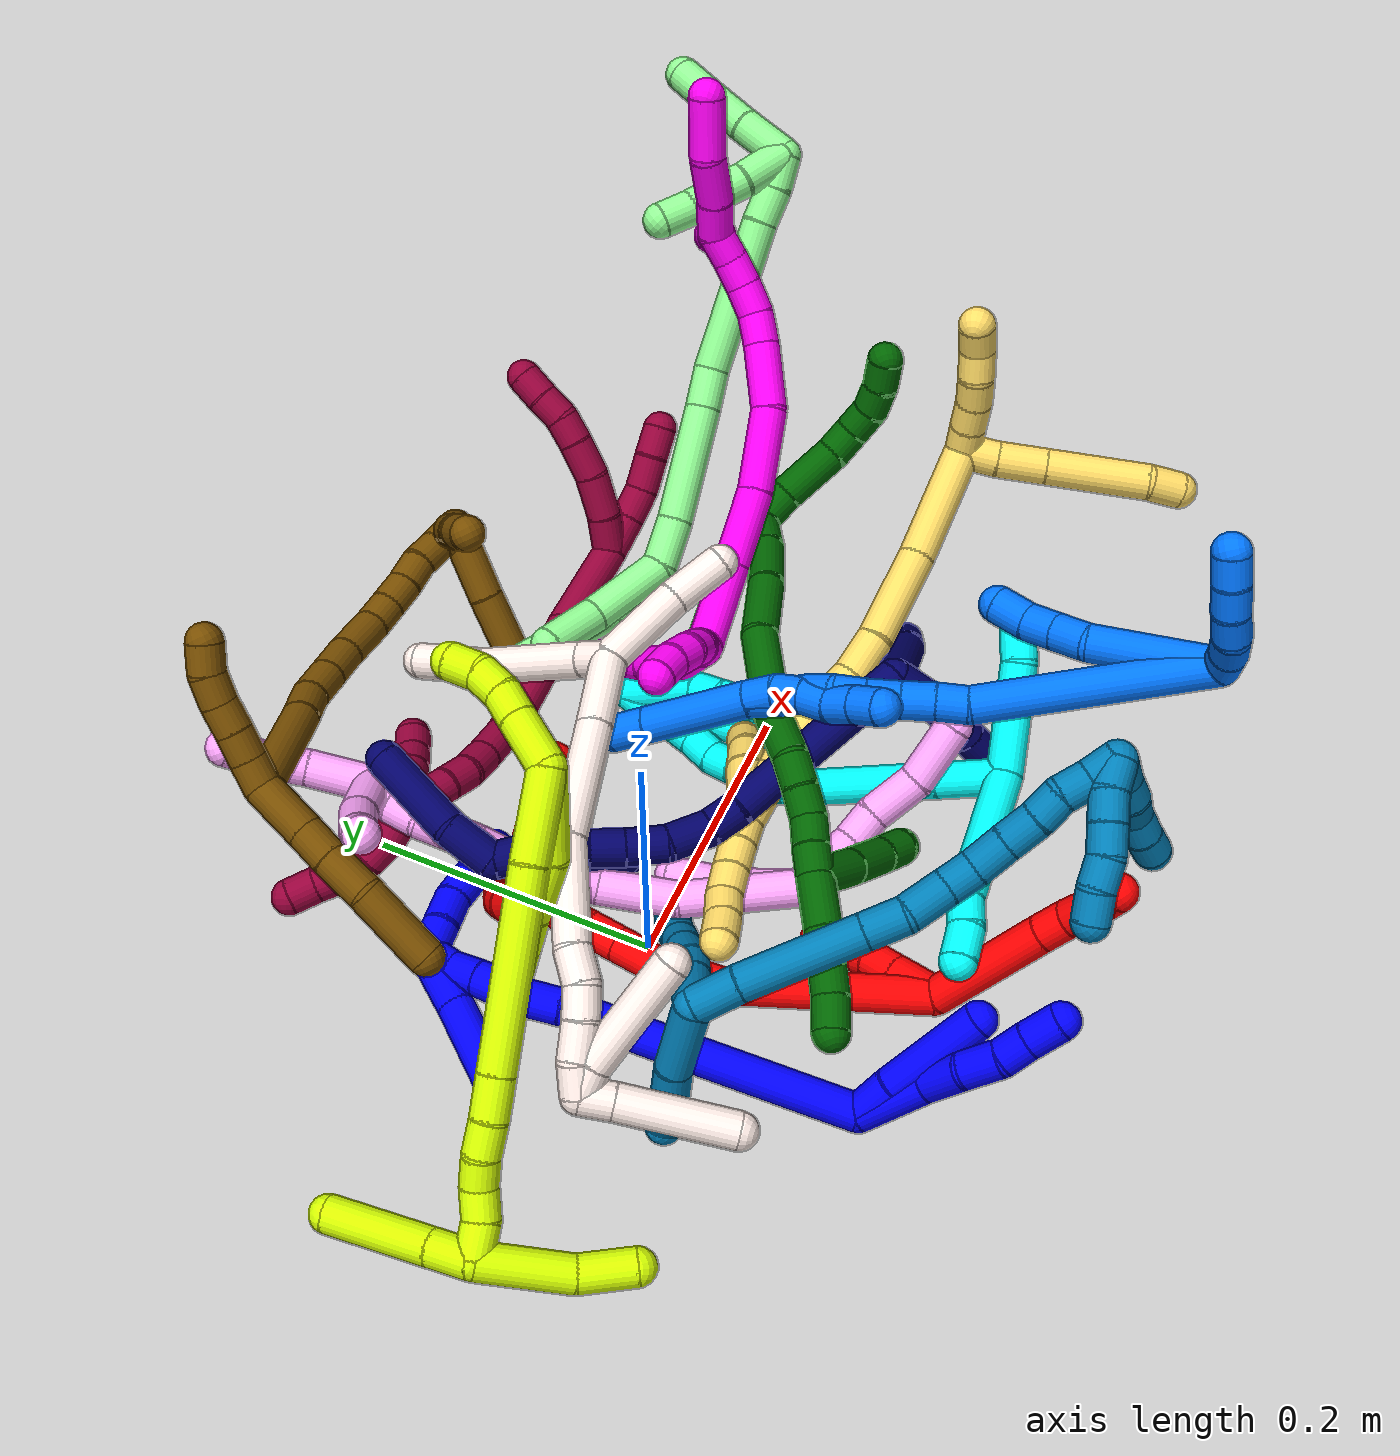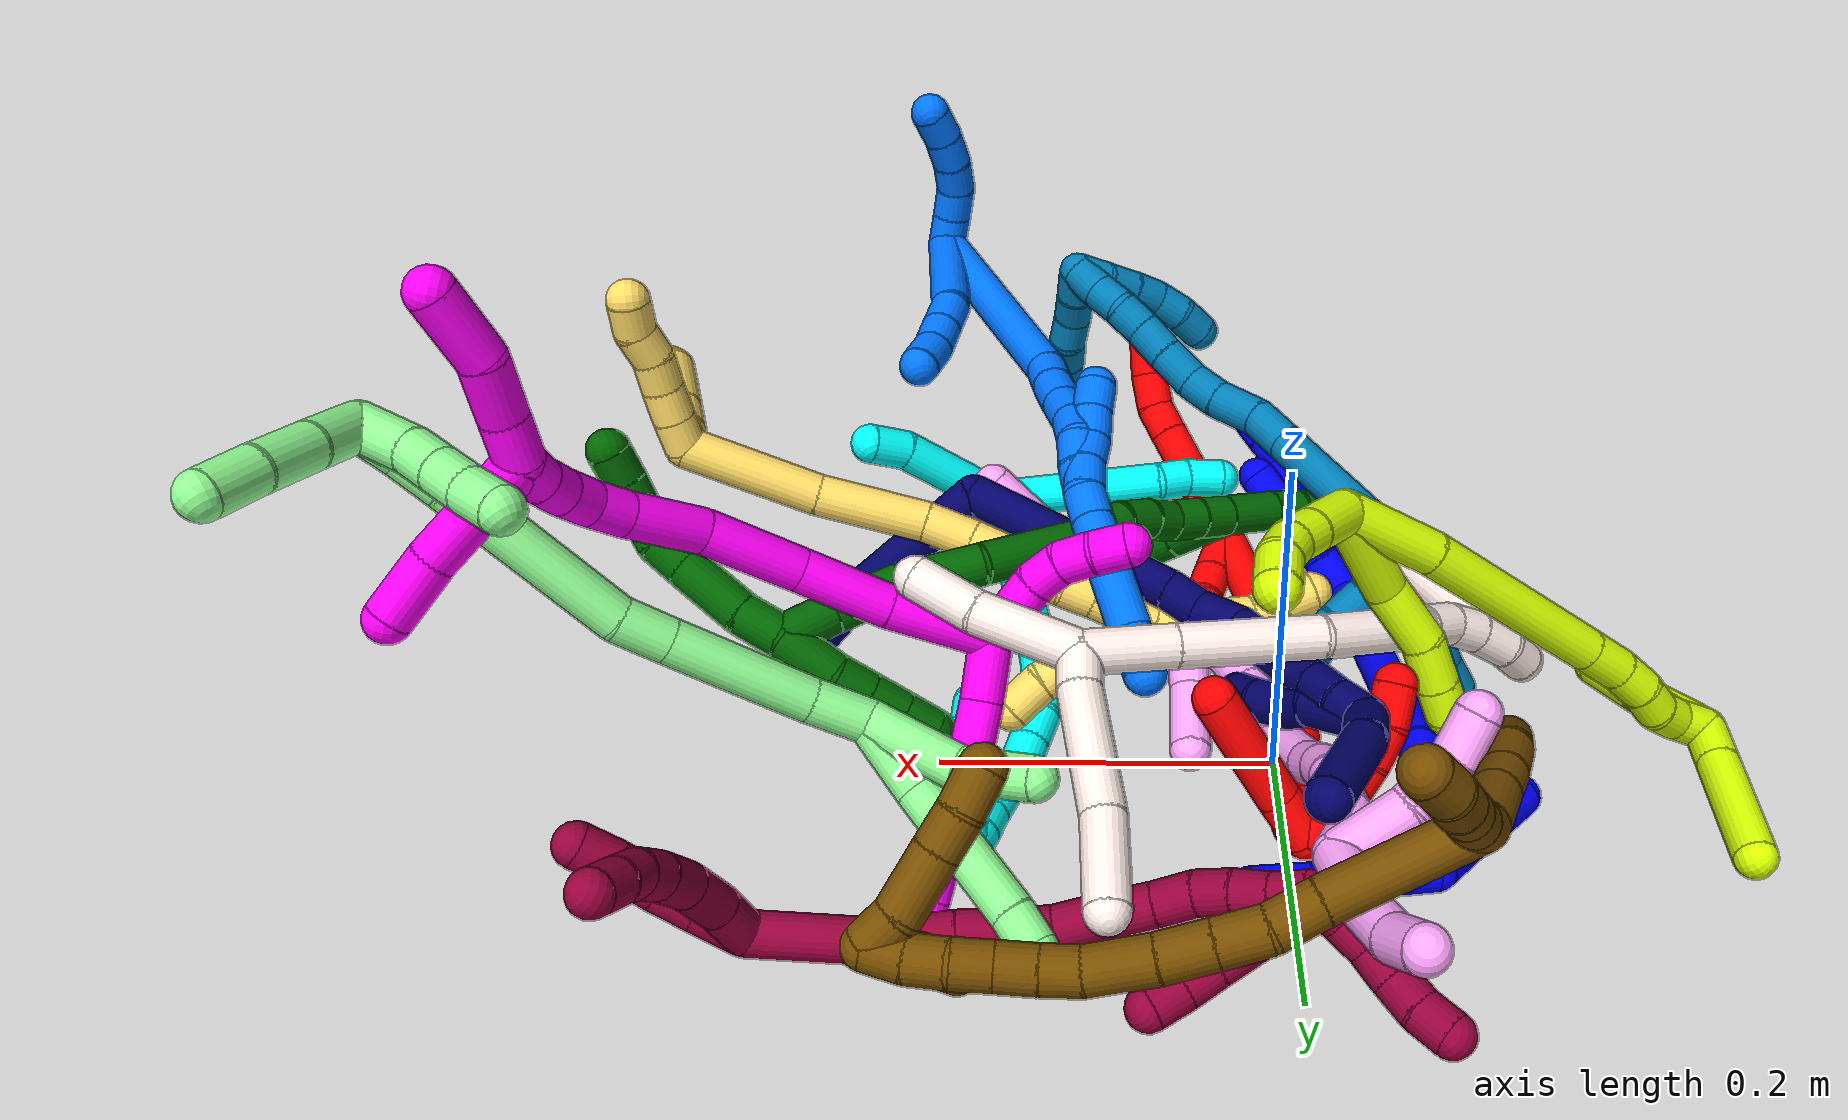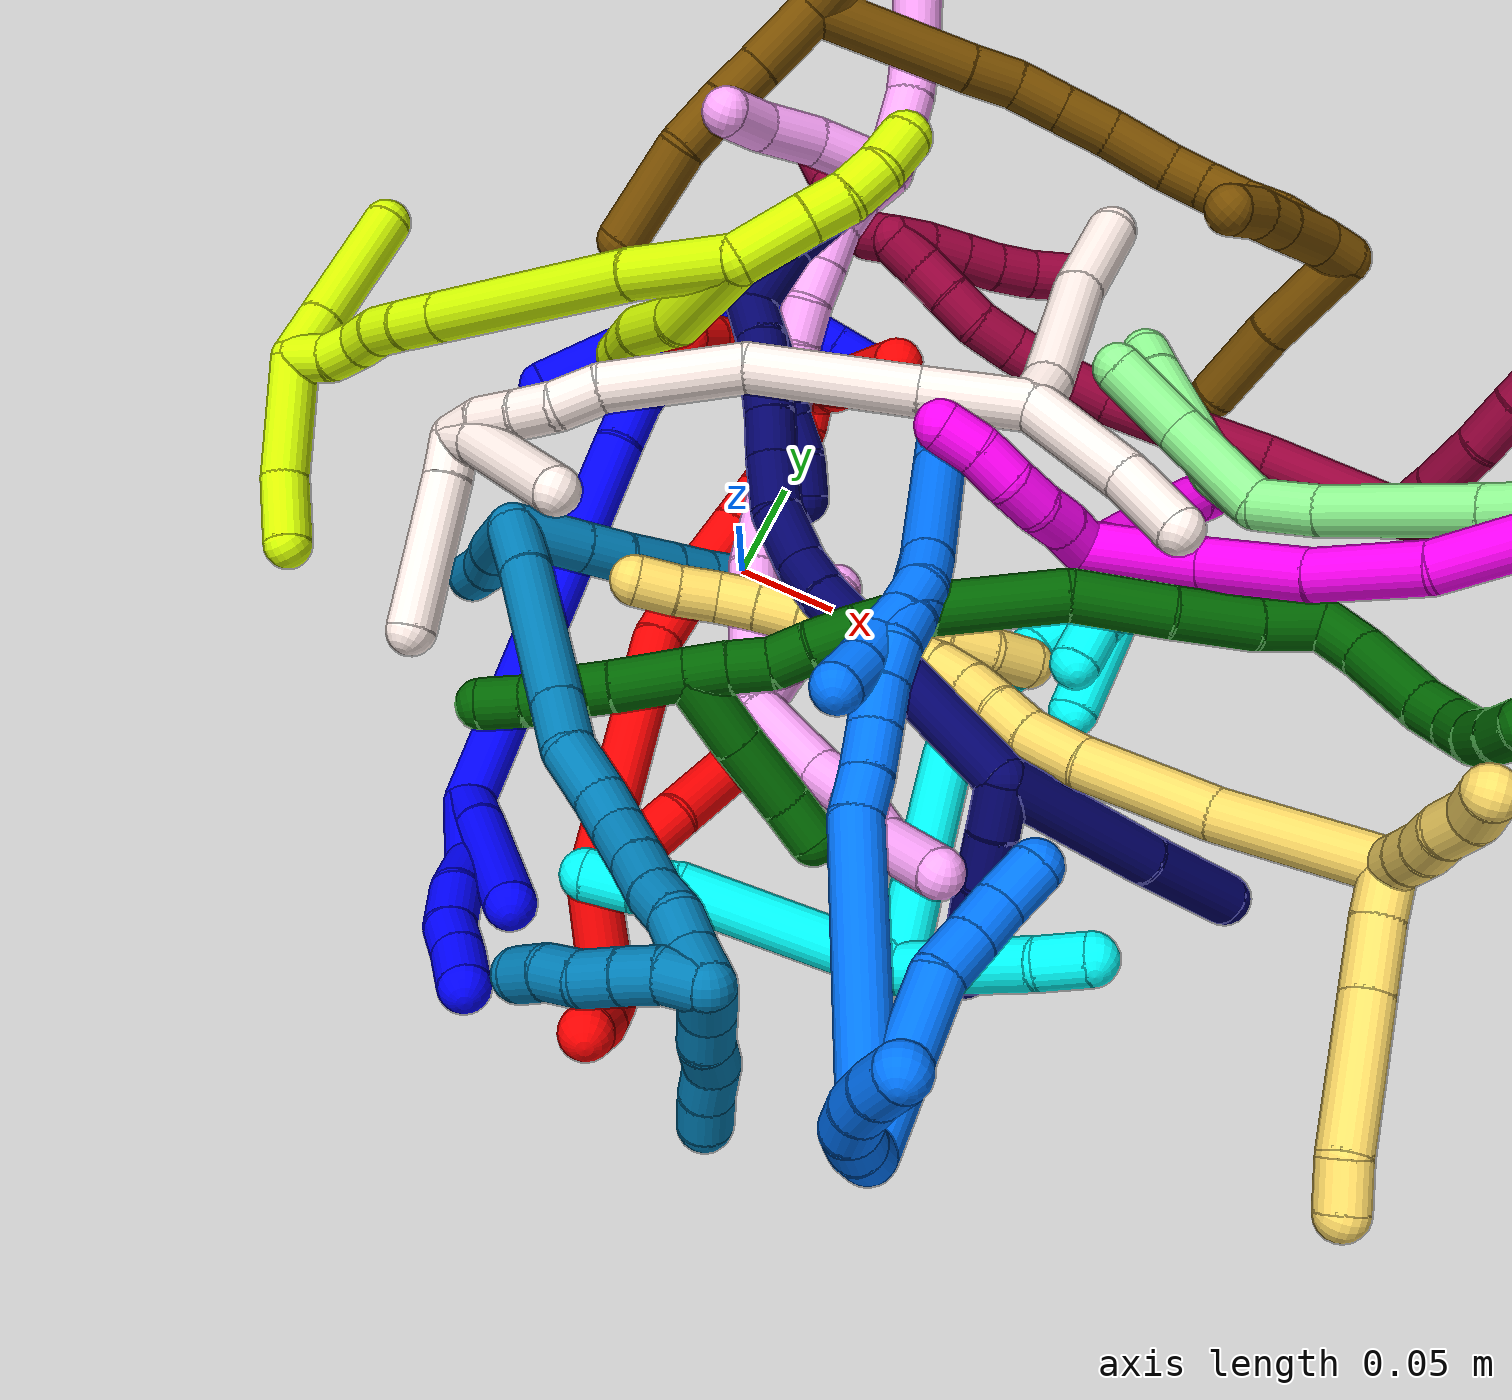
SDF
<sdf version="1.7">
 <world name="default">
  <plugin name="TubeGeneratorPlugin" filename="libtube_generator_plugin.so"/>
  <model name="photoneo_s_sensor">
   <static>1</static>
   <pose>0 0 2 1.57079 1.57079 3.14159</pose>
   <link name="link">
    <inertial><mass>0.1</mass></inertial>
    <sensor name="sensor" type="depth">
     <update_rate>30</update_rate>
     <camera>
      <horizontal_fov>1.22</horizontal_fov>
      <image><width>1920</width><height>1200</height><format>B8G8R8</format></image>
      <clip><near>0.1</near><far>4</far></clip>
      <depth_camera><output>points</output></depth_camera>
     </camera>
     <plugin name="camera_plugin" filename="libgazebo_ros_depth_camera.so">
      <baseline>0.2</baseline>
      <alwaysOn>1</alwaysOn>
      <updateRate>0.0</updateRate>
      <cameraName>camera_ir</cameraName>
      <imageTopicName>/camera/color/image_raw</imageTopicName>
      <cameraInfoTopicName>/camera/color/camera_info</cameraInfoTopicName>
      <depthImageTopicName>/camera/depth/image_raw</depthImageTopicName>
      <depthImageCameraInfoTopicName>/camera/depth/camera_info</depthImageCameraInfoTopicName>
      <pointCloudTopicName>/camera/depth/points</pointCloudTopicName>
      <frameName>fr_optical</frameName>
      <pointCloudCutoff>0.1</pointCloudCutoff>
      <pointCloudCutoffMax>2.0</pointCloudCutoffMax>
      <distortionK1>0</distortionK1>
      <distortionK2>0</distortionK2>
      <distortionK3>0</distortionK3>
      <distortionT1>0</distortionT1>
      <distortionT2>0</distortionT2>
      <CxPrime>0</CxPrime>
      <Cx>0</Cx>
      <Cy>0</Cy>
      <focalLength>0</focalLength>
      <hackBaseline>0</hackBaseline>
     </plugin>
    </sensor>
   </link>
  </model>
  <gravity>0 0 -9.8</gravity>
  <magnetic_field>6e-06 2.3e-05 -4.2e-05</magnetic_field>
  <atmosphere type="adiabatic"/>
  <physics name="default_physics" default="0" type="ode">
   <max_step_size>0.003</max_step_size>
   <real_time_factor>1</real_time_factor>
   <real_time_update_rate>1000</real_time_update_rate>
   <max_contacts>10000</max_contacts>
   <ode>
    <solver>
     <type>quick</type>
     <iters>100</iters>
     <sor>1.3</sor>
     <use_dynamic_moi_rescaling>0</use_dynamic_moi_rescaling>
    </solver>
    <constraints>
     <contact_max_correcting_vel>0</contact_max_correcting_vel>
     <contact_surface_layer>0.001</contact_surface_layer>
     <cfm>0</cfm>
     <erp>0.2</erp>
    </constraints>
   </ode>
  </physics>
  <scene><ambient>0.4 0.4 0.4 1</ambient><background>0.7 0.7 0.7 1</background><shadows>0</shadows></scene>
  <audio><device>default</device></audio>
  <spherical_coordinates>
   <surface_model>EARTH_WGS84</surface_model>
   <latitude_deg>0</latitude_deg>
   <longitude_deg>0</longitude_deg>
   <elevation>0</elevation>
   <heading_deg>0</heading_deg>
  </spherical_coordinates>
  <model name="bin">
   <static>1</static>
   <link name="bottom">
    <collision name="collision-bottom">
     <pose>0 0 -0.01 0 -0 0</pose>
     <geometry><box><size>0.8 0.6 0.02</size></box></geometry>
     <surface>
      <friction><ode><mu>100</mu><mu2>100</mu2></ode></friction>
      <contact><collide_bitmask>65535</collide_bitmask></contact>
     </surface>
    </collision>
   </link>
   <link name="west_wall">
    <collision name="collision-west_wall">
     <pose>-0.41 0 0.1 0 -0 0</pose>
     <geometry><box><size>0.02 0.6 0.2</size></box></geometry>
     <surface>
      <friction><ode><mu>100</mu><mu2>100</mu2></ode></friction>
      <contact><collide_bitmask>65535</collide_bitmask></contact>
     </surface>
    </collision>
   </link>
   <link name="east_wall">
    <collision name="collision-east_wall">
     <pose>0.41 0 0.1 0 -0 0</pose>
     <geometry><box><size>0.02 0.6 0.2</size></box></geometry>
     <surface>
      <friction><ode><mu>100</mu><mu2>100</mu2></ode></friction>
      <contact><collide_bitmask>65535</collide_bitmask></contact>
     </surface>
    </collision>
   </link>
   <link name="south_wall">
    <collision name="collision-south_wall">
     <pose>0 -0.31 0.1 0 -0 0</pose>
     <geometry><box><size>0.8 0.02 0.2</size></box></geometry>
     <surface>
      <friction><ode><mu>100</mu><mu2>100</mu2></ode></friction>
      <contact><collide_bitmask>65535</collide_bitmask></contact>
     </surface>
    </collision>
   </link>
   <link name="north_wall">
    <collision name="collision-north_wall">
     <pose>0 0.31 0.1 0 -0 0</pose>
     <geometry><box><size>0.8 0.02 0.2</size></box></geometry>
     <surface>
      <friction><ode><mu>100</mu><mu2>100</mu2></ode></friction>
      <contact><collide_bitmask>65535</collide_bitmask></contact>
     </surface>
    </collision>
   </link>
  </model>
  <model name="1">
   <static>0</static>
   <link name="1">
    <collision name="collision-cylinder-e_1_2_8">
     <pose>0.000252 -0.000121 0.024471 0.004957 0.010288 2.6e-05</pose>
     <geometry><cylinder><radius>0.0125</radius><length>0.048945</length></cylinder></geometry>
     <surface>
      <friction><ode><mu>1.16</mu><mu2>1.16</mu2><slip1>0</slip1><slip2>0</slip2></ode></friction>
      <contact><ode><kp>1e+06</kp><kd>1</kd><max_vel>0</max_vel><min_depth>0.001</min_depth></ode></contact>
     </surface>
    </collision>
    <visual name="visual-cylinder-e_1_2_8">
     <pose>0.000252 -0.000121 0.024471 0.004957 0.010288 2.6e-05</pose>
     <geometry><cylinder><radius>0.0125</radius><length>0.048945</length></cylinder></geometry>
     <material><ambient>0 0 1 1</ambient></material>
    </visual>
    <collision name="collision-cylinder-e_2_8_9">
     <pose>-0.004194 -0.001502 0.06341 0.086825 -0.312833 -0.013701</pose>
     <geometry><cylinder><radius>0.0125</radius><length>0.030526</length></cylinder></geometry>
     <surface>
      <friction><ode><mu>1.16</mu><mu2>1.16</mu2><slip1>0</slip1><slip2>0</slip2></ode></friction>
      <contact><ode><kp>1e+06</kp><kd>1</kd><max_vel>0</max_vel><min_depth>0.001</min_depth></ode></contact>
     </surface>
    </collision>
    <visual name="visual-cylinder-e_2_8_9">
     <pose>-0.004194 -0.001502 0.06341 0.086825 -0.312833 -0.013701</pose>
     <geometry><cylinder><radius>0.0125</radius><length>0.030526</length></cylinder></geometry>
     <material><ambient>0 0 1 1</ambient></material>
    </visual>
    <collision name="collision-cylinder-e_3_9_10">
     <pose>-0.009689 -0.00415 0.091014 0.105334 -0.060356 -0.003183</pose>
     <geometry><cylinder><radius>0.0125</radius><length>0.026467</length></cylinder></geometry>
     <surface>
      <friction><ode><mu>1.16</mu><mu2>1.16</mu2><slip1>0</slip1><slip2>0</slip2></ode></friction>
      <contact><ode><kp>1e+06</kp><kd>1</kd><max_vel>0</max_vel><min_depth>0.001</min_depth></ode></contact>
     </surface>
    </collision>
    <visual name="visual-cylinder-e_3_9_10">
     <pose>-0.009689 -0.00415 0.091014 0.105334 -0.060356 -0.003183</pose>
     <geometry><cylinder><radius>0.0125</radius><length>0.026467</length></cylinder></geometry>
     <material><ambient>0 0 1 1</ambient></material>
    </visual>
    <collision name="collision-cylinder-e_4_10_11">
     <pose>-0.009804 -0.003935 0.11405 -0.160593 0.06802 -0.005476</pose>
     <geometry><cylinder><radius>0.0125</radius><length>0.020104</length></cylinder></geometry>
     <surface>
      <friction><ode><mu>1.16</mu><mu2>1.16</mu2><slip1>0</slip1><slip2>0</slip2></ode></friction>
      <contact><ode><kp>1e+06</kp><kd>1</kd><max_vel>0</max_vel><min_depth>0.001</min_depth></ode></contact>
     </surface>
    </collision>
    <visual name="visual-cylinder-e_4_10_11">
     <pose>-0.009804 -0.003935 0.11405 -0.160593 0.06802 -0.005476</pose>
     <geometry><cylinder><radius>0.0125</radius><length>0.020104</length></cylinder></geometry>
     <material><ambient>0 0 1 1</ambient></material>
    </visual>
    <collision name="collision-cylinder-e_5_11_6">
     <pose>-0.008714 -0.001132 0.135861 -0.100378 0.033975 -0.001707</pose>
     <geometry><cylinder><radius>0.0125</radius><length>0.023957</length></cylinder></geometry>
     <surface>
      <friction><ode><mu>1.16</mu><mu2>1.16</mu2><slip1>0</slip1><slip2>0</slip2></ode></friction>
      <contact><ode><kp>1e+06</kp><kd>1</kd><max_vel>0</max_vel><min_depth>0.001</min_depth></ode></contact>
     </surface>
    </collision>
    <visual name="visual-cylinder-e_5_11_6">
     <pose>-0.008714 -0.001132 0.135861 -0.100378 0.033975 -0.001707</pose>
     <geometry><cylinder><radius>0.0125</radius><length>0.023957</length></cylinder></geometry>
     <material><ambient>0 0 1 1</ambient></material>
    </visual>
    <collision name="collision-cylinder-e_1_2_12">
     <pose>-0.000968 0.003591 0.014093 -0.249521 -0.066483 0.008341</pose>
     <geometry><cylinder><radius>0.0125</radius><length>0.029151</length></cylinder></geometry>
     <surface>
      <friction><ode><mu>1.16</mu><mu2>1.16</mu2><slip1>0</slip1><slip2>0</slip2></ode></friction>
      <contact><ode><kp>1e+06</kp><kd>1</kd><max_vel>0</max_vel><min_depth>0.001</min_depth></ode></contact>
     </surface>
    </collision>
    <visual name="visual-cylinder-e_1_2_12">
     <pose>-0.000968 0.003591 0.014093 -0.249521 -0.066483 0.008341</pose>
     <geometry><cylinder><radius>0.0125</radius><length>0.029151</length></cylinder></geometry>
     <material><ambient>0 0 1 1</ambient></material>
    </visual>
    <collision name="collision-cylinder-e_2_12_5">
     <pose>-0.001611 0.014364 0.062873 -0.204157 0.009191 -0.000942</pose>
     <geometry><cylinder><radius>0.0125</radius><length>0.070849</length></cylinder></geometry>
     <surface>
      <friction><ode><mu>1.16</mu><mu2>1.16</mu2><slip1>0</slip1><slip2>0</slip2></ode></friction>
      <contact><ode><kp>1e+06</kp><kd>1</kd><max_vel>0</max_vel><min_depth>0.001</min_depth></ode></contact>
     </surface>
    </collision>
    <visual name="visual-cylinder-e_2_12_5">
     <pose>-0.001611 0.014364 0.062873 -0.204157 0.009191 -0.000942</pose>
     <geometry><cylinder><radius>0.0125</radius><length>0.070849</length></cylinder></geometry>
     <material><ambient>0 0 1 1</ambient></material>
    </visual>
    <collision name="collision-cylinder-e_1_2_13">
     <pose>-0.029058 0.066722 -0.067569 -2.3625 -0.29696 0.698833</pose>
     <geometry><cylinder><radius>0.0125</radius><length>0.198612</length></cylinder></geometry>
     <surface>
      <friction><ode><mu>1.16</mu><mu2>1.16</mu2><slip1>0</slip1><slip2>0</slip2></ode></friction>
      <contact><ode><kp>1e+06</kp><kd>1</kd><max_vel>0</max_vel><min_depth>0.001</min_depth></ode></contact>
     </surface>
    </collision>
    <visual name="visual-cylinder-e_1_2_13">
     <pose>-0.029058 0.066722 -0.067569 -2.3625 -0.29696 0.698833</pose>
     <geometry><cylinder><radius>0.0125</radius><length>0.198612</length></cylinder></geometry>
     <material><ambient>0 0 1 1</ambient></material>
    </visual>
    <collision name="collision-cylinder-e_2_13_14">
     <pose>-0.060548 0.141719 -0.145834 -2.48308 -0.177868 0.510535</pose>
     <geometry><cylinder><radius>0.0125</radius><length>0.027481</length></cylinder></geometry>
     <surface>
      <friction><ode><mu>1.16</mu><mu2>1.16</mu2><slip1>0</slip1><slip2>0</slip2></ode></friction>
      <contact><ode><kp>1e+06</kp><kd>1</kd><max_vel>0</max_vel><min_depth>0.001</min_depth></ode></contact>
     </surface>
    </collision>
    <visual name="visual-cylinder-e_2_13_14">
     <pose>-0.060548 0.141719 -0.145834 -2.48308 -0.177868 0.510535</pose>
     <geometry><cylinder><radius>0.0125</radius><length>0.027481</length></cylinder></geometry>
     <material><ambient>0 0 1 1</ambient></material>
    </visual>
    <collision name="collision-cylinder-e_3_14_15">
     <pose>-0.063366 0.161618 -0.168553 -2.37313 -0.023122 0.057172</pose>
     <geometry><cylinder><radius>0.0125</radius><length>0.033454</length></cylinder></geometry>
     <surface>
      <friction><ode><mu>1.16</mu><mu2>1.16</mu2><slip1>0</slip1><slip2>0</slip2></ode></friction>
      <contact><ode><kp>1e+06</kp><kd>1</kd><max_vel>0</max_vel><min_depth>0.001</min_depth></ode></contact>
     </surface>
    </collision>
    <visual name="visual-cylinder-e_3_14_15">
     <pose>-0.063366 0.161618 -0.168553 -2.37313 -0.023122 0.057172</pose>
     <geometry><cylinder><radius>0.0125</radius><length>0.033454</length></cylinder></geometry>
     <material><ambient>0 0 1 1</ambient></material>
    </visual>
    <collision name="collision-cylinder-e_4_15_16">
     <pose>-0.064051 0.179831 -0.188248 -2.43189 -0.029537 0.079678</pose>
     <geometry><cylinder><radius>0.0125</radius><length>0.020236</length></cylinder></geometry>
     <surface>
      <friction><ode><mu>1.16</mu><mu2>1.16</mu2><slip1>0</slip1><slip2>0</slip2></ode></friction>
      <contact><ode><kp>1e+06</kp><kd>1</kd><max_vel>0</max_vel><min_depth>0.001</min_depth></ode></contact>
     </surface>
    </collision>
    <visual name="visual-cylinder-e_4_15_16">
     <pose>-0.064051 0.179831 -0.188248 -2.43189 -0.029537 0.079678</pose>
     <geometry><cylinder><radius>0.0125</radius><length>0.020236</length></cylinder></geometry>
     <material><ambient>0 0 1 1</ambient></material>
    </visual>
    <collision name="collision-cylinder-e_5_16_1">
     <pose>-0.064555 0.194522 -0.201962 -2.21164 -0.020221 0.040304</pose>
     <geometry><cylinder><radius>0.0125</radius><length>0.020216</length></cylinder></geometry>
     <surface>
      <friction><ode><mu>1.16</mu><mu2>1.16</mu2><slip1>0</slip1><slip2>0</slip2></ode></friction>
      <contact><ode><kp>1e+06</kp><kd>1</kd><max_vel>0</max_vel><min_depth>0.001</min_depth></ode></contact>
     </surface>
    </collision>
    <visual name="visual-cylinder-e_5_16_1">
     <pose>-0.064555 0.194522 -0.201962 -2.21164 -0.020221 0.040304</pose>
     <geometry><cylinder><radius>0.0125</radius><length>0.020216</length></cylinder></geometry>
     <material><ambient>0 0 1 1</ambient></material>
    </visual>
    <collision name="collision-cylinder-e_1_1_17">
     <pose>-0.057691 0.210355 -0.203758 -1.06872 0.675459 -0.409818</pose>
     <geometry><cylinder><radius>0.0125</radius><length>0.022608</length></cylinder></geometry>
     <surface>
      <friction><ode><mu>1.16</mu><mu2>1.16</mu2><slip1>0</slip1><slip2>0</slip2></ode></friction>
      <contact><ode><kp>1e+06</kp><kd>1</kd><max_vel>0</max_vel><min_depth>0.001</min_depth></ode></contact>
     </surface>
    </collision>
    <visual name="visual-cylinder-e_1_1_17">
     <pose>-0.057691 0.210355 -0.203758 -1.06872 0.675459 -0.409818</pose>
     <geometry><cylinder><radius>0.0125</radius><length>0.022608</length></cylinder></geometry>
     <material><ambient>0 0 1 1</ambient></material>
    </visual>
    <collision name="collision-cylinder-e_2_17_18">
     <pose>-0.042052 0.22603 -0.196363 -1.19314 0.786998 -0.549602</pose>
     <geometry><cylinder><radius>0.0125</radius><length>0.024204</length></cylinder></geometry>
     <surface>
      <friction><ode><mu>1.16</mu><mu2>1.16</mu2><slip1>0</slip1><slip2>0</slip2></ode></friction>
      <contact><ode><kp>1e+06</kp><kd>1</kd><max_vel>0</max_vel><min_depth>0.001</min_depth></ode></contact>
     </surface>
    </collision>
    <visual name="visual-cylinder-e_2_17_18">
     <pose>-0.042052 0.22603 -0.196363 -1.19314 0.786998 -0.549602</pose>
     <geometry><cylinder><radius>0.0125</radius><length>0.024204</length></cylinder></geometry>
     <material><ambient>0 0 1 1</ambient></material>
    </visual>
    <collision name="collision-cylinder-e_3_18_19">
     <pose>-0.025832 0.239134 -0.188798 -0.863381 0.844656 -0.408253</pose>
     <geometry><cylinder><radius>0.0125</radius><length>0.02046</length></cylinder></geometry>
     <surface>
      <friction><ode><mu>1.16</mu><mu2>1.16</mu2><slip1>0</slip1><slip2>0</slip2></ode></friction>
      <contact><ode><kp>1e+06</kp><kd>1</kd><max_vel>0</max_vel><min_depth>0.001</min_depth></ode></contact>
     </surface>
    </collision>
    <visual name="visual-cylinder-e_3_18_19">
     <pose>-0.025832 0.239134 -0.188798 -0.863381 0.844656 -0.408253</pose>
     <geometry><cylinder><radius>0.0125</radius><length>0.02046</length></cylinder></geometry>
     <material><ambient>0 0 1 1</ambient></material>
    </visual>
    <collision name="collision-cylinder-e_4_19_4">
     <pose>-0.005941 0.252537 -0.177311 -0.861519 0.845169 -0.407552</pose>
     <geometry><cylinder><radius>0.0125</radius><length>0.032729</length></cylinder></geometry>
     <surface>
      <friction><ode><mu>1.16</mu><mu2>1.16</mu2><slip1>0</slip1><slip2>0</slip2></ode></friction>
      <contact><ode><kp>1e+06</kp><kd>1</kd><max_vel>0</max_vel><min_depth>0.001</min_depth></ode></contact>
     </surface>
    </collision>
    <visual name="visual-cylinder-e_4_19_4">
     <pose>-0.005941 0.252537 -0.177311 -0.861519 0.845169 -0.407552</pose>
     <geometry><cylinder><radius>0.0125</radius><length>0.032729</length></cylinder></geometry>
     <material><ambient>0 0 1 1</ambient></material>
    </visual>
    <collision name="collision-cylinder-e_1_1_20">
     <pose>-0.067385 0.182912 -0.203887 1.36489 -0.129687 -0.105449</pose>
     <geometry><cylinder><radius>0.0125</radius><length>0.040613</length></cylinder></geometry>
     <surface>
      <friction><ode><mu>1.16</mu><mu2>1.16</mu2><slip1>0</slip1><slip2>0</slip2></ode></friction>
      <contact><ode><kp>1e+06</kp><kd>1</kd><max_vel>0</max_vel><min_depth>0.001</min_depth></ode></contact>
     </surface>
    </collision>
    <visual name="visual-cylinder-e_1_1_20">
     <pose>-0.067385 0.182912 -0.203887 1.36489 -0.129687 -0.105449</pose>
     <geometry><cylinder><radius>0.0125</radius><length>0.040613</length></cylinder></geometry>
     <material><ambient>0 0 1 1</ambient></material>
    </visual>
    <collision name="collision-cylinder-e_2_20_3">
     <pose>-0.076069 0.134723 -0.193936 1.36874 -0.205442 -0.16782</pose>
     <geometry><cylinder><radius>0.0125</radius><length>0.059387</length></cylinder></geometry>
     <surface>
      <friction><ode><mu>1.16</mu><mu2>1.16</mu2><slip1>0</slip1><slip2>0</slip2></ode></friction>
      <contact><ode><kp>1e+06</kp><kd>1</kd><max_vel>0</max_vel><min_depth>0.001</min_depth></ode></contact>
     </surface>
    </collision>
    <visual name="visual-cylinder-e_2_20_3">
     <pose>-0.076069 0.134723 -0.193936 1.36874 -0.205442 -0.16782</pose>
     <geometry><cylinder><radius>0.0125</radius><length>0.059387</length></cylinder></geometry>
     <material><ambient>0 0 1 1</ambient></material>
    </visual>
    <collision name="collision-sphere-3">
     <pose>-0.082126 0.106246 -0.188102 0 -0 0</pose>
     <geometry><sphere><radius>0.0125</radius></sphere></geometry>
     <surface>
      <friction><ode><mu>1.16</mu><mu2>1.16</mu2><slip1>0</slip1><slip2>0</slip2></ode></friction>
      <contact><ode><kp>1e+06</kp><kd>1</kd><max_vel>0</max_vel><min_depth>0.001</min_depth></ode></contact>
     </surface>
    </collision>
    <visual name="visual-sphere-3">
     <pose>-0.082126 0.106246 -0.188102 0 -0 0</pose>
     <geometry><sphere><radius>0.0125</radius></sphere></geometry>
     <material><ambient>0 0 1 1</ambient></material>
    </visual>
    <collision name="collision-sphere-20">
     <pose>-0.070011 0.163201 -0.19977 0 -0 0</pose>
     <geometry><sphere><radius>0.0125</radius></sphere></geometry>
     <surface>
      <friction><ode><mu>1.16</mu><mu2>1.16</mu2><slip1>0</slip1><slip2>0</slip2></ode></friction>
      <contact><ode><kp>1e+06</kp><kd>1</kd><max_vel>0</max_vel><min_depth>0.001</min_depth></ode></contact>
     </surface>
    </collision>
    <visual name="visual-sphere-20">
     <pose>-0.070011 0.163201 -0.19977 0 -0 0</pose>
     <geometry><sphere><radius>0.0125</radius></sphere></geometry>
     <material><ambient>0 0 1 1</ambient></material>
    </visual>
    <collision name="collision-sphere-4">
     <pose>0.006301 0.260778 -0.170238 0 -0 0</pose>
     <geometry><sphere><radius>0.0125</radius></sphere></geometry>
     <surface>
      <friction><ode><mu>1.16</mu><mu2>1.16</mu2><slip1>0</slip1><slip2>0</slip2></ode></friction>
      <contact><ode><kp>1e+06</kp><kd>1</kd><max_vel>0</max_vel><min_depth>0.001</min_depth></ode></contact>
     </surface>
    </collision>
    <visual name="visual-sphere-4">
     <pose>0.006301 0.260778 -0.170238 0 -0 0</pose>
     <geometry><sphere><radius>0.0125</radius></sphere></geometry>
     <material><ambient>0 0 1 1</ambient></material>
    </visual>
    <collision name="collision-sphere-6">
     <pose>-0.008307 6.8e-05 0.147772 0 -0 0</pose>
     <geometry><sphere><radius>0.0125</radius></sphere></geometry>
     <surface>
      <friction><ode><mu>1.16</mu><mu2>1.16</mu2><slip1>0</slip1><slip2>0</slip2></ode></friction>
      <contact><ode><kp>1e+06</kp><kd>1</kd><max_vel>0</max_vel><min_depth>0.001</min_depth></ode></contact>
     </surface>
    </collision>
    <visual name="visual-sphere-6">
     <pose>-0.008307 6.8e-05 0.147772 0 -0 0</pose>
     <geometry><sphere><radius>0.0125</radius></sphere></geometry>
     <material><ambient>0 0 1 1</ambient></material>
    </visual>
    <collision name="collision-sphere-11">
     <pose>-0.009121 -0.002332 0.12395 0 -0 0</pose>
     <geometry><sphere><radius>0.0125</radius></sphere></geometry>
     <surface>
      <friction><ode><mu>1.16</mu><mu2>1.16</mu2><slip1>0</slip1><slip2>0</slip2></ode></friction>
      <contact><ode><kp>1e+06</kp><kd>1</kd><max_vel>0</max_vel><min_depth>0.001</min_depth></ode></contact>
     </surface>
    </collision>
    <visual name="visual-sphere-11">
     <pose>-0.009121 -0.002332 0.12395 0 -0 0</pose>
     <geometry><sphere><radius>0.0125</radius></sphere></geometry>
     <material><ambient>0 0 1 1</ambient></material>
    </visual>
    <collision name="collision-sphere-10">
     <pose>-0.010488 -0.005539 0.10415 0 -0 0</pose>
     <geometry><sphere><radius>0.0125</radius></sphere></geometry>
     <surface>
      <friction><ode><mu>1.16</mu><mu2>1.16</mu2><slip1>0</slip1><slip2>0</slip2></ode></friction>
      <contact><ode><kp>1e+06</kp><kd>1</kd><max_vel>0</max_vel><min_depth>0.001</min_depth></ode></contact>
     </surface>
    </collision>
    <visual name="visual-sphere-10">
     <pose>-0.010488 -0.005539 0.10415 0 -0 0</pose>
     <geometry><sphere><radius>0.0125</radius></sphere></geometry>
     <material><ambient>0 0 1 1</ambient></material>
    </visual>
    <collision name="collision-sphere-9">
     <pose>-0.008891 -0.002761 0.077877 0 -0 0</pose>
     <geometry><sphere><radius>0.0125</radius></sphere></geometry>
     <surface>
      <friction><ode><mu>1.16</mu><mu2>1.16</mu2><slip1>0</slip1><slip2>0</slip2></ode></friction>
      <contact><ode><kp>1e+06</kp><kd>1</kd><max_vel>0</max_vel><min_depth>0.001</min_depth></ode></contact>
     </surface>
    </collision>
    <visual name="visual-sphere-9">
     <pose>-0.008891 -0.002761 0.077877 0 -0 0</pose>
     <geometry><sphere><radius>0.0125</radius></sphere></geometry>
     <material><ambient>0 0 1 1</ambient></material>
    </visual>
    <collision name="collision-sphere-2">
     <geometry><sphere><radius>0.0125</radius></sphere></geometry>
     <surface>
      <friction><ode><mu>1.16</mu><mu2>1.16</mu2><slip1>0</slip1><slip2>0</slip2></ode></friction>
      <contact><ode><kp>1e+06</kp><kd>1</kd><max_vel>0</max_vel><min_depth>0.001</min_depth></ode></contact>
     </surface>
    </collision>
    <visual name="visual-sphere-2">
     <geometry><sphere><radius>0.0125</radius></sphere></geometry>
     <material><ambient>0 0 1 1</ambient></material>
    </visual>
    <collision name="collision-sphere-19">
     <pose>-0.018183 0.244297 -0.184384 0 -0 0</pose>
     <geometry><sphere><radius>0.0125</radius></sphere></geometry>
     <surface>
      <friction><ode><mu>1.16</mu><mu2>1.16</mu2><slip1>0</slip1><slip2>0</slip2></ode></friction>
      <contact><ode><kp>1e+06</kp><kd>1</kd><max_vel>0</max_vel><min_depth>0.001</min_depth></ode></contact>
     </surface>
    </collision>
    <visual name="visual-sphere-19">
     <pose>-0.018183 0.244297 -0.184384 0 -0 0</pose>
     <geometry><sphere><radius>0.0125</radius></sphere></geometry>
     <material><ambient>0 0 1 1</ambient></material>
    </visual>
    <collision name="collision-sphere-8">
     <pose>0.000504 -0.000243 0.048942 0 -0 0</pose>
     <geometry><sphere><radius>0.0125</radius></sphere></geometry>
     <surface>
      <friction><ode><mu>1.16</mu><mu2>1.16</mu2><slip1>0</slip1><slip2>0</slip2></ode></friction>
      <contact><ode><kp>1e+06</kp><kd>1</kd><max_vel>0</max_vel><min_depth>0.001</min_depth></ode></contact>
     </surface>
    </collision>
    <visual name="visual-sphere-8">
     <pose>0.000504 -0.000243 0.048942 0 -0 0</pose>
     <geometry><sphere><radius>0.0125</radius></sphere></geometry>
     <material><ambient>0 0 1 1</ambient></material>
    </visual>
    <collision name="collision-sphere-12">
     <pose>-0.001937 0.007183 0.028186 0 -0 0</pose>
     <geometry><sphere><radius>0.0125</radius></sphere></geometry>
     <surface>
      <friction><ode><mu>1.16</mu><mu2>1.16</mu2><slip1>0</slip1><slip2>0</slip2></ode></friction>
      <contact><ode><kp>1e+06</kp><kd>1</kd><max_vel>0</max_vel><min_depth>0.001</min_depth></ode></contact>
     </surface>
    </collision>
    <visual name="visual-sphere-12">
     <pose>-0.001937 0.007183 0.028186 0 -0 0</pose>
     <geometry><sphere><radius>0.0125</radius></sphere></geometry>
     <material><ambient>0 0 1 1</ambient></material>
    </visual>
    <collision name="collision-sphere-5">
     <pose>-0.001285 0.021546 0.097561 0 -0 0</pose>
     <geometry><sphere><radius>0.0125</radius></sphere></geometry>
     <surface>
      <friction><ode><mu>1.16</mu><mu2>1.16</mu2><slip1>0</slip1><slip2>0</slip2></ode></friction>
      <contact><ode><kp>1e+06</kp><kd>1</kd><max_vel>0</max_vel><min_depth>0.001</min_depth></ode></contact>
     </surface>
    </collision>
    <visual name="visual-sphere-5">
     <pose>-0.001285 0.021546 0.097561 0 -0 0</pose>
     <geometry><sphere><radius>0.0125</radius></sphere></geometry>
     <material><ambient>0 0 1 1</ambient></material>
    </visual>
    <collision name="collision-sphere-13">
     <pose>-0.058117 0.133443 -0.135138 0 -0 0</pose>
     <geometry><sphere><radius>0.0125</radius></sphere></geometry>
     <surface>
      <friction><ode><mu>1.16</mu><mu2>1.16</mu2><slip1>0</slip1><slip2>0</slip2></ode></friction>
      <contact><ode><kp>1e+06</kp><kd>1</kd><max_vel>0</max_vel><min_depth>0.001</min_depth></ode></contact>
     </surface>
    </collision>
    <visual name="visual-sphere-13">
     <pose>-0.058117 0.133443 -0.135138 0 -0 0</pose>
     <geometry><sphere><radius>0.0125</radius></sphere></geometry>
     <material><ambient>0 0 1 1</ambient></material>
    </visual>
    <collision name="collision-sphere-14">
     <pose>-0.062979 0.149995 -0.15653 0 -0 0</pose>
     <geometry><sphere><radius>0.0125</radius></sphere></geometry>
     <surface>
      <friction><ode><mu>1.16</mu><mu2>1.16</mu2><slip1>0</slip1><slip2>0</slip2></ode></friction>
      <contact><ode><kp>1e+06</kp><kd>1</kd><max_vel>0</max_vel><min_depth>0.001</min_depth></ode></contact>
     </surface>
    </collision>
    <visual name="visual-sphere-14">
     <pose>-0.062979 0.149995 -0.15653 0 -0 0</pose>
     <geometry><sphere><radius>0.0125</radius></sphere></geometry>
     <material><ambient>0 0 1 1</ambient></material>
    </visual>
    <collision name="collision-sphere-15">
     <pose>-0.063753 0.17324 -0.180576 0 -0 0</pose>
     <geometry><sphere><radius>0.0125</radius></sphere></geometry>
     <surface>
      <friction><ode><mu>1.16</mu><mu2>1.16</mu2><slip1>0</slip1><slip2>0</slip2></ode></friction>
      <contact><ode><kp>1e+06</kp><kd>1</kd><max_vel>0</max_vel><min_depth>0.001</min_depth></ode></contact>
     </surface>
    </collision>
    <visual name="visual-sphere-15">
     <pose>-0.063753 0.17324 -0.180576 0 -0 0</pose>
     <geometry><sphere><radius>0.0125</radius></sphere></geometry>
     <material><ambient>0 0 1 1</ambient></material>
    </visual>
    <collision name="collision-sphere-16">
     <pose>-0.06435 0.186421 -0.19592 0 -0 0</pose>
     <geometry><sphere><radius>0.0125</radius></sphere></geometry>
     <surface>
      <friction><ode><mu>1.16</mu><mu2>1.16</mu2><slip1>0</slip1><slip2>0</slip2></ode></friction>
      <contact><ode><kp>1e+06</kp><kd>1</kd><max_vel>0</max_vel><min_depth>0.001</min_depth></ode></contact>
     </surface>
    </collision>
    <visual name="visual-sphere-16">
     <pose>-0.06435 0.186421 -0.19592 0 -0 0</pose>
     <geometry><sphere><radius>0.0125</radius></sphere></geometry>
     <material><ambient>0 0 1 1</ambient></material>
    </visual>
    <collision name="collision-sphere-1">
     <pose>-0.064759 0.202622 -0.208004 0 -0 0</pose>
     <geometry><sphere><radius>0.0125</radius></sphere></geometry>
     <surface>
      <friction><ode><mu>1.16</mu><mu2>1.16</mu2><slip1>0</slip1><slip2>0</slip2></ode></friction>
      <contact><ode><kp>1e+06</kp><kd>1</kd><max_vel>0</max_vel><min_depth>0.001</min_depth></ode></contact>
     </surface>
    </collision>
    <visual name="visual-sphere-1">
     <pose>-0.064759 0.202622 -0.208004 0 -0 0</pose>
     <geometry><sphere><radius>0.0125</radius></sphere></geometry>
     <material><ambient>0 0 1 1</ambient></material>
    </visual>
    <collision name="collision-sphere-18">
     <pose>-0.033481 0.233972 -0.193212 0 -0 0</pose>
     <geometry><sphere><radius>0.0125</radius></sphere></geometry>
     <surface>
      <friction><ode><mu>1.16</mu><mu2>1.16</mu2><slip1>0</slip1><slip2>0</slip2></ode></friction>
      <contact><ode><kp>1e+06</kp><kd>1</kd><max_vel>0</max_vel><min_depth>0.001</min_depth></ode></contact>
     </surface>
    </collision>
    <visual name="visual-sphere-18">
     <pose>-0.033481 0.233972 -0.193212 0 -0 0</pose>
     <geometry><sphere><radius>0.0125</radius></sphere></geometry>
     <material><ambient>0 0 1 1</ambient></material>
    </visual>
    <collision name="collision-sphere-17">
     <pose>-0.050623 0.218088 -0.199513 0 -0 0</pose>
     <geometry><sphere><radius>0.0125</radius></sphere></geometry>
     <surface>
      <friction><ode><mu>1.16</mu><mu2>1.16</mu2><slip1>0</slip1><slip2>0</slip2></ode></friction>
      <contact><ode><kp>1e+06</kp><kd>1</kd><max_vel>0</max_vel><min_depth>0.001</min_depth></ode></contact>
     </surface>
    </collision>
    <visual name="visual-sphere-17">
     <pose>-0.050623 0.218088 -0.199513 0 -0 0</pose>
     <geometry><sphere><radius>0.0125</radius></sphere></geometry>
     <material><ambient>0 0 1 1</ambient></material>
    </visual>
    <inertial>
     <pose>-0.031168 0.093057 -0.071769 0 -0 0</pose>
     <mass>0.75</mass>
     <inertia>
      <ixx>0.000982</ixx>
      <ixy>0</ixy>
      <ixz>0</ixz>
      <iyy>0.000206</iyy>
      <iyz>0</iyz>
      <izz>-0.000237</izz>
     </inertia>
    </inertial>
   </link>
   <pose>-0.06197 -0.174361 0.011678 0.60495 0.863724 -0.241723</pose>
  </model>
  <model name="2">
   <static>0</static>
   <link name="2">
    <collision name="collision-cylinder-e_1_2_8">
     <pose>0.001949 0.00457 0.041323 -0.110154 0.046841 -0.002583</pose>
     <geometry><cylinder><radius>0.0125</radius><length>0.083242</length></cylinder></geometry>
     <surface>
      <friction><ode><mu>1.16</mu><mu2>1.16</mu2><slip1>0</slip1><slip2>0</slip2></ode></friction>
      <contact><ode><kp>1e+06</kp><kd>1</kd><max_vel>0</max_vel><min_depth>0.001</min_depth></ode></contact>
     </surface>
    </collision>
    <visual name="visual-cylinder-e_1_2_8">
     <pose>0.001949 0.00457 0.041323 -0.110154 0.046841 -0.002583</pose>
     <geometry><cylinder><radius>0.0125</radius><length>0.083242</length></cylinder></geometry>
     <material><ambient>1 0 0 1</ambient></material>
    </visual>
    <collision name="collision-cylinder-e_2_8_9">
     <pose>0.004342 0.010022 0.092764 -0.086893 0.043717 -0.001901</pose>
     <geometry><cylinder><radius>0.0125</radius><length>0.020331</length></cylinder></geometry>
     <surface>
      <friction><ode><mu>1.16</mu><mu2>1.16</mu2><slip1>0</slip1><slip2>0</slip2></ode></friction>
      <contact><ode><kp>1e+06</kp><kd>1</kd><max_vel>0</max_vel><min_depth>0.001</min_depth></ode></contact>
     </surface>
    </collision>
    <visual name="visual-cylinder-e_2_8_9">
     <pose>0.004342 0.010022 0.092764 -0.086893 0.043717 -0.001901</pose>
     <geometry><cylinder><radius>0.0125</radius><length>0.020331</length></cylinder></geometry>
     <material><ambient>1 0 0 1</ambient></material>
    </visual>
    <collision name="collision-cylinder-e_3_9_10">
     <pose>0.001828 0.011191 0.114245 -0.025297 -0.254576 0.003238</pose>
     <geometry><cylinder><radius>0.0125</radius><length>0.023492</length></cylinder></geometry>
     <surface>
      <friction><ode><mu>1.16</mu><mu2>1.16</mu2><slip1>0</slip1><slip2>0</slip2></ode></friction>
      <contact><ode><kp>1e+06</kp><kd>1</kd><max_vel>0</max_vel><min_depth>0.001</min_depth></ode></contact>
     </surface>
    </collision>
    <visual name="visual-cylinder-e_3_9_10">
     <pose>0.001828 0.011191 0.114245 -0.025297 -0.254576 0.003238</pose>
     <geometry><cylinder><radius>0.0125</radius><length>0.023492</length></cylinder></geometry>
     <material><ambient>1 0 0 1</ambient></material>
    </visual>
    <collision name="collision-cylinder-e_4_10_6">
     <pose>-0.006117 0.012901 0.135836 -0.138166 -0.449935 0.031666</pose>
     <geometry><cylinder><radius>0.0125</radius><length>0.022936</length></cylinder></geometry>
     <surface>
      <friction><ode><mu>1.16</mu><mu2>1.16</mu2><slip1>0</slip1><slip2>0</slip2></ode></friction>
      <contact><ode><kp>1e+06</kp><kd>1</kd><max_vel>0</max_vel><min_depth>0.001</min_depth></ode></contact>
     </surface>
    </collision>
    <visual name="visual-cylinder-e_4_10_6">
     <pose>-0.006117 0.012901 0.135836 -0.138166 -0.449935 0.031666</pose>
     <geometry><cylinder><radius>0.0125</radius><length>0.022936</length></cylinder></geometry>
     <material><ambient>1 0 0 1</ambient></material>
    </visual>
    <collision name="collision-cylinder-e_1_2_11">
     <pose>0.00501 0.011259 -0.011578 -2.3702 0.300787 -0.714406</pose>
     <geometry><cylinder><radius>0.0125</radius><length>0.033818</length></cylinder></geometry>
     <surface>
      <friction><ode><mu>1.16</mu><mu2>1.16</mu2><slip1>0</slip1><slip2>0</slip2></ode></friction>
      <contact><ode><kp>1e+06</kp><kd>1</kd><max_vel>0</max_vel><min_depth>0.001</min_depth></ode></contact>
     </surface>
    </collision>
    <visual name="visual-cylinder-e_1_2_11">
     <pose>0.00501 0.011259 -0.011578 -2.3702 0.300787 -0.714406</pose>
     <geometry><cylinder><radius>0.0125</radius><length>0.033818</length></cylinder></geometry>
     <material><ambient>1 0 0 1</ambient></material>
    </visual>
    <collision name="collision-cylinder-e_2_11_12">
     <pose>0.012509 0.030159 -0.030485 -2.3352 0.230915 -0.530921</pose>
     <geometry><cylinder><radius>0.0125</radius><length>0.021753</length></cylinder></geometry>
     <surface>
      <friction><ode><mu>1.16</mu><mu2>1.16</mu2><slip1>0</slip1><slip2>0</slip2></ode></friction>
      <contact><ode><kp>1e+06</kp><kd>1</kd><max_vel>0</max_vel><min_depth>0.001</min_depth></ode></contact>
     </surface>
    </collision>
    <visual name="visual-cylinder-e_2_11_12">
     <pose>0.012509 0.030159 -0.030485 -2.3352 0.230915 -0.530921</pose>
     <geometry><cylinder><radius>0.0125</radius><length>0.021753</length></cylinder></geometry>
     <material><ambient>1 0 0 1</ambient></material>
    </visual>
    <collision name="collision-cylinder-e_3_12_5">
     <pose>0.021458 0.049799 -0.055357 -2.54183 0.295058 -0.896032</pose>
     <geometry><cylinder><radius>0.0125</radius><length>0.044429</length></cylinder></geometry>
     <surface>
      <friction><ode><mu>1.16</mu><mu2>1.16</mu2><slip1>0</slip1><slip2>0</slip2></ode></friction>
      <contact><ode><kp>1e+06</kp><kd>1</kd><max_vel>0</max_vel><min_depth>0.001</min_depth></ode></contact>
     </surface>
    </collision>
    <visual name="visual-cylinder-e_3_12_5">
     <pose>0.021458 0.049799 -0.055357 -2.54183 0.295058 -0.896032</pose>
     <geometry><cylinder><radius>0.0125</radius><length>0.044429</length></cylinder></geometry>
     <material><ambient>1 0 0 1</ambient></material>
    </visual>
    <collision name="collision-cylinder-e_1_2_13">
     <pose>-0.015193 0.031755 -0.060604 -2.65895 -0.218506 0.838512</pose>
     <geometry><cylinder><radius>0.0125</radius><length>0.140172</length></cylinder></geometry>
     <surface>
      <friction><ode><mu>1.16</mu><mu2>1.16</mu2><slip1>0</slip1><slip2>0</slip2></ode></friction>
      <contact><ode><kp>1e+06</kp><kd>1</kd><max_vel>0</max_vel><min_depth>0.001</min_depth></ode></contact>
     </surface>
    </collision>
    <visual name="visual-cylinder-e_1_2_13">
     <pose>-0.015193 0.031755 -0.060604 -2.65895 -0.218506 0.838512</pose>
     <geometry><cylinder><radius>0.0125</radius><length>0.140172</length></cylinder></geometry>
     <material><ambient>1 0 0 1</ambient></material>
    </visual>
    <collision name="collision-cylinder-e_2_13_14">
     <pose>-0.031238 0.078821 -0.139664 -2.44904 -0.035546 0.098447</pose>
     <geometry><cylinder><radius>0.0125</radius><length>0.047991</length></cylinder></geometry>
     <surface>
      <friction><ode><mu>1.16</mu><mu2>1.16</mu2><slip1>0</slip1><slip2>0</slip2></ode></friction>
      <contact><ode><kp>1e+06</kp><kd>1</kd><max_vel>0</max_vel><min_depth>0.001</min_depth></ode></contact>
     </surface>
    </collision>
    <visual name="visual-cylinder-e_2_13_14">
     <pose>-0.031238 0.078821 -0.139664 -2.44904 -0.035546 0.098447</pose>
     <geometry><cylinder><radius>0.0125</radius><length>0.047991</length></cylinder></geometry>
     <material><ambient>1 0 0 1</ambient></material>
    </visual>
    <collision name="collision-cylinder-e_3_14_15">
     <pose>-0.032435 0.105017 -0.16737 -2.27524 -0.024056 0.052007</pose>
     <geometry><cylinder><radius>0.0125</radius><length>0.028576</length></cylinder></geometry>
     <surface>
      <friction><ode><mu>1.16</mu><mu2>1.16</mu2><slip1>0</slip1><slip2>0</slip2></ode></friction>
      <contact><ode><kp>1e+06</kp><kd>1</kd><max_vel>0</max_vel><min_depth>0.001</min_depth></ode></contact>
     </surface>
    </collision>
    <visual name="visual-cylinder-e_3_14_15">
     <pose>-0.032435 0.105017 -0.16737 -2.27524 -0.024056 0.052007</pose>
     <geometry><cylinder><radius>0.0125</radius><length>0.028576</length></cylinder></geometry>
     <material><ambient>1 0 0 1</ambient></material>
    </visual>
    <collision name="collision-cylinder-e_4_15_16">
     <pose>-0.033109 0.124748 -0.183994 -2.26562 -0.028708 0.061285</pose>
     <geometry><cylinder><radius>0.0125</radius><length>0.023042</length></cylinder></geometry>
     <surface>
      <friction><ode><mu>1.16</mu><mu2>1.16</mu2><slip1>0</slip1><slip2>0</slip2></ode></friction>
      <contact><ode><kp>1e+06</kp><kd>1</kd><max_vel>0</max_vel><min_depth>0.001</min_depth></ode></contact>
     </surface>
    </collision>
    <visual name="visual-cylinder-e_4_15_16">
     <pose>-0.033109 0.124748 -0.183994 -2.26562 -0.028708 0.061285</pose>
     <geometry><cylinder><radius>0.0125</radius><length>0.023042</length></cylinder></geometry>
     <material><ambient>1 0 0 1</ambient></material>
    </visual>
    <collision name="collision-cylinder-e_5_16_17">
     <pose>-0.03397 0.141262 -0.197846 -2.27236 -0.052809 0.113662</pose>
     <geometry><cylinder><radius>0.0125</radius><length>0.020105</length></cylinder></geometry>
     <surface>
      <friction><ode><mu>1.16</mu><mu2>1.16</mu2><slip1>0</slip1><slip2>0</slip2></ode></friction>
      <contact><ode><kp>1e+06</kp><kd>1</kd><max_vel>0</max_vel><min_depth>0.001</min_depth></ode></contact>
     </surface>
    </collision>
    <visual name="visual-cylinder-e_5_16_17">
     <pose>-0.03397 0.141262 -0.197846 -2.27236 -0.052809 0.113662</pose>
     <geometry><cylinder><radius>0.0125</radius><length>0.020105</length></cylinder></geometry>
     <material><ambient>1 0 0 1</ambient></material>
    </visual>
    <collision name="collision-cylinder-e_6_17_18">
     <pose>-0.036681 0.157593 -0.208926 -2.05899 -0.218646 0.36116</pose>
     <geometry><cylinder><radius>0.0125</radius><length>0.020098</length></cylinder></geometry>
     <surface>
      <friction><ode><mu>1.16</mu><mu2>1.16</mu2><slip1>0</slip1><slip2>0</slip2></ode></friction>
      <contact><ode><kp>1e+06</kp><kd>1</kd><max_vel>0</max_vel><min_depth>0.001</min_depth></ode></contact>
     </surface>
    </collision>
    <visual name="visual-cylinder-e_6_17_18">
     <pose>-0.036681 0.157593 -0.208926 -2.05899 -0.218646 0.36116</pose>
     <geometry><cylinder><radius>0.0125</radius><length>0.020098</length></cylinder></geometry>
     <material><ambient>1 0 0 1</ambient></material>
    </visual>
    <collision name="collision-cylinder-e_7_18_1">
     <pose>-0.043947 0.173253 -0.218562 -2.19466 -0.533146 0.979388</pose>
     <geometry><cylinder><radius>0.0125</radius><length>0.020015</length></cylinder></geometry>
     <surface>
      <friction><ode><mu>1.16</mu><mu2>1.16</mu2><slip1>0</slip1><slip2>0</slip2></ode></friction>
      <contact><ode><kp>1e+06</kp><kd>1</kd><max_vel>0</max_vel><min_depth>0.001</min_depth></ode></contact>
     </surface>
    </collision>
    <visual name="visual-cylinder-e_7_18_1">
     <pose>-0.043947 0.173253 -0.218562 -2.19466 -0.533146 0.979388</pose>
     <geometry><cylinder><radius>0.0125</radius><length>0.020015</length></cylinder></geometry>
     <material><ambient>1 0 0 1</ambient></material>
    </visual>
    <collision name="collision-cylinder-e_1_1_19">
     <pose>-0.049983 0.188323 -0.211427 -0.585823 -0.064975 0.019602</pose>
     <geometry><cylinder><radius>0.0125</radius><length>0.029273</length></cylinder></geometry>
     <surface>
      <friction><ode><mu>1.16</mu><mu2>1.16</mu2><slip1>0</slip1><slip2>0</slip2></ode></friction>
      <contact><ode><kp>1e+06</kp><kd>1</kd><max_vel>0</max_vel><min_depth>0.001</min_depth></ode></contact>
     </surface>
    </collision>
    <visual name="visual-cylinder-e_1_1_19">
     <pose>-0.049983 0.188323 -0.211427 -0.585823 -0.064975 0.019602</pose>
     <geometry><cylinder><radius>0.0125</radius><length>0.029273</length></cylinder></geometry>
     <material><ambient>1 0 0 1</ambient></material>
    </visual>
    <collision name="collision-cylinder-e_2_19_4">
     <pose>-0.055467 0.218613 -0.172117 -0.685941 -0.128537 0.045953</pose>
     <geometry><cylinder><radius>0.0125</radius><length>0.070727</length></cylinder></geometry>
     <surface>
      <friction><ode><mu>1.16</mu><mu2>1.16</mu2><slip1>0</slip1><slip2>0</slip2></ode></friction>
      <contact><ode><kp>1e+06</kp><kd>1</kd><max_vel>0</max_vel><min_depth>0.001</min_depth></ode></contact>
     </surface>
    </collision>
    <visual name="visual-cylinder-e_2_19_4">
     <pose>-0.055467 0.218613 -0.172117 -0.685941 -0.128537 0.045953</pose>
     <geometry><cylinder><radius>0.0125</radius><length>0.070727</length></cylinder></geometry>
     <material><ambient>1 0 0 1</ambient></material>
    </visual>
    <collision name="collision-cylinder-e_1_1_20">
     <pose>-0.061473 0.178854 -0.219821 0.353494 -1.2579 -0.258433</pose>
     <geometry><cylinder><radius>0.0125</radius><length>0.02615</length></cylinder></geometry>
     <surface>
      <friction><ode><mu>1.16</mu><mu2>1.16</mu2><slip1>0</slip1><slip2>0</slip2></ode></friction>
      <contact><ode><kp>1e+06</kp><kd>1</kd><max_vel>0</max_vel><min_depth>0.001</min_depth></ode></contact>
     </surface>
    </collision>
    <visual name="visual-cylinder-e_1_1_20">
     <pose>-0.061473 0.178854 -0.219821 0.353494 -1.2579 -0.258433</pose>
     <geometry><cylinder><radius>0.0125</radius><length>0.02615</length></cylinder></geometry>
     <material><ambient>1 0 0 1</ambient></material>
    </visual>
    <collision name="collision-cylinder-e_2_20_21">
     <pose>-0.085975 0.17526 -0.208776 0.294059 -1.00884 -0.163154</pose>
     <geometry><cylinder><radius>0.0125</radius><length>0.028509</length></cylinder></geometry>
     <surface>
      <friction><ode><mu>1.16</mu><mu2>1.16</mu2><slip1>0</slip1><slip2>0</slip2></ode></friction>
      <contact><ode><kp>1e+06</kp><kd>1</kd><max_vel>0</max_vel><min_depth>0.001</min_depth></ode></contact>
     </surface>
    </collision>
    <visual name="visual-cylinder-e_2_20_21">
     <pose>-0.085975 0.17526 -0.208776 0.294059 -1.00884 -0.163154</pose>
     <geometry><cylinder><radius>0.0125</radius><length>0.028509</length></cylinder></geometry>
     <material><ambient>1 0 0 1</ambient></material>
    </visual>
    <collision name="collision-cylinder-e_3_21_22">
     <pose>-0.106357 0.170774 -0.194522 0.316107 -0.847264 -0.143496</pose>
     <geometry><cylinder><radius>0.0125</radius><length>0.0222</length></cylinder></geometry>
     <surface>
      <friction><ode><mu>1.16</mu><mu2>1.16</mu2><slip1>0</slip1><slip2>0</slip2></ode></friction>
      <contact><ode><kp>1e+06</kp><kd>1</kd><max_vel>0</max_vel><min_depth>0.001</min_depth></ode></contact>
     </surface>
    </collision>
    <visual name="visual-cylinder-e_3_21_22">
     <pose>-0.106357 0.170774 -0.194522 0.316107 -0.847264 -0.143496</pose>
     <geometry><cylinder><radius>0.0125</radius><length>0.0222</length></cylinder></geometry>
     <material><ambient>1 0 0 1</ambient></material>
    </visual>
    <collision name="collision-cylinder-e_4_22_3">
     <pose>-0.121273 0.166497 -0.178244 0.211134 -0.60677 -0.066317</pose>
     <geometry><cylinder><radius>0.0125</radius><length>0.023142</length></cylinder></geometry>
     <surface>
      <friction><ode><mu>1.16</mu><mu2>1.16</mu2><slip1>0</slip1><slip2>0</slip2></ode></friction>
      <contact><ode><kp>1e+06</kp><kd>1</kd><max_vel>0</max_vel><min_depth>0.001</min_depth></ode></contact>
     </surface>
    </collision>
    <visual name="visual-cylinder-e_4_22_3">
     <pose>-0.121273 0.166497 -0.178244 0.211134 -0.60677 -0.066317</pose>
     <geometry><cylinder><radius>0.0125</radius><length>0.023142</length></cylinder></geometry>
     <material><ambient>1 0 0 1</ambient></material>
    </visual>
    <collision name="collision-sphere-3">
     <pose>-0.127871 0.164505 -0.168949 0 -0 0</pose>
     <geometry><sphere><radius>0.0125</radius></sphere></geometry>
     <surface>
      <friction><ode><mu>1.16</mu><mu2>1.16</mu2><slip1>0</slip1><slip2>0</slip2></ode></friction>
      <contact><ode><kp>1e+06</kp><kd>1</kd><max_vel>0</max_vel><min_depth>0.001</min_depth></ode></contact>
     </surface>
    </collision>
    <visual name="visual-sphere-3">
     <pose>-0.127871 0.164505 -0.168949 0 -0 0</pose>
     <geometry><sphere><radius>0.0125</radius></sphere></geometry>
     <material><ambient>1 0 0 1</ambient></material>
    </visual>
    <collision name="collision-sphere-22">
     <pose>-0.114676 0.16849 -0.187538 0 -0 0</pose>
     <geometry><sphere><radius>0.0125</radius></sphere></geometry>
     <surface>
      <friction><ode><mu>1.16</mu><mu2>1.16</mu2><slip1>0</slip1><slip2>0</slip2></ode></friction>
      <contact><ode><kp>1e+06</kp><kd>1</kd><max_vel>0</max_vel><min_depth>0.001</min_depth></ode></contact>
     </surface>
    </collision>
    <visual name="visual-sphere-22">
     <pose>-0.114676 0.16849 -0.187538 0 -0 0</pose>
     <geometry><sphere><radius>0.0125</radius></sphere></geometry>
     <material><ambient>1 0 0 1</ambient></material>
    </visual>
    <collision name="collision-sphere-21">
     <pose>-0.098037 0.173058 -0.201507 0 -0 0</pose>
     <geometry><sphere><radius>0.0125</radius></sphere></geometry>
     <surface>
      <friction><ode><mu>1.16</mu><mu2>1.16</mu2><slip1>0</slip1><slip2>0</slip2></ode></friction>
      <contact><ode><kp>1e+06</kp><kd>1</kd><max_vel>0</max_vel><min_depth>0.001</min_depth></ode></contact>
     </surface>
    </collision>
    <visual name="visual-sphere-21">
     <pose>-0.098037 0.173058 -0.201507 0 -0 0</pose>
     <geometry><sphere><radius>0.0125</radius></sphere></geometry>
     <material><ambient>1 0 0 1</ambient></material>
    </visual>
    <collision name="collision-sphere-20">
     <pose>-0.073913 0.177461 -0.216045 0 -0 0</pose>
     <geometry><sphere><radius>0.0125</radius></sphere></geometry>
     <surface>
      <friction><ode><mu>1.16</mu><mu2>1.16</mu2><slip1>0</slip1><slip2>0</slip2></ode></friction>
      <contact><ode><kp>1e+06</kp><kd>1</kd><max_vel>0</max_vel><min_depth>0.001</min_depth></ode></contact>
     </surface>
    </collision>
    <visual name="visual-sphere-20">
     <pose>-0.073913 0.177461 -0.216045 0 -0 0</pose>
     <geometry><sphere><radius>0.0125</radius></sphere></geometry>
     <material><ambient>1 0 0 1</ambient></material>
    </visual>
    <collision name="collision-sphere-4">
     <pose>-0.06 0.240827 -0.144978 0 -0 0</pose>
     <geometry><sphere><radius>0.0125</radius></sphere></geometry>
     <surface>
      <friction><ode><mu>1.16</mu><mu2>1.16</mu2><slip1>0</slip1><slip2>0</slip2></ode></friction>
      <contact><ode><kp>1e+06</kp><kd>1</kd><max_vel>0</max_vel><min_depth>0.001</min_depth></ode></contact>
     </surface>
    </collision>
    <visual name="visual-sphere-4">
     <pose>-0.06 0.240827 -0.144978 0 -0 0</pose>
     <geometry><sphere><radius>0.0125</radius></sphere></geometry>
     <material><ambient>1 0 0 1</ambient></material>
    </visual>
    <collision name="collision-sphere-11">
     <pose>0.010019 0.022517 -0.023157 0 -0 0</pose>
     <geometry><sphere><radius>0.0125</radius></sphere></geometry>
     <surface>
      <friction><ode><mu>1.16</mu><mu2>1.16</mu2><slip1>0</slip1><slip2>0</slip2></ode></friction>
      <contact><ode><kp>1e+06</kp><kd>1</kd><max_vel>0</max_vel><min_depth>0.001</min_depth></ode></contact>
     </surface>
    </collision>
    <visual name="visual-sphere-11">
     <pose>0.010019 0.022517 -0.023157 0 -0 0</pose>
     <geometry><sphere><radius>0.0125</radius></sphere></geometry>
     <material><ambient>1 0 0 1</ambient></material>
    </visual>
    <collision name="collision-sphere-6">
     <pose>-0.011105 0.014323 0.146065 0 -0 0</pose>
     <geometry><sphere><radius>0.0125</radius></sphere></geometry>
     <surface>
      <friction><ode><mu>1.16</mu><mu2>1.16</mu2><slip1>0</slip1><slip2>0</slip2></ode></friction>
      <contact><ode><kp>1e+06</kp><kd>1</kd><max_vel>0</max_vel><min_depth>0.001</min_depth></ode></contact>
     </surface>
    </collision>
    <visual name="visual-sphere-6">
     <pose>-0.011105 0.014323 0.146065 0 -0 0</pose>
     <geometry><sphere><radius>0.0125</radius></sphere></geometry>
     <material><ambient>1 0 0 1</ambient></material>
    </visual>
    <collision name="collision-sphere-10">
     <pose>-0.00113 0.011479 0.125608 0 -0 0</pose>
     <geometry><sphere><radius>0.0125</radius></sphere></geometry>
     <surface>
      <friction><ode><mu>1.16</mu><mu2>1.16</mu2><slip1>0</slip1><slip2>0</slip2></ode></friction>
      <contact><ode><kp>1e+06</kp><kd>1</kd><max_vel>0</max_vel><min_depth>0.001</min_depth></ode></contact>
     </surface>
    </collision>
    <visual name="visual-sphere-10">
     <pose>-0.00113 0.011479 0.125608 0 -0 0</pose>
     <geometry><sphere><radius>0.0125</radius></sphere></geometry>
     <material><ambient>1 0 0 1</ambient></material>
    </visual>
    <collision name="collision-sphere-9">
     <pose>0.004786 0.010904 0.102881 0 -0 0</pose>
     <geometry><sphere><radius>0.0125</radius></sphere></geometry>
     <surface>
      <friction><ode><mu>1.16</mu><mu2>1.16</mu2><slip1>0</slip1><slip2>0</slip2></ode></friction>
      <contact><ode><kp>1e+06</kp><kd>1</kd><max_vel>0</max_vel><min_depth>0.001</min_depth></ode></contact>
     </surface>
    </collision>
    <visual name="visual-sphere-9">
     <pose>0.004786 0.010904 0.102881 0 -0 0</pose>
     <geometry><sphere><radius>0.0125</radius></sphere></geometry>
     <material><ambient>1 0 0 1</ambient></material>
    </visual>
    <collision name="collision-sphere-2">
     <geometry><sphere><radius>0.0125</radius></sphere></geometry>
     <surface>
      <friction><ode><mu>1.16</mu><mu2>1.16</mu2><slip1>0</slip1><slip2>0</slip2></ode></friction>
      <contact><ode><kp>1e+06</kp><kd>1</kd><max_vel>0</max_vel><min_depth>0.001</min_depth></ode></contact>
     </surface>
    </collision>
    <visual name="visual-sphere-2">
     <geometry><sphere><radius>0.0125</radius></sphere></geometry>
     <material><ambient>1 0 0 1</ambient></material>
    </visual>
    <collision name="collision-sphere-19">
     <pose>-0.050934 0.196398 -0.199257 0 -0 0</pose>
     <geometry><sphere><radius>0.0125</radius></sphere></geometry>
     <surface>
      <friction><ode><mu>1.16</mu><mu2>1.16</mu2><slip1>0</slip1><slip2>0</slip2></ode></friction>
      <contact><ode><kp>1e+06</kp><kd>1</kd><max_vel>0</max_vel><min_depth>0.001</min_depth></ode></contact>
     </surface>
    </collision>
    <visual name="visual-sphere-19">
     <pose>-0.050934 0.196398 -0.199257 0 -0 0</pose>
     <geometry><sphere><radius>0.0125</radius></sphere></geometry>
     <material><ambient>1 0 0 1</ambient></material>
    </visual>
    <collision name="collision-sphere-8">
     <pose>0.003898 0.009141 0.082647 0 -0 0</pose>
     <geometry><sphere><radius>0.0125</radius></sphere></geometry>
     <surface>
      <friction><ode><mu>1.16</mu><mu2>1.16</mu2><slip1>0</slip1><slip2>0</slip2></ode></friction>
      <contact><ode><kp>1e+06</kp><kd>1</kd><max_vel>0</max_vel><min_depth>0.001</min_depth></ode></contact>
     </surface>
    </collision>
    <visual name="visual-sphere-8">
     <pose>0.003898 0.009141 0.082647 0 -0 0</pose>
     <geometry><sphere><radius>0.0125</radius></sphere></geometry>
     <material><ambient>1 0 0 1</ambient></material>
    </visual>
    <collision name="collision-sphere-12">
     <pose>0.014998 0.037802 -0.037812 0 -0 0</pose>
     <geometry><sphere><radius>0.0125</radius></sphere></geometry>
     <surface>
      <friction><ode><mu>1.16</mu><mu2>1.16</mu2><slip1>0</slip1><slip2>0</slip2></ode></friction>
      <contact><ode><kp>1e+06</kp><kd>1</kd><max_vel>0</max_vel><min_depth>0.001</min_depth></ode></contact>
     </surface>
    </collision>
    <visual name="visual-sphere-12">
     <pose>0.014998 0.037802 -0.037812 0 -0 0</pose>
     <geometry><sphere><radius>0.0125</radius></sphere></geometry>
     <material><ambient>1 0 0 1</ambient></material>
    </visual>
    <collision name="collision-sphere-5">
     <pose>0.027918 0.061796 -0.072903 0 -0 0</pose>
     <geometry><sphere><radius>0.0125</radius></sphere></geometry>
     <surface>
      <friction><ode><mu>1.16</mu><mu2>1.16</mu2><slip1>0</slip1><slip2>0</slip2></ode></friction>
      <contact><ode><kp>1e+06</kp><kd>1</kd><max_vel>0</max_vel><min_depth>0.001</min_depth></ode></contact>
     </surface>
    </collision>
    <visual name="visual-sphere-5">
     <pose>0.027918 0.061796 -0.072903 0 -0 0</pose>
     <geometry><sphere><radius>0.0125</radius></sphere></geometry>
     <material><ambient>1 0 0 1</ambient></material>
    </visual>
    <collision name="collision-sphere-13">
     <pose>-0.030385 0.06351 -0.121208 0 -0 0</pose>
     <geometry><sphere><radius>0.0125</radius></sphere></geometry>
     <surface>
      <friction><ode><mu>1.16</mu><mu2>1.16</mu2><slip1>0</slip1><slip2>0</slip2></ode></friction>
      <contact><ode><kp>1e+06</kp><kd>1</kd><max_vel>0</max_vel><min_depth>0.001</min_depth></ode></contact>
     </surface>
    </collision>
    <visual name="visual-sphere-13">
     <pose>-0.030385 0.06351 -0.121208 0 -0 0</pose>
     <geometry><sphere><radius>0.0125</radius></sphere></geometry>
     <material><ambient>1 0 0 1</ambient></material>
    </visual>
    <collision name="collision-sphere-14">
     <pose>-0.032091 0.094133 -0.158119 0 -0 0</pose>
     <geometry><sphere><radius>0.0125</radius></sphere></geometry>
     <surface>
      <friction><ode><mu>1.16</mu><mu2>1.16</mu2><slip1>0</slip1><slip2>0</slip2></ode></friction>
      <contact><ode><kp>1e+06</kp><kd>1</kd><max_vel>0</max_vel><min_depth>0.001</min_depth></ode></contact>
     </surface>
    </collision>
    <visual name="visual-sphere-14">
     <pose>-0.032091 0.094133 -0.158119 0 -0 0</pose>
     <geometry><sphere><radius>0.0125</radius></sphere></geometry>
     <material><ambient>1 0 0 1</ambient></material>
    </visual>
    <collision name="collision-sphere-15">
     <pose>-0.032778 0.115901 -0.17662 0 -0 0</pose>
     <geometry><sphere><radius>0.0125</radius></sphere></geometry>
     <surface>
      <friction><ode><mu>1.16</mu><mu2>1.16</mu2><slip1>0</slip1><slip2>0</slip2></ode></friction>
      <contact><ode><kp>1e+06</kp><kd>1</kd><max_vel>0</max_vel><min_depth>0.001</min_depth></ode></contact>
     </surface>
    </collision>
    <visual name="visual-sphere-15">
     <pose>-0.032778 0.115901 -0.17662 0 -0 0</pose>
     <geometry><sphere><radius>0.0125</radius></sphere></geometry>
     <material><ambient>1 0 0 1</ambient></material>
    </visual>
    <collision name="collision-sphere-16">
     <pose>-0.03344 0.133594 -0.191367 0 -0 0</pose>
     <geometry><sphere><radius>0.0125</radius></sphere></geometry>
     <surface>
      <friction><ode><mu>1.16</mu><mu2>1.16</mu2><slip1>0</slip1><slip2>0</slip2></ode></friction>
      <contact><ode><kp>1e+06</kp><kd>1</kd><max_vel>0</max_vel><min_depth>0.001</min_depth></ode></contact>
     </surface>
    </collision>
    <visual name="visual-sphere-16">
     <pose>-0.03344 0.133594 -0.191367 0 -0 0</pose>
     <geometry><sphere><radius>0.0125</radius></sphere></geometry>
     <material><ambient>1 0 0 1</ambient></material>
    </visual>
    <collision name="collision-sphere-17">
     <pose>-0.034501 0.14893 -0.204325 0 -0 0</pose>
     <geometry><sphere><radius>0.0125</radius></sphere></geometry>
     <surface>
      <friction><ode><mu>1.16</mu><mu2>1.16</mu2><slip1>0</slip1><slip2>0</slip2></ode></friction>
      <contact><ode><kp>1e+06</kp><kd>1</kd><max_vel>0</max_vel><min_depth>0.001</min_depth></ode></contact>
     </surface>
    </collision>
    <visual name="visual-sphere-17">
     <pose>-0.034501 0.14893 -0.204325 0 -0 0</pose>
     <geometry><sphere><radius>0.0125</radius></sphere></geometry>
     <material><ambient>1 0 0 1</ambient></material>
    </visual>
    <collision name="collision-sphere-18">
     <pose>-0.03886 0.166257 -0.213527 0 -0 0</pose>
     <geometry><sphere><radius>0.0125</radius></sphere></geometry>
     <surface>
      <friction><ode><mu>1.16</mu><mu2>1.16</mu2><slip1>0</slip1><slip2>0</slip2></ode></friction>
      <contact><ode><kp>1e+06</kp><kd>1</kd><max_vel>0</max_vel><min_depth>0.001</min_depth></ode></contact>
     </surface>
    </collision>
    <visual name="visual-sphere-18">
     <pose>-0.03886 0.166257 -0.213527 0 -0 0</pose>
     <geometry><sphere><radius>0.0125</radius></sphere></geometry>
     <material><ambient>1 0 0 1</ambient></material>
    </visual>
    <collision name="collision-sphere-1">
     <pose>-0.049033 0.180248 -0.223597 0 -0 0</pose>
     <geometry><sphere><radius>0.0125</radius></sphere></geometry>
     <surface>
      <friction><ode><mu>1.16</mu><mu2>1.16</mu2><slip1>0</slip1><slip2>0</slip2></ode></friction>
      <contact><ode><kp>1e+06</kp><kd>1</kd><max_vel>0</max_vel><min_depth>0.001</min_depth></ode></contact>
     </surface>
    </collision>
    <visual name="visual-sphere-1">
     <pose>-0.049033 0.180248 -0.223597 0 -0 0</pose>
     <geometry><sphere><radius>0.0125</radius></sphere></geometry>
     <material><ambient>1 0 0 1</ambient></material>
    </visual>
    <inertial>
     <pose>-0.027577 0.088359 -0.090222 0 -0 0</pose>
     <mass>0.75</mass>
     <inertia>
      <ixx>0.000434</ixx>
      <ixy>0</ixy>
      <ixz>0</ixz>
      <iyy>0.00014</iyy>
      <iyz>0</iyz>
      <izz>-9.9e-05</izz>
     </inertia>
    </inertial>
   </link>
   <pose>0.018461 -0.193215 0.043547 0.669678 0.673228 -0.178763</pose>
  </model>
  <model name="3">
   <static>0</static>
   <link name="3">
    <collision name="collision-cylinder-e_1_2_8">
     <pose>-0.023449 -0.044962 -0.015435 1.90149 -0.458255 -0.631445</pose>
     <geometry><cylinder><radius>0.0125</radius><length>0.106013</length></cylinder></geometry>
     <surface>
      <friction><ode><mu>1.16</mu><mu2>1.16</mu2><slip1>0</slip1><slip2>0</slip2></ode></friction>
      <contact><ode><kp>1e+06</kp><kd>1</kd><max_vel>0</max_vel><min_depth>0.001</min_depth></ode></contact>
     </surface>
    </collision>
    <visual name="visual-cylinder-e_1_2_8">
     <pose>-0.023449 -0.044962 -0.015435 1.90149 -0.458255 -0.631445</pose>
     <geometry><cylinder><radius>0.0125</radius><length>0.106013</length></cylinder></geometry>
     <material><ambient>0.003922 1 0.996078 1</ambient></material>
    </visual>
    <collision name="collision-cylinder-e_2_8_9">
     <pose>-0.048965 -0.099797 -0.032053 1.69 -0.204893 -0.23068</pose>
     <geometry><cylinder><radius>0.0125</radius><length>0.020313</length></cylinder></geometry>
     <surface>
      <friction><ode><mu>1.16</mu><mu2>1.16</mu2><slip1>0</slip1><slip2>0</slip2></ode></friction>
      <contact><ode><kp>1e+06</kp><kd>1</kd><max_vel>0</max_vel><min_depth>0.001</min_depth></ode></contact>
     </surface>
    </collision>
    <visual name="visual-cylinder-e_2_8_9">
     <pose>-0.048965 -0.099797 -0.032053 1.69 -0.204893 -0.23068</pose>
     <geometry><cylinder><radius>0.0125</radius><length>0.020313</length></cylinder></geometry>
     <material><ambient>0.003922 1 0.996078 1</ambient></material>
    </visual>
    <collision name="collision-cylinder-e_3_9_6">
     <pose>-0.054277 -0.120292 -0.037332 1.93884 -0.277717 -0.401863</pose>
     <geometry><cylinder><radius>0.0125</radius><length>0.023674</length></cylinder></geometry>
     <surface>
      <friction><ode><mu>1.16</mu><mu2>1.16</mu2><slip1>0</slip1><slip2>0</slip2></ode></friction>
      <contact><ode><kp>1e+06</kp><kd>1</kd><max_vel>0</max_vel><min_depth>0.001</min_depth></ode></contact>
     </surface>
    </collision>
    <visual name="visual-cylinder-e_3_9_6">
     <pose>-0.054277 -0.120292 -0.037332 1.93884 -0.277717 -0.401863</pose>
     <geometry><cylinder><radius>0.0125</radius><length>0.023674</length></cylinder></geometry>
     <material><ambient>0.003922 1 0.996078 1</ambient></material>
    </visual>
    <collision name="collision-cylinder-e_1_2_10">
     <pose>-0.008828 0.031842 0.018138 -1.05302 -0.236399 0.137829</pose>
     <geometry><cylinder><radius>0.0125</radius><length>0.075388</length></cylinder></geometry>
     <surface>
      <friction><ode><mu>1.16</mu><mu2>1.16</mu2><slip1>0</slip1><slip2>0</slip2></ode></friction>
      <contact><ode><kp>1e+06</kp><kd>1</kd><max_vel>0</max_vel><min_depth>0.001</min_depth></ode></contact>
     </surface>
    </collision>
    <visual name="visual-cylinder-e_1_2_10">
     <pose>-0.008828 0.031842 0.018138 -1.05302 -0.236399 0.137829</pose>
     <geometry><cylinder><radius>0.0125</radius><length>0.075388</length></cylinder></geometry>
     <material><ambient>0.003922 1 0.996078 1</ambient></material>
    </visual>
    <collision name="collision-cylinder-e_2_10_5">
     <pose>-0.018702 0.07548 0.039622 -1.29437 -0.085082 0.064319</pose>
     <geometry><cylinder><radius>0.0125</radius><length>0.024612</length></cylinder></geometry>
     <surface>
      <friction><ode><mu>1.16</mu><mu2>1.16</mu2><slip1>0</slip1><slip2>0</slip2></ode></friction>
      <contact><ode><kp>1e+06</kp><kd>1</kd><max_vel>0</max_vel><min_depth>0.001</min_depth></ode></contact>
     </surface>
    </collision>
    <visual name="visual-cylinder-e_2_10_5">
     <pose>-0.018702 0.07548 0.039622 -1.29437 -0.085082 0.064319</pose>
     <geometry><cylinder><radius>0.0125</radius><length>0.024612</length></cylinder></geometry>
     <material><ambient>0.003922 1 0.996078 1</ambient></material>
    </visual>
    <collision name="collision-cylinder-e_1_2_11">
     <pose>-0.003483 0.00625 -0.0216 -2.85995 -0.153684 0.995091</pose>
     <geometry><cylinder><radius>0.0125</radius><length>0.045508</length></cylinder></geometry>
     <surface>
      <friction><ode><mu>1.16</mu><mu2>1.16</mu2><slip1>0</slip1><slip2>0</slip2></ode></friction>
      <contact><ode><kp>1e+06</kp><kd>1</kd><max_vel>0</max_vel><min_depth>0.001</min_depth></ode></contact>
     </surface>
    </collision>
    <visual name="visual-cylinder-e_1_2_11">
     <pose>-0.003483 0.00625 -0.0216 -2.85995 -0.153684 0.995091</pose>
     <geometry><cylinder><radius>0.0125</radius><length>0.045508</length></cylinder></geometry>
     <material><ambient>0.003922 1 0.996078 1</ambient></material>
    </visual>
    <collision name="collision-cylinder-e_2_11_12">
     <pose>-0.012961 0.024678 -0.084062 -2.85193 -0.139683 0.894442</pose>
     <geometry><cylinder><radius>0.0125</radius><length>0.086115</length></cylinder></geometry>
     <surface>
      <friction><ode><mu>1.16</mu><mu2>1.16</mu2><slip1>0</slip1><slip2>0</slip2></ode></friction>
      <contact><ode><kp>1e+06</kp><kd>1</kd><max_vel>0</max_vel><min_depth>0.001</min_depth></ode></contact>
     </surface>
    </collision>
    <visual name="visual-cylinder-e_2_11_12">
     <pose>-0.012961 0.024678 -0.084062 -2.85193 -0.139683 0.894442</pose>
     <geometry><cylinder><radius>0.0125</radius><length>0.086115</length></cylinder></geometry>
     <material><ambient>0.003922 1 0.996078 1</ambient></material>
    </visual>
    <collision name="collision-cylinder-e_3_12_13">
     <pose>-0.020077 0.041283 -0.136155 -2.76616 -0.092595 0.478468</pose>
     <geometry><cylinder><radius>0.0125</radius><length>0.024247</length></cylinder></geometry>
     <surface>
      <friction><ode><mu>1.16</mu><mu2>1.16</mu2><slip1>0</slip1><slip2>0</slip2></ode></friction>
      <contact><ode><kp>1e+06</kp><kd>1</kd><max_vel>0</max_vel><min_depth>0.001</min_depth></ode></contact>
     </surface>
    </collision>
    <visual name="visual-cylinder-e_3_12_13">
     <pose>-0.020077 0.041283 -0.136155 -2.76616 -0.092595 0.478468</pose>
     <geometry><cylinder><radius>0.0125</radius><length>0.024247</length></cylinder></geometry>
     <material><ambient>0.003922 1 0.996078 1</ambient></material>
    </visual>
    <collision name="collision-cylinder-e_4_13_14">
     <pose>-0.022585 0.051642 -0.155509 -2.51085 -0.137042 0.414653</pose>
     <geometry><cylinder><radius>0.0125</radius><length>0.020308</length></cylinder></geometry>
     <surface>
      <friction><ode><mu>1.16</mu><mu2>1.16</mu2><slip1>0</slip1><slip2>0</slip2></ode></friction>
      <contact><ode><kp>1e+06</kp><kd>1</kd><max_vel>0</max_vel><min_depth>0.001</min_depth></ode></contact>
     </surface>
    </collision>
    <visual name="visual-cylinder-e_4_13_14">
     <pose>-0.022585 0.051642 -0.155509 -2.51085 -0.137042 0.414653</pose>
     <geometry><cylinder><radius>0.0125</radius><length>0.020308</length></cylinder></geometry>
     <material><ambient>0.003922 1 0.996078 1</ambient></material>
    </visual>
    <collision name="collision-cylinder-e_5_14_15">
     <pose>-0.023076 0.065003 -0.171344 -2.37483 0.083566 -0.206569</pose>
     <geometry><cylinder><radius>0.0125</radius><length>0.021491</length></cylinder></geometry>
     <surface>
      <friction><ode><mu>1.16</mu><mu2>1.16</mu2><slip1>0</slip1><slip2>0</slip2></ode></friction>
      <contact><ode><kp>1e+06</kp><kd>1</kd><max_vel>0</max_vel><min_depth>0.001</min_depth></ode></contact>
     </surface>
    </collision>
    <visual name="visual-cylinder-e_5_14_15">
     <pose>-0.023076 0.065003 -0.171344 -2.37483 0.083566 -0.206569</pose>
     <geometry><cylinder><radius>0.0125</radius><length>0.021491</length></cylinder></geometry>
     <material><ambient>0.003922 1 0.996078 1</ambient></material>
    </visual>
    <collision name="collision-cylinder-e_6_15_16">
     <pose>-0.021942 0.079804 -0.186703 -2.37458 0.022298 -0.055252</pose>
     <geometry><cylinder><radius>0.0125</radius><length>0.021248</length></cylinder></geometry>
     <surface>
      <friction><ode><mu>1.16</mu><mu2>1.16</mu2><slip1>0</slip1><slip2>0</slip2></ode></friction>
      <contact><ode><kp>1e+06</kp><kd>1</kd><max_vel>0</max_vel><min_depth>0.001</min_depth></ode></contact>
     </surface>
    </collision>
    <visual name="visual-cylinder-e_6_15_16">
     <pose>-0.021942 0.079804 -0.186703 -2.37458 0.022298 -0.055252</pose>
     <geometry><cylinder><radius>0.0125</radius><length>0.021248</length></cylinder></geometry>
     <material><ambient>0.003922 1 0.996078 1</ambient></material>
    </visual>
    <collision name="collision-cylinder-e_7_16_17">
     <pose>-0.023108 0.095945 -0.199608 -2.11085 -0.136401 0.240022</pose>
     <geometry><cylinder><radius>0.0125</radius><length>0.020643</length></cylinder></geometry>
     <surface>
      <friction><ode><mu>1.16</mu><mu2>1.16</mu2><slip1>0</slip1><slip2>0</slip2></ode></friction>
      <contact><ode><kp>1e+06</kp><kd>1</kd><max_vel>0</max_vel><min_depth>0.001</min_depth></ode></contact>
     </surface>
    </collision>
    <visual name="visual-cylinder-e_7_16_17">
     <pose>-0.023108 0.095945 -0.199608 -2.11085 -0.136401 0.240022</pose>
     <geometry><cylinder><radius>0.0125</radius><length>0.020643</length></cylinder></geometry>
     <material><ambient>0.003922 1 0.996078 1</ambient></material>
    </visual>
    <collision name="collision-cylinder-e_8_17_18">
     <pose>-0.02586 0.112797 -0.210706 -2.19651 -0.134418 0.261854</pose>
     <geometry><cylinder><radius>0.0125</radius><length>0.020122</length></cylinder></geometry>
     <surface>
      <friction><ode><mu>1.16</mu><mu2>1.16</mu2><slip1>0</slip1><slip2>0</slip2></ode></friction>
      <contact><ode><kp>1e+06</kp><kd>1</kd><max_vel>0</max_vel><min_depth>0.001</min_depth></ode></contact>
     </surface>
    </collision>
    <visual name="visual-cylinder-e_8_17_18">
     <pose>-0.02586 0.112797 -0.210706 -2.19651 -0.134418 0.261854</pose>
     <geometry><cylinder><radius>0.0125</radius><length>0.020122</length></cylinder></geometry>
     <material><ambient>0.003922 1 0.996078 1</ambient></material>
    </visual>
    <collision name="collision-cylinder-e_9_18_19">
     <pose>-0.030183 0.128375 -0.222533 -2.24474 -0.300636 0.609978</pose>
     <geometry><cylinder><radius>0.0125</radius><length>0.020089</length></cylinder></geometry>
     <surface>
      <friction><ode><mu>1.16</mu><mu2>1.16</mu2><slip1>0</slip1><slip2>0</slip2></ode></friction>
      <contact><ode><kp>1e+06</kp><kd>1</kd><max_vel>0</max_vel><min_depth>0.001</min_depth></ode></contact>
     </surface>
    </collision>
    <visual name="visual-cylinder-e_9_18_19">
     <pose>-0.030183 0.128375 -0.222533 -2.24474 -0.300636 0.609978</pose>
     <geometry><cylinder><radius>0.0125</radius><length>0.020089</length></cylinder></geometry>
     <material><ambient>0.003922 1 0.996078 1</ambient></material>
    </visual>
    <collision name="collision-cylinder-e_10_19_1">
     <pose>-0.036242 0.143806 -0.233979 -2.17345 -0.309977 0.577684</pose>
     <geometry><cylinder><radius>0.0125</radius><length>0.020227</length></cylinder></geometry>
     <surface>
      <friction><ode><mu>1.16</mu><mu2>1.16</mu2><slip1>0</slip1><slip2>0</slip2></ode></friction>
      <contact><ode><kp>1e+06</kp><kd>1</kd><max_vel>0</max_vel><min_depth>0.001</min_depth></ode></contact>
     </surface>
    </collision>
    <visual name="visual-cylinder-e_10_19_1">
     <pose>-0.036242 0.143806 -0.233979 -2.17345 -0.309977 0.577684</pose>
     <geometry><cylinder><radius>0.0125</radius><length>0.020227</length></cylinder></geometry>
     <material><ambient>0.003922 1 0.996078 1</ambient></material>
    </visual>
    <collision name="collision-cylinder-e_1_1_20">
     <pose>-0.032035 0.142649 -0.225888 0.590967 0.420232 0.129651</pose>
     <geometry><cylinder><radius>0.0125</radius><length>0.035747</length></cylinder></geometry>
     <surface>
      <friction><ode><mu>1.16</mu><mu2>1.16</mu2><slip1>0</slip1><slip2>0</slip2></ode></friction>
      <contact><ode><kp>1e+06</kp><kd>1</kd><max_vel>0</max_vel><min_depth>0.001</min_depth></ode></contact>
     </surface>
    </collision>
    <visual name="visual-cylinder-e_1_1_20">
     <pose>-0.032035 0.142649 -0.225888 0.590967 0.420232 0.129651</pose>
     <geometry><cylinder><radius>0.0125</radius><length>0.035747</length></cylinder></geometry>
     <material><ambient>0.003922 1 0.996078 1</ambient></material>
    </visual>
    <collision name="collision-cylinder-e_2_20_4">
     <pose>-0.012226 0.116307 -0.188298 0.622422 0.400251 0.130308</pose>
     <geometry><cylinder><radius>0.0125</radius><length>0.064253</length></cylinder></geometry>
     <surface>
      <friction><ode><mu>1.16</mu><mu2>1.16</mu2><slip1>0</slip1><slip2>0</slip2></ode></friction>
      <contact><ode><kp>1e+06</kp><kd>1</kd><max_vel>0</max_vel><min_depth>0.001</min_depth></ode></contact>
     </surface>
    </collision>
    <visual name="visual-cylinder-e_2_20_4">
     <pose>-0.012226 0.116307 -0.188298 0.622422 0.400251 0.130308</pose>
     <geometry><cylinder><radius>0.0125</radius><length>0.064253</length></cylinder></geometry>
     <material><ambient>0.003922 1 0.996078 1</ambient></material>
    </visual>
    <collision name="collision-cylinder-e_1_1_21">
     <pose>-0.040967 0.141134 -0.212583 0.376149 -0.056732 -0.0108</pose>
     <geometry><cylinder><radius>0.0125</radius><length>0.057842</length></cylinder></geometry>
     <surface>
      <friction><ode><mu>1.16</mu><mu2>1.16</mu2><slip1>0</slip1><slip2>0</slip2></ode></friction>
      <contact><ode><kp>1e+06</kp><kd>1</kd><max_vel>0</max_vel><min_depth>0.001</min_depth></ode></contact>
     </surface>
    </collision>
    <visual name="visual-cylinder-e_1_1_21">
     <pose>-0.040967 0.141134 -0.212583 0.376149 -0.056732 -0.0108</pose>
     <geometry><cylinder><radius>0.0125</radius><length>0.057842</length></cylinder></geometry>
     <material><ambient>0.003922 1 0.996078 1</ambient></material>
    </visual>
    <collision name="collision-cylinder-e_2_21_22">
     <pose>-0.042273 0.124087 -0.177545 0.66685 0.032114 0.011124</pose>
     <geometry><cylinder><radius>0.0125</radius><length>0.020837</length></cylinder></geometry>
     <surface>
      <friction><ode><mu>1.16</mu><mu2>1.16</mu2><slip1>0</slip1><slip2>0</slip2></ode></friction>
      <contact><ode><kp>1e+06</kp><kd>1</kd><max_vel>0</max_vel><min_depth>0.001</min_depth></ode></contact>
     </surface>
    </collision>
    <visual name="visual-cylinder-e_2_21_22">
     <pose>-0.042273 0.124087 -0.177545 0.66685 0.032114 0.011124</pose>
     <geometry><cylinder><radius>0.0125</radius><length>0.020837</length></cylinder></geometry>
     <material><ambient>0.003922 1 0.996078 1</ambient></material>
    </visual>
    <collision name="collision-cylinder-e_3_22_3">
     <pose>-0.039099 0.111536 -0.161101 0.636738 0.269577 0.08933</pose>
     <geometry><cylinder><radius>0.0125</radius><length>0.021321</length></cylinder></geometry>
     <surface>
      <friction><ode><mu>1.16</mu><mu2>1.16</mu2><slip1>0</slip1><slip2>0</slip2></ode></friction>
      <contact><ode><kp>1e+06</kp><kd>1</kd><max_vel>0</max_vel><min_depth>0.001</min_depth></ode></contact>
     </surface>
    </collision>
    <visual name="visual-cylinder-e_3_22_3">
     <pose>-0.039099 0.111536 -0.161101 0.636738 0.269577 0.08933</pose>
     <geometry><cylinder><radius>0.0125</radius><length>0.021321</length></cylinder></geometry>
     <material><ambient>0.003922 1 0.996078 1</ambient></material>
    </visual>
    <collision name="collision-sphere-3">
     <pose>-0.03626 0.105427 -0.152839 0 -0 0</pose>
     <geometry><sphere><radius>0.0125</radius></sphere></geometry>
     <surface>
      <friction><ode><mu>1.16</mu><mu2>1.16</mu2><slip1>0</slip1><slip2>0</slip2></ode></friction>
      <contact><ode><kp>1e+06</kp><kd>1</kd><max_vel>0</max_vel><min_depth>0.001</min_depth></ode></contact>
     </surface>
    </collision>
    <visual name="visual-sphere-3">
     <pose>-0.03626 0.105427 -0.152839 0 -0 0</pose>
     <geometry><sphere><radius>0.0125</radius></sphere></geometry>
     <material><ambient>0.003922 1 0.996078 1</ambient></material>
    </visual>
    <collision name="collision-sphere-22">
     <pose>-0.041938 0.117646 -0.169362 0 -0 0</pose>
     <geometry><sphere><radius>0.0125</radius></sphere></geometry>
     <surface>
      <friction><ode><mu>1.16</mu><mu2>1.16</mu2><slip1>0</slip1><slip2>0</slip2></ode></friction>
      <contact><ode><kp>1e+06</kp><kd>1</kd><max_vel>0</max_vel><min_depth>0.001</min_depth></ode></contact>
     </surface>
    </collision>
    <visual name="visual-sphere-22">
     <pose>-0.041938 0.117646 -0.169362 0 -0 0</pose>
     <geometry><sphere><radius>0.0125</radius></sphere></geometry>
     <material><ambient>0.003922 1 0.996078 1</ambient></material>
    </visual>
    <collision name="collision-sphere-21">
     <pose>-0.042607 0.130527 -0.185727 0 -0 0</pose>
     <geometry><sphere><radius>0.0125</radius></sphere></geometry>
     <surface>
      <friction><ode><mu>1.16</mu><mu2>1.16</mu2><slip1>0</slip1><slip2>0</slip2></ode></friction>
      <contact><ode><kp>1e+06</kp><kd>1</kd><max_vel>0</max_vel><min_depth>0.001</min_depth></ode></contact>
     </surface>
    </collision>
    <visual name="visual-sphere-21">
     <pose>-0.042607 0.130527 -0.185727 0 -0 0</pose>
     <geometry><sphere><radius>0.0125</radius></sphere></geometry>
     <material><ambient>0.003922 1 0.996078 1</ambient></material>
    </visual>
    <collision name="collision-sphere-4">
     <pose>0.000293 0.099058 -0.164259 0 -0 0</pose>
     <geometry><sphere><radius>0.0125</radius></sphere></geometry>
     <surface>
      <friction><ode><mu>1.16</mu><mu2>1.16</mu2><slip1>0</slip1><slip2>0</slip2></ode></friction>
      <contact><ode><kp>1e+06</kp><kd>1</kd><max_vel>0</max_vel><min_depth>0.001</min_depth></ode></contact>
     </surface>
    </collision>
    <visual name="visual-sphere-4">
     <pose>0.000293 0.099058 -0.164259 0 -0 0</pose>
     <geometry><sphere><radius>0.0125</radius></sphere></geometry>
     <material><ambient>0.003922 1 0.996078 1</ambient></material>
    </visual>
    <collision name="collision-sphere-20">
     <pose>-0.024744 0.133557 -0.212337 0 -0 0</pose>
     <geometry><sphere><radius>0.0125</radius></sphere></geometry>
     <surface>
      <friction><ode><mu>1.16</mu><mu2>1.16</mu2><slip1>0</slip1><slip2>0</slip2></ode></friction>
      <contact><ode><kp>1e+06</kp><kd>1</kd><max_vel>0</max_vel><min_depth>0.001</min_depth></ode></contact>
     </surface>
    </collision>
    <visual name="visual-sphere-20">
     <pose>-0.024744 0.133557 -0.212337 0 -0 0</pose>
     <geometry><sphere><radius>0.0125</radius></sphere></geometry>
     <material><ambient>0.003922 1 0.996078 1</ambient></material>
    </visual>
    <collision name="collision-sphere-5">
     <pose>-0.019748 0.087276 0.042968 0 -0 0</pose>
     <geometry><sphere><radius>0.0125</radius></sphere></geometry>
     <surface>
      <friction><ode><mu>1.16</mu><mu2>1.16</mu2><slip1>0</slip1><slip2>0</slip2></ode></friction>
      <contact><ode><kp>1e+06</kp><kd>1</kd><max_vel>0</max_vel><min_depth>0.001</min_depth></ode></contact>
     </surface>
    </collision>
    <visual name="visual-sphere-5">
     <pose>-0.019748 0.087276 0.042968 0 -0 0</pose>
     <geometry><sphere><radius>0.0125</radius></sphere></geometry>
     <material><ambient>0.003922 1 0.996078 1</ambient></material>
    </visual>
    <collision name="collision-sphere-10">
     <pose>-0.017656 0.063684 0.036276 0 -0 0</pose>
     <geometry><sphere><radius>0.0125</radius></sphere></geometry>
     <surface>
      <friction><ode><mu>1.16</mu><mu2>1.16</mu2><slip1>0</slip1><slip2>0</slip2></ode></friction>
      <contact><ode><kp>1e+06</kp><kd>1</kd><max_vel>0</max_vel><min_depth>0.001</min_depth></ode></contact>
     </surface>
    </collision>
    <visual name="visual-sphere-10">
     <pose>-0.017656 0.063684 0.036276 0 -0 0</pose>
     <geometry><sphere><radius>0.0125</radius></sphere></geometry>
     <material><ambient>0.003922 1 0.996078 1</ambient></material>
    </visual>
    <collision name="collision-sphere-6">
     <pose>-0.057522 -0.130913 -0.041427 0 -0 0</pose>
     <geometry><sphere><radius>0.0125</radius></sphere></geometry>
     <surface>
      <friction><ode><mu>1.16</mu><mu2>1.16</mu2><slip1>0</slip1><slip2>0</slip2></ode></friction>
      <contact><ode><kp>1e+06</kp><kd>1</kd><max_vel>0</max_vel><min_depth>0.001</min_depth></ode></contact>
     </surface>
    </collision>
    <visual name="visual-sphere-6">
     <pose>-0.057522 -0.130913 -0.041427 0 -0 0</pose>
     <geometry><sphere><radius>0.0125</radius></sphere></geometry>
     <material><ambient>0.003922 1 0.996078 1</ambient></material>
    </visual>
    <collision name="collision-sphere-9">
     <pose>-0.051031 -0.109671 -0.033236 0 -0 0</pose>
     <geometry><sphere><radius>0.0125</radius></sphere></geometry>
     <surface>
      <friction><ode><mu>1.16</mu><mu2>1.16</mu2><slip1>0</slip1><slip2>0</slip2></ode></friction>
      <contact><ode><kp>1e+06</kp><kd>1</kd><max_vel>0</max_vel><min_depth>0.001</min_depth></ode></contact>
     </surface>
    </collision>
    <visual name="visual-sphere-9">
     <pose>-0.051031 -0.109671 -0.033236 0 -0 0</pose>
     <geometry><sphere><radius>0.0125</radius></sphere></geometry>
     <material><ambient>0.003922 1 0.996078 1</ambient></material>
    </visual>
    <collision name="collision-sphere-2">
     <geometry><sphere><radius>0.0125</radius></sphere></geometry>
     <surface>
      <friction><ode><mu>1.16</mu><mu2>1.16</mu2><slip1>0</slip1><slip2>0</slip2></ode></friction>
      <contact><ode><kp>1e+06</kp><kd>1</kd><max_vel>0</max_vel><min_depth>0.001</min_depth></ode></contact>
     </surface>
    </collision>
    <visual name="visual-sphere-2">
     <geometry><sphere><radius>0.0125</radius></sphere></geometry>
     <material><ambient>0.003922 1 0.996078 1</ambient></material>
    </visual>
    <collision name="collision-sphere-19">
     <pose>-0.033157 0.135872 -0.22852 0 -0 0</pose>
     <geometry><sphere><radius>0.0125</radius></sphere></geometry>
     <surface>
      <friction><ode><mu>1.16</mu><mu2>1.16</mu2><slip1>0</slip1><slip2>0</slip2></ode></friction>
      <contact><ode><kp>1e+06</kp><kd>1</kd><max_vel>0</max_vel><min_depth>0.001</min_depth></ode></contact>
     </surface>
    </collision>
    <visual name="visual-sphere-19">
     <pose>-0.033157 0.135872 -0.22852 0 -0 0</pose>
     <geometry><sphere><radius>0.0125</radius></sphere></geometry>
     <material><ambient>0.003922 1 0.996078 1</ambient></material>
    </visual>
    <collision name="collision-sphere-8">
     <pose>-0.046899 -0.089924 -0.030871 0 -0 0</pose>
     <geometry><sphere><radius>0.0125</radius></sphere></geometry>
     <surface>
      <friction><ode><mu>1.16</mu><mu2>1.16</mu2><slip1>0</slip1><slip2>0</slip2></ode></friction>
      <contact><ode><kp>1e+06</kp><kd>1</kd><max_vel>0</max_vel><min_depth>0.001</min_depth></ode></contact>
     </surface>
    </collision>
    <visual name="visual-sphere-8">
     <pose>-0.046899 -0.089924 -0.030871 0 -0 0</pose>
     <geometry><sphere><radius>0.0125</radius></sphere></geometry>
     <material><ambient>0.003922 1 0.996078 1</ambient></material>
    </visual>
    <collision name="collision-sphere-11">
     <pose>-0.006966 0.012499 -0.0432 0 -0 0</pose>
     <geometry><sphere><radius>0.0125</radius></sphere></geometry>
     <surface>
      <friction><ode><mu>1.16</mu><mu2>1.16</mu2><slip1>0</slip1><slip2>0</slip2></ode></friction>
      <contact><ode><kp>1e+06</kp><kd>1</kd><max_vel>0</max_vel><min_depth>0.001</min_depth></ode></contact>
     </surface>
    </collision>
    <visual name="visual-sphere-11">
     <pose>-0.006966 0.012499 -0.0432 0 -0 0</pose>
     <geometry><sphere><radius>0.0125</radius></sphere></geometry>
     <material><ambient>0.003922 1 0.996078 1</ambient></material>
    </visual>
    <collision name="collision-sphere-12">
     <pose>-0.018956 0.036857 -0.124924 0 -0 0</pose>
     <geometry><sphere><radius>0.0125</radius></sphere></geometry>
     <surface>
      <friction><ode><mu>1.16</mu><mu2>1.16</mu2><slip1>0</slip1><slip2>0</slip2></ode></friction>
      <contact><ode><kp>1e+06</kp><kd>1</kd><max_vel>0</max_vel><min_depth>0.001</min_depth></ode></contact>
     </surface>
    </collision>
    <visual name="visual-sphere-12">
     <pose>-0.018956 0.036857 -0.124924 0 -0 0</pose>
     <geometry><sphere><radius>0.0125</radius></sphere></geometry>
     <material><ambient>0.003922 1 0.996078 1</ambient></material>
    </visual>
    <collision name="collision-sphere-13">
     <pose>-0.021198 0.045709 -0.147386 0 -0 0</pose>
     <geometry><sphere><radius>0.0125</radius></sphere></geometry>
     <surface>
      <friction><ode><mu>1.16</mu><mu2>1.16</mu2><slip1>0</slip1><slip2>0</slip2></ode></friction>
      <contact><ode><kp>1e+06</kp><kd>1</kd><max_vel>0</max_vel><min_depth>0.001</min_depth></ode></contact>
     </surface>
    </collision>
    <visual name="visual-sphere-13">
     <pose>-0.021198 0.045709 -0.147386 0 -0 0</pose>
     <geometry><sphere><radius>0.0125</radius></sphere></geometry>
     <material><ambient>0.003922 1 0.996078 1</ambient></material>
    </visual>
    <collision name="collision-sphere-14">
     <pose>-0.023972 0.057574 -0.163633 0 -0 0</pose>
     <geometry><sphere><radius>0.0125</radius></sphere></geometry>
     <surface>
      <friction><ode><mu>1.16</mu><mu2>1.16</mu2><slip1>0</slip1><slip2>0</slip2></ode></friction>
      <contact><ode><kp>1e+06</kp><kd>1</kd><max_vel>0</max_vel><min_depth>0.001</min_depth></ode></contact>
     </surface>
    </collision>
    <visual name="visual-sphere-14">
     <pose>-0.023972 0.057574 -0.163633 0 -0 0</pose>
     <geometry><sphere><radius>0.0125</radius></sphere></geometry>
     <material><ambient>0.003922 1 0.996078 1</ambient></material>
    </visual>
    <collision name="collision-sphere-15">
     <pose>-0.022179 0.072433 -0.179056 0 -0 0</pose>
     <geometry><sphere><radius>0.0125</radius></sphere></geometry>
     <surface>
      <friction><ode><mu>1.16</mu><mu2>1.16</mu2><slip1>0</slip1><slip2>0</slip2></ode></friction>
      <contact><ode><kp>1e+06</kp><kd>1</kd><max_vel>0</max_vel><min_depth>0.001</min_depth></ode></contact>
     </surface>
    </collision>
    <visual name="visual-sphere-15">
     <pose>-0.022179 0.072433 -0.179056 0 -0 0</pose>
     <geometry><sphere><radius>0.0125</radius></sphere></geometry>
     <material><ambient>0.003922 1 0.996078 1</ambient></material>
    </visual>
    <collision name="collision-sphere-16">
     <pose>-0.021705 0.087175 -0.194351 0 -0 0</pose>
     <geometry><sphere><radius>0.0125</radius></sphere></geometry>
     <surface>
      <friction><ode><mu>1.16</mu><mu2>1.16</mu2><slip1>0</slip1><slip2>0</slip2></ode></friction>
      <contact><ode><kp>1e+06</kp><kd>1</kd><max_vel>0</max_vel><min_depth>0.001</min_depth></ode></contact>
     </surface>
    </collision>
    <visual name="visual-sphere-16">
     <pose>-0.021705 0.087175 -0.194351 0 -0 0</pose>
     <geometry><sphere><radius>0.0125</radius></sphere></geometry>
     <material><ambient>0.003922 1 0.996078 1</ambient></material>
    </visual>
    <collision name="collision-sphere-17">
     <pose>-0.024512 0.104716 -0.204866 0 -0 0</pose>
     <geometry><sphere><radius>0.0125</radius></sphere></geometry>
     <surface>
      <friction><ode><mu>1.16</mu><mu2>1.16</mu2><slip1>0</slip1><slip2>0</slip2></ode></friction>
      <contact><ode><kp>1e+06</kp><kd>1</kd><max_vel>0</max_vel><min_depth>0.001</min_depth></ode></contact>
     </surface>
    </collision>
    <visual name="visual-sphere-17">
     <pose>-0.024512 0.104716 -0.204866 0 -0 0</pose>
     <geometry><sphere><radius>0.0125</radius></sphere></geometry>
     <material><ambient>0.003922 1 0.996078 1</ambient></material>
    </visual>
    <collision name="collision-sphere-18">
     <pose>-0.027209 0.120879 -0.216545 0 -0 0</pose>
     <geometry><sphere><radius>0.0125</radius></sphere></geometry>
     <surface>
      <friction><ode><mu>1.16</mu><mu2>1.16</mu2><slip1>0</slip1><slip2>0</slip2></ode></friction>
      <contact><ode><kp>1e+06</kp><kd>1</kd><max_vel>0</max_vel><min_depth>0.001</min_depth></ode></contact>
     </surface>
    </collision>
    <visual name="visual-sphere-18">
     <pose>-0.027209 0.120879 -0.216545 0 -0 0</pose>
     <geometry><sphere><radius>0.0125</radius></sphere></geometry>
     <material><ambient>0.003922 1 0.996078 1</ambient></material>
    </visual>
    <collision name="collision-sphere-1">
     <pose>-0.039327 0.151741 -0.239439 0 -0 0</pose>
     <geometry><sphere><radius>0.0125</radius></sphere></geometry>
     <surface>
      <friction><ode><mu>1.16</mu><mu2>1.16</mu2><slip1>0</slip1><slip2>0</slip2></ode></friction>
      <contact><ode><kp>1e+06</kp><kd>1</kd><max_vel>0</max_vel><min_depth>0.001</min_depth></ode></contact>
     </surface>
    </collision>
    <visual name="visual-sphere-1">
     <pose>-0.039327 0.151741 -0.239439 0 -0 0</pose>
     <geometry><sphere><radius>0.0125</radius></sphere></geometry>
     <material><ambient>0.003922 1 0.996078 1</ambient></material>
    </visual>
    <inertial>
     <pose>-0.023234 0.050142 -0.107103 0 -0 0</pose>
     <mass>0.75</mass>
     <inertia><ixx>0.00022</ixx><ixy>0</ixy><ixz>0</ixz><iyy>2.7e-05</iyy><iyz>0</iyz><izz>0.000103</izz></inertia>
    </inertial>
   </link>
   <pose>0.170981 -0.180637 0.080341 0.309638 0.984631 -0.700628</pose>
  </model>
  <model name="4">
   <static>0</static>
   <link name="4">
    <collision name="collision-cylinder-e_1_2_8">
     <pose>0.020963 -0.010543 -0.001333 1.69653 1.10161 1.21707</pose>
     <geometry><cylinder><radius>0.0125</radius><length>0.047006</length></cylinder></geometry>
     <surface>
      <friction><ode><mu>1.16</mu><mu2>1.16</mu2><slip1>0</slip1><slip2>0</slip2></ode></friction>
      <contact><ode><kp>1e+06</kp><kd>1</kd><max_vel>0</max_vel><min_depth>0.001</min_depth></ode></contact>
     </surface>
    </collision>
    <visual name="visual-cylinder-e_1_2_8">
     <pose>0.020963 -0.010543 -0.001333 1.69653 1.10161 1.21707</pose>
     <geometry><cylinder><radius>0.0125</radius><length>0.047006</length></cylinder></geometry>
     <material><ambient>1 0.65098 0.996078 1</ambient></material>
    </visual>
    <collision name="collision-cylinder-e_2_8_9">
     <pose>0.05142 -0.027595 0.000103 1.1687 0.930503 0.641151</pose>
     <geometry><cylinder><radius>0.0125</radius><length>0.023677</length></cylinder></geometry>
     <surface>
      <friction><ode><mu>1.16</mu><mu2>1.16</mu2><slip1>0</slip1><slip2>0</slip2></ode></friction>
      <contact><ode><kp>1e+06</kp><kd>1</kd><max_vel>0</max_vel><min_depth>0.001</min_depth></ode></contact>
     </surface>
    </collision>
    <visual name="visual-cylinder-e_2_8_9">
     <pose>0.05142 -0.027595 0.000103 1.1687 0.930503 0.641151</pose>
     <geometry><cylinder><radius>0.0125</radius><length>0.023677</length></cylinder></geometry>
     <material><ambient>1 0.65098 0.996078 1</ambient></material>
    </visual>
    <collision name="collision-cylinder-e_3_9_10">
     <pose>0.072965 -0.047381 0.005093 1.40494 0.73017 0.625847</pose>
     <geometry><cylinder><radius>0.0125</radius><length>0.036137</length></cylinder></geometry>
     <surface>
      <friction><ode><mu>1.16</mu><mu2>1.16</mu2><slip1>0</slip1><slip2>0</slip2></ode></friction>
      <contact><ode><kp>1e+06</kp><kd>1</kd><max_vel>0</max_vel><min_depth>0.001</min_depth></ode></contact>
     </surface>
    </collision>
    <visual name="visual-cylinder-e_3_9_10">
     <pose>0.072965 -0.047381 0.005093 1.40494 0.73017 0.625847</pose>
     <geometry><cylinder><radius>0.0125</radius><length>0.036137</length></cylinder></geometry>
     <material><ambient>1 0.65098 0.996078 1</ambient></material>
    </visual>
    <collision name="collision-cylinder-e_4_10_6">
     <pose>0.099404 -0.073964 0.016377 0.972931 0.729345 0.398424</pose>
     <geometry><cylinder><radius>0.0125</radius><length>0.04318</length></cylinder></geometry>
     <surface>
      <friction><ode><mu>1.16</mu><mu2>1.16</mu2><slip1>0</slip1><slip2>0</slip2></ode></friction>
      <contact><ode><kp>1e+06</kp><kd>1</kd><max_vel>0</max_vel><min_depth>0.001</min_depth></ode></contact>
     </surface>
    </collision>
    <visual name="visual-cylinder-e_4_10_6">
     <pose>0.099404 -0.073964 0.016377 0.972931 0.729345 0.398424</pose>
     <geometry><cylinder><radius>0.0125</radius><length>0.04318</length></cylinder></geometry>
     <material><ambient>1 0.65098 0.996078 1</ambient></material>
    </visual>
    <collision name="collision-cylinder-e_1_2_11">
     <pose>0.001519 0.027969 0.000918 -1.53797 0.054226 -0.052476</pose>
     <geometry><cylinder><radius>0.0125</radius><length>0.05605</length></cylinder></geometry>
     <surface>
      <friction><ode><mu>1.16</mu><mu2>1.16</mu2><slip1>0</slip1><slip2>0</slip2></ode></friction>
      <contact><ode><kp>1e+06</kp><kd>1</kd><max_vel>0</max_vel><min_depth>0.001</min_depth></ode></contact>
     </surface>
    </collision>
    <visual name="visual-cylinder-e_1_2_11">
     <pose>0.001519 0.027969 0.000918 -1.53797 0.054226 -0.052476</pose>
     <geometry><cylinder><radius>0.0125</radius><length>0.05605</length></cylinder></geometry>
     <material><ambient>1 0.65098 0.996078 1</ambient></material>
    </visual>
    <collision name="collision-cylinder-e_2_11_5">
     <pose>0.004901 0.077146 0.007279 -1.31964 0.084874 -0.065862</pose>
     <geometry><cylinder><radius>0.0125</radius><length>0.04395</length></cylinder></geometry>
     <surface>
      <friction><ode><mu>1.16</mu><mu2>1.16</mu2><slip1>0</slip1><slip2>0</slip2></ode></friction>
      <contact><ode><kp>1e+06</kp><kd>1</kd><max_vel>0</max_vel><min_depth>0.001</min_depth></ode></contact>
     </surface>
    </collision>
    <visual name="visual-cylinder-e_2_11_5">
     <pose>0.004901 0.077146 0.007279 -1.31964 0.084874 -0.065862</pose>
     <geometry><cylinder><radius>0.0125</radius><length>0.04395</length></cylinder></geometry>
     <material><ambient>1 0.65098 0.996078 1</ambient></material>
    </visual>
    <collision name="collision-cylinder-e_1_2_12">
     <pose>-0.016078 0.033242 0.013854 -1.17591 -0.419887 0.282195</pose>
     <geometry><cylinder><radius>0.0125</radius><length>0.078878</length></cylinder></geometry>
     <surface>
      <friction><ode><mu>1.16</mu><mu2>1.16</mu2><slip1>0</slip1><slip2>0</slip2></ode></friction>
      <contact><ode><kp>1e+06</kp><kd>1</kd><max_vel>0</max_vel><min_depth>0.001</min_depth></ode></contact>
     </surface>
    </collision>
    <visual name="visual-cylinder-e_1_2_12">
     <pose>-0.016078 0.033242 0.013854 -1.17591 -0.419887 0.282195</pose>
     <geometry><cylinder><radius>0.0125</radius><length>0.078878</length></cylinder></geometry>
     <material><ambient>1 0.65098 0.996078 1</ambient></material>
    </visual>
    <collision name="collision-cylinder-e_2_12_13">
     <pose>-0.037239 0.089359 0.041232 -1.0369 -0.189006 0.108046</pose>
     <geometry><cylinder><radius>0.0125</radius><length>0.054112</length></cylinder></geometry>
     <surface>
      <friction><ode><mu>1.16</mu><mu2>1.16</mu2><slip1>0</slip1><slip2>0</slip2></ode></friction>
      <contact><ode><kp>1e+06</kp><kd>1</kd><max_vel>0</max_vel><min_depth>0.001</min_depth></ode></contact>
     </surface>
    </collision>
    <visual name="visual-cylinder-e_2_12_13">
     <pose>-0.037239 0.089359 0.041232 -1.0369 -0.189006 0.108046</pose>
     <geometry><cylinder><radius>0.0125</radius><length>0.054112</length></cylinder></geometry>
     <material><ambient>1 0.65098 0.996078 1</ambient></material>
    </visual>
    <collision name="collision-cylinder-e_3_13_14">
     <pose>-0.04852 0.126142 0.070185 -0.733554 -0.289983 0.11207</pose>
     <geometry><cylinder><radius>0.0125</radius><length>0.043354</length></cylinder></geometry>
     <surface>
      <friction><ode><mu>1.16</mu><mu2>1.16</mu2><slip1>0</slip1><slip2>0</slip2></ode></friction>
      <contact><ode><kp>1e+06</kp><kd>1</kd><max_vel>0</max_vel><min_depth>0.001</min_depth></ode></contact>
     </surface>
    </collision>
    <visual name="visual-cylinder-e_3_13_14">
     <pose>-0.04852 0.126142 0.070185 -0.733554 -0.289983 0.11207</pose>
     <geometry><cylinder><radius>0.0125</radius><length>0.043354</length></cylinder></geometry>
     <material><ambient>1 0.65098 0.996078 1</ambient></material>
    </visual>
    <collision name="collision-cylinder-e_4_14_15">
     <pose>-0.05729 0.144713 0.094751 -0.471961 -0.245596 0.059337</pose>
     <geometry><cylinder><radius>0.0125</radius><length>0.021152</length></cylinder></geometry>
     <surface>
      <friction><ode><mu>1.16</mu><mu2>1.16</mu2><slip1>0</slip1><slip2>0</slip2></ode></friction>
      <contact><ode><kp>1e+06</kp><kd>1</kd><max_vel>0</max_vel><min_depth>0.001</min_depth></ode></contact>
     </surface>
    </collision>
    <visual name="visual-cylinder-e_4_14_15">
     <pose>-0.05729 0.144713 0.094751 -0.471961 -0.245596 0.059337</pose>
     <geometry><cylinder><radius>0.0125</radius><length>0.021152</length></cylinder></geometry>
     <material><ambient>1 0.65098 0.996078 1</ambient></material>
    </visual>
    <collision name="collision-cylinder-e_5_15_16">
     <pose>-0.061278 0.155347 0.112321 -0.616006 -0.136333 0.043432</pose>
     <geometry><cylinder><radius>0.0125</radius><length>0.020857</length></cylinder></geometry>
     <surface>
      <friction><ode><mu>1.16</mu><mu2>1.16</mu2><slip1>0</slip1><slip2>0</slip2></ode></friction>
      <contact><ode><kp>1e+06</kp><kd>1</kd><max_vel>0</max_vel><min_depth>0.001</min_depth></ode></contact>
     </surface>
    </collision>
    <visual name="visual-cylinder-e_5_15_16">
     <pose>-0.061278 0.155347 0.112321 -0.616006 -0.136333 0.043432</pose>
     <geometry><cylinder><radius>0.0125</radius><length>0.020857</length></cylinder></geometry>
     <material><ambient>1 0.65098 0.996078 1</ambient></material>
    </visual>
    <collision name="collision-cylinder-e_6_16_17">
     <pose>-0.063299 0.168747 0.127432 -0.83873 -0.060329 0.026902</pose>
     <geometry><cylinder><radius>0.0125</radius><length>0.020018</length></cylinder></geometry>
     <surface>
      <friction><ode><mu>1.16</mu><mu2>1.16</mu2><slip1>0</slip1><slip2>0</slip2></ode></friction>
      <contact><ode><kp>1e+06</kp><kd>1</kd><max_vel>0</max_vel><min_depth>0.001</min_depth></ode></contact>
     </surface>
    </collision>
    <visual name="visual-cylinder-e_6_16_17">
     <pose>-0.063299 0.168747 0.127432 -0.83873 -0.060329 0.026902</pose>
     <geometry><cylinder><radius>0.0125</radius><length>0.020018</length></cylinder></geometry>
     <material><ambient>1 0.65098 0.996078 1</ambient></material>
    </visual>
    <collision name="collision-cylinder-e_7_17_18">
     <pose>-0.064764 0.183838 0.14114 -0.828137 -0.082619 0.036326</pose>
     <geometry><cylinder><radius>0.0125</radius><length>0.020865</length></cylinder></geometry>
     <surface>
      <friction><ode><mu>1.16</mu><mu2>1.16</mu2><slip1>0</slip1><slip2>0</slip2></ode></friction>
      <contact><ode><kp>1e+06</kp><kd>1</kd><max_vel>0</max_vel><min_depth>0.001</min_depth></ode></contact>
     </surface>
    </collision>
    <visual name="visual-cylinder-e_7_17_18">
     <pose>-0.064764 0.183838 0.14114 -0.828137 -0.082619 0.036326</pose>
     <geometry><cylinder><radius>0.0125</radius><length>0.020865</length></cylinder></geometry>
     <material><ambient>1 0.65098 0.996078 1</ambient></material>
    </visual>
    <collision name="collision-cylinder-e_8_18_19">
     <pose>-0.064327 0.199641 0.154095 -0.941934 0.12813 -0.065308</pose>
     <geometry><cylinder><radius>0.0125</radius><length>0.020309</length></cylinder></geometry>
     <surface>
      <friction><ode><mu>1.16</mu><mu2>1.16</mu2><slip1>0</slip1><slip2>0</slip2></ode></friction>
      <contact><ode><kp>1e+06</kp><kd>1</kd><max_vel>0</max_vel><min_depth>0.001</min_depth></ode></contact>
     </surface>
    </collision>
    <visual name="visual-cylinder-e_8_18_19">
     <pose>-0.064327 0.199641 0.154095 -0.941934 0.12813 -0.065308</pose>
     <geometry><cylinder><radius>0.0125</radius><length>0.020309</length></cylinder></geometry>
     <material><ambient>1 0.65098 0.996078 1</ambient></material>
    </visual>
    <collision name="collision-cylinder-e_9_19_1">
     <pose>-0.058685 0.214697 0.16618 -0.842723 0.438776 -0.199218</pose>
     <geometry><cylinder><radius>0.0125</radius><length>0.020455</length></cylinder></geometry>
     <surface>
      <friction><ode><mu>1.16</mu><mu2>1.16</mu2><slip1>0</slip1><slip2>0</slip2></ode></friction>
      <contact><ode><kp>1e+06</kp><kd>1</kd><max_vel>0</max_vel><min_depth>0.001</min_depth></ode></contact>
     </surface>
    </collision>
    <visual name="visual-cylinder-e_9_19_1">
     <pose>-0.058685 0.214697 0.16618 -0.842723 0.438776 -0.199218</pose>
     <geometry><cylinder><radius>0.0125</radius><length>0.020455</length></cylinder></geometry>
     <material><ambient>1 0.65098 0.996078 1</ambient></material>
    </visual>
    <collision name="collision-cylinder-e_1_1_20">
     <pose>-0.072997 0.21271 0.176782 1.10789 -1.08109 -0.710933</pose>
     <geometry><cylinder><radius>0.0125</radius><length>0.042285</length></cylinder></geometry>
     <surface>
      <friction><ode><mu>1.16</mu><mu2>1.16</mu2><slip1>0</slip1><slip2>0</slip2></ode></friction>
      <contact><ode><kp>1e+06</kp><kd>1</kd><max_vel>0</max_vel><min_depth>0.001</min_depth></ode></contact>
     </surface>
    </collision>
    <visual name="visual-cylinder-e_1_1_20">
     <pose>-0.072997 0.21271 0.176782 1.10789 -1.08109 -0.710933</pose>
     <geometry><cylinder><radius>0.0125</radius><length>0.042285</length></cylinder></geometry>
     <material><ambient>1 0.65098 0.996078 1</ambient></material>
    </visual>
    <collision name="collision-cylinder-e_2_20_21">
     <pose>-0.103737 0.193729 0.184474 1.25888 -0.850895 -0.637477</pose>
     <geometry><cylinder><radius>0.0125</radius><length>0.032138</length></cylinder></geometry>
     <surface>
      <friction><ode><mu>1.16</mu><mu2>1.16</mu2><slip1>0</slip1><slip2>0</slip2></ode></friction>
      <contact><ode><kp>1e+06</kp><kd>1</kd><max_vel>0</max_vel><min_depth>0.001</min_depth></ode></contact>
     </surface>
    </collision>
    <visual name="visual-cylinder-e_2_20_21">
     <pose>-0.103737 0.193729 0.184474 1.25888 -0.850895 -0.637477</pose>
     <geometry><cylinder><radius>0.0125</radius><length>0.032138</length></cylinder></geometry>
     <material><ambient>1 0.65098 0.996078 1</ambient></material>
    </visual>
    <collision name="collision-cylinder-e_3_21_4">
     <pose>-0.122783 0.174184 0.192779 1.08022 -0.575851 -0.351472</pose>
     <geometry><cylinder><radius>0.0125</radius><length>0.025577</length></cylinder></geometry>
     <surface>
      <friction><ode><mu>1.16</mu><mu2>1.16</mu2><slip1>0</slip1><slip2>0</slip2></ode></friction>
      <contact><ode><kp>1e+06</kp><kd>1</kd><max_vel>0</max_vel><min_depth>0.001</min_depth></ode></contact>
     </surface>
    </collision>
    <visual name="visual-cylinder-e_3_21_4">
     <pose>-0.122783 0.174184 0.192779 1.08022 -0.575851 -0.351472</pose>
     <geometry><cylinder><radius>0.0125</radius><length>0.025577</length></cylinder></geometry>
     <material><ambient>1 0.65098 0.996078 1</ambient></material>
    </visual>
    <collision name="collision-cylinder-e_1_1_22">
     <pose>-0.057887 0.238907 0.185203 -0.931485 -0.163105 0.082116</pose>
     <geometry><cylinder><radius>0.0125</radius><length>0.043691</length></cylinder></geometry>
     <surface>
      <friction><ode><mu>1.16</mu><mu2>1.16</mu2><slip1>0</slip1><slip2>0</slip2></ode></friction>
      <contact><ode><kp>1e+06</kp><kd>1</kd><max_vel>0</max_vel><min_depth>0.001</min_depth></ode></contact>
     </surface>
    </collision>
    <visual name="visual-cylinder-e_1_1_22">
     <pose>-0.057887 0.238907 0.185203 -0.931485 -0.163105 0.082116</pose>
     <geometry><cylinder><radius>0.0125</radius><length>0.043691</length></cylinder></geometry>
     <material><ambient>1 0.65098 0.996078 1</ambient></material>
    </visual>
    <collision name="collision-cylinder-e_2_22_23">
     <pose>-0.065832 0.266612 0.207572 -0.830516 -0.30244 0.134169</pose>
     <geometry><cylinder><radius>0.0125</radius><length>0.029533</length></cylinder></geometry>
     <surface>
      <friction><ode><mu>1.16</mu><mu2>1.16</mu2><slip1>0</slip1><slip2>0</slip2></ode></friction>
      <contact><ode><kp>1e+06</kp><kd>1</kd><max_vel>0</max_vel><min_depth>0.001</min_depth></ode></contact>
     </surface>
    </collision>
    <visual name="visual-cylinder-e_2_22_23">
     <pose>-0.065832 0.266612 0.207572 -0.830516 -0.30244 0.134169</pose>
     <geometry><cylinder><radius>0.0125</radius><length>0.029533</length></cylinder></geometry>
     <material><ambient>1 0.65098 0.996078 1</ambient></material>
    </visual>
    <collision name="collision-cylinder-e_3_23_3">
     <pose>-0.075358 0.283069 0.227866 -0.511097 -0.392994 0.103922</pose>
     <geometry><cylinder><radius>0.0125</radius><length>0.026776</length></cylinder></geometry>
     <surface>
      <friction><ode><mu>1.16</mu><mu2>1.16</mu2><slip1>0</slip1><slip2>0</slip2></ode></friction>
      <contact><ode><kp>1e+06</kp><kd>1</kd><max_vel>0</max_vel><min_depth>0.001</min_depth></ode></contact>
     </surface>
    </collision>
    <visual name="visual-cylinder-e_3_23_3">
     <pose>-0.075358 0.283069 0.227866 -0.511097 -0.392994 0.103922</pose>
     <geometry><cylinder><radius>0.0125</radius><length>0.026776</length></cylinder></geometry>
     <material><ambient>1 0.65098 0.996078 1</ambient></material>
    </visual>
    <collision name="collision-sphere-3">
     <pose>-0.080485 0.289118 0.238653 0 -0 0</pose>
     <geometry><sphere><radius>0.0125</radius></sphere></geometry>
     <surface>
      <friction><ode><mu>1.16</mu><mu2>1.16</mu2><slip1>0</slip1><slip2>0</slip2></ode></friction>
      <contact><ode><kp>1e+06</kp><kd>1</kd><max_vel>0</max_vel><min_depth>0.001</min_depth></ode></contact>
     </surface>
    </collision>
    <visual name="visual-sphere-3">
     <pose>-0.080485 0.289118 0.238653 0 -0 0</pose>
     <geometry><sphere><radius>0.0125</radius></sphere></geometry>
     <material><ambient>1 0.65098 0.996078 1</ambient></material>
    </visual>
    <collision name="collision-sphere-23">
     <pose>-0.070231 0.277019 0.217079 0 -0 0</pose>
     <geometry><sphere><radius>0.0125</radius></sphere></geometry>
     <surface>
      <friction><ode><mu>1.16</mu><mu2>1.16</mu2><slip1>0</slip1><slip2>0</slip2></ode></friction>
      <contact><ode><kp>1e+06</kp><kd>1</kd><max_vel>0</max_vel><min_depth>0.001</min_depth></ode></contact>
     </surface>
    </collision>
    <visual name="visual-sphere-23">
     <pose>-0.070231 0.277019 0.217079 0 -0 0</pose>
     <geometry><sphere><radius>0.0125</radius></sphere></geometry>
     <material><ambient>1 0.65098 0.996078 1</ambient></material>
    </visual>
    <collision name="collision-sphere-22">
     <pose>-0.061434 0.256205 0.198064 0 -0 0</pose>
     <geometry><sphere><radius>0.0125</radius></sphere></geometry>
     <surface>
      <friction><ode><mu>1.16</mu><mu2>1.16</mu2><slip1>0</slip1><slip2>0</slip2></ode></friction>
      <contact><ode><kp>1e+06</kp><kd>1</kd><max_vel>0</max_vel><min_depth>0.001</min_depth></ode></contact>
     </surface>
    </collision>
    <visual name="visual-sphere-22">
     <pose>-0.061434 0.256205 0.198064 0 -0 0</pose>
     <geometry><sphere><radius>0.0125</radius></sphere></geometry>
     <material><ambient>1 0.65098 0.996078 1</ambient></material>
    </visual>
    <collision name="collision-sphere-4">
     <pose>-0.129747 0.164724 0.197833 0 -0 0</pose>
     <geometry><sphere><radius>0.0125</radius></sphere></geometry>
     <surface>
      <friction><ode><mu>1.16</mu><mu2>1.16</mu2><slip1>0</slip1><slip2>0</slip2></ode></friction>
      <contact><ode><kp>1e+06</kp><kd>1</kd><max_vel>0</max_vel><min_depth>0.001</min_depth></ode></contact>
     </surface>
    </collision>
    <visual name="visual-sphere-4">
     <pose>-0.129747 0.164724 0.197833 0 -0 0</pose>
     <geometry><sphere><radius>0.0125</radius></sphere></geometry>
     <material><ambient>1 0.65098 0.996078 1</ambient></material>
    </visual>
    <collision name="collision-sphere-21">
     <pose>-0.115819 0.183645 0.187726 0 -0 0</pose>
     <geometry><sphere><radius>0.0125</radius></sphere></geometry>
     <surface>
      <friction><ode><mu>1.16</mu><mu2>1.16</mu2><slip1>0</slip1><slip2>0</slip2></ode></friction>
      <contact><ode><kp>1e+06</kp><kd>1</kd><max_vel>0</max_vel><min_depth>0.001</min_depth></ode></contact>
     </surface>
    </collision>
    <visual name="visual-sphere-21">
     <pose>-0.115819 0.183645 0.187726 0 -0 0</pose>
     <geometry><sphere><radius>0.0125</radius></sphere></geometry>
     <material><ambient>1 0.65098 0.996078 1</ambient></material>
    </visual>
    <collision name="collision-sphere-20">
     <pose>-0.091655 0.203812 0.181223 0 -0 0</pose>
     <geometry><sphere><radius>0.0125</radius></sphere></geometry>
     <surface>
      <friction><ode><mu>1.16</mu><mu2>1.16</mu2><slip1>0</slip1><slip2>0</slip2></ode></friction>
      <contact><ode><kp>1e+06</kp><kd>1</kd><max_vel>0</max_vel><min_depth>0.001</min_depth></ode></contact>
     </surface>
    </collision>
    <visual name="visual-sphere-20">
     <pose>-0.091655 0.203812 0.181223 0 -0 0</pose>
     <geometry><sphere><radius>0.0125</radius></sphere></geometry>
     <material><ambient>1 0.65098 0.996078 1</ambient></material>
    </visual>
    <collision name="collision-sphere-11">
     <pose>0.003038 0.055937 0.001837 0 -0 0</pose>
     <geometry><sphere><radius>0.0125</radius></sphere></geometry>
     <surface>
      <friction><ode><mu>1.16</mu><mu2>1.16</mu2><slip1>0</slip1><slip2>0</slip2></ode></friction>
      <contact><ode><kp>1e+06</kp><kd>1</kd><max_vel>0</max_vel><min_depth>0.001</min_depth></ode></contact>
     </surface>
    </collision>
    <visual name="visual-sphere-11">
     <pose>0.003038 0.055937 0.001837 0 -0 0</pose>
     <geometry><sphere><radius>0.0125</radius></sphere></geometry>
     <material><ambient>1 0.65098 0.996078 1</ambient></material>
    </visual>
    <collision name="collision-sphere-6">
     <pose>0.113791 -0.087269 0.025438 0 -0 0</pose>
     <geometry><sphere><radius>0.0125</radius></sphere></geometry>
     <surface>
      <friction><ode><mu>1.16</mu><mu2>1.16</mu2><slip1>0</slip1><slip2>0</slip2></ode></friction>
      <contact><ode><kp>1e+06</kp><kd>1</kd><max_vel>0</max_vel><min_depth>0.001</min_depth></ode></contact>
     </surface>
    </collision>
    <visual name="visual-sphere-6">
     <pose>0.113791 -0.087269 0.025438 0 -0 0</pose>
     <geometry><sphere><radius>0.0125</radius></sphere></geometry>
     <material><ambient>1 0.65098 0.996078 1</ambient></material>
    </visual>
    <collision name="collision-sphere-10">
     <pose>0.085017 -0.060658 0.007316 0 -0 0</pose>
     <geometry><sphere><radius>0.0125</radius></sphere></geometry>
     <surface>
      <friction><ode><mu>1.16</mu><mu2>1.16</mu2><slip1>0</slip1><slip2>0</slip2></ode></friction>
      <contact><ode><kp>1e+06</kp><kd>1</kd><max_vel>0</max_vel><min_depth>0.001</min_depth></ode></contact>
     </surface>
    </collision>
    <visual name="visual-sphere-10">
     <pose>0.085017 -0.060658 0.007316 0 -0 0</pose>
     <geometry><sphere><radius>0.0125</radius></sphere></geometry>
     <material><ambient>1 0.65098 0.996078 1</ambient></material>
    </visual>
    <collision name="collision-sphere-9">
     <pose>0.060913 -0.034104 0.00287 0 -0 0</pose>
     <geometry><sphere><radius>0.0125</radius></sphere></geometry>
     <surface>
      <friction><ode><mu>1.16</mu><mu2>1.16</mu2><slip1>0</slip1><slip2>0</slip2></ode></friction>
      <contact><ode><kp>1e+06</kp><kd>1</kd><max_vel>0</max_vel><min_depth>0.001</min_depth></ode></contact>
     </surface>
    </collision>
    <visual name="visual-sphere-9">
     <pose>0.060913 -0.034104 0.00287 0 -0 0</pose>
     <geometry><sphere><radius>0.0125</radius></sphere></geometry>
     <material><ambient>1 0.65098 0.996078 1</ambient></material>
    </visual>
    <collision name="collision-sphere-2">
     <geometry><sphere><radius>0.0125</radius></sphere></geometry>
     <surface>
      <friction><ode><mu>1.16</mu><mu2>1.16</mu2><slip1>0</slip1><slip2>0</slip2></ode></friction>
      <contact><ode><kp>1e+06</kp><kd>1</kd><max_vel>0</max_vel><min_depth>0.001</min_depth></ode></contact>
     </surface>
    </collision>
    <visual name="visual-sphere-2">
     <geometry><sphere><radius>0.0125</radius></sphere></geometry>
     <material><ambient>1 0.65098 0.996078 1</ambient></material>
    </visual>
    <collision name="collision-sphere-19">
     <pose>-0.06303 0.207786 0.160019 0 -0 0</pose>
     <geometry><sphere><radius>0.0125</radius></sphere></geometry>
     <surface>
      <friction><ode><mu>1.16</mu><mu2>1.16</mu2><slip1>0</slip1><slip2>0</slip2></ode></friction>
      <contact><ode><kp>1e+06</kp><kd>1</kd><max_vel>0</max_vel><min_depth>0.001</min_depth></ode></contact>
     </surface>
    </collision>
    <visual name="visual-sphere-19">
     <pose>-0.06303 0.207786 0.160019 0 -0 0</pose>
     <geometry><sphere><radius>0.0125</radius></sphere></geometry>
     <material><ambient>1 0.65098 0.996078 1</ambient></material>
    </visual>
    <collision name="collision-sphere-8">
     <pose>0.041926 -0.021086 -0.002665 0 -0 0</pose>
     <geometry><sphere><radius>0.0125</radius></sphere></geometry>
     <surface>
      <friction><ode><mu>1.16</mu><mu2>1.16</mu2><slip1>0</slip1><slip2>0</slip2></ode></friction>
      <contact><ode><kp>1e+06</kp><kd>1</kd><max_vel>0</max_vel><min_depth>0.001</min_depth></ode></contact>
     </surface>
    </collision>
    <visual name="visual-sphere-8">
     <pose>0.041926 -0.021086 -0.002665 0 -0 0</pose>
     <geometry><sphere><radius>0.0125</radius></sphere></geometry>
     <material><ambient>1 0.65098 0.996078 1</ambient></material>
    </visual>
    <collision name="collision-sphere-5">
     <pose>0.006764 0.098355 0.01272 0 -0 0</pose>
     <geometry><sphere><radius>0.0125</radius></sphere></geometry>
     <surface>
      <friction><ode><mu>1.16</mu><mu2>1.16</mu2><slip1>0</slip1><slip2>0</slip2></ode></friction>
      <contact><ode><kp>1e+06</kp><kd>1</kd><max_vel>0</max_vel><min_depth>0.001</min_depth></ode></contact>
     </surface>
    </collision>
    <visual name="visual-sphere-5">
     <pose>0.006764 0.098355 0.01272 0 -0 0</pose>
     <geometry><sphere><radius>0.0125</radius></sphere></geometry>
     <material><ambient>1 0.65098 0.996078 1</ambient></material>
    </visual>
    <collision name="collision-sphere-12">
     <pose>-0.032155 0.066483 0.027709 0 -0 0</pose>
     <geometry><sphere><radius>0.0125</radius></sphere></geometry>
     <surface>
      <friction><ode><mu>1.16</mu><mu2>1.16</mu2><slip1>0</slip1><slip2>0</slip2></ode></friction>
      <contact><ode><kp>1e+06</kp><kd>1</kd><max_vel>0</max_vel><min_depth>0.001</min_depth></ode></contact>
     </surface>
    </collision>
    <visual name="visual-sphere-12">
     <pose>-0.032155 0.066483 0.027709 0 -0 0</pose>
     <geometry><sphere><radius>0.0125</radius></sphere></geometry>
     <material><ambient>1 0.65098 0.996078 1</ambient></material>
    </visual>
    <collision name="collision-sphere-13">
     <pose>-0.042322 0.112235 0.054755 0 -0 0</pose>
     <geometry><sphere><radius>0.0125</radius></sphere></geometry>
     <surface>
      <friction><ode><mu>1.16</mu><mu2>1.16</mu2><slip1>0</slip1><slip2>0</slip2></ode></friction>
      <contact><ode><kp>1e+06</kp><kd>1</kd><max_vel>0</max_vel><min_depth>0.001</min_depth></ode></contact>
     </surface>
    </collision>
    <visual name="visual-sphere-13">
     <pose>-0.042322 0.112235 0.054755 0 -0 0</pose>
     <geometry><sphere><radius>0.0125</radius></sphere></geometry>
     <material><ambient>1 0.65098 0.996078 1</ambient></material>
    </visual>
    <collision name="collision-sphere-14">
     <pose>-0.054718 0.140049 0.085614 0 -0 0</pose>
     <geometry><sphere><radius>0.0125</radius></sphere></geometry>
     <surface>
      <friction><ode><mu>1.16</mu><mu2>1.16</mu2><slip1>0</slip1><slip2>0</slip2></ode></friction>
      <contact><ode><kp>1e+06</kp><kd>1</kd><max_vel>0</max_vel><min_depth>0.001</min_depth></ode></contact>
     </surface>
    </collision>
    <visual name="visual-sphere-14">
     <pose>-0.054718 0.140049 0.085614 0 -0 0</pose>
     <geometry><sphere><radius>0.0125</radius></sphere></geometry>
     <material><ambient>1 0.65098 0.996078 1</ambient></material>
    </visual>
    <collision name="collision-sphere-15">
     <pose>-0.059861 0.149377 0.103888 0 -0 0</pose>
     <geometry><sphere><radius>0.0125</radius></sphere></geometry>
     <surface>
      <friction><ode><mu>1.16</mu><mu2>1.16</mu2><slip1>0</slip1><slip2>0</slip2></ode></friction>
      <contact><ode><kp>1e+06</kp><kd>1</kd><max_vel>0</max_vel><min_depth>0.001</min_depth></ode></contact>
     </surface>
    </collision>
    <visual name="visual-sphere-15">
     <pose>-0.059861 0.149377 0.103888 0 -0 0</pose>
     <geometry><sphere><radius>0.0125</radius></sphere></geometry>
     <material><ambient>1 0.65098 0.996078 1</ambient></material>
    </visual>
    <collision name="collision-sphere-16">
     <pose>-0.062696 0.161316 0.120754 0 -0 0</pose>
     <geometry><sphere><radius>0.0125</radius></sphere></geometry>
     <surface>
      <friction><ode><mu>1.16</mu><mu2>1.16</mu2><slip1>0</slip1><slip2>0</slip2></ode></friction>
      <contact><ode><kp>1e+06</kp><kd>1</kd><max_vel>0</max_vel><min_depth>0.001</min_depth></ode></contact>
     </surface>
    </collision>
    <visual name="visual-sphere-16">
     <pose>-0.062696 0.161316 0.120754 0 -0 0</pose>
     <geometry><sphere><radius>0.0125</radius></sphere></geometry>
     <material><ambient>1 0.65098 0.996078 1</ambient></material>
    </visual>
    <collision name="collision-sphere-17">
     <pose>-0.063903 0.176179 0.13411 0 -0 0</pose>
     <geometry><sphere><radius>0.0125</radius></sphere></geometry>
     <surface>
      <friction><ode><mu>1.16</mu><mu2>1.16</mu2><slip1>0</slip1><slip2>0</slip2></ode></friction>
      <contact><ode><kp>1e+06</kp><kd>1</kd><max_vel>0</max_vel><min_depth>0.001</min_depth></ode></contact>
     </surface>
    </collision>
    <visual name="visual-sphere-17">
     <pose>-0.063903 0.176179 0.13411 0 -0 0</pose>
     <geometry><sphere><radius>0.0125</radius></sphere></geometry>
     <material><ambient>1 0.65098 0.996078 1</ambient></material>
    </visual>
    <collision name="collision-sphere-18">
     <pose>-0.065625 0.191497 0.148171 0 -0 0</pose>
     <geometry><sphere><radius>0.0125</radius></sphere></geometry>
     <surface>
      <friction><ode><mu>1.16</mu><mu2>1.16</mu2><slip1>0</slip1><slip2>0</slip2></ode></friction>
      <contact><ode><kp>1e+06</kp><kd>1</kd><max_vel>0</max_vel><min_depth>0.001</min_depth></ode></contact>
     </surface>
    </collision>
    <visual name="visual-sphere-18">
     <pose>-0.065625 0.191497 0.148171 0 -0 0</pose>
     <geometry><sphere><radius>0.0125</radius></sphere></geometry>
     <material><ambient>1 0.65098 0.996078 1</ambient></material>
    </visual>
    <collision name="collision-sphere-1">
     <pose>-0.05434 0.221608 0.172342 0 -0 0</pose>
     <geometry><sphere><radius>0.0125</radius></sphere></geometry>
     <surface>
      <friction><ode><mu>1.16</mu><mu2>1.16</mu2><slip1>0</slip1><slip2>0</slip2></ode></friction>
      <contact><ode><kp>1e+06</kp><kd>1</kd><max_vel>0</max_vel><min_depth>0.001</min_depth></ode></contact>
     </surface>
    </collision>
    <visual name="visual-sphere-1">
     <pose>-0.05434 0.221608 0.172342 0 -0 0</pose>
     <geometry><sphere><radius>0.0125</radius></sphere></geometry>
     <material><ambient>1 0.65098 0.996078 1</ambient></material>
    </visual>
    <inertial>
     <pose>-0.026162 0.10581 0.083464 0 -0 0</pose>
     <mass>0.75</mass>
     <inertia>
      <ixx>0.000145</ixx>
      <ixy>0</ixy>
      <ixz>0</ixz>
      <iyy>0.000122</iyy>
      <iyz>0</iyz>
      <izz>-3.5e-05</izz>
     </inertia>
    </inertial>
   </link>
   <pose>0.050562 -0.085428 0.056115 -0.550975 0.087599 0.035222</pose>
  </model>
  <model name="5">
   <static>0</static>
   <link name="5">
    <collision name="collision-cylinder-e_1_2_8">
     <pose>-0.001555 0.01212 0.000646 -1.51754 -0.127437 0.120842</pose>
     <geometry><cylinder><radius>0.0125</radius><length>0.024472</length></cylinder></geometry>
     <surface>
      <friction><ode><mu>1.16</mu><mu2>1.16</mu2><slip1>0</slip1><slip2>0</slip2></ode></friction>
      <contact><ode><kp>1e+06</kp><kd>1</kd><max_vel>0</max_vel><min_depth>0.001</min_depth></ode></contact>
     </surface>
    </collision>
    <visual name="visual-cylinder-e_1_2_8">
     <pose>-0.001555 0.01212 0.000646 -1.51754 -0.127437 0.120842</pose>
     <geometry><cylinder><radius>0.0125</radius><length>0.024472</length></cylinder></geometry>
     <material><ambient>1 0.858824 0.4 1</ambient></material>
    </visual>
    <collision name="collision-cylinder-e_2_8_9">
     <pose>-0.004101 0.04066 0.003112 -1.4604 -0.059895 0.053626</pose>
     <geometry><cylinder><radius>0.0125</radius><length>0.033102</length></cylinder></geometry>
     <surface>
      <friction><ode><mu>1.16</mu><mu2>1.16</mu2><slip1>0</slip1><slip2>0</slip2></ode></friction>
      <contact><ode><kp>1e+06</kp><kd>1</kd><max_vel>0</max_vel><min_depth>0.001</min_depth></ode></contact>
     </surface>
    </collision>
    <visual name="visual-cylinder-e_2_8_9">
     <pose>-0.004101 0.04066 0.003112 -1.4604 -0.059895 0.053626</pose>
     <geometry><cylinder><radius>0.0125</radius><length>0.033102</length></cylinder></geometry>
     <material><ambient>1 0.858824 0.4 1</ambient></material>
    </visual>
    <collision name="collision-cylinder-e_3_9_10">
     <pose>-0.007196 0.091554 0.008767 -1.46003 -0.060598 0.054235</pose>
     <geometry><cylinder><radius>0.0125</radius><length>0.0695</length></cylinder></geometry>
     <surface>
      <friction><ode><mu>1.16</mu><mu2>1.16</mu2><slip1>0</slip1><slip2>0</slip2></ode></friction>
      <contact><ode><kp>1e+06</kp><kd>1</kd><max_vel>0</max_vel><min_depth>0.001</min_depth></ode></contact>
     </surface>
    </collision>
    <visual name="visual-cylinder-e_3_9_10">
     <pose>-0.007196 0.091554 0.008767 -1.46003 -0.060598 0.054235</pose>
     <geometry><cylinder><radius>0.0125</radius><length>0.0695</length></cylinder></geometry>
     <material><ambient>1 0.858824 0.4 1</ambient></material>
    </visual>
    <collision name="collision-cylinder-e_4_10_6">
     <pose>-0.013057 0.136516 0.015301 -1.31883 -0.333867 0.259764</pose>
     <geometry><cylinder><radius>0.0125</radius><length>0.022926</length></cylinder></geometry>
     <surface>
      <friction><ode><mu>1.16</mu><mu2>1.16</mu2><slip1>0</slip1><slip2>0</slip2></ode></friction>
      <contact><ode><kp>1e+06</kp><kd>1</kd><max_vel>0</max_vel><min_depth>0.001</min_depth></ode></contact>
     </surface>
    </collision>
    <visual name="visual-cylinder-e_4_10_6">
     <pose>-0.013057 0.136516 0.015301 -1.31883 -0.333867 0.259764</pose>
     <geometry><cylinder><radius>0.0125</radius><length>0.022926</length></cylinder></geometry>
     <material><ambient>1 0.858824 0.4 1</ambient></material>
    </visual>
    <collision name="collision-cylinder-e_1_2_11">
     <pose>0.009696 0.000784 0.002317 -0.326402 1.32367 -0.255173</pose>
     <geometry><cylinder><radius>0.0125</radius><length>0.02</length></cylinder></geometry>
     <surface>
      <friction><ode><mu>1.16</mu><mu2>1.16</mu2><slip1>0</slip1><slip2>0</slip2></ode></friction>
      <contact><ode><kp>1e+06</kp><kd>1</kd><max_vel>0</max_vel><min_depth>0.001</min_depth></ode></contact>
     </surface>
    </collision>
    <visual name="visual-cylinder-e_1_2_11">
     <pose>0.009696 0.000784 0.002317 -0.326402 1.32367 -0.255173</pose>
     <geometry><cylinder><radius>0.0125</radius><length>0.02</length></cylinder></geometry>
     <material><ambient>1 0.858824 0.4 1</ambient></material>
    </visual>
    <collision name="collision-cylinder-e_2_11_12">
     <pose>0.029147 0.002496 0.006629 -0.435159 1.34902 -0.349944</pose>
     <geometry><cylinder><radius>0.0125</radius><length>0.02</length></cylinder></geometry>
     <surface>
      <friction><ode><mu>1.16</mu><mu2>1.16</mu2><slip1>0</slip1><slip2>0</slip2></ode></friction>
      <contact><ode><kp>1e+06</kp><kd>1</kd><max_vel>0</max_vel><min_depth>0.001</min_depth></ode></contact>
     </surface>
    </collision>
    <visual name="visual-cylinder-e_2_11_12">
     <pose>0.029147 0.002496 0.006629 -0.435159 1.34902 -0.349944</pose>
     <geometry><cylinder><radius>0.0125</radius><length>0.02</length></cylinder></geometry>
     <material><ambient>1 0.858824 0.4 1</ambient></material>
    </visual>
    <collision name="collision-cylinder-e_3_12_13">
     <pose>0.048803 0.00322 0.010016 0.144836 1.42959 0.125757</pose>
     <geometry><cylinder><radius>0.0125</radius><length>0.02</length></cylinder></geometry>
     <surface>
      <friction><ode><mu>1.16</mu><mu2>1.16</mu2><slip1>0</slip1><slip2>0</slip2></ode></friction>
      <contact><ode><kp>1e+06</kp><kd>1</kd><max_vel>0</max_vel><min_depth>0.001</min_depth></ode></contact>
     </surface>
    </collision>
    <visual name="visual-cylinder-e_3_12_13">
     <pose>0.048803 0.00322 0.010016 0.144836 1.42959 0.125757</pose>
     <geometry><cylinder><radius>0.0125</radius><length>0.02</length></cylinder></geometry>
     <material><ambient>1 0.858824 0.4 1</ambient></material>
    </visual>
    <collision name="collision-cylinder-e_4_13_14">
     <pose>0.067915 0.002003 0.015166 0.263641 1.17103 0.175383</pose>
     <geometry><cylinder><radius>0.0125</radius><length>0.02</length></cylinder></geometry>
     <surface>
      <friction><ode><mu>1.16</mu><mu2>1.16</mu2><slip1>0</slip1><slip2>0</slip2></ode></friction>
      <contact><ode><kp>1e+06</kp><kd>1</kd><max_vel>0</max_vel><min_depth>0.001</min_depth></ode></contact>
     </surface>
    </collision>
    <visual name="visual-cylinder-e_4_13_14">
     <pose>0.067915 0.002003 0.015166 0.263641 1.17103 0.175383</pose>
     <geometry><cylinder><radius>0.0125</radius><length>0.02</length></cylinder></geometry>
     <material><ambient>1 0.858824 0.4 1</ambient></material>
    </visual>
    <collision name="collision-cylinder-e_5_14_5">
     <pose>0.087073 8.2e-05 0.019411 1.07723 1.4677 0.98859</pose>
     <geometry><cylinder><radius>0.0125</radius><length>0.02</length></cylinder></geometry>
     <surface>
      <friction><ode><mu>1.16</mu><mu2>1.16</mu2><slip1>0</slip1><slip2>0</slip2></ode></friction>
      <contact><ode><kp>1e+06</kp><kd>1</kd><max_vel>0</max_vel><min_depth>0.001</min_depth></ode></contact>
     </surface>
    </collision>
    <visual name="visual-cylinder-e_5_14_5">
     <pose>0.087073 8.2e-05 0.019411 1.07723 1.4677 0.98859</pose>
     <geometry><cylinder><radius>0.0125</radius><length>0.02</length></cylinder></geometry>
     <material><ambient>1 0.858824 0.4 1</ambient></material>
    </visual>
    <collision name="collision-cylinder-e_1_2_15">
     <pose>-0.016275 -0.006845 -0.037359 2.96039 -0.404845 -2.30812</pose>
     <geometry><cylinder><radius>0.0125</radius><length>0.082643</length></cylinder></geometry>
     <surface>
      <friction><ode><mu>1.16</mu><mu2>1.16</mu2><slip1>0</slip1><slip2>0</slip2></ode></friction>
      <contact><ode><kp>1e+06</kp><kd>1</kd><max_vel>0</max_vel><min_depth>0.001</min_depth></ode></contact>
     </surface>
    </collision>
    <visual name="visual-cylinder-e_1_2_15">
     <pose>-0.016275 -0.006845 -0.037359 2.96039 -0.404845 -2.30812</pose>
     <geometry><cylinder><radius>0.0125</radius><length>0.082643</length></cylinder></geometry>
     <material><ambient>1 0.858824 0.4 1</ambient></material>
    </visual>
    <collision name="collision-cylinder-e_2_15_16">
     <pose>-0.041424 -0.020183 -0.106017 2.93702 -0.270771 -1.85009</pose>
     <geometry><cylinder><radius>0.0125</radius><length>0.066348</length></cylinder></geometry>
     <surface>
      <friction><ode><mu>1.16</mu><mu2>1.16</mu2><slip1>0</slip1><slip2>0</slip2></ode></friction>
      <contact><ode><kp>1e+06</kp><kd>1</kd><max_vel>0</max_vel><min_depth>0.001</min_depth></ode></contact>
     </surface>
    </collision>
    <visual name="visual-cylinder-e_2_15_16">
     <pose>-0.041424 -0.020183 -0.106017 2.93702 -0.270771 -1.85009</pose>
     <geometry><cylinder><radius>0.0125</radius><length>0.066348</length></cylinder></geometry>
     <material><ambient>1 0.858824 0.4 1</ambient></material>
    </visual>
    <collision name="collision-cylinder-e_3_16_17">
     <pose>-0.05528 -0.031587 -0.150836 2.79321 -0.333453 -1.52614</pose>
     <geometry><cylinder><radius>0.0125</radius><length>0.030446</length></cylinder></geometry>
     <surface>
      <friction><ode><mu>1.16</mu><mu2>1.16</mu2><slip1>0</slip1><slip2>0</slip2></ode></friction>
      <contact><ode><kp>1e+06</kp><kd>1</kd><max_vel>0</max_vel><min_depth>0.001</min_depth></ode></contact>
     </surface>
    </collision>
    <visual name="visual-cylinder-e_3_16_17">
     <pose>-0.05528 -0.031587 -0.150836 2.79321 -0.333453 -1.52614</pose>
     <geometry><cylinder><radius>0.0125</radius><length>0.030446</length></cylinder></geometry>
     <material><ambient>1 0.858824 0.4 1</ambient></material>
    </visual>
    <collision name="collision-cylinder-e_4_17_18">
     <pose>-0.062834 -0.041653 -0.172848 2.59604 -0.25332 -0.854341</pose>
     <geometry><cylinder><radius>0.0125</radius><length>0.020524</length></cylinder></geometry>
     <surface>
      <friction><ode><mu>1.16</mu><mu2>1.16</mu2><slip1>0</slip1><slip2>0</slip2></ode></friction>
      <contact><ode><kp>1e+06</kp><kd>1</kd><max_vel>0</max_vel><min_depth>0.001</min_depth></ode></contact>
     </surface>
    </collision>
    <visual name="visual-cylinder-e_4_17_18">
     <pose>-0.062834 -0.041653 -0.172848 2.59604 -0.25332 -0.854341</pose>
     <geometry><cylinder><radius>0.0125</radius><length>0.020524</length></cylinder></geometry>
     <material><ambient>1 0.858824 0.4 1</ambient></material>
    </visual>
    <collision name="collision-cylinder-e_5_18_19">
     <pose>-0.069338 -0.051884 -0.189021 2.55753 -0.403593 -1.19505</pose>
     <geometry><cylinder><radius>0.0125</radius><length>0.020023</length></cylinder></geometry>
     <surface>
      <friction><ode><mu>1.16</mu><mu2>1.16</mu2><slip1>0</slip1><slip2>0</slip2></ode></friction>
      <contact><ode><kp>1e+06</kp><kd>1</kd><max_vel>0</max_vel><min_depth>0.001</min_depth></ode></contact>
     </surface>
    </collision>
    <visual name="visual-cylinder-e_5_18_19">
     <pose>-0.069338 -0.051884 -0.189021 2.55753 -0.403593 -1.19505</pose>
     <geometry><cylinder><radius>0.0125</radius><length>0.020023</length></cylinder></geometry>
     <material><ambient>1 0.858824 0.4 1</ambient></material>
    </visual>
    <collision name="collision-cylinder-e_6_19_20">
     <pose>-0.076763 -0.060872 -0.205226 2.71146 -0.356588 -1.37955</pose>
     <geometry><cylinder><radius>0.0125</radius><length>0.020014</length></cylinder></geometry>
     <surface>
      <friction><ode><mu>1.16</mu><mu2>1.16</mu2><slip1>0</slip1><slip2>0</slip2></ode></friction>
      <contact><ode><kp>1e+06</kp><kd>1</kd><max_vel>0</max_vel><min_depth>0.001</min_depth></ode></contact>
     </surface>
    </collision>
    <visual name="visual-cylinder-e_6_19_20">
     <pose>-0.076763 -0.060872 -0.205226 2.71146 -0.356588 -1.37955</pose>
     <geometry><cylinder><radius>0.0125</radius><length>0.020014</length></cylinder></geometry>
     <material><ambient>1 0.858824 0.4 1</ambient></material>
    </visual>
    <collision name="collision-cylinder-e_7_20_21">
     <pose>-0.083986 -0.066999 -0.222759 2.90034 -0.382264 -2.02229</pose>
     <geometry><cylinder><radius>0.0125</radius><length>0.02</length></cylinder></geometry>
     <surface>
      <friction><ode><mu>1.16</mu><mu2>1.16</mu2><slip1>0</slip1><slip2>0</slip2></ode></friction>
      <contact><ode><kp>1e+06</kp><kd>1</kd><max_vel>0</max_vel><min_depth>0.001</min_depth></ode></contact>
     </surface>
    </collision>
    <visual name="visual-cylinder-e_7_20_21">
     <pose>-0.083986 -0.066999 -0.222759 2.90034 -0.382264 -2.02229</pose>
     <geometry><cylinder><radius>0.0125</radius><length>0.02</length></cylinder></geometry>
     <material><ambient>1 0.858824 0.4 1</ambient></material>
    </visual>
    <collision name="collision-cylinder-e_8_21_22">
     <pose>-0.091634 -0.072063 -0.240518 2.82694 -0.402487 -1.8197</pose>
     <geometry><cylinder><radius>0.0125</radius><length>0.02</length></cylinder></geometry>
     <surface>
      <friction><ode><mu>1.16</mu><mu2>1.16</mu2><slip1>0</slip1><slip2>0</slip2></ode></friction>
      <contact><ode><kp>1e+06</kp><kd>1</kd><max_vel>0</max_vel><min_depth>0.001</min_depth></ode></contact>
     </surface>
    </collision>
    <visual name="visual-cylinder-e_8_21_22">
     <pose>-0.091634 -0.072063 -0.240518 2.82694 -0.402487 -1.8197</pose>
     <geometry><cylinder><radius>0.0125</radius><length>0.02</length></cylinder></geometry>
     <material><ambient>1 0.858824 0.4 1</ambient></material>
    </visual>
    <collision name="collision-cylinder-e_9_22_1">
     <pose>-0.099805 -0.077688 -0.257882 2.8297 -0.439386 -1.91466</pose>
     <geometry><cylinder><radius>0.0125</radius><length>0.020002</length></cylinder></geometry>
     <surface>
      <friction><ode><mu>1.16</mu><mu2>1.16</mu2><slip1>0</slip1><slip2>0</slip2></ode></friction>
      <contact><ode><kp>1e+06</kp><kd>1</kd><max_vel>0</max_vel><min_depth>0.001</min_depth></ode></contact>
     </surface>
    </collision>
    <visual name="visual-cylinder-e_9_22_1">
     <pose>-0.099805 -0.077688 -0.257882 2.8297 -0.439386 -1.91466</pose>
     <geometry><cylinder><radius>0.0125</radius><length>0.020002</length></cylinder></geometry>
     <material><ambient>1 0.858824 0.4 1</ambient></material>
    </visual>
    <collision name="collision-cylinder-e_1_1_23">
     <pose>-0.103972 -0.080331 -0.276495 -3.12808 0.008727 -1.14695</pose>
     <geometry><cylinder><radius>0.0125</radius><length>0.02</length></cylinder></geometry>
     <surface>
      <friction><ode><mu>1.16</mu><mu2>1.16</mu2><slip1>0</slip1><slip2>0</slip2></ode></friction>
      <contact><ode><kp>1e+06</kp><kd>1</kd><max_vel>0</max_vel><min_depth>0.001</min_depth></ode></contact>
     </surface>
    </collision>
    <visual name="visual-cylinder-e_1_1_23">
     <pose>-0.103972 -0.080331 -0.276495 -3.12808 0.008727 -1.14695</pose>
     <geometry><cylinder><radius>0.0125</radius><length>0.02</length></cylinder></geometry>
     <material><ambient>1 0.858824 0.4 1</ambient></material>
    </visual>
    <collision name="collision-cylinder-e_2_23_24">
     <pose>-0.104182 -0.079948 -0.296486 -3.11678 -0.029655 1.748</pose>
     <geometry><cylinder><radius>0.0125</radius><length>0.02</length></cylinder></geometry>
     <surface>
      <friction><ode><mu>1.16</mu><mu2>1.16</mu2><slip1>0</slip1><slip2>0</slip2></ode></friction>
      <contact><ode><kp>1e+06</kp><kd>1</kd><max_vel>0</max_vel><min_depth>0.001</min_depth></ode></contact>
     </surface>
    </collision>
    <visual name="visual-cylinder-e_2_23_24">
     <pose>-0.104182 -0.079948 -0.296486 -3.11678 -0.029655 1.748</pose>
     <geometry><cylinder><radius>0.0125</radius><length>0.02</length></cylinder></geometry>
     <material><ambient>1 0.858824 0.4 1</ambient></material>
    </visual>
    <collision name="collision-cylinder-e_3_24_25">
     <pose>-0.104987 -0.079041 -0.316444 -3.07562 -0.050904 1.31422</pose>
     <geometry><cylinder><radius>0.0125</radius><length>0.02</length></cylinder></geometry>
     <surface>
      <friction><ode><mu>1.16</mu><mu2>1.16</mu2><slip1>0</slip1><slip2>0</slip2></ode></friction>
      <contact><ode><kp>1e+06</kp><kd>1</kd><max_vel>0</max_vel><min_depth>0.001</min_depth></ode></contact>
     </surface>
    </collision>
    <visual name="visual-cylinder-e_3_24_25">
     <pose>-0.104987 -0.079041 -0.316444 -3.07562 -0.050904 1.31422</pose>
     <geometry><cylinder><radius>0.0125</radius><length>0.02</length></cylinder></geometry>
     <material><ambient>1 0.858824 0.4 1</ambient></material>
    </visual>
    <collision name="collision-cylinder-e_4_25_26">
     <pose>-0.103689 -0.076109 -0.335978 -2.90836 0.181654 -1.32167</pose>
     <geometry><cylinder><radius>0.0125</radius><length>0.02</length></cylinder></geometry>
     <surface>
      <friction><ode><mu>1.16</mu><mu2>1.16</mu2><slip1>0</slip1><slip2>0</slip2></ode></friction>
      <contact><ode><kp>1e+06</kp><kd>1</kd><max_vel>0</max_vel><min_depth>0.001</min_depth></ode></contact>
     </surface>
    </collision>
    <visual name="visual-cylinder-e_4_25_26">
     <pose>-0.103689 -0.076109 -0.335978 -2.90836 0.181654 -1.32167</pose>
     <geometry><cylinder><radius>0.0125</radius><length>0.02</length></cylinder></geometry>
     <material><ambient>1 0.858824 0.4 1</ambient></material>
    </visual>
    <collision name="collision-cylinder-e_5_26_4">
     <pose>-0.099796 -0.072423 -0.355225 -2.99656 0.210163 -1.93529</pose>
     <geometry><cylinder><radius>0.0125</radius><length>0.02</length></cylinder></geometry>
     <surface>
      <friction><ode><mu>1.16</mu><mu2>1.16</mu2><slip1>0</slip1><slip2>0</slip2></ode></friction>
      <contact><ode><kp>1e+06</kp><kd>1</kd><max_vel>0</max_vel><min_depth>0.001</min_depth></ode></contact>
     </surface>
    </collision>
    <visual name="visual-cylinder-e_5_26_4">
     <pose>-0.099796 -0.072423 -0.355225 -2.99656 0.210163 -1.93529</pose>
     <geometry><cylinder><radius>0.0125</radius><length>0.02</length></cylinder></geometry>
     <material><ambient>1 0.858824 0.4 1</ambient></material>
    </visual>
    <collision name="collision-cylinder-e_1_1_27">
     <pose>-0.10965 -0.08765 -0.242014 0.285444 -0.215701 -0.031114</pose>
     <geometry><cylinder><radius>0.0125</radius><length>0.052239</length></cylinder></geometry>
     <surface>
      <friction><ode><mu>1.16</mu><mu2>1.16</mu2><slip1>0</slip1><slip2>0</slip2></ode></friction>
      <contact><ode><kp>1e+06</kp><kd>1</kd><max_vel>0</max_vel><min_depth>0.001</min_depth></ode></contact>
     </surface>
    </collision>
    <visual name="visual-cylinder-e_1_1_27">
     <pose>-0.10965 -0.08765 -0.242014 0.285444 -0.215701 -0.031114</pose>
     <geometry><cylinder><radius>0.0125</radius><length>0.052239</length></cylinder></geometry>
     <material><ambient>1 0.858824 0.4 1</ambient></material>
    </visual>
    <collision name="collision-cylinder-e_2_27_28">
     <pose>-0.119365 -0.097148 -0.206589 0.208306 -0.353306 -0.037316</pose>
     <geometry><cylinder><radius>0.0125</radius><length>0.023843</length></cylinder></geometry>
     <surface>
      <friction><ode><mu>1.16</mu><mu2>1.16</mu2><slip1>0</slip1><slip2>0</slip2></ode></friction>
      <contact><ode><kp>1e+06</kp><kd>1</kd><max_vel>0</max_vel><min_depth>0.001</min_depth></ode></contact>
     </surface>
    </collision>
    <visual name="visual-cylinder-e_2_27_28">
     <pose>-0.119365 -0.097148 -0.206589 0.208306 -0.353306 -0.037316</pose>
     <geometry><cylinder><radius>0.0125</radius><length>0.023843</length></cylinder></geometry>
     <material><ambient>1 0.858824 0.4 1</ambient></material>
    </visual>
    <collision name="collision-cylinder-e_3_28_3">
     <pose>-0.13009 -0.102689 -0.186209 0.329597 -0.584624 -0.100011</pose>
     <geometry><cylinder><radius>0.0125</radius><length>0.023917</length></cylinder></geometry>
     <surface>
      <friction><ode><mu>1.16</mu><mu2>1.16</mu2><slip1>0</slip1><slip2>0</slip2></ode></friction>
      <contact><ode><kp>1e+06</kp><kd>1</kd><max_vel>0</max_vel><min_depth>0.001</min_depth></ode></contact>
     </surface>
    </collision>
    <visual name="visual-cylinder-e_3_28_3">
     <pose>-0.13009 -0.102689 -0.186209 0.329597 -0.584624 -0.100011</pose>
     <geometry><cylinder><radius>0.0125</radius><length>0.023917</length></cylinder></geometry>
     <material><ambient>1 0.858824 0.4 1</ambient></material>
    </visual>
    <collision name="collision-sphere-3">
     <pose>-0.13669 -0.105916 -0.176774 0 -0 0</pose>
     <geometry><sphere><radius>0.0125</radius></sphere></geometry>
     <surface>
      <friction><ode><mu>1.16</mu><mu2>1.16</mu2><slip1>0</slip1><slip2>0</slip2></ode></friction>
      <contact><ode><kp>1e+06</kp><kd>1</kd><max_vel>0</max_vel><min_depth>0.001</min_depth></ode></contact>
     </surface>
    </collision>
    <visual name="visual-sphere-3">
     <pose>-0.13669 -0.105916 -0.176774 0 -0 0</pose>
     <geometry><sphere><radius>0.0125</radius></sphere></geometry>
     <material><ambient>1 0.858824 0.4 1</ambient></material>
    </visual>
    <collision name="collision-sphere-28">
     <pose>-0.12349 -0.099461 -0.195645 0 -0 0</pose>
     <geometry><sphere><radius>0.0125</radius></sphere></geometry>
     <surface>
      <friction><ode><mu>1.16</mu><mu2>1.16</mu2><slip1>0</slip1><slip2>0</slip2></ode></friction>
      <contact><ode><kp>1e+06</kp><kd>1</kd><max_vel>0</max_vel><min_depth>0.001</min_depth></ode></contact>
     </surface>
    </collision>
    <visual name="visual-sphere-28">
     <pose>-0.12349 -0.099461 -0.195645 0 -0 0</pose>
     <geometry><sphere><radius>0.0125</radius></sphere></geometry>
     <material><ambient>1 0.858824 0.4 1</ambient></material>
    </visual>
    <collision name="collision-sphere-27">
     <pose>-0.115241 -0.094835 -0.217532 0 -0 0</pose>
     <geometry><sphere><radius>0.0125</radius></sphere></geometry>
     <surface>
      <friction><ode><mu>1.16</mu><mu2>1.16</mu2><slip1>0</slip1><slip2>0</slip2></ode></friction>
      <contact><ode><kp>1e+06</kp><kd>1</kd><max_vel>0</max_vel><min_depth>0.001</min_depth></ode></contact>
     </surface>
    </collision>
    <visual name="visual-sphere-27">
     <pose>-0.115241 -0.094835 -0.217532 0 -0 0</pose>
     <geometry><sphere><radius>0.0125</radius></sphere></geometry>
     <material><ambient>1 0.858824 0.4 1</ambient></material>
    </visual>
    <collision name="collision-sphere-4">
     <pose>-0.09771 -0.071009 -0.364902 0 -0 0</pose>
     <geometry><sphere><radius>0.0125</radius></sphere></geometry>
     <surface>
      <friction><ode><mu>1.16</mu><mu2>1.16</mu2><slip1>0</slip1><slip2>0</slip2></ode></friction>
      <contact><ode><kp>1e+06</kp><kd>1</kd><max_vel>0</max_vel><min_depth>0.001</min_depth></ode></contact>
     </surface>
    </collision>
    <visual name="visual-sphere-4">
     <pose>-0.09771 -0.071009 -0.364902 0 -0 0</pose>
     <geometry><sphere><radius>0.0125</radius></sphere></geometry>
     <material><ambient>1 0.858824 0.4 1</ambient></material>
    </visual>
    <collision name="collision-sphere-26">
     <pose>-0.101883 -0.073836 -0.345548 0 -0 0</pose>
     <geometry><sphere><radius>0.0125</radius></sphere></geometry>
     <surface>
      <friction><ode><mu>1.16</mu><mu2>1.16</mu2><slip1>0</slip1><slip2>0</slip2></ode></friction>
      <contact><ode><kp>1e+06</kp><kd>1</kd><max_vel>0</max_vel><min_depth>0.001</min_depth></ode></contact>
     </surface>
    </collision>
    <visual name="visual-sphere-26">
     <pose>-0.101883 -0.073836 -0.345548 0 -0 0</pose>
     <geometry><sphere><radius>0.0125</radius></sphere></geometry>
     <material><ambient>1 0.858824 0.4 1</ambient></material>
    </visual>
    <collision name="collision-sphere-25">
     <pose>-0.105496 -0.078383 -0.326409 0 -0 0</pose>
     <geometry><sphere><radius>0.0125</radius></sphere></geometry>
     <surface>
      <friction><ode><mu>1.16</mu><mu2>1.16</mu2><slip1>0</slip1><slip2>0</slip2></ode></friction>
      <contact><ode><kp>1e+06</kp><kd>1</kd><max_vel>0</max_vel><min_depth>0.001</min_depth></ode></contact>
     </surface>
    </collision>
    <visual name="visual-sphere-25">
     <pose>-0.105496 -0.078383 -0.326409 0 -0 0</pose>
     <geometry><sphere><radius>0.0125</radius></sphere></geometry>
     <material><ambient>1 0.858824 0.4 1</ambient></material>
    </visual>
    <collision name="collision-sphere-24">
     <pose>-0.104478 -0.0797 -0.306479 0 -0 0</pose>
     <geometry><sphere><radius>0.0125</radius></sphere></geometry>
     <surface>
      <friction><ode><mu>1.16</mu><mu2>1.16</mu2><slip1>0</slip1><slip2>0</slip2></ode></friction>
      <contact><ode><kp>1e+06</kp><kd>1</kd><max_vel>0</max_vel><min_depth>0.001</min_depth></ode></contact>
     </surface>
    </collision>
    <visual name="visual-sphere-24">
     <pose>-0.104478 -0.0797 -0.306479 0 -0 0</pose>
     <geometry><sphere><radius>0.0125</radius></sphere></geometry>
     <material><ambient>1 0.858824 0.4 1</ambient></material>
    </visual>
    <collision name="collision-sphere-23">
     <pose>-0.103885 -0.080196 -0.286494 0 -0 0</pose>
     <geometry><sphere><radius>0.0125</radius></sphere></geometry>
     <surface>
      <friction><ode><mu>1.16</mu><mu2>1.16</mu2><slip1>0</slip1><slip2>0</slip2></ode></friction>
      <contact><ode><kp>1e+06</kp><kd>1</kd><max_vel>0</max_vel><min_depth>0.001</min_depth></ode></contact>
     </surface>
    </collision>
    <visual name="visual-sphere-23">
     <pose>-0.103885 -0.080196 -0.286494 0 -0 0</pose>
     <geometry><sphere><radius>0.0125</radius></sphere></geometry>
     <material><ambient>1 0.858824 0.4 1</ambient></material>
    </visual>
    <collision name="collision-sphere-1">
     <pose>-0.10406 -0.080466 -0.266496 0 -0 0</pose>
     <geometry><sphere><radius>0.0125</radius></sphere></geometry>
     <surface>
      <friction><ode><mu>1.16</mu><mu2>1.16</mu2><slip1>0</slip1><slip2>0</slip2></ode></friction>
      <contact><ode><kp>1e+06</kp><kd>1</kd><max_vel>0</max_vel><min_depth>0.001</min_depth></ode></contact>
     </surface>
    </collision>
    <visual name="visual-sphere-1">
     <pose>-0.10406 -0.080466 -0.266496 0 -0 0</pose>
     <geometry><sphere><radius>0.0125</radius></sphere></geometry>
     <material><ambient>1 0.858824 0.4 1</ambient></material>
    </visual>
    <collision name="collision-sphere-22">
     <pose>-0.095551 -0.074911 -0.249267 0 -0 0</pose>
     <geometry><sphere><radius>0.0125</radius></sphere></geometry>
     <surface>
      <friction><ode><mu>1.16</mu><mu2>1.16</mu2><slip1>0</slip1><slip2>0</slip2></ode></friction>
      <contact><ode><kp>1e+06</kp><kd>1</kd><max_vel>0</max_vel><min_depth>0.001</min_depth></ode></contact>
     </surface>
    </collision>
    <visual name="visual-sphere-22">
     <pose>-0.095551 -0.074911 -0.249267 0 -0 0</pose>
     <geometry><sphere><radius>0.0125</radius></sphere></geometry>
     <material><ambient>1 0.858824 0.4 1</ambient></material>
    </visual>
    <collision name="collision-sphere-21">
     <pose>-0.087717 -0.069216 -0.231768 0 -0 0</pose>
     <geometry><sphere><radius>0.0125</radius></sphere></geometry>
     <surface>
      <friction><ode><mu>1.16</mu><mu2>1.16</mu2><slip1>0</slip1><slip2>0</slip2></ode></friction>
      <contact><ode><kp>1e+06</kp><kd>1</kd><max_vel>0</max_vel><min_depth>0.001</min_depth></ode></contact>
     </surface>
    </collision>
    <visual name="visual-sphere-21">
     <pose>-0.087717 -0.069216 -0.231768 0 -0 0</pose>
     <geometry><sphere><radius>0.0125</radius></sphere></geometry>
     <material><ambient>1 0.858824 0.4 1</ambient></material>
    </visual>
    <collision name="collision-sphere-11">
     <pose>0.019392 0.001569 0.004634 0 -0 0</pose>
     <geometry><sphere><radius>0.0125</radius></sphere></geometry>
     <surface>
      <friction><ode><mu>1.16</mu><mu2>1.16</mu2><slip1>0</slip1><slip2>0</slip2></ode></friction>
      <contact><ode><kp>1e+06</kp><kd>1</kd><max_vel>0</max_vel><min_depth>0.001</min_depth></ode></contact>
     </surface>
    </collision>
    <visual name="visual-sphere-11">
     <pose>0.019392 0.001569 0.004634 0 -0 0</pose>
     <geometry><sphere><radius>0.0125</radius></sphere></geometry>
     <material><ambient>1 0.858824 0.4 1</ambient></material>
    </visual>
    <collision name="collision-sphere-6">
     <pose>-0.016813 0.147004 0.018001 0 -0 0</pose>
     <geometry><sphere><radius>0.0125</radius></sphere></geometry>
     <surface>
      <friction><ode><mu>1.16</mu><mu2>1.16</mu2><slip1>0</slip1><slip2>0</slip2></ode></friction>
      <contact><ode><kp>1e+06</kp><kd>1</kd><max_vel>0</max_vel><min_depth>0.001</min_depth></ode></contact>
     </surface>
    </collision>
    <visual name="visual-sphere-6">
     <pose>-0.016813 0.147004 0.018001 0 -0 0</pose>
     <geometry><sphere><radius>0.0125</radius></sphere></geometry>
     <material><ambient>1 0.858824 0.4 1</ambient></material>
    </visual>
    <collision name="collision-sphere-10">
     <pose>-0.009301 0.126028 0.012601 0 -0 0</pose>
     <geometry><sphere><radius>0.0125</radius></sphere></geometry>
     <surface>
      <friction><ode><mu>1.16</mu><mu2>1.16</mu2><slip1>0</slip1><slip2>0</slip2></ode></friction>
      <contact><ode><kp>1e+06</kp><kd>1</kd><max_vel>0</max_vel><min_depth>0.001</min_depth></ode></contact>
     </surface>
    </collision>
    <visual name="visual-sphere-10">
     <pose>-0.009301 0.126028 0.012601 0 -0 0</pose>
     <geometry><sphere><radius>0.0125</radius></sphere></geometry>
     <material><ambient>1 0.858824 0.4 1</ambient></material>
    </visual>
    <collision name="collision-sphere-9">
     <pose>-0.005092 0.057081 0.004932 0 -0 0</pose>
     <geometry><sphere><radius>0.0125</radius></sphere></geometry>
     <surface>
      <friction><ode><mu>1.16</mu><mu2>1.16</mu2><slip1>0</slip1><slip2>0</slip2></ode></friction>
      <contact><ode><kp>1e+06</kp><kd>1</kd><max_vel>0</max_vel><min_depth>0.001</min_depth></ode></contact>
     </surface>
    </collision>
    <visual name="visual-sphere-9">
     <pose>-0.005092 0.057081 0.004932 0 -0 0</pose>
     <geometry><sphere><radius>0.0125</radius></sphere></geometry>
     <material><ambient>1 0.858824 0.4 1</ambient></material>
    </visual>
    <collision name="collision-sphere-2">
     <geometry><sphere><radius>0.0125</radius></sphere></geometry>
     <surface>
      <friction><ode><mu>1.16</mu><mu2>1.16</mu2><slip1>0</slip1><slip2>0</slip2></ode></friction>
      <contact><ode><kp>1e+06</kp><kd>1</kd><max_vel>0</max_vel><min_depth>0.001</min_depth></ode></contact>
     </surface>
    </collision>
    <visual name="visual-sphere-2">
     <geometry><sphere><radius>0.0125</radius></sphere></geometry>
     <material><ambient>1 0.858824 0.4 1</ambient></material>
    </visual>
    <collision name="collision-sphere-19">
     <pose>-0.073269 -0.056961 -0.196702 0 -0 0</pose>
     <geometry><sphere><radius>0.0125</radius></sphere></geometry>
     <surface>
      <friction><ode><mu>1.16</mu><mu2>1.16</mu2><slip1>0</slip1><slip2>0</slip2></ode></friction>
      <contact><ode><kp>1e+06</kp><kd>1</kd><max_vel>0</max_vel><min_depth>0.001</min_depth></ode></contact>
     </surface>
    </collision>
    <visual name="visual-sphere-19">
     <pose>-0.073269 -0.056961 -0.196702 0 -0 0</pose>
     <geometry><sphere><radius>0.0125</radius></sphere></geometry>
     <material><ambient>1 0.858824 0.4 1</ambient></material>
    </visual>
    <collision name="collision-sphere-8">
     <pose>-0.00311 0.02424 0.001292 0 -0 0</pose>
     <geometry><sphere><radius>0.0125</radius></sphere></geometry>
     <surface>
      <friction><ode><mu>1.16</mu><mu2>1.16</mu2><slip1>0</slip1><slip2>0</slip2></ode></friction>
      <contact><ode><kp>1e+06</kp><kd>1</kd><max_vel>0</max_vel><min_depth>0.001</min_depth></ode></contact>
     </surface>
    </collision>
    <visual name="visual-sphere-8">
     <pose>-0.00311 0.02424 0.001292 0 -0 0</pose>
     <geometry><sphere><radius>0.0125</radius></sphere></geometry>
     <material><ambient>1 0.858824 0.4 1</ambient></material>
    </visual>
    <collision name="collision-sphere-12">
     <pose>0.038903 0.003423 0.008623 0 -0 0</pose>
     <geometry><sphere><radius>0.0125</radius></sphere></geometry>
     <surface>
      <friction><ode><mu>1.16</mu><mu2>1.16</mu2><slip1>0</slip1><slip2>0</slip2></ode></friction>
      <contact><ode><kp>1e+06</kp><kd>1</kd><max_vel>0</max_vel><min_depth>0.001</min_depth></ode></contact>
     </surface>
    </collision>
    <visual name="visual-sphere-12">
     <pose>0.038903 0.003423 0.008623 0 -0 0</pose>
     <geometry><sphere><radius>0.0125</radius></sphere></geometry>
     <material><ambient>1 0.858824 0.4 1</ambient></material>
    </visual>
    <collision name="collision-sphere-13">
     <pose>0.058703 0.003017 0.011409 0 -0 0</pose>
     <geometry><sphere><radius>0.0125</radius></sphere></geometry>
     <surface>
      <friction><ode><mu>1.16</mu><mu2>1.16</mu2><slip1>0</slip1><slip2>0</slip2></ode></friction>
      <contact><ode><kp>1e+06</kp><kd>1</kd><max_vel>0</max_vel><min_depth>0.001</min_depth></ode></contact>
     </surface>
    </collision>
    <visual name="visual-sphere-13">
     <pose>0.058703 0.003017 0.011409 0 -0 0</pose>
     <geometry><sphere><radius>0.0125</radius></sphere></geometry>
     <material><ambient>1 0.858824 0.4 1</ambient></material>
    </visual>
    <collision name="collision-sphere-14">
     <pose>0.077127 0.000988 0.018924 0 -0 0</pose>
     <geometry><sphere><radius>0.0125</radius></sphere></geometry>
     <surface>
      <friction><ode><mu>1.16</mu><mu2>1.16</mu2><slip1>0</slip1><slip2>0</slip2></ode></friction>
      <contact><ode><kp>1e+06</kp><kd>1</kd><max_vel>0</max_vel><min_depth>0.001</min_depth></ode></contact>
     </surface>
    </collision>
    <visual name="visual-sphere-14">
     <pose>0.077127 0.000988 0.018924 0 -0 0</pose>
     <geometry><sphere><radius>0.0125</radius></sphere></geometry>
     <material><ambient>1 0.858824 0.4 1</ambient></material>
    </visual>
    <collision name="collision-sphere-5">
     <pose>0.09702 -0.000824 0.019899 0 -0 0</pose>
     <geometry><sphere><radius>0.0125</radius></sphere></geometry>
     <surface>
      <friction><ode><mu>1.16</mu><mu2>1.16</mu2><slip1>0</slip1><slip2>0</slip2></ode></friction>
      <contact><ode><kp>1e+06</kp><kd>1</kd><max_vel>0</max_vel><min_depth>0.001</min_depth></ode></contact>
     </surface>
    </collision>
    <visual name="visual-sphere-5">
     <pose>0.09702 -0.000824 0.019899 0 -0 0</pose>
     <geometry><sphere><radius>0.0125</radius></sphere></geometry>
     <material><ambient>1 0.858824 0.4 1</ambient></material>
    </visual>
    <collision name="collision-sphere-15">
     <pose>-0.032551 -0.013689 -0.074718 0 -0 0</pose>
     <geometry><sphere><radius>0.0125</radius></sphere></geometry>
     <surface>
      <friction><ode><mu>1.16</mu><mu2>1.16</mu2><slip1>0</slip1><slip2>0</slip2></ode></friction>
      <contact><ode><kp>1e+06</kp><kd>1</kd><max_vel>0</max_vel><min_depth>0.001</min_depth></ode></contact>
     </surface>
    </collision>
    <visual name="visual-sphere-15">
     <pose>-0.032551 -0.013689 -0.074718 0 -0 0</pose>
     <geometry><sphere><radius>0.0125</radius></sphere></geometry>
     <material><ambient>1 0.858824 0.4 1</ambient></material>
    </visual>
    <collision name="collision-sphere-16">
     <pose>-0.050297 -0.026677 -0.137316 0 -0 0</pose>
     <geometry><sphere><radius>0.0125</radius></sphere></geometry>
     <surface>
      <friction><ode><mu>1.16</mu><mu2>1.16</mu2><slip1>0</slip1><slip2>0</slip2></ode></friction>
      <contact><ode><kp>1e+06</kp><kd>1</kd><max_vel>0</max_vel><min_depth>0.001</min_depth></ode></contact>
     </surface>
    </collision>
    <visual name="visual-sphere-16">
     <pose>-0.050297 -0.026677 -0.137316 0 -0 0</pose>
     <geometry><sphere><radius>0.0125</radius></sphere></geometry>
     <material><ambient>1 0.858824 0.4 1</ambient></material>
    </visual>
    <collision name="collision-sphere-17">
     <pose>-0.060262 -0.036498 -0.164356 0 -0 0</pose>
     <geometry><sphere><radius>0.0125</radius></sphere></geometry>
     <surface>
      <friction><ode><mu>1.16</mu><mu2>1.16</mu2><slip1>0</slip1><slip2>0</slip2></ode></friction>
      <contact><ode><kp>1e+06</kp><kd>1</kd><max_vel>0</max_vel><min_depth>0.001</min_depth></ode></contact>
     </surface>
    </collision>
    <visual name="visual-sphere-17">
     <pose>-0.060262 -0.036498 -0.164356 0 -0 0</pose>
     <geometry><sphere><radius>0.0125</radius></sphere></geometry>
     <material><ambient>1 0.858824 0.4 1</ambient></material>
    </visual>
    <collision name="collision-sphere-18">
     <pose>-0.065406 -0.046807 -0.181341 0 -0 0</pose>
     <geometry><sphere><radius>0.0125</radius></sphere></geometry>
     <surface>
      <friction><ode><mu>1.16</mu><mu2>1.16</mu2><slip1>0</slip1><slip2>0</slip2></ode></friction>
      <contact><ode><kp>1e+06</kp><kd>1</kd><max_vel>0</max_vel><min_depth>0.001</min_depth></ode></contact>
     </surface>
    </collision>
    <visual name="visual-sphere-18">
     <pose>-0.065406 -0.046807 -0.181341 0 -0 0</pose>
     <geometry><sphere><radius>0.0125</radius></sphere></geometry>
     <material><ambient>1 0.858824 0.4 1</ambient></material>
    </visual>
    <collision name="collision-sphere-20">
     <pose>-0.080256 -0.064782 -0.213749 0 -0 0</pose>
     <geometry><sphere><radius>0.0125</radius></sphere></geometry>
     <surface>
      <friction><ode><mu>1.16</mu><mu2>1.16</mu2><slip1>0</slip1><slip2>0</slip2></ode></friction>
      <contact><ode><kp>1e+06</kp><kd>1</kd><max_vel>0</max_vel><min_depth>0.001</min_depth></ode></contact>
     </surface>
    </collision>
    <visual name="visual-sphere-20">
     <pose>-0.080256 -0.064782 -0.213749 0 -0 0</pose>
     <geometry><sphere><radius>0.0125</radius></sphere></geometry>
     <material><ambient>1 0.858824 0.4 1</ambient></material>
    </visual>
    <inertial>
     <pose>-0.044851 -0.021487 -0.12275 0 -0 0</pose>
     <mass>0.75</mass>
     <inertia><ixx>-5.3e-05</ixx><ixy>0</ixy><ixz>0</ixz><iyy>9e-06</iyy><iyz>0</iyz><izz>-3e-06</izz></inertia>
    </inertial>
   </link>
   <pose>0.349922 -0.076627 0.173255 2.48905 -1.53676 0.797531</pose>
  </model>
  <model name="6">
   <static>0</static>
   <link name="6">
    <collision name="collision-cylinder-e_1_2_8">
     <pose>0.007348 -0.008706 0.006571 0.924258 0.592847 0.301948</pose>
     <geometry><cylinder><radius>0.0125</radius><length>0.026303</length></cylinder></geometry>
     <surface>
      <friction><ode><mu>1.16</mu><mu2>1.16</mu2><slip1>0</slip1><slip2>0</slip2></ode></friction>
      <contact><ode><kp>1e+06</kp><kd>1</kd><max_vel>0</max_vel><min_depth>0.001</min_depth></ode></contact>
     </surface>
    </collision>
    <visual name="visual-cylinder-e_1_2_8">
     <pose>0.007348 -0.008706 0.006571 0.924258 0.592847 0.301948</pose>
     <geometry><cylinder><radius>0.0125</radius><length>0.026303</length></cylinder></geometry>
     <material><ambient>0 0.392157 0.003922 1</ambient></material>
    </visual>
    <collision name="collision-cylinder-e_2_8_9">
     <pose>0.026123 -0.033884 0.021192 1.11623 0.557335 0.353525</pose>
     <geometry><cylinder><radius>0.0125</radius><length>0.043208</length></cylinder></geometry>
     <surface>
      <friction><ode><mu>1.16</mu><mu2>1.16</mu2><slip1>0</slip1><slip2>0</slip2></ode></friction>
      <contact><ode><kp>1e+06</kp><kd>1</kd><max_vel>0</max_vel><min_depth>0.001</min_depth></ode></contact>
     </surface>
    </collision>
    <visual name="visual-cylinder-e_2_8_9">
     <pose>0.026123 -0.033884 0.021192 1.11623 0.557335 0.353525</pose>
     <geometry><cylinder><radius>0.0125</radius><length>0.043208</length></cylinder></geometry>
     <material><ambient>0 0.392157 0.003922 1</ambient></material>
    </visual>
    <collision name="collision-cylinder-e_3_9_10">
     <pose>0.041683 -0.058582 0.033689 1.07522 0.416178 0.250447</pose>
     <geometry><cylinder><radius>0.0125</radius><length>0.020446</length></cylinder></geometry>
     <surface>
      <friction><ode><mu>1.16</mu><mu2>1.16</mu2><slip1>0</slip1><slip2>0</slip2></ode></friction>
      <contact><ode><kp>1e+06</kp><kd>1</kd><max_vel>0</max_vel><min_depth>0.001</min_depth></ode></contact>
     </surface>
    </collision>
    <visual name="visual-cylinder-e_3_9_10">
     <pose>0.041683 -0.058582 0.033689 1.07522 0.416178 0.250447</pose>
     <geometry><cylinder><radius>0.0125</radius><length>0.020446</length></cylinder></geometry>
     <material><ambient>0 0.392157 0.003922 1</ambient></material>
    </visual>
    <collision name="collision-cylinder-e_4_10_11">
     <pose>0.047541 -0.07638 0.04047 1.33151 0.173344 0.13627</pose>
     <geometry><cylinder><radius>0.0125</radius><length>0.020005</length></cylinder></geometry>
     <surface>
      <friction><ode><mu>1.16</mu><mu2>1.16</mu2><slip1>0</slip1><slip2>0</slip2></ode></friction>
      <contact><ode><kp>1e+06</kp><kd>1</kd><max_vel>0</max_vel><min_depth>0.001</min_depth></ode></contact>
     </surface>
    </collision>
    <visual name="visual-cylinder-e_4_10_11">
     <pose>0.047541 -0.07638 0.04047 1.33151 0.173344 0.13627</pose>
     <geometry><cylinder><radius>0.0125</radius><length>0.020005</length></cylinder></geometry>
     <material><ambient>0 0.392157 0.003922 1</ambient></material>
    </visual>
    <collision name="collision-cylinder-e_5_11_12">
     <pose>0.0477 -0.095319 0.045993 1.24275 -0.156939 -0.112478</pose>
     <geometry><cylinder><radius>0.0125</radius><length>0.020037</length></cylinder></geometry>
     <surface>
      <friction><ode><mu>1.16</mu><mu2>1.16</mu2><slip1>0</slip1><slip2>0</slip2></ode></friction>
      <contact><ode><kp>1e+06</kp><kd>1</kd><max_vel>0</max_vel><min_depth>0.001</min_depth></ode></contact>
     </surface>
    </collision>
    <visual name="visual-cylinder-e_5_11_12">
     <pose>0.0477 -0.095319 0.045993 1.24275 -0.156939 -0.112478</pose>
     <geometry><cylinder><radius>0.0125</radius><length>0.020037</length></cylinder></geometry>
     <material><ambient>0 0.392157 0.003922 1</ambient></material>
    </visual>
    <collision name="collision-cylinder-e_6_12_6">
     <pose>0.043222 -0.113322 0.053301 1.12569 -0.29547 -0.187236</pose>
     <geometry><cylinder><radius>0.0125</radius><length>0.020002</length></cylinder></geometry>
     <surface>
      <friction><ode><mu>1.16</mu><mu2>1.16</mu2><slip1>0</slip1><slip2>0</slip2></ode></friction>
      <contact><ode><kp>1e+06</kp><kd>1</kd><max_vel>0</max_vel><min_depth>0.001</min_depth></ode></contact>
     </surface>
    </collision>
    <visual name="visual-cylinder-e_6_12_6">
     <pose>0.043222 -0.113322 0.053301 1.12569 -0.29547 -0.187236</pose>
     <geometry><cylinder><radius>0.0125</radius><length>0.020002</length></cylinder></geometry>
     <material><ambient>0 0.392157 0.003922 1</ambient></material>
    </visual>
    <collision name="collision-cylinder-e_1_2_13">
     <pose>-0.006127 0.013295 -0.00979 -2.20555 -0.355361 0.6827</pose>
     <geometry><cylinder><radius>0.0125</radius><length>0.035222</length></cylinder></geometry>
     <surface>
      <friction><ode><mu>1.16</mu><mu2>1.16</mu2><slip1>0</slip1><slip2>0</slip2></ode></friction>
      <contact><ode><kp>1e+06</kp><kd>1</kd><max_vel>0</max_vel><min_depth>0.001</min_depth></ode></contact>
     </surface>
    </collision>
    <visual name="visual-cylinder-e_1_2_13">
     <pose>-0.006127 0.013295 -0.00979 -2.20555 -0.355361 0.6827</pose>
     <geometry><cylinder><radius>0.0125</radius><length>0.035222</length></cylinder></geometry>
     <material><ambient>0 0.392157 0.003922 1</ambient></material>
    </visual>
    <collision name="collision-cylinder-e_2_13_14">
     <pose>-0.014149 0.03383 -0.027338 -2.39055 -0.176661 0.441951</pose>
     <geometry><cylinder><radius>0.0125</radius><length>0.021559</length></cylinder></geometry>
     <surface>
      <friction><ode><mu>1.16</mu><mu2>1.16</mu2><slip1>0</slip1><slip2>0</slip2></ode></friction>
      <contact><ode><kp>1e+06</kp><kd>1</kd><max_vel>0</max_vel><min_depth>0.001</min_depth></ode></contact>
     </surface>
    </collision>
    <visual name="visual-cylinder-e_2_13_14">
     <pose>-0.014149 0.03383 -0.027338 -2.39055 -0.176661 0.441951</pose>
     <geometry><cylinder><radius>0.0125</radius><length>0.021559</length></cylinder></geometry>
     <material><ambient>0 0.392157 0.003922 1</ambient></material>
    </visual>
    <collision name="collision-cylinder-e_3_14_15">
     <pose>-0.017993 0.048452 -0.043025 -2.39211 -0.178085 0.446398</pose>
     <geometry><cylinder><radius>0.0125</radius><length>0.022014</length></cylinder></geometry>
     <surface>
      <friction><ode><mu>1.16</mu><mu2>1.16</mu2><slip1>0</slip1><slip2>0</slip2></ode></friction>
      <contact><ode><kp>1e+06</kp><kd>1</kd><max_vel>0</max_vel><min_depth>0.001</min_depth></ode></contact>
     </surface>
    </collision>
    <visual name="visual-cylinder-e_3_14_15">
     <pose>-0.017993 0.048452 -0.043025 -2.39211 -0.178085 0.446398</pose>
     <geometry><cylinder><radius>0.0125</radius><length>0.022014</length></cylinder></geometry>
     <material><ambient>0 0.392157 0.003922 1</ambient></material>
    </visual>
    <collision name="collision-cylinder-e_4_15_5">
     <pose>-0.02194 0.063008 -0.0585 -2.3813 -0.189429 0.466821</pose>
     <geometry><cylinder><radius>0.0125</radius><length>0.021206</length></cylinder></geometry>
     <surface>
      <friction><ode><mu>1.16</mu><mu2>1.16</mu2><slip1>0</slip1><slip2>0</slip2></ode></friction>
      <contact><ode><kp>1e+06</kp><kd>1</kd><max_vel>0</max_vel><min_depth>0.001</min_depth></ode></contact>
     </surface>
    </collision>
    <visual name="visual-cylinder-e_4_15_5">
     <pose>-0.02194 0.063008 -0.0585 -2.3813 -0.189429 0.466821</pose>
     <geometry><cylinder><radius>0.0125</radius><length>0.021206</length></cylinder></geometry>
     <material><ambient>0 0.392157 0.003922 1</ambient></material>
    </visual>
    <collision name="collision-cylinder-e_1_2_16">
     <pose>-0.004446 -0.003446 -0.014784 2.9126 -0.284945 -1.79002</pose>
     <geometry><cylinder><radius>0.0125</radius><length>0.031636</length></cylinder></geometry>
     <surface>
      <friction><ode><mu>1.16</mu><mu2>1.16</mu2><slip1>0</slip1><slip2>0</slip2></ode></friction>
      <contact><ode><kp>1e+06</kp><kd>1</kd><max_vel>0</max_vel><min_depth>0.001</min_depth></ode></contact>
     </surface>
    </collision>
    <visual name="visual-cylinder-e_1_2_16">
     <pose>-0.004446 -0.003446 -0.014784 2.9126 -0.284945 -1.79002</pose>
     <geometry><cylinder><radius>0.0125</radius><length>0.031636</length></cylinder></geometry>
     <material><ambient>0 0.392157 0.003922 1</ambient></material>
    </visual>
    <collision name="collision-cylinder-e_2_16_17">
     <pose>-0.017241 -0.010152 -0.047857 2.96518 -0.422314 -2.35902</pose>
     <geometry><cylinder><radius>0.0125</radius><length>0.040734</length></cylinder></geometry>
     <surface>
      <friction><ode><mu>1.16</mu><mu2>1.16</mu2><slip1>0</slip1><slip2>0</slip2></ode></friction>
      <contact><ode><kp>1e+06</kp><kd>1</kd><max_vel>0</max_vel><min_depth>0.001</min_depth></ode></contact>
     </surface>
    </collision>
    <visual name="visual-cylinder-e_2_16_17">
     <pose>-0.017241 -0.010152 -0.047857 2.96518 -0.422314 -2.35902</pose>
     <geometry><cylinder><radius>0.0125</radius><length>0.040734</length></cylinder></geometry>
     <material><ambient>0 0.392157 0.003922 1</ambient></material>
    </visual>
    <collision name="collision-cylinder-e_3_17_18">
     <pose>-0.035509 -0.013745 -0.087639 3.12614 -0.432394 -3.07124</pose>
     <geometry><cylinder><radius>0.0125</radius><length>0.047349</length></cylinder></geometry>
     <surface>
      <friction><ode><mu>1.16</mu><mu2>1.16</mu2><slip1>0</slip1><slip2>0</slip2></ode></friction>
      <contact><ode><kp>1e+06</kp><kd>1</kd><max_vel>0</max_vel><min_depth>0.001</min_depth></ode></contact>
     </surface>
    </collision>
    <visual name="visual-cylinder-e_3_17_18">
     <pose>-0.035509 -0.013745 -0.087639 3.12614 -0.432394 -3.07124</pose>
     <geometry><cylinder><radius>0.0125</radius><length>0.047349</length></cylinder></geometry>
     <material><ambient>0 0.392157 0.003922 1</ambient></material>
    </visual>
    <collision name="collision-cylinder-e_4_18_19">
     <pose>-0.050494 -0.014428 -0.14053 3.13042 -0.159892 -3.00241</pose>
     <geometry><cylinder><radius>0.0125</radius><length>0.06361</length></cylinder></geometry>
     <surface>
      <friction><ode><mu>1.16</mu><mu2>1.16</mu2><slip1>0</slip1><slip2>0</slip2></ode></friction>
      <contact><ode><kp>1e+06</kp><kd>1</kd><max_vel>0</max_vel><min_depth>0.001</min_depth></ode></contact>
     </surface>
    </collision>
    <visual name="visual-cylinder-e_4_18_19">
     <pose>-0.050494 -0.014428 -0.14053 3.13042 -0.159892 -3.00241</pose>
     <geometry><cylinder><radius>0.0125</radius><length>0.06361</length></cylinder></geometry>
     <material><ambient>0 0.392157 0.003922 1</ambient></material>
    </visual>
    <collision name="collision-cylinder-e_5_19_20">
     <pose>-0.05558 -0.01739 -0.189051 2.99021 -0.001317 -0.017372</pose>
     <geometry><cylinder><radius>0.0125</radius><length>0.034643</length></cylinder></geometry>
     <surface>
      <friction><ode><mu>1.16</mu><mu2>1.16</mu2><slip1>0</slip1><slip2>0</slip2></ode></friction>
      <contact><ode><kp>1e+06</kp><kd>1</kd><max_vel>0</max_vel><min_depth>0.001</min_depth></ode></contact>
     </surface>
    </collision>
    <visual name="visual-cylinder-e_5_19_20">
     <pose>-0.05558 -0.01739 -0.189051 2.99021 -0.001317 -0.017372</pose>
     <geometry><cylinder><radius>0.0125</radius><length>0.034643</length></cylinder></geometry>
     <material><ambient>0 0.392157 0.003922 1</ambient></material>
    </visual>
    <collision name="collision-cylinder-e_6_20_21">
     <pose>-0.054535 -0.019037 -0.216967 -3.0524 0.098252 -1.66751</pose>
     <geometry><cylinder><radius>0.0125</radius><length>0.021776</length></cylinder></geometry>
     <surface>
      <friction><ode><mu>1.16</mu><mu2>1.16</mu2><slip1>0</slip1><slip2>0</slip2></ode></friction>
      <contact><ode><kp>1e+06</kp><kd>1</kd><max_vel>0</max_vel><min_depth>0.001</min_depth></ode></contact>
     </surface>
    </collision>
    <visual name="visual-cylinder-e_6_20_21">
     <pose>-0.054535 -0.019037 -0.216967 -3.0524 0.098252 -1.66751</pose>
     <geometry><cylinder><radius>0.0125</radius><length>0.021776</length></cylinder></geometry>
     <material><ambient>0 0.392157 0.003922 1</ambient></material>
    </visual>
    <collision name="collision-cylinder-e_7_21_22">
     <pose>-0.051795 -0.016079 -0.23742 -2.93811 0.167925 -1.37883</pose>
     <geometry><cylinder><radius>0.0125</radius><length>0.020011</length></cylinder></geometry>
     <surface>
      <friction><ode><mu>1.16</mu><mu2>1.16</mu2><slip1>0</slip1><slip2>0</slip2></ode></friction>
      <contact><ode><kp>1e+06</kp><kd>1</kd><max_vel>0</max_vel><min_depth>0.001</min_depth></ode></contact>
     </surface>
    </collision>
    <visual name="visual-cylinder-e_7_21_22">
     <pose>-0.051795 -0.016079 -0.23742 -2.93811 0.167925 -1.37883</pose>
     <geometry><cylinder><radius>0.0125</radius><length>0.020011</length></cylinder></geometry>
     <material><ambient>0 0.392157 0.003922 1</ambient></material>
    </visual>
    <collision name="collision-cylinder-e_8_22_23">
     <pose>-0.051643 -0.012892 -0.256932 -3.02108 -0.152034 1.80181</pose>
     <geometry><cylinder><radius>0.0125</radius><length>0.020076</length></cylinder></geometry>
     <surface>
      <friction><ode><mu>1.16</mu><mu2>1.16</mu2><slip1>0</slip1><slip2>0</slip2></ode></friction>
      <contact><ode><kp>1e+06</kp><kd>1</kd><max_vel>0</max_vel><min_depth>0.001</min_depth></ode></contact>
     </surface>
    </collision>
    <visual name="visual-cylinder-e_8_22_23">
     <pose>-0.051643 -0.012892 -0.256932 -3.02108 -0.152034 1.80181</pose>
     <geometry><cylinder><radius>0.0125</radius><length>0.020076</length></cylinder></geometry>
     <material><ambient>0 0.392157 0.003922 1</ambient></material>
    </visual>
    <collision name="collision-cylinder-e_9_23_1">
     <pose>-0.053989 -0.010463 -0.276754 -3.01824 -0.081962 1.17228</pose>
     <geometry><cylinder><radius>0.0125</radius><length>0.020165</length></cylinder></geometry>
     <surface>
      <friction><ode><mu>1.16</mu><mu2>1.16</mu2><slip1>0</slip1><slip2>0</slip2></ode></friction>
      <contact><ode><kp>1e+06</kp><kd>1</kd><max_vel>0</max_vel><min_depth>0.001</min_depth></ode></contact>
     </surface>
    </collision>
    <visual name="visual-cylinder-e_9_23_1">
     <pose>-0.053989 -0.010463 -0.276754 -3.01824 -0.081962 1.17228</pose>
     <geometry><cylinder><radius>0.0125</radius><length>0.020165</length></cylinder></geometry>
     <material><ambient>0 0.392157 0.003922 1</ambient></material>
    </visual>
    <collision name="collision-cylinder-e_1_1_24">
     <pose>-0.03615 -0.006227 -0.28036 -0.440342 1.21021 -0.307148</pose>
     <geometry><cylinder><radius>0.0125</radius><length>0.039893</length></cylinder></geometry>
     <surface>
      <friction><ode><mu>1.16</mu><mu2>1.16</mu2><slip1>0</slip1><slip2>0</slip2></ode></friction>
      <contact><ode><kp>1e+06</kp><kd>1</kd><max_vel>0</max_vel><min_depth>0.001</min_depth></ode></contact>
     </surface>
    </collision>
    <visual name="visual-cylinder-e_1_1_24">
     <pose>-0.03615 -0.006227 -0.28036 -0.440342 1.21021 -0.307148</pose>
     <geometry><cylinder><radius>0.0125</radius><length>0.039893</length></cylinder></geometry>
     <material><ambient>0 0.392157 0.003922 1</ambient></material>
    </visual>
    <collision name="collision-cylinder-e_2_24_25">
     <pose>-0.00027 -0.000421 -0.267269 -0.395297 1.17042 -0.263862</pose>
     <geometry><cylinder><radius>0.0125</radius><length>0.03739</length></cylinder></geometry>
     <surface>
      <friction><ode><mu>1.16</mu><mu2>1.16</mu2><slip1>0</slip1><slip2>0</slip2></ode></friction>
      <contact><ode><kp>1e+06</kp><kd>1</kd><max_vel>0</max_vel><min_depth>0.001</min_depth></ode></contact>
     </surface>
    </collision>
    <visual name="visual-cylinder-e_2_24_25">
     <pose>-0.00027 -0.000421 -0.267269 -0.395297 1.17042 -0.263862</pose>
     <geometry><cylinder><radius>0.0125</radius><length>0.03739</length></cylinder></geometry>
     <material><ambient>0 0.392157 0.003922 1</ambient></material>
    </visual>
    <collision name="collision-cylinder-e_3_25_4">
     <pose>0.027555 0.002769 -0.256503 -0.094778 1.20534 -0.065239</pose>
     <geometry><cylinder><radius>0.0125</radius><length>0.022717</length></cylinder></geometry>
     <surface>
      <friction><ode><mu>1.16</mu><mu2>1.16</mu2><slip1>0</slip1><slip2>0</slip2></ode></friction>
      <contact><ode><kp>1e+06</kp><kd>1</kd><max_vel>0</max_vel><min_depth>0.001</min_depth></ode></contact>
     </surface>
    </collision>
    <visual name="visual-cylinder-e_3_25_4">
     <pose>0.027555 0.002769 -0.256503 -0.094778 1.20534 -0.065239</pose>
     <geometry><cylinder><radius>0.0125</radius><length>0.022717</length></cylinder></geometry>
     <material><ambient>0 0.392157 0.003922 1</ambient></material>
    </visual>
    <collision name="collision-cylinder-e_1_1_26">
     <pose>-0.056216 -0.007489 -0.304304 -3.04304 -0.079238 1.35405</pose>
     <geometry><cylinder><radius>0.0125</radius><length>0.035437</length></cylinder></geometry>
     <surface>
      <friction><ode><mu>1.16</mu><mu2>1.16</mu2><slip1>0</slip1><slip2>0</slip2></ode></friction>
      <contact><ode><kp>1e+06</kp><kd>1</kd><max_vel>0</max_vel><min_depth>0.001</min_depth></ode></contact>
     </surface>
    </collision>
    <visual name="visual-cylinder-e_1_1_26">
     <pose>-0.056216 -0.007489 -0.304304 -3.04304 -0.079238 1.35405</pose>
     <geometry><cylinder><radius>0.0125</radius><length>0.035437</length></cylinder></geometry>
     <material><ambient>0 0.392157 0.003922 1</ambient></material>
    </visual>
    <collision name="collision-cylinder-e_2_26_27">
     <pose>-0.058742 -0.004222 -0.332315 -2.99613 -0.106103 1.25959</pose>
     <geometry><cylinder><radius>0.0125</radius><length>0.02121</length></cylinder></geometry>
     <surface>
      <friction><ode><mu>1.16</mu><mu2>1.16</mu2><slip1>0</slip1><slip2>0</slip2></ode></friction>
      <contact><ode><kp>1e+06</kp><kd>1</kd><max_vel>0</max_vel><min_depth>0.001</min_depth></ode></contact>
     </surface>
    </collision>
    <visual name="visual-cylinder-e_2_26_27">
     <pose>-0.058742 -0.004222 -0.332315 -2.99613 -0.106103 1.25959</pose>
     <geometry><cylinder><radius>0.0125</radius><length>0.02121</length></cylinder></geometry>
     <material><ambient>0 0.392157 0.003922 1</ambient></material>
    </visual>
    <collision name="collision-cylinder-e_3_27_28">
     <pose>-0.060059 -0.000364 -0.353038 -2.91894 -0.018405 0.164275</pose>
     <geometry><cylinder><radius>0.0125</radius><length>0.021103</length></cylinder></geometry>
     <surface>
      <friction><ode><mu>1.16</mu><mu2>1.16</mu2><slip1>0</slip1><slip2>0</slip2></ode></friction>
      <contact><ode><kp>1e+06</kp><kd>1</kd><max_vel>0</max_vel><min_depth>0.001</min_depth></ode></contact>
     </surface>
    </collision>
    <visual name="visual-cylinder-e_3_27_28">
     <pose>-0.060059 -0.000364 -0.353038 -2.91894 -0.018405 0.164275</pose>
     <geometry><cylinder><radius>0.0125</radius><length>0.021103</length></cylinder></geometry>
     <material><ambient>0 0.392157 0.003922 1</ambient></material>
    </visual>
    <collision name="collision-cylinder-e_4_28_3">
     <pose>-0.06201 0.004399 -0.37404 -2.91818 -0.158565 1.2325</pose>
     <geometry><cylinder><radius>0.0125</radius><length>0.02225</length></cylinder></geometry>
     <surface>
      <friction><ode><mu>1.16</mu><mu2>1.16</mu2><slip1>0</slip1><slip2>0</slip2></ode></friction>
      <contact><ode><kp>1e+06</kp><kd>1</kd><max_vel>0</max_vel><min_depth>0.001</min_depth></ode></contact>
     </surface>
    </collision>
    <visual name="visual-cylinder-e_4_28_3">
     <pose>-0.06201 0.004399 -0.37404 -2.91818 -0.158565 1.2325</pose>
     <geometry><cylinder><radius>0.0125</radius><length>0.02225</length></cylinder></geometry>
     <material><ambient>0 0.392157 0.003922 1</ambient></material>
    </visual>
    <collision name="collision-sphere-3">
     <pose>-0.063767 0.006833 -0.384752 0 -0 0</pose>
     <geometry><sphere><radius>0.0125</radius></sphere></geometry>
     <surface>
      <friction><ode><mu>1.16</mu><mu2>1.16</mu2><slip1>0</slip1><slip2>0</slip2></ode></friction>
      <contact><ode><kp>1e+06</kp><kd>1</kd><max_vel>0</max_vel><min_depth>0.001</min_depth></ode></contact>
     </surface>
    </collision>
    <visual name="visual-sphere-3">
     <pose>-0.063767 0.006833 -0.384752 0 -0 0</pose>
     <geometry><sphere><radius>0.0125</radius></sphere></geometry>
     <material><ambient>0 0.392157 0.003922 1</ambient></material>
    </visual>
    <collision name="collision-sphere-28">
     <pose>-0.060254 0.001965 -0.363328 0 -0 0</pose>
     <geometry><sphere><radius>0.0125</radius></sphere></geometry>
     <surface>
      <friction><ode><mu>1.16</mu><mu2>1.16</mu2><slip1>0</slip1><slip2>0</slip2></ode></friction>
      <contact><ode><kp>1e+06</kp><kd>1</kd><max_vel>0</max_vel><min_depth>0.001</min_depth></ode></contact>
     </surface>
    </collision>
    <visual name="visual-sphere-28">
     <pose>-0.060254 0.001965 -0.363328 0 -0 0</pose>
     <geometry><sphere><radius>0.0125</radius></sphere></geometry>
     <material><ambient>0 0.392157 0.003922 1</ambient></material>
    </visual>
    <collision name="collision-sphere-27">
     <pose>-0.059865 -0.002694 -0.342749 0 -0 0</pose>
     <geometry><sphere><radius>0.0125</radius></sphere></geometry>
     <surface>
      <friction><ode><mu>1.16</mu><mu2>1.16</mu2><slip1>0</slip1><slip2>0</slip2></ode></friction>
      <contact><ode><kp>1e+06</kp><kd>1</kd><max_vel>0</max_vel><min_depth>0.001</min_depth></ode></contact>
     </surface>
    </collision>
    <visual name="visual-sphere-27">
     <pose>-0.059865 -0.002694 -0.342749 0 -0 0</pose>
     <geometry><sphere><radius>0.0125</radius></sphere></geometry>
     <material><ambient>0 0.392157 0.003922 1</ambient></material>
    </visual>
    <collision name="collision-sphere-26">
     <pose>-0.057619 -0.005751 -0.321881 0 -0 0</pose>
     <geometry><sphere><radius>0.0125</radius></sphere></geometry>
     <surface>
      <friction><ode><mu>1.16</mu><mu2>1.16</mu2><slip1>0</slip1><slip2>0</slip2></ode></friction>
      <contact><ode><kp>1e+06</kp><kd>1</kd><max_vel>0</max_vel><min_depth>0.001</min_depth></ode></contact>
     </surface>
    </collision>
    <visual name="visual-sphere-26">
     <pose>-0.057619 -0.005751 -0.321881 0 -0 0</pose>
     <geometry><sphere><radius>0.0125</radius></sphere></geometry>
     <material><ambient>0 0.392157 0.003922 1</ambient></material>
    </visual>
    <collision name="collision-sphere-4">
     <pose>0.038163 0.003153 -0.252462 0 -0 0</pose>
     <geometry><sphere><radius>0.0125</radius></sphere></geometry>
     <surface>
      <friction><ode><mu>1.16</mu><mu2>1.16</mu2><slip1>0</slip1><slip2>0</slip2></ode></friction>
      <contact><ode><kp>1e+06</kp><kd>1</kd><max_vel>0</max_vel><min_depth>0.001</min_depth></ode></contact>
     </surface>
    </collision>
    <visual name="visual-sphere-4">
     <pose>0.038163 0.003153 -0.252462 0 -0 0</pose>
     <geometry><sphere><radius>0.0125</radius></sphere></geometry>
     <material><ambient>0 0.392157 0.003922 1</ambient></material>
    </visual>
    <collision name="collision-sphere-25">
     <pose>0.016947 0.002385 -0.260544 0 -0 0</pose>
     <geometry><sphere><radius>0.0125</radius></sphere></geometry>
     <surface>
      <friction><ode><mu>1.16</mu><mu2>1.16</mu2><slip1>0</slip1><slip2>0</slip2></ode></friction>
      <contact><ode><kp>1e+06</kp><kd>1</kd><max_vel>0</max_vel><min_depth>0.001</min_depth></ode></contact>
     </surface>
    </collision>
    <visual name="visual-sphere-25">
     <pose>0.016947 0.002385 -0.260544 0 -0 0</pose>
     <geometry><sphere><radius>0.0125</radius></sphere></geometry>
     <material><ambient>0 0.392157 0.003922 1</ambient></material>
    </visual>
    <collision name="collision-sphere-24">
     <pose>-0.017486 -0.003227 -0.273994 0 -0 0</pose>
     <geometry><sphere><radius>0.0125</radius></sphere></geometry>
     <surface>
      <friction><ode><mu>1.16</mu><mu2>1.16</mu2><slip1>0</slip1><slip2>0</slip2></ode></friction>
      <contact><ode><kp>1e+06</kp><kd>1</kd><max_vel>0</max_vel><min_depth>0.001</min_depth></ode></contact>
     </surface>
    </collision>
    <visual name="visual-sphere-24">
     <pose>-0.017486 -0.003227 -0.273994 0 -0 0</pose>
     <geometry><sphere><radius>0.0125</radius></sphere></geometry>
     <material><ambient>0 0.392157 0.003922 1</ambient></material>
    </visual>
    <collision name="collision-sphere-1">
     <pose>-0.054814 -0.009227 -0.286726 0 -0 0</pose>
     <geometry><sphere><radius>0.0125</radius></sphere></geometry>
     <surface>
      <friction><ode><mu>1.16</mu><mu2>1.16</mu2><slip1>0</slip1><slip2>0</slip2></ode></friction>
      <contact><ode><kp>1e+06</kp><kd>1</kd><max_vel>0</max_vel><min_depth>0.001</min_depth></ode></contact>
     </surface>
    </collision>
    <visual name="visual-sphere-1">
     <pose>-0.054814 -0.009227 -0.286726 0 -0 0</pose>
     <geometry><sphere><radius>0.0125</radius></sphere></geometry>
     <material><ambient>0 0.392157 0.003922 1</ambient></material>
    </visual>
    <collision name="collision-sphere-23">
     <pose>-0.053163 -0.0117 -0.266782 0 -0 0</pose>
     <geometry><sphere><radius>0.0125</radius></sphere></geometry>
     <surface>
      <friction><ode><mu>1.16</mu><mu2>1.16</mu2><slip1>0</slip1><slip2>0</slip2></ode></friction>
      <contact><ode><kp>1e+06</kp><kd>1</kd><max_vel>0</max_vel><min_depth>0.001</min_depth></ode></contact>
     </surface>
    </collision>
    <visual name="visual-sphere-23">
     <pose>-0.053163 -0.0117 -0.266782 0 -0 0</pose>
     <geometry><sphere><radius>0.0125</radius></sphere></geometry>
     <material><ambient>0 0.392157 0.003922 1</ambient></material>
    </visual>
    <collision name="collision-sphere-22">
     <pose>-0.050123 -0.014085 -0.247082 0 -0 0</pose>
     <geometry><sphere><radius>0.0125</radius></sphere></geometry>
     <surface>
      <friction><ode><mu>1.16</mu><mu2>1.16</mu2><slip1>0</slip1><slip2>0</slip2></ode></friction>
      <contact><ode><kp>1e+06</kp><kd>1</kd><max_vel>0</max_vel><min_depth>0.001</min_depth></ode></contact>
     </surface>
    </collision>
    <visual name="visual-sphere-22">
     <pose>-0.050123 -0.014085 -0.247082 0 -0 0</pose>
     <geometry><sphere><radius>0.0125</radius></sphere></geometry>
     <material><ambient>0 0.392157 0.003922 1</ambient></material>
    </visual>
    <collision name="collision-sphere-21">
     <pose>-0.053467 -0.018072 -0.227759 0 -0 0</pose>
     <geometry><sphere><radius>0.0125</radius></sphere></geometry>
     <surface>
      <friction><ode><mu>1.16</mu><mu2>1.16</mu2><slip1>0</slip1><slip2>0</slip2></ode></friction>
      <contact><ode><kp>1e+06</kp><kd>1</kd><max_vel>0</max_vel><min_depth>0.001</min_depth></ode></contact>
     </surface>
    </collision>
    <visual name="visual-sphere-21">
     <pose>-0.053467 -0.018072 -0.227759 0 -0 0</pose>
     <geometry><sphere><radius>0.0125</radius></sphere></geometry>
     <material><ambient>0 0.392157 0.003922 1</ambient></material>
    </visual>
    <collision name="collision-sphere-12">
     <pose>0.046134 -0.104687 0.049182 0 -0 0</pose>
     <geometry><sphere><radius>0.0125</radius></sphere></geometry>
     <surface>
      <friction><ode><mu>1.16</mu><mu2>1.16</mu2><slip1>0</slip1><slip2>0</slip2></ode></friction>
      <contact><ode><kp>1e+06</kp><kd>1</kd><max_vel>0</max_vel><min_depth>0.001</min_depth></ode></contact>
     </surface>
    </collision>
    <visual name="visual-sphere-12">
     <pose>0.046134 -0.104687 0.049182 0 -0 0</pose>
     <geometry><sphere><radius>0.0125</radius></sphere></geometry>
     <material><ambient>0 0.392157 0.003922 1</ambient></material>
    </visual>
    <collision name="collision-sphere-11">
     <pose>0.049266 -0.085952 0.042805 0 -0 0</pose>
     <geometry><sphere><radius>0.0125</radius></sphere></geometry>
     <surface>
      <friction><ode><mu>1.16</mu><mu2>1.16</mu2><slip1>0</slip1><slip2>0</slip2></ode></friction>
      <contact><ode><kp>1e+06</kp><kd>1</kd><max_vel>0</max_vel><min_depth>0.001</min_depth></ode></contact>
     </surface>
    </collision>
    <visual name="visual-sphere-11">
     <pose>0.049266 -0.085952 0.042805 0 -0 0</pose>
     <geometry><sphere><radius>0.0125</radius></sphere></geometry>
     <material><ambient>0 0.392157 0.003922 1</ambient></material>
    </visual>
    <collision name="collision-sphere-10">
     <pose>0.045815 -0.066808 0.038135 0 -0 0</pose>
     <geometry><sphere><radius>0.0125</radius></sphere></geometry>
     <surface>
      <friction><ode><mu>1.16</mu><mu2>1.16</mu2><slip1>0</slip1><slip2>0</slip2></ode></friction>
      <contact><ode><kp>1e+06</kp><kd>1</kd><max_vel>0</max_vel><min_depth>0.001</min_depth></ode></contact>
     </surface>
    </collision>
    <visual name="visual-sphere-10">
     <pose>0.045815 -0.066808 0.038135 0 -0 0</pose>
     <geometry><sphere><radius>0.0125</radius></sphere></geometry>
     <material><ambient>0 0.392157 0.003922 1</ambient></material>
    </visual>
    <collision name="collision-sphere-9">
     <pose>0.03755 -0.050357 0.029242 0 -0 0</pose>
     <geometry><sphere><radius>0.0125</radius></sphere></geometry>
     <surface>
      <friction><ode><mu>1.16</mu><mu2>1.16</mu2><slip1>0</slip1><slip2>0</slip2></ode></friction>
      <contact><ode><kp>1e+06</kp><kd>1</kd><max_vel>0</max_vel><min_depth>0.001</min_depth></ode></contact>
     </surface>
    </collision>
    <visual name="visual-sphere-9">
     <pose>0.03755 -0.050357 0.029242 0 -0 0</pose>
     <geometry><sphere><radius>0.0125</radius></sphere></geometry>
     <material><ambient>0 0.392157 0.003922 1</ambient></material>
    </visual>
    <collision name="collision-sphere-2">
     <geometry><sphere><radius>0.0125</radius></sphere></geometry>
     <surface>
      <friction><ode><mu>1.16</mu><mu2>1.16</mu2><slip1>0</slip1><slip2>0</slip2></ode></friction>
      <contact><ode><kp>1e+06</kp><kd>1</kd><max_vel>0</max_vel><min_depth>0.001</min_depth></ode></contact>
     </surface>
    </collision>
    <visual name="visual-sphere-2">
     <geometry><sphere><radius>0.0125</radius></sphere></geometry>
     <material><ambient>0 0.392157 0.003922 1</ambient></material>
    </visual>
    <collision name="collision-sphere-19">
     <pose>-0.055558 -0.014778 -0.171927 0 -0 0</pose>
     <geometry><sphere><radius>0.0125</radius></sphere></geometry>
     <surface>
      <friction><ode><mu>1.16</mu><mu2>1.16</mu2><slip1>0</slip1><slip2>0</slip2></ode></friction>
      <contact><ode><kp>1e+06</kp><kd>1</kd><max_vel>0</max_vel><min_depth>0.001</min_depth></ode></contact>
     </surface>
    </collision>
    <visual name="visual-sphere-19">
     <pose>-0.055558 -0.014778 -0.171927 0 -0 0</pose>
     <geometry><sphere><radius>0.0125</radius></sphere></geometry>
     <material><ambient>0 0.392157 0.003922 1</ambient></material>
    </visual>
    <collision name="collision-sphere-8">
     <pose>0.014696 -0.017412 0.013142 0 -0 0</pose>
     <geometry><sphere><radius>0.0125</radius></sphere></geometry>
     <surface>
      <friction><ode><mu>1.16</mu><mu2>1.16</mu2><slip1>0</slip1><slip2>0</slip2></ode></friction>
      <contact><ode><kp>1e+06</kp><kd>1</kd><max_vel>0</max_vel><min_depth>0.001</min_depth></ode></contact>
     </surface>
    </collision>
    <visual name="visual-sphere-8">
     <pose>0.014696 -0.017412 0.013142 0 -0 0</pose>
     <geometry><sphere><radius>0.0125</radius></sphere></geometry>
     <material><ambient>0 0.392157 0.003922 1</ambient></material>
    </visual>
    <collision name="collision-sphere-6">
     <pose>0.04031 -0.121957 0.05742 0 -0 0</pose>
     <geometry><sphere><radius>0.0125</radius></sphere></geometry>
     <surface>
      <friction><ode><mu>1.16</mu><mu2>1.16</mu2><slip1>0</slip1><slip2>0</slip2></ode></friction>
      <contact><ode><kp>1e+06</kp><kd>1</kd><max_vel>0</max_vel><min_depth>0.001</min_depth></ode></contact>
     </surface>
    </collision>
    <visual name="visual-sphere-6">
     <pose>0.04031 -0.121957 0.05742 0 -0 0</pose>
     <geometry><sphere><radius>0.0125</radius></sphere></geometry>
     <material><ambient>0 0.392157 0.003922 1</ambient></material>
    </visual>
    <collision name="collision-sphere-13">
     <pose>-0.012255 0.026589 -0.019581 0 -0 0</pose>
     <geometry><sphere><radius>0.0125</radius></sphere></geometry>
     <surface>
      <friction><ode><mu>1.16</mu><mu2>1.16</mu2><slip1>0</slip1><slip2>0</slip2></ode></friction>
      <contact><ode><kp>1e+06</kp><kd>1</kd><max_vel>0</max_vel><min_depth>0.001</min_depth></ode></contact>
     </surface>
    </collision>
    <visual name="visual-sphere-13">
     <pose>-0.012255 0.026589 -0.019581 0 -0 0</pose>
     <geometry><sphere><radius>0.0125</radius></sphere></geometry>
     <material><ambient>0 0.392157 0.003922 1</ambient></material>
    </visual>
    <collision name="collision-sphere-14">
     <pose>-0.016043 0.041072 -0.035095 0 -0 0</pose>
     <geometry><sphere><radius>0.0125</radius></sphere></geometry>
     <surface>
      <friction><ode><mu>1.16</mu><mu2>1.16</mu2><slip1>0</slip1><slip2>0</slip2></ode></friction>
      <contact><ode><kp>1e+06</kp><kd>1</kd><max_vel>0</max_vel><min_depth>0.001</min_depth></ode></contact>
     </surface>
    </collision>
    <visual name="visual-sphere-14">
     <pose>-0.016043 0.041072 -0.035095 0 -0 0</pose>
     <geometry><sphere><radius>0.0125</radius></sphere></geometry>
     <material><ambient>0 0.392157 0.003922 1</ambient></material>
    </visual>
    <collision name="collision-sphere-15">
     <pose>-0.019943 0.055832 -0.050955 0 -0 0</pose>
     <geometry><sphere><radius>0.0125</radius></sphere></geometry>
     <surface>
      <friction><ode><mu>1.16</mu><mu2>1.16</mu2><slip1>0</slip1><slip2>0</slip2></ode></friction>
      <contact><ode><kp>1e+06</kp><kd>1</kd><max_vel>0</max_vel><min_depth>0.001</min_depth></ode></contact>
     </surface>
    </collision>
    <visual name="visual-sphere-15">
     <pose>-0.019943 0.055832 -0.050955 0 -0 0</pose>
     <geometry><sphere><radius>0.0125</radius></sphere></geometry>
     <material><ambient>0 0.392157 0.003922 1</ambient></material>
    </visual>
    <collision name="collision-sphere-5">
     <pose>-0.023936 0.070184 -0.066046 0 -0 0</pose>
     <geometry><sphere><radius>0.0125</radius></sphere></geometry>
     <surface>
      <friction><ode><mu>1.16</mu><mu2>1.16</mu2><slip1>0</slip1><slip2>0</slip2></ode></friction>
      <contact><ode><kp>1e+06</kp><kd>1</kd><max_vel>0</max_vel><min_depth>0.001</min_depth></ode></contact>
     </surface>
    </collision>
    <visual name="visual-sphere-5">
     <pose>-0.023936 0.070184 -0.066046 0 -0 0</pose>
     <geometry><sphere><radius>0.0125</radius></sphere></geometry>
     <material><ambient>0 0.392157 0.003922 1</ambient></material>
    </visual>
    <collision name="collision-sphere-16">
     <pose>-0.008893 -0.006892 -0.029568 0 -0 0</pose>
     <geometry><sphere><radius>0.0125</radius></sphere></geometry>
     <surface>
      <friction><ode><mu>1.16</mu><mu2>1.16</mu2><slip1>0</slip1><slip2>0</slip2></ode></friction>
      <contact><ode><kp>1e+06</kp><kd>1</kd><max_vel>0</max_vel><min_depth>0.001</min_depth></ode></contact>
     </surface>
    </collision>
    <visual name="visual-sphere-16">
     <pose>-0.008893 -0.006892 -0.029568 0 -0 0</pose>
     <geometry><sphere><radius>0.0125</radius></sphere></geometry>
     <material><ambient>0 0.392157 0.003922 1</ambient></material>
    </visual>
    <collision name="collision-sphere-17">
     <pose>-0.025589 -0.013412 -0.066146 0 -0 0</pose>
     <geometry><sphere><radius>0.0125</radius></sphere></geometry>
     <surface>
      <friction><ode><mu>1.16</mu><mu2>1.16</mu2><slip1>0</slip1><slip2>0</slip2></ode></friction>
      <contact><ode><kp>1e+06</kp><kd>1</kd><max_vel>0</max_vel><min_depth>0.001</min_depth></ode></contact>
     </surface>
    </collision>
    <visual name="visual-sphere-17">
     <pose>-0.025589 -0.013412 -0.066146 0 -0 0</pose>
     <geometry><sphere><radius>0.0125</radius></sphere></geometry>
     <material><ambient>0 0.392157 0.003922 1</ambient></material>
    </visual>
    <collision name="collision-sphere-18">
     <pose>-0.04543 -0.014077 -0.109132 0 -0 0</pose>
     <geometry><sphere><radius>0.0125</radius></sphere></geometry>
     <surface>
      <friction><ode><mu>1.16</mu><mu2>1.16</mu2><slip1>0</slip1><slip2>0</slip2></ode></friction>
      <contact><ode><kp>1e+06</kp><kd>1</kd><max_vel>0</max_vel><min_depth>0.001</min_depth></ode></contact>
     </surface>
    </collision>
    <visual name="visual-sphere-18">
     <pose>-0.04543 -0.014077 -0.109132 0 -0 0</pose>
     <geometry><sphere><radius>0.0125</radius></sphere></geometry>
     <material><ambient>0 0.392157 0.003922 1</ambient></material>
    </visual>
    <collision name="collision-sphere-20">
     <pose>-0.055603 -0.020002 -0.206174 0 -0 0</pose>
     <geometry><sphere><radius>0.0125</radius></sphere></geometry>
     <surface>
      <friction><ode><mu>1.16</mu><mu2>1.16</mu2><slip1>0</slip1><slip2>0</slip2></ode></friction>
      <contact><ode><kp>1e+06</kp><kd>1</kd><max_vel>0</max_vel><min_depth>0.001</min_depth></ode></contact>
     </surface>
    </collision>
    <visual name="visual-sphere-20">
     <pose>-0.055603 -0.020002 -0.206174 0 -0 0</pose>
     <geometry><sphere><radius>0.0125</radius></sphere></geometry>
     <material><ambient>0 0.392157 0.003922 1</ambient></material>
    </visual>
    <inertial>
     <pose>-0.020212 -0.012481 -0.135235 0 -0 0</pose>
     <mass>0.75</mass>
     <inertia><ixx>4e-06</ixx><ixy>0</ixy><ixz>0</ixz><iyy>5.1e-05</iyy><iyz>0</iyz><izz>-2.7e-05</izz></inertia>
    </inertial>
   </link>
   <pose>0.279911 0.042382 0.118237 -1.39621 0.555576 -0.809185</pose>
  </model>
  <model name="7">
   <static>0</static>
   <link name="7">
    <collision name="collision-cylinder-e_1_2_8">
     <pose>0.031235 0.02466 -0.021773 -2.2941 0.759494 -1.44873</pose>
     <geometry><cylinder><radius>0.0125</radius><length>0.090725</length></cylinder></geometry>
     <surface>
      <friction><ode><mu>1.16</mu><mu2>1.16</mu2><slip1>0</slip1><slip2>0</slip2></ode></friction>
      <contact><ode><kp>1e+06</kp><kd>1</kd><max_vel>0</max_vel><min_depth>0.001</min_depth></ode></contact>
     </surface>
    </collision>
    <visual name="visual-cylinder-e_1_2_8">
     <pose>0.031235 0.02466 -0.021773 -2.2941 0.759494 -1.44873</pose>
     <geometry><cylinder><radius>0.0125</radius><length>0.090725</length></cylinder></geometry>
     <material><ambient>0.003922 0 0.403922 1</ambient></material>
    </visual>
    <collision name="collision-cylinder-e_2_8_6">
     <pose>0.080809 0.06874 -0.056386 -2.15498 0.667223 -1.14515</pose>
     <geometry><cylinder><radius>0.0125</radius><length>0.059275</length></cylinder></geometry>
     <surface>
      <friction><ode><mu>1.16</mu><mu2>1.16</mu2><slip1>0</slip1><slip2>0</slip2></ode></friction>
      <contact><ode><kp>1e+06</kp><kd>1</kd><max_vel>0</max_vel><min_depth>0.001</min_depth></ode></contact>
     </surface>
    </collision>
    <visual name="visual-cylinder-e_2_8_6">
     <pose>0.080809 0.06874 -0.056386 -2.15498 0.667223 -1.14515</pose>
     <geometry><cylinder><radius>0.0125</radius><length>0.059275</length></cylinder></geometry>
     <material><ambient>0.003922 0 0.403922 1</ambient></material>
    </visual>
    <collision name="collision-cylinder-e_1_2_9">
     <pose>-0.002466 0.001534 -0.012148 -3.01601 -0.198771 2.01643</pose>
     <geometry><cylinder><radius>0.0125</radius><length>0.024981</length></cylinder></geometry>
     <surface>
      <friction><ode><mu>1.16</mu><mu2>1.16</mu2><slip1>0</slip1><slip2>0</slip2></ode></friction>
      <contact><ode><kp>1e+06</kp><kd>1</kd><max_vel>0</max_vel><min_depth>0.001</min_depth></ode></contact>
     </surface>
    </collision>
    <visual name="visual-cylinder-e_1_2_9">
     <pose>-0.002466 0.001534 -0.012148 -3.01601 -0.198771 2.01643</pose>
     <geometry><cylinder><radius>0.0125</radius><length>0.024981</length></cylinder></geometry>
     <material><ambient>0.003922 0 0.403922 1</ambient></material>
    </visual>
    <collision name="collision-cylinder-e_2_9_10">
     <pose>-0.007563 0.005679 -0.036228 -2.92615 -0.212126 1.55516</pose>
     <geometry><cylinder><radius>0.0125</radius><length>0.024989</length></cylinder></geometry>
     <surface>
      <friction><ode><mu>1.16</mu><mu2>1.16</mu2><slip1>0</slip1><slip2>0</slip2></ode></friction>
      <contact><ode><kp>1e+06</kp><kd>1</kd><max_vel>0</max_vel><min_depth>0.001</min_depth></ode></contact>
     </surface>
    </collision>
    <visual name="visual-cylinder-e_2_9_10">
     <pose>-0.007563 0.005679 -0.036228 -2.92615 -0.212126 1.55516</pose>
     <geometry><cylinder><radius>0.0125</radius><length>0.024989</length></cylinder></geometry>
     <material><ambient>0.003922 0 0.403922 1</ambient></material>
    </visual>
    <collision name="collision-cylinder-e_3_10_11">
     <pose>-0.012221 0.012742 -0.058423 -2.73229 -0.179269 0.817285</pose>
     <geometry><cylinder><radius>0.0125</radius><length>0.022737</length></cylinder></geometry>
     <surface>
      <friction><ode><mu>1.16</mu><mu2>1.16</mu2><slip1>0</slip1><slip2>0</slip2></ode></friction>
      <contact><ode><kp>1e+06</kp><kd>1</kd><max_vel>0</max_vel><min_depth>0.001</min_depth></ode></contact>
     </surface>
    </collision>
    <visual name="visual-cylinder-e_3_10_11">
     <pose>-0.012221 0.012742 -0.058423 -2.73229 -0.179269 0.817285</pose>
     <geometry><cylinder><radius>0.0125</radius><length>0.022737</length></cylinder></geometry>
     <material><ambient>0.003922 0 0.403922 1</ambient></material>
    </visual>
    <collision name="collision-cylinder-e_4_11_5">
     <pose>-0.016733 0.02221 -0.081131 -2.75845 -0.183119 0.884278</pose>
     <geometry><cylinder><radius>0.0125</radius><length>0.027293</length></cylinder></geometry>
     <surface>
      <friction><ode><mu>1.16</mu><mu2>1.16</mu2><slip1>0</slip1><slip2>0</slip2></ode></friction>
      <contact><ode><kp>1e+06</kp><kd>1</kd><max_vel>0</max_vel><min_depth>0.001</min_depth></ode></contact>
     </surface>
    </collision>
    <visual name="visual-cylinder-e_4_11_5">
     <pose>-0.016733 0.02221 -0.081131 -2.75845 -0.183119 0.884278</pose>
     <geometry><cylinder><radius>0.0125</radius><length>0.027293</length></cylinder></geometry>
     <material><ambient>0.003922 0 0.403922 1</ambient></material>
    </visual>
    <collision name="collision-cylinder-e_1_2_12">
     <pose>-0.044355 0.034208 0.037715 -0.736672 -0.71663 0.287074</pose>
     <geometry><cylinder><radius>0.0125</radius><length>0.135055</length></cylinder></geometry>
     <surface>
      <friction><ode><mu>1.16</mu><mu2>1.16</mu2><slip1>0</slip1><slip2>0</slip2></ode></friction>
      <contact><ode><kp>1e+06</kp><kd>1</kd><max_vel>0</max_vel><min_depth>0.001</min_depth></ode></contact>
     </surface>
    </collision>
    <visual name="visual-cylinder-e_1_2_12">
     <pose>-0.044355 0.034208 0.037715 -0.736672 -0.71663 0.287074</pose>
     <geometry><cylinder><radius>0.0125</radius><length>0.135055</length></cylinder></geometry>
     <material><ambient>0.003922 0 0.403922 1</ambient></material>
    </visual>
    <collision name="collision-cylinder-e_2_12_13">
     <pose>-0.094982 0.075262 0.082232 -0.788605 -0.576272 0.245408</pose>
     <geometry><cylinder><radius>0.0125</radius><length>0.023021</length></cylinder></geometry>
     <surface>
      <friction><ode><mu>1.16</mu><mu2>1.16</mu2><slip1>0</slip1><slip2>0</slip2></ode></friction>
      <contact><ode><kp>1e+06</kp><kd>1</kd><max_vel>0</max_vel><min_depth>0.001</min_depth></ode></contact>
     </surface>
    </collision>
    <visual name="visual-cylinder-e_2_12_13">
     <pose>-0.094982 0.075262 0.082232 -0.788605 -0.576272 0.245408</pose>
     <geometry><cylinder><radius>0.0125</radius><length>0.023021</length></cylinder></geometry>
     <material><ambient>0.003922 0 0.403922 1</ambient></material>
    </visual>
    <collision name="collision-cylinder-e_3_13_14">
     <pose>-0.107883 0.087818 0.101129 -0.441137 -0.460128 0.104931</pose>
     <geometry><cylinder><radius>0.0125</radius><length>0.029854</length></cylinder></geometry>
     <surface>
      <friction><ode><mu>1.16</mu><mu2>1.16</mu2><slip1>0</slip1><slip2>0</slip2></ode></friction>
      <contact><ode><kp>1e+06</kp><kd>1</kd><max_vel>0</max_vel><min_depth>0.001</min_depth></ode></contact>
     </surface>
    </collision>
    <visual name="visual-cylinder-e_3_13_14">
     <pose>-0.107883 0.087818 0.101129 -0.441137 -0.460128 0.104931</pose>
     <geometry><cylinder><radius>0.0125</radius><length>0.029854</length></cylinder></geometry>
     <material><ambient>0.003922 0 0.403922 1</ambient></material>
    </visual>
    <collision name="collision-cylinder-e_4_14_15">
     <pose>-0.116548 0.099797 0.125205 -0.481994 -0.149497 0.036807</pose>
     <geometry><cylinder><radius>0.0125</radius><length>0.02735</length></cylinder></geometry>
     <surface>
      <friction><ode><mu>1.16</mu><mu2>1.16</mu2><slip1>0</slip1><slip2>0</slip2></ode></friction>
      <contact><ode><kp>1e+06</kp><kd>1</kd><max_vel>0</max_vel><min_depth>0.001</min_depth></ode></contact>
     </surface>
    </collision>
    <visual name="visual-cylinder-e_4_14_15">
     <pose>-0.116548 0.099797 0.125205 -0.481994 -0.149497 0.036807</pose>
     <geometry><cylinder><radius>0.0125</radius><length>0.02735</length></cylinder></geometry>
     <material><ambient>0.003922 0 0.403922 1</ambient></material>
    </visual>
    <collision name="collision-cylinder-e_5_15_16">
     <pose>-0.119594 0.110867 0.147756 -0.426448 -0.086683 0.01878</pose>
     <geometry><cylinder><radius>0.0125</radius><length>0.023304</length></cylinder></geometry>
     <surface>
      <friction><ode><mu>1.16</mu><mu2>1.16</mu2><slip1>0</slip1><slip2>0</slip2></ode></friction>
      <contact><ode><kp>1e+06</kp><kd>1</kd><max_vel>0</max_vel><min_depth>0.001</min_depth></ode></contact>
     </surface>
    </collision>
    <visual name="visual-cylinder-e_5_15_16">
     <pose>-0.119594 0.110867 0.147756 -0.426448 -0.086683 0.01878</pose>
     <geometry><cylinder><radius>0.0125</radius><length>0.023304</length></cylinder></geometry>
     <material><ambient>0.003922 0 0.403922 1</ambient></material>
    </visual>
    <collision name="collision-cylinder-e_6_16_17">
     <pose>-0.12221 0.119845 0.167357 -0.433044 -0.160123 0.035294</pose>
     <geometry><cylinder><radius>0.0125</radius><length>0.020159</length></cylinder></geometry>
     <surface>
      <friction><ode><mu>1.16</mu><mu2>1.16</mu2><slip1>0</slip1><slip2>0</slip2></ode></friction>
      <contact><ode><kp>1e+06</kp><kd>1</kd><max_vel>0</max_vel><min_depth>0.001</min_depth></ode></contact>
     </surface>
    </collision>
    <visual name="visual-cylinder-e_6_16_17">
     <pose>-0.12221 0.119845 0.167357 -0.433044 -0.160123 0.035294</pose>
     <geometry><cylinder><radius>0.0125</radius><length>0.020159</length></cylinder></geometry>
     <material><ambient>0.003922 0 0.403922 1</ambient></material>
    </visual>
    <collision name="collision-cylinder-e_7_17_18">
     <pose>-0.125455 0.128772 0.185436 -0.483583 -0.159007 0.039291</pose>
     <geometry><cylinder><radius>0.0125</radius><length>0.020698</length></cylinder></geometry>
     <surface>
      <friction><ode><mu>1.16</mu><mu2>1.16</mu2><slip1>0</slip1><slip2>0</slip2></ode></friction>
      <contact><ode><kp>1e+06</kp><kd>1</kd><max_vel>0</max_vel><min_depth>0.001</min_depth></ode></contact>
     </surface>
    </collision>
    <visual name="visual-cylinder-e_7_17_18">
     <pose>-0.125455 0.128772 0.185436 -0.483583 -0.159007 0.039291</pose>
     <geometry><cylinder><radius>0.0125</radius><length>0.020698</length></cylinder></geometry>
     <material><ambient>0.003922 0 0.403922 1</ambient></material>
    </visual>
    <collision name="collision-cylinder-e_8_18_1">
     <pose>-0.130263 0.138487 0.202908 -0.532451 -0.313442 0.086129</pose>
     <geometry><cylinder><radius>0.0125</radius><length>0.020558</length></cylinder></geometry>
     <surface>
      <friction><ode><mu>1.16</mu><mu2>1.16</mu2><slip1>0</slip1><slip2>0</slip2></ode></friction>
      <contact><ode><kp>1e+06</kp><kd>1</kd><max_vel>0</max_vel><min_depth>0.001</min_depth></ode></contact>
     </surface>
    </collision>
    <visual name="visual-cylinder-e_8_18_1">
     <pose>-0.130263 0.138487 0.202908 -0.532451 -0.313442 0.086129</pose>
     <geometry><cylinder><radius>0.0125</radius><length>0.020558</length></cylinder></geometry>
     <material><ambient>0.003922 0 0.403922 1</ambient></material>
    </visual>
    <collision name="collision-cylinder-e_1_1_19">
     <pose>-0.126786 0.139636 0.193428 2.93167 0.348297 2.0625</pose>
     <geometry><cylinder><radius>0.0125</radius><length>0.038951</length></cylinder></geometry>
     <surface>
      <friction><ode><mu>1.16</mu><mu2>1.16</mu2><slip1>0</slip1><slip2>0</slip2></ode></friction>
      <contact><ode><kp>1e+06</kp><kd>1</kd><max_vel>0</max_vel><min_depth>0.001</min_depth></ode></contact>
     </surface>
    </collision>
    <visual name="visual-cylinder-e_1_1_19">
     <pose>-0.126786 0.139636 0.193428 2.93167 0.348297 2.0625</pose>
     <geometry><cylinder><radius>0.0125</radius><length>0.038951</length></cylinder></geometry>
     <material><ambient>0.003922 0 0.403922 1</ambient></material>
    </visual>
    <collision name="collision-cylinder-e_2_19_20">
     <pose>-0.117753 0.136655 0.165539 -3.05832 0.233825 -2.45985</pose>
     <geometry><cylinder><radius>0.0125</radius><length>0.020599</length></cylinder></geometry>
     <surface>
      <friction><ode><mu>1.16</mu><mu2>1.16</mu2><slip1>0</slip1><slip2>0</slip2></ode></friction>
      <contact><ode><kp>1e+06</kp><kd>1</kd><max_vel>0</max_vel><min_depth>0.001</min_depth></ode></contact>
     </surface>
    </collision>
    <visual name="visual-cylinder-e_2_19_20">
     <pose>-0.117753 0.136655 0.165539 -3.05832 0.233825 -2.45985</pose>
     <geometry><cylinder><radius>0.0125</radius><length>0.020599</length></cylinder></geometry>
     <material><ambient>0.003922 0 0.403922 1</ambient></material>
    </visual>
    <collision name="collision-cylinder-e_3_20_21">
     <pose>-0.111947 0.135656 0.146174 2.94871 0.343576 2.1243</pose>
     <geometry><cylinder><radius>0.0125</radius><length>0.020303</length></cylinder></geometry>
     <surface>
      <friction><ode><mu>1.16</mu><mu2>1.16</mu2><slip1>0</slip1><slip2>0</slip2></ode></friction>
      <contact><ode><kp>1e+06</kp><kd>1</kd><max_vel>0</max_vel><min_depth>0.001</min_depth></ode></contact>
     </surface>
    </collision>
    <visual name="visual-cylinder-e_3_20_21">
     <pose>-0.111947 0.135656 0.146174 2.94871 0.343576 2.1243</pose>
     <geometry><cylinder><radius>0.0125</radius><length>0.020303</length></cylinder></geometry>
     <material><ambient>0.003922 0 0.403922 1</ambient></material>
    </visual>
    <collision name="collision-cylinder-e_4_21_4">
     <pose>-0.107509 0.132137 0.126914 2.97251 0.101251 1.07778</pose>
     <geometry><cylinder><radius>0.0125</radius><length>0.020147</length></cylinder></geometry>
     <surface>
      <friction><ode><mu>1.16</mu><mu2>1.16</mu2><slip1>0</slip1><slip2>0</slip2></ode></friction>
      <contact><ode><kp>1e+06</kp><kd>1</kd><max_vel>0</max_vel><min_depth>0.001</min_depth></ode></contact>
     </surface>
    </collision>
    <visual name="visual-cylinder-e_4_21_4">
     <pose>-0.107509 0.132137 0.126914 2.97251 0.101251 1.07778</pose>
     <geometry><cylinder><radius>0.0125</radius><length>0.020147</length></cylinder></geometry>
     <material><ambient>0.003922 0 0.403922 1</ambient></material>
    </visual>
    <collision name="collision-cylinder-e_1_1_22">
     <pose>-0.124106 0.147209 0.225552 -0.258416 0.565144 -0.075413</pose>
     <geometry><cylinder><radius>0.0125</radius><length>0.034833</length></cylinder></geometry>
     <surface>
      <friction><ode><mu>1.16</mu><mu2>1.16</mu2><slip1>0</slip1><slip2>0</slip2></ode></friction>
      <contact><ode><kp>1e+06</kp><kd>1</kd><max_vel>0</max_vel><min_depth>0.001</min_depth></ode></contact>
     </surface>
    </collision>
    <visual name="visual-cylinder-e_1_1_22">
     <pose>-0.124106 0.147209 0.225552 -0.258416 0.565144 -0.075413</pose>
     <geometry><cylinder><radius>0.0125</radius><length>0.034833</length></cylinder></geometry>
     <material><ambient>0.003922 0 0.403922 1</ambient></material>
    </visual>
    <collision name="collision-cylinder-e_2_22_3">
     <pose>-0.091348 0.160571 0.260279 -0.437944 0.802477 -0.188269</pose>
     <geometry><cylinder><radius>0.0125</radius><length>0.065167</length></cylinder></geometry>
     <surface>
      <friction><ode><mu>1.16</mu><mu2>1.16</mu2><slip1>0</slip1><slip2>0</slip2></ode></friction>
      <contact><ode><kp>1e+06</kp><kd>1</kd><max_vel>0</max_vel><min_depth>0.001</min_depth></ode></contact>
     </surface>
    </collision>
    <visual name="visual-cylinder-e_2_22_3">
     <pose>-0.091348 0.160571 0.260279 -0.437944 0.802477 -0.188269</pose>
     <geometry><cylinder><radius>0.0125</radius><length>0.065167</length></cylinder></geometry>
     <material><ambient>0.003922 0 0.403922 1</ambient></material>
    </visual>
    <collision name="collision-sphere-3">
     <pose>-0.067918 0.170173 0.280785 0 -0 0</pose>
     <geometry><sphere><radius>0.0125</radius></sphere></geometry>
     <surface>
      <friction><ode><mu>1.16</mu><mu2>1.16</mu2><slip1>0</slip1><slip2>0</slip2></ode></friction>
      <contact><ode><kp>1e+06</kp><kd>1</kd><max_vel>0</max_vel><min_depth>0.001</min_depth></ode></contact>
     </surface>
    </collision>
    <visual name="visual-sphere-3">
     <pose>-0.067918 0.170173 0.280785 0 -0 0</pose>
     <geometry><sphere><radius>0.0125</radius></sphere></geometry>
     <material><ambient>0.003922 0 0.403922 1</ambient></material>
    </visual>
    <collision name="collision-sphere-22">
     <pose>-0.114778 0.150968 0.239773 0 -0 0</pose>
     <geometry><sphere><radius>0.0125</radius></sphere></geometry>
     <surface>
      <friction><ode><mu>1.16</mu><mu2>1.16</mu2><slip1>0</slip1><slip2>0</slip2></ode></friction>
      <contact><ode><kp>1e+06</kp><kd>1</kd><max_vel>0</max_vel><min_depth>0.001</min_depth></ode></contact>
     </surface>
    </collision>
    <visual name="visual-sphere-22">
     <pose>-0.114778 0.150968 0.239773 0 -0 0</pose>
     <geometry><sphere><radius>0.0125</radius></sphere></geometry>
     <material><ambient>0.003922 0 0.403922 1</ambient></material>
    </visual>
    <collision name="collision-sphere-4">
     <pose>-0.106491 0.130451 0.117035 0 -0 0</pose>
     <geometry><sphere><radius>0.0125</radius></sphere></geometry>
     <surface>
      <friction><ode><mu>1.16</mu><mu2>1.16</mu2><slip1>0</slip1><slip2>0</slip2></ode></friction>
      <contact><ode><kp>1e+06</kp><kd>1</kd><max_vel>0</max_vel><min_depth>0.001</min_depth></ode></contact>
     </surface>
    </collision>
    <visual name="visual-sphere-4">
     <pose>-0.106491 0.130451 0.117035 0 -0 0</pose>
     <geometry><sphere><radius>0.0125</radius></sphere></geometry>
     <material><ambient>0.003922 0 0.403922 1</ambient></material>
    </visual>
    <collision name="collision-sphere-21">
     <pose>-0.108527 0.133824 0.136793 0 -0 0</pose>
     <geometry><sphere><radius>0.0125</radius></sphere></geometry>
     <surface>
      <friction><ode><mu>1.16</mu><mu2>1.16</mu2><slip1>0</slip1><slip2>0</slip2></ode></friction>
      <contact><ode><kp>1e+06</kp><kd>1</kd><max_vel>0</max_vel><min_depth>0.001</min_depth></ode></contact>
     </surface>
    </collision>
    <visual name="visual-sphere-21">
     <pose>-0.108527 0.133824 0.136793 0 -0 0</pose>
     <geometry><sphere><radius>0.0125</radius></sphere></geometry>
     <material><ambient>0.003922 0 0.403922 1</ambient></material>
    </visual>
    <collision name="collision-sphere-20">
     <pose>-0.115366 0.137488 0.155555 0 -0 0</pose>
     <geometry><sphere><radius>0.0125</radius></sphere></geometry>
     <surface>
      <friction><ode><mu>1.16</mu><mu2>1.16</mu2><slip1>0</slip1><slip2>0</slip2></ode></friction>
      <contact><ode><kp>1e+06</kp><kd>1</kd><max_vel>0</max_vel><min_depth>0.001</min_depth></ode></contact>
     </surface>
    </collision>
    <visual name="visual-sphere-20">
     <pose>-0.115366 0.137488 0.155555 0 -0 0</pose>
     <geometry><sphere><radius>0.0125</radius></sphere></geometry>
     <material><ambient>0.003922 0 0.403922 1</ambient></material>
    </visual>
    <collision name="collision-sphere-11">
     <pose>-0.014248 0.017193 -0.068685 0 -0 0</pose>
     <geometry><sphere><radius>0.0125</radius></sphere></geometry>
     <surface>
      <friction><ode><mu>1.16</mu><mu2>1.16</mu2><slip1>0</slip1><slip2>0</slip2></ode></friction>
      <contact><ode><kp>1e+06</kp><kd>1</kd><max_vel>0</max_vel><min_depth>0.001</min_depth></ode></contact>
     </surface>
    </collision>
    <visual name="visual-sphere-11">
     <pose>-0.014248 0.017193 -0.068685 0 -0 0</pose>
     <geometry><sphere><radius>0.0125</radius></sphere></geometry>
     <material><ambient>0.003922 0 0.403922 1</ambient></material>
    </visual>
    <collision name="collision-sphere-10">
     <pose>-0.010194 0.00829 -0.04816 0 -0 0</pose>
     <geometry><sphere><radius>0.0125</radius></sphere></geometry>
     <surface>
      <friction><ode><mu>1.16</mu><mu2>1.16</mu2><slip1>0</slip1><slip2>0</slip2></ode></friction>
      <contact><ode><kp>1e+06</kp><kd>1</kd><max_vel>0</max_vel><min_depth>0.001</min_depth></ode></contact>
     </surface>
    </collision>
    <visual name="visual-sphere-10">
     <pose>-0.010194 0.00829 -0.04816 0 -0 0</pose>
     <geometry><sphere><radius>0.0125</radius></sphere></geometry>
     <material><ambient>0.003922 0 0.403922 1</ambient></material>
    </visual>
    <collision name="collision-sphere-6">
     <pose>0.099149 0.088161 -0.069226 0 -0 0</pose>
     <geometry><sphere><radius>0.0125</radius></sphere></geometry>
     <surface>
      <friction><ode><mu>1.16</mu><mu2>1.16</mu2><slip1>0</slip1><slip2>0</slip2></ode></friction>
      <contact><ode><kp>1e+06</kp><kd>1</kd><max_vel>0</max_vel><min_depth>0.001</min_depth></ode></contact>
     </surface>
    </collision>
    <visual name="visual-sphere-6">
     <pose>0.099149 0.088161 -0.069226 0 -0 0</pose>
     <geometry><sphere><radius>0.0125</radius></sphere></geometry>
     <material><ambient>0.003922 0 0.403922 1</ambient></material>
    </visual>
    <collision name="collision-sphere-9">
     <pose>-0.004933 0.003067 -0.024296 0 -0 0</pose>
     <geometry><sphere><radius>0.0125</radius></sphere></geometry>
     <surface>
      <friction><ode><mu>1.16</mu><mu2>1.16</mu2><slip1>0</slip1><slip2>0</slip2></ode></friction>
      <contact><ode><kp>1e+06</kp><kd>1</kd><max_vel>0</max_vel><min_depth>0.001</min_depth></ode></contact>
     </surface>
    </collision>
    <visual name="visual-sphere-9">
     <pose>-0.004933 0.003067 -0.024296 0 -0 0</pose>
     <geometry><sphere><radius>0.0125</radius></sphere></geometry>
     <material><ambient>0.003922 0 0.403922 1</ambient></material>
    </visual>
    <collision name="collision-sphere-2">
     <geometry><sphere><radius>0.0125</radius></sphere></geometry>
     <surface>
      <friction><ode><mu>1.16</mu><mu2>1.16</mu2><slip1>0</slip1><slip2>0</slip2></ode></friction>
      <contact><ode><kp>1e+06</kp><kd>1</kd><max_vel>0</max_vel><min_depth>0.001</min_depth></ode></contact>
     </surface>
    </collision>
    <visual name="visual-sphere-2">
     <geometry><sphere><radius>0.0125</radius></sphere></geometry>
     <material><ambient>0.003922 0 0.403922 1</ambient></material>
    </visual>
    <collision name="collision-sphere-19">
     <pose>-0.120139 0.135821 0.175524 0 -0 0</pose>
     <geometry><sphere><radius>0.0125</radius></sphere></geometry>
     <surface>
      <friction><ode><mu>1.16</mu><mu2>1.16</mu2><slip1>0</slip1><slip2>0</slip2></ode></friction>
      <contact><ode><kp>1e+06</kp><kd>1</kd><max_vel>0</max_vel><min_depth>0.001</min_depth></ode></contact>
     </surface>
    </collision>
    <visual name="visual-sphere-19">
     <pose>-0.120139 0.135821 0.175524 0 -0 0</pose>
     <geometry><sphere><radius>0.0125</radius></sphere></geometry>
     <material><ambient>0.003922 0 0.403922 1</ambient></material>
    </visual>
    <collision name="collision-sphere-8">
     <pose>0.062469 0.04932 -0.043546 0 -0 0</pose>
     <geometry><sphere><radius>0.0125</radius></sphere></geometry>
     <surface>
      <friction><ode><mu>1.16</mu><mu2>1.16</mu2><slip1>0</slip1><slip2>0</slip2></ode></friction>
      <contact><ode><kp>1e+06</kp><kd>1</kd><max_vel>0</max_vel><min_depth>0.001</min_depth></ode></contact>
     </surface>
    </collision>
    <visual name="visual-sphere-8">
     <pose>0.062469 0.04932 -0.043546 0 -0 0</pose>
     <geometry><sphere><radius>0.0125</radius></sphere></geometry>
     <material><ambient>0.003922 0 0.403922 1</ambient></material>
    </visual>
    <collision name="collision-sphere-5">
     <pose>-0.019218 0.027226 -0.093576 0 -0 0</pose>
     <geometry><sphere><radius>0.0125</radius></sphere></geometry>
     <surface>
      <friction><ode><mu>1.16</mu><mu2>1.16</mu2><slip1>0</slip1><slip2>0</slip2></ode></friction>
      <contact><ode><kp>1e+06</kp><kd>1</kd><max_vel>0</max_vel><min_depth>0.001</min_depth></ode></contact>
     </surface>
    </collision>
    <visual name="visual-sphere-5">
     <pose>-0.019218 0.027226 -0.093576 0 -0 0</pose>
     <geometry><sphere><radius>0.0125</radius></sphere></geometry>
     <material><ambient>0.003922 0 0.403922 1</ambient></material>
    </visual>
    <collision name="collision-sphere-12">
     <pose>-0.08871 0.068415 0.07543 0 -0 0</pose>
     <geometry><sphere><radius>0.0125</radius></sphere></geometry>
     <surface>
      <friction><ode><mu>1.16</mu><mu2>1.16</mu2><slip1>0</slip1><slip2>0</slip2></ode></friction>
      <contact><ode><kp>1e+06</kp><kd>1</kd><max_vel>0</max_vel><min_depth>0.001</min_depth></ode></contact>
     </surface>
    </collision>
    <visual name="visual-sphere-12">
     <pose>-0.08871 0.068415 0.07543 0 -0 0</pose>
     <geometry><sphere><radius>0.0125</radius></sphere></geometry>
     <material><ambient>0.003922 0 0.403922 1</ambient></material>
    </visual>
    <collision name="collision-sphere-13">
     <pose>-0.101254 0.082108 0.089035 0 -0 0</pose>
     <geometry><sphere><radius>0.0125</radius></sphere></geometry>
     <surface>
      <friction><ode><mu>1.16</mu><mu2>1.16</mu2><slip1>0</slip1><slip2>0</slip2></ode></friction>
      <contact><ode><kp>1e+06</kp><kd>1</kd><max_vel>0</max_vel><min_depth>0.001</min_depth></ode></contact>
     </surface>
    </collision>
    <visual name="visual-sphere-13">
     <pose>-0.101254 0.082108 0.089035 0 -0 0</pose>
     <geometry><sphere><radius>0.0125</radius></sphere></geometry>
     <material><ambient>0.003922 0 0.403922 1</ambient></material>
    </visual>
    <collision name="collision-sphere-14">
     <pose>-0.114511 0.093529 0.113223 0 -0 0</pose>
     <geometry><sphere><radius>0.0125</radius></sphere></geometry>
     <surface>
      <friction><ode><mu>1.16</mu><mu2>1.16</mu2><slip1>0</slip1><slip2>0</slip2></ode></friction>
      <contact><ode><kp>1e+06</kp><kd>1</kd><max_vel>0</max_vel><min_depth>0.001</min_depth></ode></contact>
     </surface>
    </collision>
    <visual name="visual-sphere-14">
     <pose>-0.114511 0.093529 0.113223 0 -0 0</pose>
     <geometry><sphere><radius>0.0125</radius></sphere></geometry>
     <material><ambient>0.003922 0 0.403922 1</ambient></material>
    </visual>
    <collision name="collision-sphere-15">
     <pose>-0.118585 0.106066 0.137187 0 -0 0</pose>
     <geometry><sphere><radius>0.0125</radius></sphere></geometry>
     <surface>
      <friction><ode><mu>1.16</mu><mu2>1.16</mu2><slip1>0</slip1><slip2>0</slip2></ode></friction>
      <contact><ode><kp>1e+06</kp><kd>1</kd><max_vel>0</max_vel><min_depth>0.001</min_depth></ode></contact>
     </surface>
    </collision>
    <visual name="visual-sphere-15">
     <pose>-0.118585 0.106066 0.137187 0 -0 0</pose>
     <geometry><sphere><radius>0.0125</radius></sphere></geometry>
     <material><ambient>0.003922 0 0.403922 1</ambient></material>
    </visual>
    <collision name="collision-sphere-16">
     <pose>-0.120603 0.115669 0.158325 0 -0 0</pose>
     <geometry><sphere><radius>0.0125</radius></sphere></geometry>
     <surface>
      <friction><ode><mu>1.16</mu><mu2>1.16</mu2><slip1>0</slip1><slip2>0</slip2></ode></friction>
      <contact><ode><kp>1e+06</kp><kd>1</kd><max_vel>0</max_vel><min_depth>0.001</min_depth></ode></contact>
     </surface>
    </collision>
    <visual name="visual-sphere-16">
     <pose>-0.120603 0.115669 0.158325 0 -0 0</pose>
     <geometry><sphere><radius>0.0125</radius></sphere></geometry>
     <material><ambient>0.003922 0 0.403922 1</ambient></material>
    </visual>
    <collision name="collision-sphere-17">
     <pose>-0.123817 0.12402 0.176389 0 -0 0</pose>
     <geometry><sphere><radius>0.0125</radius></sphere></geometry>
     <surface>
      <friction><ode><mu>1.16</mu><mu2>1.16</mu2><slip1>0</slip1><slip2>0</slip2></ode></friction>
      <contact><ode><kp>1e+06</kp><kd>1</kd><max_vel>0</max_vel><min_depth>0.001</min_depth></ode></contact>
     </surface>
    </collision>
    <visual name="visual-sphere-17">
     <pose>-0.123817 0.12402 0.176389 0 -0 0</pose>
     <geometry><sphere><radius>0.0125</radius></sphere></geometry>
     <material><ambient>0.003922 0 0.403922 1</ambient></material>
    </visual>
    <collision name="collision-sphere-18">
     <pose>-0.127094 0.133523 0.194483 0 -0 0</pose>
     <geometry><sphere><radius>0.0125</radius></sphere></geometry>
     <surface>
      <friction><ode><mu>1.16</mu><mu2>1.16</mu2><slip1>0</slip1><slip2>0</slip2></ode></friction>
      <contact><ode><kp>1e+06</kp><kd>1</kd><max_vel>0</max_vel><min_depth>0.001</min_depth></ode></contact>
     </surface>
    </collision>
    <visual name="visual-sphere-18">
     <pose>-0.127094 0.133523 0.194483 0 -0 0</pose>
     <geometry><sphere><radius>0.0125</radius></sphere></geometry>
     <material><ambient>0.003922 0 0.403922 1</ambient></material>
    </visual>
    <collision name="collision-sphere-1">
     <pose>-0.133433 0.143451 0.211332 0 -0 0</pose>
     <geometry><sphere><radius>0.0125</radius></sphere></geometry>
     <surface>
      <friction><ode><mu>1.16</mu><mu2>1.16</mu2><slip1>0</slip1><slip2>0</slip2></ode></friction>
      <contact><ode><kp>1e+06</kp><kd>1</kd><max_vel>0</max_vel><min_depth>0.001</min_depth></ode></contact>
     </surface>
    </collision>
    <visual name="visual-sphere-1">
     <pose>-0.133433 0.143451 0.211332 0 -0 0</pose>
     <geometry><sphere><radius>0.0125</radius></sphere></geometry>
     <material><ambient>0.003922 0 0.403922 1</ambient></material>
    </visual>
    <inertial>
     <pose>-0.054068 0.078488 0.0793 0 -0 0</pose>
     <mass>0.75</mass>
     <inertia>
      <ixx>0.000196</ixx>
      <ixy>0</ixy>
      <ixz>0</ixz>
      <iyy>0.000271</iyy>
      <iyz>0</iyz>
      <izz>-0.000107</izz>
     </inertia>
    </inertial>
   </link>
   <pose>0.181428 -0.095998 0.130931 -1.0401 -0.108695 0.391823</pose>
  </model>
  <model name="8">
   <static>0</static>
   <link name="8">
    <collision name="collision-cylinder-e_1_2_8">
     <pose>-0.005701 -0.000148 0.013809 0.01074 -0.391492 -0.00213</pose>
     <geometry><cylinder><radius>0.0125</radius><length>0.029881</length></cylinder></geometry>
     <surface>
      <friction><ode><mu>1.16</mu><mu2>1.16</mu2><slip1>0</slip1><slip2>0</slip2></ode></friction>
      <contact><ode><kp>1e+06</kp><kd>1</kd><max_vel>0</max_vel><min_depth>0.001</min_depth></ode></contact>
     </surface>
    </collision>
    <visual name="visual-cylinder-e_1_2_8">
     <pose>-0.005701 -0.000148 0.013809 0.01074 -0.391492 -0.00213</pose>
     <geometry><cylinder><radius>0.0125</radius><length>0.029881</length></cylinder></geometry>
     <material><ambient>0.584314 0 0.227451 1</ambient></material>
    </visual>
    <collision name="collision-cylinder-e_2_8_9">
     <pose>-0.017171 0.002028 0.042308 -0.156934 -0.370078 0.029433</pose>
     <geometry><cylinder><radius>0.0125</radius><length>0.031904</length></cylinder></geometry>
     <surface>
      <friction><ode><mu>1.16</mu><mu2>1.16</mu2><slip1>0</slip1><slip2>0</slip2></ode></friction>
      <contact><ode><kp>1e+06</kp><kd>1</kd><max_vel>0</max_vel><min_depth>0.001</min_depth></ode></contact>
     </surface>
    </collision>
    <visual name="visual-cylinder-e_2_8_9">
     <pose>-0.017171 0.002028 0.042308 -0.156934 -0.370078 0.029433</pose>
     <geometry><cylinder><radius>0.0125</radius><length>0.031904</length></cylinder></geometry>
     <material><ambient>0.584314 0 0.227451 1</ambient></material>
    </visual>
    <collision name="collision-cylinder-e_3_9_10">
     <pose>-0.027618 0.008778 0.06908 -0.351114 -0.3486 0.062449</pose>
     <geometry><cylinder><radius>0.0125</radius><length>0.027382</length></cylinder></geometry>
     <surface>
      <friction><ode><mu>1.16</mu><mu2>1.16</mu2><slip1>0</slip1><slip2>0</slip2></ode></friction>
      <contact><ode><kp>1e+06</kp><kd>1</kd><max_vel>0</max_vel><min_depth>0.001</min_depth></ode></contact>
     </surface>
    </collision>
    <visual name="visual-cylinder-e_3_9_10">
     <pose>-0.027618 0.008778 0.06908 -0.351114 -0.3486 0.062449</pose>
     <geometry><cylinder><radius>0.0125</radius><length>0.027382</length></cylinder></geometry>
     <material><ambient>0.584314 0 0.227451 1</ambient></material>
    </visual>
    <collision name="collision-cylinder-e_4_10_11">
     <pose>-0.035011 0.01737 0.089885 -0.445576 -0.273963 0.062437</pose>
     <geometry><cylinder><radius>0.0125</radius><length>0.020082</length></cylinder></geometry>
     <surface>
      <friction><ode><mu>1.16</mu><mu2>1.16</mu2><slip1>0</slip1><slip2>0</slip2></ode></friction>
      <contact><ode><kp>1e+06</kp><kd>1</kd><max_vel>0</max_vel><min_depth>0.001</min_depth></ode></contact>
     </surface>
    </collision>
    <visual name="visual-cylinder-e_4_10_11">
     <pose>-0.035011 0.01737 0.089885 -0.445576 -0.273963 0.062437</pose>
     <geometry><cylinder><radius>0.0125</radius><length>0.020082</length></cylinder></geometry>
     <material><ambient>0.584314 0 0.227451 1</ambient></material>
    </visual>
    <collision name="collision-cylinder-e_5_11_12">
     <pose>-0.040103 0.028062 0.105853 -0.733273 -0.238946 0.092129</pose>
     <geometry><cylinder><radius>0.0125</radius><length>0.020071</length></cylinder></geometry>
     <surface>
      <friction><ode><mu>1.16</mu><mu2>1.16</mu2><slip1>0</slip1><slip2>0</slip2></ode></friction>
      <contact><ode><kp>1e+06</kp><kd>1</kd><max_vel>0</max_vel><min_depth>0.001</min_depth></ode></contact>
     </surface>
    </collision>
    <visual name="visual-cylinder-e_5_11_12">
     <pose>-0.040103 0.028062 0.105853 -0.733273 -0.238946 0.092129</pose>
     <geometry><cylinder><radius>0.0125</radius><length>0.020071</length></cylinder></geometry>
     <material><ambient>0.584314 0 0.227451 1</ambient></material>
    </visual>
    <collision name="collision-cylinder-e_6_12_6">
     <pose>-0.043811 0.041319 0.120831 -0.716203 -0.12933 0.048458</pose>
     <geometry><cylinder><radius>0.0125</radius><length>0.020679</length></cylinder></geometry>
     <surface>
      <friction><ode><mu>1.16</mu><mu2>1.16</mu2><slip1>0</slip1><slip2>0</slip2></ode></friction>
      <contact><ode><kp>1e+06</kp><kd>1</kd><max_vel>0</max_vel><min_depth>0.001</min_depth></ode></contact>
     </surface>
    </collision>
    <visual name="visual-cylinder-e_6_12_6">
     <pose>-0.043811 0.041319 0.120831 -0.716203 -0.12933 0.048458</pose>
     <geometry><cylinder><radius>0.0125</radius><length>0.020679</length></cylinder></geometry>
     <material><ambient>0.584314 0 0.227451 1</ambient></material>
    </visual>
    <collision name="collision-cylinder-e_1_2_13">
     <pose>0.004326 -0.00553 0.012546 0.415191 0.30563 0.064858</pose>
     <geometry><cylinder><radius>0.0125</radius><length>0.028753</length></cylinder></geometry>
     <surface>
      <friction><ode><mu>1.16</mu><mu2>1.16</mu2><slip1>0</slip1><slip2>0</slip2></ode></friction>
      <contact><ode><kp>1e+06</kp><kd>1</kd><max_vel>0</max_vel><min_depth>0.001</min_depth></ode></contact>
     </surface>
    </collision>
    <visual name="visual-cylinder-e_1_2_13">
     <pose>0.004326 -0.00553 0.012546 0.415191 0.30563 0.064858</pose>
     <geometry><cylinder><radius>0.0125</radius><length>0.028753</length></cylinder></geometry>
     <material><ambient>0.584314 0 0.227451 1</ambient></material>
    </visual>
    <collision name="collision-cylinder-e_2_13_14">
     <pose>0.011679 -0.015384 0.035584 0.390794 0.260652 0.051871</pose>
     <geometry><cylinder><radius>0.0125</radius><length>0.023491</length></cylinder></geometry>
     <surface>
      <friction><ode><mu>1.16</mu><mu2>1.16</mu2><slip1>0</slip1><slip2>0</slip2></ode></friction>
      <contact><ode><kp>1e+06</kp><kd>1</kd><max_vel>0</max_vel><min_depth>0.001</min_depth></ode></contact>
     </surface>
    </collision>
    <visual name="visual-cylinder-e_2_13_14">
     <pose>0.011679 -0.015384 0.035584 0.390794 0.260652 0.051871</pose>
     <geometry><cylinder><radius>0.0125</radius><length>0.023491</length></cylinder></geometry>
     <material><ambient>0.584314 0 0.227451 1</ambient></material>
    </visual>
    <collision name="collision-cylinder-e_3_14_15">
     <pose>0.015606 -0.023223 0.058218 0.281943 0.071138 0.0101</pose>
     <geometry><cylinder><radius>0.0125</radius><length>0.025345</length></cylinder></geometry>
     <surface>
      <friction><ode><mu>1.16</mu><mu2>1.16</mu2><slip1>0</slip1><slip2>0</slip2></ode></friction>
      <contact><ode><kp>1e+06</kp><kd>1</kd><max_vel>0</max_vel><min_depth>0.001</min_depth></ode></contact>
     </surface>
    </collision>
    <visual name="visual-cylinder-e_3_14_15">
     <pose>0.015606 -0.023223 0.058218 0.281943 0.071138 0.0101</pose>
     <geometry><cylinder><radius>0.0125</radius><length>0.025345</length></cylinder></geometry>
     <material><ambient>0.584314 0 0.227451 1</ambient></material>
    </visual>
    <collision name="collision-cylinder-e_4_15_5">
     <pose>0.018578 -0.029475 0.081027 0.250981 0.185855 0.023513</pose>
     <geometry><cylinder><radius>0.0125</radius><length>0.022411</length></cylinder></geometry>
     <surface>
      <friction><ode><mu>1.16</mu><mu2>1.16</mu2><slip1>0</slip1><slip2>0</slip2></ode></friction>
      <contact><ode><kp>1e+06</kp><kd>1</kd><max_vel>0</max_vel><min_depth>0.001</min_depth></ode></contact>
     </surface>
    </collision>
    <visual name="visual-cylinder-e_4_15_5">
     <pose>0.018578 -0.029475 0.081027 0.250981 0.185855 0.023513</pose>
     <geometry><cylinder><radius>0.0125</radius><length>0.022411</length></cylinder></geometry>
     <material><ambient>0.584314 0 0.227451 1</ambient></material>
    </visual>
    <collision name="collision-cylinder-e_1_2_16">
     <pose>-0.025232 0.007471 -0.026373 -2.86555 -0.744029 2.45756</pose>
     <geometry><cylinder><radius>0.0125</radius><length>0.074512</length></cylinder></geometry>
     <surface>
      <friction><ode><mu>1.16</mu><mu2>1.16</mu2><slip1>0</slip1><slip2>0</slip2></ode></friction>
      <contact><ode><kp>1e+06</kp><kd>1</kd><max_vel>0</max_vel><min_depth>0.001</min_depth></ode></contact>
     </surface>
    </collision>
    <visual name="visual-cylinder-e_1_2_16">
     <pose>-0.025232 0.007471 -0.026373 -2.86555 -0.744029 2.45756</pose>
     <geometry><cylinder><radius>0.0125</radius><length>0.074512</length></cylinder></geometry>
     <material><ambient>0.584314 0 0.227451 1</ambient></material>
    </visual>
    <collision name="collision-cylinder-e_2_16_17">
     <pose>-0.06387 0.015704 -0.064407 -3.07633 -0.853854 2.99831</pose>
     <geometry><cylinder><radius>0.0125</radius><length>0.035569</length></cylinder></geometry>
     <surface>
      <friction><ode><mu>1.16</mu><mu2>1.16</mu2><slip1>0</slip1><slip2>0</slip2></ode></friction>
      <contact><ode><kp>1e+06</kp><kd>1</kd><max_vel>0</max_vel><min_depth>0.001</min_depth></ode></contact>
     </surface>
    </collision>
    <visual name="visual-cylinder-e_2_16_17">
     <pose>-0.06387 0.015704 -0.064407 -3.07633 -0.853854 2.99831</pose>
     <geometry><cylinder><radius>0.0125</radius><length>0.035569</length></cylinder></geometry>
     <material><ambient>0.584314 0 0.227451 1</ambient></material>
    </visual>
    <collision name="collision-cylinder-e_3_17_18">
     <pose>-0.095788 0.019319 -0.093451 -2.97896 -0.810226 2.76598</pose>
     <geometry><cylinder><radius>0.0125</radius><length>0.051107</length></cylinder></geometry>
     <surface>
      <friction><ode><mu>1.16</mu><mu2>1.16</mu2><slip1>0</slip1><slip2>0</slip2></ode></friction>
      <contact><ode><kp>1e+06</kp><kd>1</kd><max_vel>0</max_vel><min_depth>0.001</min_depth></ode></contact>
     </surface>
    </collision>
    <visual name="visual-cylinder-e_3_17_18">
     <pose>-0.095788 0.019319 -0.093451 -2.97896 -0.810226 2.76598</pose>
     <geometry><cylinder><radius>0.0125</radius><length>0.051107</length></cylinder></geometry>
     <material><ambient>0.584314 0 0.227451 1</ambient></material>
    </visual>
    <collision name="collision-cylinder-e_4_18_19">
     <pose>-0.125461 0.022443 -0.117289 -3.09952 -1.04602 3.06865</pose>
     <geometry><cylinder><radius>0.0125</radius><length>0.025792</length></cylinder></geometry>
     <surface>
      <friction><ode><mu>1.16</mu><mu2>1.16</mu2><slip1>0</slip1><slip2>0</slip2></ode></friction>
      <contact><ode><kp>1e+06</kp><kd>1</kd><max_vel>0</max_vel><min_depth>0.001</min_depth></ode></contact>
     </surface>
    </collision>
    <visual name="visual-cylinder-e_4_18_19">
     <pose>-0.125461 0.022443 -0.117289 -3.09952 -1.04602 3.06865</pose>
     <geometry><cylinder><radius>0.0125</radius><length>0.025792</length></cylinder></geometry>
     <material><ambient>0.584314 0 0.227451 1</ambient></material>
    </visual>
    <collision name="collision-cylinder-e_5_19_20">
     <pose>-0.149796 0.024031 -0.13052 -2.94965 -1.08817 2.82599</pose>
     <geometry><cylinder><radius>0.0125</radius><length>0.029745</length></cylinder></geometry>
     <surface>
      <friction><ode><mu>1.16</mu><mu2>1.16</mu2><slip1>0</slip1><slip2>0</slip2></ode></friction>
      <contact><ode><kp>1e+06</kp><kd>1</kd><max_vel>0</max_vel><min_depth>0.001</min_depth></ode></contact>
     </surface>
    </collision>
    <visual name="visual-cylinder-e_5_19_20">
     <pose>-0.149796 0.024031 -0.13052 -2.94965 -1.08817 2.82599</pose>
     <geometry><cylinder><radius>0.0125</radius><length>0.029745</length></cylinder></geometry>
     <material><ambient>0.584314 0 0.227451 1</ambient></material>
    </visual>
    <collision name="collision-cylinder-e_6_20_21">
     <pose>-0.173347 0.026262 -0.141539 -2.92932 -1.1746 2.82419</pose>
     <geometry><cylinder><radius>0.0125</radius><length>0.022498</length></cylinder></geometry>
     <surface>
      <friction><ode><mu>1.16</mu><mu2>1.16</mu2><slip1>0</slip1><slip2>0</slip2></ode></friction>
      <contact><ode><kp>1e+06</kp><kd>1</kd><max_vel>0</max_vel><min_depth>0.001</min_depth></ode></contact>
     </surface>
    </collision>
    <visual name="visual-cylinder-e_6_20_21">
     <pose>-0.173347 0.026262 -0.141539 -2.92932 -1.1746 2.82419</pose>
     <geometry><cylinder><radius>0.0125</radius><length>0.022498</length></cylinder></geometry>
     <material><ambient>0.584314 0 0.227451 1</ambient></material>
    </visual>
    <collision name="collision-cylinder-e_7_21_22">
     <pose>-0.192681 0.030672 -0.149351 -2.36663 -1.06208 1.92703</pose>
     <geometry><cylinder><radius>0.0125</radius><length>0.020509</length></cylinder></geometry>
     <surface>
      <friction><ode><mu>1.16</mu><mu2>1.16</mu2><slip1>0</slip1><slip2>0</slip2></ode></friction>
      <contact><ode><kp>1e+06</kp><kd>1</kd><max_vel>0</max_vel><min_depth>0.001</min_depth></ode></contact>
     </surface>
    </collision>
    <visual name="visual-cylinder-e_7_21_22">
     <pose>-0.192681 0.030672 -0.149351 -2.36663 -1.06208 1.92703</pose>
     <geometry><cylinder><radius>0.0125</radius><length>0.020509</length></cylinder></geometry>
     <material><ambient>0.584314 0 0.227451 1</ambient></material>
    </visual>
    <collision name="collision-cylinder-e_8_22_23">
     <pose>-0.20989 0.038393 -0.156981 -2.3362 -0.953286 1.76202</pose>
     <geometry><cylinder><radius>0.0125</radius><length>0.020246</length></cylinder></geometry>
     <surface>
      <friction><ode><mu>1.16</mu><mu2>1.16</mu2><slip1>0</slip1><slip2>0</slip2></ode></friction>
      <contact><ode><kp>1e+06</kp><kd>1</kd><max_vel>0</max_vel><min_depth>0.001</min_depth></ode></contact>
     </surface>
    </collision>
    <visual name="visual-cylinder-e_8_22_23">
     <pose>-0.20989 0.038393 -0.156981 -2.3362 -0.953286 1.76202</pose>
     <geometry><cylinder><radius>0.0125</radius><length>0.020246</length></cylinder></geometry>
     <material><ambient>0.584314 0 0.227451 1</ambient></material>
    </visual>
    <collision name="collision-cylinder-e_9_23_1">
     <pose>-0.226929 0.045764 -0.164668 -2.42712 -1.07072 2.01825</pose>
     <geometry><cylinder><radius>0.0125</radius><length>0.020022</length></cylinder></geometry>
     <surface>
      <friction><ode><mu>1.16</mu><mu2>1.16</mu2><slip1>0</slip1><slip2>0</slip2></ode></friction>
      <contact><ode><kp>1e+06</kp><kd>1</kd><max_vel>0</max_vel><min_depth>0.001</min_depth></ode></contact>
     </surface>
    </collision>
    <visual name="visual-cylinder-e_9_23_1">
     <pose>-0.226929 0.045764 -0.164668 -2.42712 -1.07072 2.01825</pose>
     <geometry><cylinder><radius>0.0125</radius><length>0.020022</length></cylinder></geometry>
     <material><ambient>0.584314 0 0.227451 1</ambient></material>
    </visual>
    <collision name="collision-cylinder-e_1_1_24">
     <pose>-0.227406 0.053436 -0.165055 -0.949796 0.980517 -0.535633</pose>
     <geometry><cylinder><radius>0.0125</radius><length>0.02</length></cylinder></geometry>
     <surface>
      <friction><ode><mu>1.16</mu><mu2>1.16</mu2><slip1>0</slip1><slip2>0</slip2></ode></friction>
      <contact><ode><kp>1e+06</kp><kd>1</kd><max_vel>0</max_vel><min_depth>0.001</min_depth></ode></contact>
     </surface>
    </collision>
    <visual name="visual-cylinder-e_1_1_24">
     <pose>-0.227406 0.053436 -0.165055 -0.949796 0.980517 -0.535633</pose>
     <geometry><cylinder><radius>0.0125</radius><length>0.02</length></cylinder></geometry>
     <material><ambient>0.584314 0 0.227451 1</ambient></material>
    </visual>
    <collision name="collision-cylinder-e_2_24_25">
     <pose>-0.21042 0.060978 -0.157868 -0.652015 1.05084 -0.387104</pose>
     <geometry><cylinder><radius>0.0125</radius><length>0.02</length></cylinder></geometry>
     <surface>
      <friction><ode><mu>1.16</mu><mu2>1.16</mu2><slip1>0</slip1><slip2>0</slip2></ode></friction>
      <contact><ode><kp>1e+06</kp><kd>1</kd><max_vel>0</max_vel><min_depth>0.001</min_depth></ode></contact>
     </surface>
    </collision>
    <visual name="visual-cylinder-e_2_24_25">
     <pose>-0.21042 0.060978 -0.157868 -0.652015 1.05084 -0.387104</pose>
     <geometry><cylinder><radius>0.0125</radius><length>0.02</length></cylinder></geometry>
     <material><ambient>0.584314 0 0.227451 1</ambient></material>
    </visual>
    <collision name="collision-cylinder-e_3_25_26">
     <pose>-0.193048 0.06702 -0.150013 -0.659412 1.0539 -0.393057</pose>
     <geometry><cylinder><radius>0.0125</radius><length>0.02</length></cylinder></geometry>
     <surface>
      <friction><ode><mu>1.16</mu><mu2>1.16</mu2><slip1>0</slip1><slip2>0</slip2></ode></friction>
      <contact><ode><kp>1e+06</kp><kd>1</kd><max_vel>0</max_vel><min_depth>0.001</min_depth></ode></contact>
     </surface>
    </collision>
    <visual name="visual-cylinder-e_3_25_26">
     <pose>-0.193048 0.06702 -0.150013 -0.659412 1.0539 -0.393057</pose>
     <geometry><cylinder><radius>0.0125</radius><length>0.02</length></cylinder></geometry>
     <material><ambient>0.584314 0 0.227451 1</ambient></material>
    </visual>
    <collision name="collision-cylinder-e_4_26_27">
     <pose>-0.176123 0.073644 -0.141711 -0.685607 0.966823 -0.370413</pose>
     <geometry><cylinder><radius>0.0125</radius><length>0.02</length></cylinder></geometry>
     <surface>
      <friction><ode><mu>1.16</mu><mu2>1.16</mu2><slip1>0</slip1><slip2>0</slip2></ode></friction>
      <contact><ode><kp>1e+06</kp><kd>1</kd><max_vel>0</max_vel><min_depth>0.001</min_depth></ode></contact>
     </surface>
    </collision>
    <visual name="visual-cylinder-e_4_26_27">
     <pose>-0.176123 0.073644 -0.141711 -0.685607 0.966823 -0.370413</pose>
     <geometry><cylinder><radius>0.0125</radius><length>0.02</length></cylinder></geometry>
     <material><ambient>0.584314 0 0.227451 1</ambient></material>
    </visual>
    <collision name="collision-cylinder-e_5_27_4">
     <pose>-0.160491 0.080897 -0.131672 -0.575024 0.833226 -0.26023</pose>
     <geometry><cylinder><radius>0.0125</radius><length>0.02</length></cylinder></geometry>
     <surface>
      <friction><ode><mu>1.16</mu><mu2>1.16</mu2><slip1>0</slip1><slip2>0</slip2></ode></friction>
      <contact><ode><kp>1e+06</kp><kd>1</kd><max_vel>0</max_vel><min_depth>0.001</min_depth></ode></contact>
     </surface>
    </collision>
    <visual name="visual-cylinder-e_5_27_4">
     <pose>-0.160491 0.080897 -0.131672 -0.575024 0.833226 -0.26023</pose>
     <geometry><cylinder><radius>0.0125</radius><length>0.02</length></cylinder></geometry>
     <material><ambient>0.584314 0 0.227451 1</ambient></material>
    </visual>
    <collision name="collision-cylinder-e_1_1_28">
     <pose>-0.237004 0.053577 -0.177043 -2.65151 -0.12939 0.507003</pose>
     <geometry><cylinder><radius>0.0125</radius><length>0.02</length></cylinder></geometry>
     <surface>
      <friction><ode><mu>1.16</mu><mu2>1.16</mu2><slip1>0</slip1><slip2>0</slip2></ode></friction>
      <contact><ode><kp>1e+06</kp><kd>1</kd><max_vel>0</max_vel><min_depth>0.001</min_depth></ode></contact>
     </surface>
    </collision>
    <visual name="visual-cylinder-e_1_1_28">
     <pose>-0.237004 0.053577 -0.177043 -2.65151 -0.12939 0.507003</pose>
     <geometry><cylinder><radius>0.0125</radius><length>0.02</length></cylinder></geometry>
     <material><ambient>0.584314 0 0.227451 1</ambient></material>
    </visual>
    <collision name="collision-cylinder-e_2_28_29">
     <pose>-0.240018 0.065021 -0.192941 -2.38293 -0.173216 0.428913</pose>
     <geometry><cylinder><radius>0.0125</radius><length>0.02</length></cylinder></geometry>
     <surface>
      <friction><ode><mu>1.16</mu><mu2>1.16</mu2><slip1>0</slip1><slip2>0</slip2></ode></friction>
      <contact><ode><kp>1e+06</kp><kd>1</kd><max_vel>0</max_vel><min_depth>0.001</min_depth></ode></contact>
     </surface>
    </collision>
    <visual name="visual-cylinder-e_2_28_29">
     <pose>-0.240018 0.065021 -0.192941 -2.38293 -0.173216 0.428913</pose>
     <geometry><cylinder><radius>0.0125</radius><length>0.02</length></cylinder></geometry>
     <material><ambient>0.584314 0 0.227451 1</ambient></material>
    </visual>
    <collision name="collision-cylinder-e_3_29_30">
     <pose>-0.243033 0.080295 -0.205202 -2.11232 -0.12956 0.228446</pose>
     <geometry><cylinder><radius>0.0125</radius><length>0.02</length></cylinder></geometry>
     <surface>
      <friction><ode><mu>1.16</mu><mu2>1.16</mu2><slip1>0</slip1><slip2>0</slip2></ode></friction>
      <contact><ode><kp>1e+06</kp><kd>1</kd><max_vel>0</max_vel><min_depth>0.001</min_depth></ode></contact>
     </surface>
    </collision>
    <visual name="visual-cylinder-e_3_29_30">
     <pose>-0.243033 0.080295 -0.205202 -2.11232 -0.12956 0.228446</pose>
     <geometry><cylinder><radius>0.0125</radius><length>0.02</length></cylinder></geometry>
     <material><ambient>0.584314 0 0.227451 1</ambient></material>
    </visual>
    <collision name="collision-cylinder-e_4_30_31">
     <pose>-0.246738 0.097764 -0.214013 -1.96195 -0.243674 0.361887</pose>
     <geometry><cylinder><radius>0.0125</radius><length>0.02</length></cylinder></geometry>
     <surface>
      <friction><ode><mu>1.16</mu><mu2>1.16</mu2><slip1>0</slip1><slip2>0</slip2></ode></friction>
      <contact><ode><kp>1e+06</kp><kd>1</kd><max_vel>0</max_vel><min_depth>0.001</min_depth></ode></contact>
     </surface>
    </collision>
    <visual name="visual-cylinder-e_4_30_31">
     <pose>-0.246738 0.097764 -0.214013 -1.96195 -0.243674 0.361887</pose>
     <geometry><cylinder><radius>0.0125</radius><length>0.02</length></cylinder></geometry>
     <material><ambient>0.584314 0 0.227451 1</ambient></material>
    </visual>
    <collision name="collision-cylinder-e_5_31_3">
     <pose>-0.253395 0.114825 -0.221781 -2.03685 -0.438385 0.69363</pose>
     <geometry><cylinder><radius>0.0125</radius><length>0.02</length></cylinder></geometry>
     <surface>
      <friction><ode><mu>1.16</mu><mu2>1.16</mu2><slip1>0</slip1><slip2>0</slip2></ode></friction>
      <contact><ode><kp>1e+06</kp><kd>1</kd><max_vel>0</max_vel><min_depth>0.001</min_depth></ode></contact>
     </surface>
    </collision>
    <visual name="visual-cylinder-e_5_31_3">
     <pose>-0.253395 0.114825 -0.221781 -2.03685 -0.438385 0.69363</pose>
     <geometry><cylinder><radius>0.0125</radius><length>0.02</length></cylinder></geometry>
     <material><ambient>0.584314 0 0.227451 1</ambient></material>
    </visual>
    <collision name="collision-sphere-3">
     <pose>-0.25764 0.122913 -0.22585 0 -0 0</pose>
     <geometry><sphere><radius>0.0125</radius></sphere></geometry>
     <surface>
      <friction><ode><mu>1.16</mu><mu2>1.16</mu2><slip1>0</slip1><slip2>0</slip2></ode></friction>
      <contact><ode><kp>1e+06</kp><kd>1</kd><max_vel>0</max_vel><min_depth>0.001</min_depth></ode></contact>
     </surface>
    </collision>
    <visual name="visual-sphere-3">
     <pose>-0.25764 0.122913 -0.22585 0 -0 0</pose>
     <geometry><sphere><radius>0.0125</radius></sphere></geometry>
     <material><ambient>0.584314 0 0.227451 1</ambient></material>
    </visual>
    <collision name="collision-sphere-31">
     <pose>-0.249151 0.106736 -0.217713 0 -0 0</pose>
     <geometry><sphere><radius>0.0125</radius></sphere></geometry>
     <surface>
      <friction><ode><mu>1.16</mu><mu2>1.16</mu2><slip1>0</slip1><slip2>0</slip2></ode></friction>
      <contact><ode><kp>1e+06</kp><kd>1</kd><max_vel>0</max_vel><min_depth>0.001</min_depth></ode></contact>
     </surface>
    </collision>
    <visual name="visual-sphere-31">
     <pose>-0.249151 0.106736 -0.217713 0 -0 0</pose>
     <geometry><sphere><radius>0.0125</radius></sphere></geometry>
     <material><ambient>0.584314 0 0.227451 1</ambient></material>
    </visual>
    <collision name="collision-sphere-30">
     <pose>-0.244325 0.088793 -0.210313 0 -0 0</pose>
     <geometry><sphere><radius>0.0125</radius></sphere></geometry>
     <surface>
      <friction><ode><mu>1.16</mu><mu2>1.16</mu2><slip1>0</slip1><slip2>0</slip2></ode></friction>
      <contact><ode><kp>1e+06</kp><kd>1</kd><max_vel>0</max_vel><min_depth>0.001</min_depth></ode></contact>
     </surface>
    </collision>
    <visual name="visual-sphere-30">
     <pose>-0.244325 0.088793 -0.210313 0 -0 0</pose>
     <geometry><sphere><radius>0.0125</radius></sphere></geometry>
     <material><ambient>0.584314 0 0.227451 1</ambient></material>
    </visual>
    <collision name="collision-sphere-29">
     <pose>-0.241741 0.071798 -0.20009 0 -0 0</pose>
     <geometry><sphere><radius>0.0125</radius></sphere></geometry>
     <surface>
      <friction><ode><mu>1.16</mu><mu2>1.16</mu2><slip1>0</slip1><slip2>0</slip2></ode></friction>
      <contact><ode><kp>1e+06</kp><kd>1</kd><max_vel>0</max_vel><min_depth>0.001</min_depth></ode></contact>
     </surface>
    </collision>
    <visual name="visual-sphere-29">
     <pose>-0.241741 0.071798 -0.20009 0 -0 0</pose>
     <geometry><sphere><radius>0.0125</radius></sphere></geometry>
     <material><ambient>0.584314 0 0.227451 1</ambient></material>
    </visual>
    <collision name="collision-sphere-28">
     <pose>-0.238294 0.058245 -0.185792 0 -0 0</pose>
     <geometry><sphere><radius>0.0125</radius></sphere></geometry>
     <surface>
      <friction><ode><mu>1.16</mu><mu2>1.16</mu2><slip1>0</slip1><slip2>0</slip2></ode></friction>
      <contact><ode><kp>1e+06</kp><kd>1</kd><max_vel>0</max_vel><min_depth>0.001</min_depth></ode></contact>
     </surface>
    </collision>
    <visual name="visual-sphere-28">
     <pose>-0.238294 0.058245 -0.185792 0 -0 0</pose>
     <geometry><sphere><radius>0.0125</radius></sphere></geometry>
     <material><ambient>0.584314 0 0.227451 1</ambient></material>
    </visual>
    <collision name="collision-sphere-4">
     <pose>-0.15309 0.084554 -0.126028 0 -0 0</pose>
     <geometry><sphere><radius>0.0125</radius></sphere></geometry>
     <surface>
      <friction><ode><mu>1.16</mu><mu2>1.16</mu2><slip1>0</slip1><slip2>0</slip2></ode></friction>
      <contact><ode><kp>1e+06</kp><kd>1</kd><max_vel>0</max_vel><min_depth>0.001</min_depth></ode></contact>
     </surface>
    </collision>
    <visual name="visual-sphere-4">
     <pose>-0.15309 0.084554 -0.126028 0 -0 0</pose>
     <geometry><sphere><radius>0.0125</radius></sphere></geometry>
     <material><ambient>0.584314 0 0.227451 1</ambient></material>
    </visual>
    <collision name="collision-sphere-27">
     <pose>-0.167892 0.077239 -0.137315 0 -0 0</pose>
     <geometry><sphere><radius>0.0125</radius></sphere></geometry>
     <surface>
      <friction><ode><mu>1.16</mu><mu2>1.16</mu2><slip1>0</slip1><slip2>0</slip2></ode></friction>
      <contact><ode><kp>1e+06</kp><kd>1</kd><max_vel>0</max_vel><min_depth>0.001</min_depth></ode></contact>
     </surface>
    </collision>
    <visual name="visual-sphere-27">
     <pose>-0.167892 0.077239 -0.137315 0 -0 0</pose>
     <geometry><sphere><radius>0.0125</radius></sphere></geometry>
     <material><ambient>0.584314 0 0.227451 1</ambient></material>
    </visual>
    <collision name="collision-sphere-26">
     <pose>-0.184354 0.070048 -0.146107 0 -0 0</pose>
     <geometry><sphere><radius>0.0125</radius></sphere></geometry>
     <surface>
      <friction><ode><mu>1.16</mu><mu2>1.16</mu2><slip1>0</slip1><slip2>0</slip2></ode></friction>
      <contact><ode><kp>1e+06</kp><kd>1</kd><max_vel>0</max_vel><min_depth>0.001</min_depth></ode></contact>
     </surface>
    </collision>
    <visual name="visual-sphere-26">
     <pose>-0.184354 0.070048 -0.146107 0 -0 0</pose>
     <geometry><sphere><radius>0.0125</radius></sphere></geometry>
     <material><ambient>0.584314 0 0.227451 1</ambient></material>
    </visual>
    <collision name="collision-sphere-25">
     <pose>-0.201741 0.063993 -0.153918 0 -0 0</pose>
     <geometry><sphere><radius>0.0125</radius></sphere></geometry>
     <surface>
      <friction><ode><mu>1.16</mu><mu2>1.16</mu2><slip1>0</slip1><slip2>0</slip2></ode></friction>
      <contact><ode><kp>1e+06</kp><kd>1</kd><max_vel>0</max_vel><min_depth>0.001</min_depth></ode></contact>
     </surface>
    </collision>
    <visual name="visual-sphere-25">
     <pose>-0.201741 0.063993 -0.153918 0 -0 0</pose>
     <geometry><sphere><radius>0.0125</radius></sphere></geometry>
     <material><ambient>0.584314 0 0.227451 1</ambient></material>
    </visual>
    <collision name="collision-sphere-24">
     <pose>-0.219098 0.057963 -0.161817 0 -0 0</pose>
     <geometry><sphere><radius>0.0125</radius></sphere></geometry>
     <surface>
      <friction><ode><mu>1.16</mu><mu2>1.16</mu2><slip1>0</slip1><slip2>0</slip2></ode></friction>
      <contact><ode><kp>1e+06</kp><kd>1</kd><max_vel>0</max_vel><min_depth>0.001</min_depth></ode></contact>
     </surface>
    </collision>
    <visual name="visual-sphere-24">
     <pose>-0.219098 0.057963 -0.161817 0 -0 0</pose>
     <geometry><sphere><radius>0.0125</radius></sphere></geometry>
     <material><ambient>0.584314 0 0.227451 1</ambient></material>
    </visual>
    <collision name="collision-sphere-1">
     <pose>-0.235714 0.04891 -0.168294 0 -0 0</pose>
     <geometry><sphere><radius>0.0125</radius></sphere></geometry>
     <surface>
      <friction><ode><mu>1.16</mu><mu2>1.16</mu2><slip1>0</slip1><slip2>0</slip2></ode></friction>
      <contact><ode><kp>1e+06</kp><kd>1</kd><max_vel>0</max_vel><min_depth>0.001</min_depth></ode></contact>
     </surface>
    </collision>
    <visual name="visual-sphere-1">
     <pose>-0.235714 0.04891 -0.168294 0 -0 0</pose>
     <geometry><sphere><radius>0.0125</radius></sphere></geometry>
     <material><ambient>0.584314 0 0.227451 1</ambient></material>
    </visual>
    <collision name="collision-sphere-23">
     <pose>-0.218143 0.042619 -0.161041 0 -0 0</pose>
     <geometry><sphere><radius>0.0125</radius></sphere></geometry>
     <surface>
      <friction><ode><mu>1.16</mu><mu2>1.16</mu2><slip1>0</slip1><slip2>0</slip2></ode></friction>
      <contact><ode><kp>1e+06</kp><kd>1</kd><max_vel>0</max_vel><min_depth>0.001</min_depth></ode></contact>
     </surface>
    </collision>
    <visual name="visual-sphere-23">
     <pose>-0.218143 0.042619 -0.161041 0 -0 0</pose>
     <geometry><sphere><radius>0.0125</radius></sphere></geometry>
     <material><ambient>0.584314 0 0.227451 1</ambient></material>
    </visual>
    <collision name="collision-sphere-22">
     <pose>-0.201637 0.034166 -0.15292 0 -0 0</pose>
     <geometry><sphere><radius>0.0125</radius></sphere></geometry>
     <surface>
      <friction><ode><mu>1.16</mu><mu2>1.16</mu2><slip1>0</slip1><slip2>0</slip2></ode></friction>
      <contact><ode><kp>1e+06</kp><kd>1</kd><max_vel>0</max_vel><min_depth>0.001</min_depth></ode></contact>
     </surface>
    </collision>
    <visual name="visual-sphere-22">
     <pose>-0.201637 0.034166 -0.15292 0 -0 0</pose>
     <geometry><sphere><radius>0.0125</radius></sphere></geometry>
     <material><ambient>0.584314 0 0.227451 1</ambient></material>
    </visual>
    <collision name="collision-sphere-21">
     <pose>-0.183725 0.027177 -0.145783 0 -0 0</pose>
     <geometry><sphere><radius>0.0125</radius></sphere></geometry>
     <surface>
      <friction><ode><mu>1.16</mu><mu2>1.16</mu2><slip1>0</slip1><slip2>0</slip2></ode></friction>
      <contact><ode><kp>1e+06</kp><kd>1</kd><max_vel>0</max_vel><min_depth>0.001</min_depth></ode></contact>
     </surface>
    </collision>
    <visual name="visual-sphere-21">
     <pose>-0.183725 0.027177 -0.145783 0 -0 0</pose>
     <geometry><sphere><radius>0.0125</radius></sphere></geometry>
     <material><ambient>0.584314 0 0.227451 1</ambient></material>
    </visual>
    <collision name="collision-sphere-12">
     <pose>-0.042478 0.034588 0.113097 0 -0 0</pose>
     <geometry><sphere><radius>0.0125</radius></sphere></geometry>
     <surface>
      <friction><ode><mu>1.16</mu><mu2>1.16</mu2><slip1>0</slip1><slip2>0</slip2></ode></friction>
      <contact><ode><kp>1e+06</kp><kd>1</kd><max_vel>0</max_vel><min_depth>0.001</min_depth></ode></contact>
     </surface>
    </collision>
    <visual name="visual-sphere-12">
     <pose>-0.042478 0.034588 0.113097 0 -0 0</pose>
     <geometry><sphere><radius>0.0125</radius></sphere></geometry>
     <material><ambient>0.584314 0 0.227451 1</ambient></material>
    </visual>
    <collision name="collision-sphere-11">
     <pose>-0.037728 0.021536 0.098608 0 -0 0</pose>
     <geometry><sphere><radius>0.0125</radius></sphere></geometry>
     <surface>
      <friction><ode><mu>1.16</mu><mu2>1.16</mu2><slip1>0</slip1><slip2>0</slip2></ode></friction>
      <contact><ode><kp>1e+06</kp><kd>1</kd><max_vel>0</max_vel><min_depth>0.001</min_depth></ode></contact>
     </surface>
    </collision>
    <visual name="visual-sphere-11">
     <pose>-0.037728 0.021536 0.098608 0 -0 0</pose>
     <geometry><sphere><radius>0.0125</radius></sphere></geometry>
     <material><ambient>0.584314 0 0.227451 1</ambient></material>
    </visual>
    <collision name="collision-sphere-10">
     <pose>-0.032294 0.013204 0.081162 0 -0 0</pose>
     <geometry><sphere><radius>0.0125</radius></sphere></geometry>
     <surface>
      <friction><ode><mu>1.16</mu><mu2>1.16</mu2><slip1>0</slip1><slip2>0</slip2></ode></friction>
      <contact><ode><kp>1e+06</kp><kd>1</kd><max_vel>0</max_vel><min_depth>0.001</min_depth></ode></contact>
     </surface>
    </collision>
    <visual name="visual-sphere-10">
     <pose>-0.032294 0.013204 0.081162 0 -0 0</pose>
     <geometry><sphere><radius>0.0125</radius></sphere></geometry>
     <material><ambient>0.584314 0 0.227451 1</ambient></material>
    </visual>
    <collision name="collision-sphere-9">
     <pose>-0.022941 0.004352 0.056998 0 -0 0</pose>
     <geometry><sphere><radius>0.0125</radius></sphere></geometry>
     <surface>
      <friction><ode><mu>1.16</mu><mu2>1.16</mu2><slip1>0</slip1><slip2>0</slip2></ode></friction>
      <contact><ode><kp>1e+06</kp><kd>1</kd><max_vel>0</max_vel><min_depth>0.001</min_depth></ode></contact>
     </surface>
    </collision>
    <visual name="visual-sphere-9">
     <pose>-0.022941 0.004352 0.056998 0 -0 0</pose>
     <geometry><sphere><radius>0.0125</radius></sphere></geometry>
     <material><ambient>0.584314 0 0.227451 1</ambient></material>
    </visual>
    <collision name="collision-sphere-2">
     <geometry><sphere><radius>0.0125</radius></sphere></geometry>
     <surface>
      <friction><ode><mu>1.16</mu><mu2>1.16</mu2><slip1>0</slip1><slip2>0</slip2></ode></friction>
      <contact><ode><kp>1e+06</kp><kd>1</kd><max_vel>0</max_vel><min_depth>0.001</min_depth></ode></contact>
     </surface>
    </collision>
    <visual name="visual-sphere-2">
     <geometry><sphere><radius>0.0125</radius></sphere></geometry>
     <material><ambient>0.584314 0 0.227451 1</ambient></material>
    </visual>
    <collision name="collision-sphere-19">
     <pose>-0.136622 0.022714 -0.123744 0 -0 0</pose>
     <geometry><sphere><radius>0.0125</radius></sphere></geometry>
     <surface>
      <friction><ode><mu>1.16</mu><mu2>1.16</mu2><slip1>0</slip1><slip2>0</slip2></ode></friction>
      <contact><ode><kp>1e+06</kp><kd>1</kd><max_vel>0</max_vel><min_depth>0.001</min_depth></ode></contact>
     </surface>
    </collision>
    <visual name="visual-sphere-19">
     <pose>-0.136622 0.022714 -0.123744 0 -0 0</pose>
     <geometry><sphere><radius>0.0125</radius></sphere></geometry>
     <material><ambient>0.584314 0 0.227451 1</ambient></material>
    </visual>
    <collision name="collision-sphere-8">
     <pose>-0.011402 -0.000297 0.027619 0 -0 0</pose>
     <geometry><sphere><radius>0.0125</radius></sphere></geometry>
     <surface>
      <friction><ode><mu>1.16</mu><mu2>1.16</mu2><slip1>0</slip1><slip2>0</slip2></ode></friction>
      <contact><ode><kp>1e+06</kp><kd>1</kd><max_vel>0</max_vel><min_depth>0.001</min_depth></ode></contact>
     </surface>
    </collision>
    <visual name="visual-sphere-8">
     <pose>-0.011402 -0.000297 0.027619 0 -0 0</pose>
     <geometry><sphere><radius>0.0125</radius></sphere></geometry>
     <material><ambient>0.584314 0 0.227451 1</ambient></material>
    </visual>
    <collision name="collision-sphere-6">
     <pose>-0.045145 0.048051 0.128565 0 -0 0</pose>
     <geometry><sphere><radius>0.0125</radius></sphere></geometry>
     <surface>
      <friction><ode><mu>1.16</mu><mu2>1.16</mu2><slip1>0</slip1><slip2>0</slip2></ode></friction>
      <contact><ode><kp>1e+06</kp><kd>1</kd><max_vel>0</max_vel><min_depth>0.001</min_depth></ode></contact>
     </surface>
    </collision>
    <visual name="visual-sphere-6">
     <pose>-0.045145 0.048051 0.128565 0 -0 0</pose>
     <geometry><sphere><radius>0.0125</radius></sphere></geometry>
     <material><ambient>0.584314 0 0.227451 1</ambient></material>
    </visual>
    <collision name="collision-sphere-13">
     <pose>0.008652 -0.011061 0.025091 0 -0 0</pose>
     <geometry><sphere><radius>0.0125</radius></sphere></geometry>
     <surface>
      <friction><ode><mu>1.16</mu><mu2>1.16</mu2><slip1>0</slip1><slip2>0</slip2></ode></friction>
      <contact><ode><kp>1e+06</kp><kd>1</kd><max_vel>0</max_vel><min_depth>0.001</min_depth></ode></contact>
     </surface>
    </collision>
    <visual name="visual-sphere-13">
     <pose>0.008652 -0.011061 0.025091 0 -0 0</pose>
     <geometry><sphere><radius>0.0125</radius></sphere></geometry>
     <material><ambient>0.584314 0 0.227451 1</ambient></material>
    </visual>
    <collision name="collision-sphere-14">
     <pose>0.014706 -0.019706 0.046077 0 -0 0</pose>
     <geometry><sphere><radius>0.0125</radius></sphere></geometry>
     <surface>
      <friction><ode><mu>1.16</mu><mu2>1.16</mu2><slip1>0</slip1><slip2>0</slip2></ode></friction>
      <contact><ode><kp>1e+06</kp><kd>1</kd><max_vel>0</max_vel><min_depth>0.001</min_depth></ode></contact>
     </surface>
    </collision>
    <visual name="visual-sphere-14">
     <pose>0.014706 -0.019706 0.046077 0 -0 0</pose>
     <geometry><sphere><radius>0.0125</radius></sphere></geometry>
     <material><ambient>0.584314 0 0.227451 1</ambient></material>
    </visual>
    <collision name="collision-sphere-15">
     <pose>0.016507 -0.02674 0.07036 0 -0 0</pose>
     <geometry><sphere><radius>0.0125</radius></sphere></geometry>
     <surface>
      <friction><ode><mu>1.16</mu><mu2>1.16</mu2><slip1>0</slip1><slip2>0</slip2></ode></friction>
      <contact><ode><kp>1e+06</kp><kd>1</kd><max_vel>0</max_vel><min_depth>0.001</min_depth></ode></contact>
     </surface>
    </collision>
    <visual name="visual-sphere-15">
     <pose>0.016507 -0.02674 0.07036 0 -0 0</pose>
     <geometry><sphere><radius>0.0125</radius></sphere></geometry>
     <material><ambient>0.584314 0 0.227451 1</ambient></material>
    </visual>
    <collision name="collision-sphere-5">
     <pose>0.020648 -0.03221 0.091695 0 -0 0</pose>
     <geometry><sphere><radius>0.0125</radius></sphere></geometry>
     <surface>
      <friction><ode><mu>1.16</mu><mu2>1.16</mu2><slip1>0</slip1><slip2>0</slip2></ode></friction>
      <contact><ode><kp>1e+06</kp><kd>1</kd><max_vel>0</max_vel><min_depth>0.001</min_depth></ode></contact>
     </surface>
    </collision>
    <visual name="visual-sphere-5">
     <pose>0.020648 -0.03221 0.091695 0 -0 0</pose>
     <geometry><sphere><radius>0.0125</radius></sphere></geometry>
     <material><ambient>0.584314 0 0.227451 1</ambient></material>
    </visual>
    <collision name="collision-sphere-16">
     <pose>-0.050464 0.014942 -0.052747 0 -0 0</pose>
     <geometry><sphere><radius>0.0125</radius></sphere></geometry>
     <surface>
      <friction><ode><mu>1.16</mu><mu2>1.16</mu2><slip1>0</slip1><slip2>0</slip2></ode></friction>
      <contact><ode><kp>1e+06</kp><kd>1</kd><max_vel>0</max_vel><min_depth>0.001</min_depth></ode></contact>
     </surface>
    </collision>
    <visual name="visual-sphere-16">
     <pose>-0.050464 0.014942 -0.052747 0 -0 0</pose>
     <geometry><sphere><radius>0.0125</radius></sphere></geometry>
     <material><ambient>0.584314 0 0.227451 1</ambient></material>
    </visual>
    <collision name="collision-sphere-17">
     <pose>-0.077276 0.016466 -0.076068 0 -0 0</pose>
     <geometry><sphere><radius>0.0125</radius></sphere></geometry>
     <surface>
      <friction><ode><mu>1.16</mu><mu2>1.16</mu2><slip1>0</slip1><slip2>0</slip2></ode></friction>
      <contact><ode><kp>1e+06</kp><kd>1</kd><max_vel>0</max_vel><min_depth>0.001</min_depth></ode></contact>
     </surface>
    </collision>
    <visual name="visual-sphere-17">
     <pose>-0.077276 0.016466 -0.076068 0 -0 0</pose>
     <geometry><sphere><radius>0.0125</radius></sphere></geometry>
     <material><ambient>0.584314 0 0.227451 1</ambient></material>
    </visual>
    <collision name="collision-sphere-18">
     <pose>-0.114301 0.022171 -0.110833 0 -0 0</pose>
     <geometry><sphere><radius>0.0125</radius></sphere></geometry>
     <surface>
      <friction><ode><mu>1.16</mu><mu2>1.16</mu2><slip1>0</slip1><slip2>0</slip2></ode></friction>
      <contact><ode><kp>1e+06</kp><kd>1</kd><max_vel>0</max_vel><min_depth>0.001</min_depth></ode></contact>
     </surface>
    </collision>
    <visual name="visual-sphere-18">
     <pose>-0.114301 0.022171 -0.110833 0 -0 0</pose>
     <geometry><sphere><radius>0.0125</radius></sphere></geometry>
     <material><ambient>0.584314 0 0.227451 1</ambient></material>
    </visual>
    <collision name="collision-sphere-20">
     <pose>-0.16297 0.025348 -0.137296 0 -0 0</pose>
     <geometry><sphere><radius>0.0125</radius></sphere></geometry>
     <surface>
      <friction><ode><mu>1.16</mu><mu2>1.16</mu2><slip1>0</slip1><slip2>0</slip2></ode></friction>
      <contact><ode><kp>1e+06</kp><kd>1</kd><max_vel>0</max_vel><min_depth>0.001</min_depth></ode></contact>
     </surface>
    </collision>
    <visual name="visual-sphere-20">
     <pose>-0.16297 0.025348 -0.137296 0 -0 0</pose>
     <geometry><sphere><radius>0.0125</radius></sphere></geometry>
     <material><ambient>0.584314 0 0.227451 1</ambient></material>
    </visual>
    <inertial>
     <pose>-0.10642 0.028742 -0.06565 0 -0 0</pose>
     <mass>0.75</mass>
     <inertia><ixx>7e-06</ixx><ixy>0</ixy><ixz>0</ixz><iyy>0.000127</iyy><iyz>0</iyz><izz>3e-05</izz></inertia>
    </inertial>
   </link>
   <pose>0.289516 0.166388 0.015275 -0.383353 0.773038 -0.100203</pose>
  </model>
  <model name="9">
   <static>0</static>
   <link name="9">
    <collision name="collision-cylinder-e_1_2_8">
     <pose>-0.015703 -0.006328 0.006768 0.751819 -1.03771 -0.443349</pose>
     <geometry><cylinder><radius>0.0125</radius><length>0.036466</length></cylinder></geometry>
     <surface>
      <friction><ode><mu>1.16</mu><mu2>1.16</mu2><slip1>0</slip1><slip2>0</slip2></ode></friction>
      <contact><ode><kp>1e+06</kp><kd>1</kd><max_vel>0</max_vel><min_depth>0.001</min_depth></ode></contact>
     </surface>
    </collision>
    <visual name="visual-cylinder-e_1_2_8">
     <pose>-0.015703 -0.006328 0.006768 0.751819 -1.03771 -0.443349</pose>
     <geometry><cylinder><radius>0.0125</radius><length>0.036466</length></cylinder></geometry>
     <material><ambient>0 0.490196 0.709804 1</ambient></material>
    </visual>
    <collision name="collision-cylinder-e_2_8_9">
     <pose>-0.040973 -0.016247 0.017644 0.71833 -1.0525 -0.429466</pose>
     <geometry><cylinder><radius>0.0125</radius><length>0.022026</length></cylinder></geometry>
     <surface>
      <friction><ode><mu>1.16</mu><mu2>1.16</mu2><slip1>0</slip1><slip2>0</slip2></ode></friction>
      <contact><ode><kp>1e+06</kp><kd>1</kd><max_vel>0</max_vel><min_depth>0.001</min_depth></ode></contact>
     </surface>
    </collision>
    <visual name="visual-cylinder-e_2_8_9">
     <pose>-0.040973 -0.016247 0.017644 0.71833 -1.0525 -0.429466</pose>
     <geometry><cylinder><radius>0.0125</radius><length>0.022026</length></cylinder></geometry>
     <material><ambient>0 0.490196 0.709804 1</ambient></material>
    </visual>
    <collision name="collision-cylinder-e_3_9_10">
     <pose>-0.063991 -0.022041 0.027043 0.39458 -1.16797 -0.262687</pose>
     <geometry><cylinder><radius>0.0125</radius><length>0.029244</length></cylinder></geometry>
     <surface>
      <friction><ode><mu>1.16</mu><mu2>1.16</mu2><slip1>0</slip1><slip2>0</slip2></ode></friction>
      <contact><ode><kp>1e+06</kp><kd>1</kd><max_vel>0</max_vel><min_depth>0.001</min_depth></ode></contact>
     </surface>
    </collision>
    <visual name="visual-cylinder-e_3_9_10">
     <pose>-0.063991 -0.022041 0.027043 0.39458 -1.16797 -0.262687</pose>
     <geometry><cylinder><radius>0.0125</radius><length>0.029244</length></cylinder></geometry>
     <material><ambient>0 0.490196 0.709804 1</ambient></material>
    </visual>
    <collision name="collision-cylinder-e_4_10_11">
     <pose>-0.086974 -0.025782 0.036247 0.374291 -1.15546 -0.245657</pose>
     <geometry><cylinder><radius>0.0125</radius><length>0.020835</length></cylinder></geometry>
     <surface>
      <friction><ode><mu>1.16</mu><mu2>1.16</mu2><slip1>0</slip1><slip2>0</slip2></ode></friction>
      <contact><ode><kp>1e+06</kp><kd>1</kd><max_vel>0</max_vel><min_depth>0.001</min_depth></ode></contact>
     </surface>
    </collision>
    <visual name="visual-cylinder-e_4_10_11">
     <pose>-0.086974 -0.025782 0.036247 0.374291 -1.15546 -0.245657</pose>
     <geometry><cylinder><radius>0.0125</radius><length>0.020835</length></cylinder></geometry>
     <material><ambient>0 0.490196 0.709804 1</ambient></material>
    </visual>
    <collision name="collision-cylinder-e_5_11_12">
     <pose>-0.105856 -0.028966 0.043438 0.465747 -1.19686 -0.320653</pose>
     <geometry><cylinder><radius>0.0125</radius><length>0.020087</length></cylinder></geometry>
     <surface>
      <friction><ode><mu>1.16</mu><mu2>1.16</mu2><slip1>0</slip1><slip2>0</slip2></ode></friction>
      <contact><ode><kp>1e+06</kp><kd>1</kd><max_vel>0</max_vel><min_depth>0.001</min_depth></ode></contact>
     </surface>
    </collision>
    <visual name="visual-cylinder-e_5_11_12">
     <pose>-0.105856 -0.028966 0.043438 0.465747 -1.19686 -0.320653</pose>
     <geometry><cylinder><radius>0.0125</radius><length>0.020087</length></cylinder></geometry>
     <material><ambient>0 0.490196 0.709804 1</ambient></material>
    </visual>
    <collision name="collision-cylinder-e_6_12_6">
     <pose>-0.124738 -0.033473 0.050565 0.638851 -1.10478 -0.40224</pose>
     <geometry><cylinder><radius>0.0125</radius><length>0.021342</length></cylinder></geometry>
     <surface>
      <friction><ode><mu>1.16</mu><mu2>1.16</mu2><slip1>0</slip1><slip2>0</slip2></ode></friction>
      <contact><ode><kp>1e+06</kp><kd>1</kd><max_vel>0</max_vel><min_depth>0.001</min_depth></ode></contact>
     </surface>
    </collision>
    <visual name="visual-cylinder-e_6_12_6">
     <pose>-0.124738 -0.033473 0.050565 0.638851 -1.10478 -0.40224</pose>
     <geometry><cylinder><radius>0.0125</radius><length>0.021342</length></cylinder></geometry>
     <material><ambient>0 0.490196 0.709804 1</ambient></material>
    </visual>
    <collision name="collision-cylinder-e_1_2_13">
     <pose>-0.010575 0.020161 0.01244 -1.01795 -0.419857 0.236677</pose>
     <geometry><cylinder><radius>0.0125</radius><length>0.051886</length></cylinder></geometry>
     <surface>
      <friction><ode><mu>1.16</mu><mu2>1.16</mu2><slip1>0</slip1><slip2>0</slip2></ode></friction>
      <contact><ode><kp>1e+06</kp><kd>1</kd><max_vel>0</max_vel><min_depth>0.001</min_depth></ode></contact>
     </surface>
    </collision>
    <visual name="visual-cylinder-e_1_2_13">
     <pose>-0.010575 0.020161 0.01244 -1.01795 -0.419857 0.236677</pose>
     <geometry><cylinder><radius>0.0125</radius><length>0.051886</length></cylinder></geometry>
     <material><ambient>0 0.490196 0.709804 1</ambient></material>
    </visual>
    <collision name="collision-cylinder-e_2_13_14">
     <pose>-0.025817 0.04915 0.032179 -0.879886 -0.386829 0.18387</pose>
     <geometry><cylinder><radius>0.0125</radius><length>0.024738</length></cylinder></geometry>
     <surface>
      <friction><ode><mu>1.16</mu><mu2>1.16</mu2><slip1>0</slip1><slip2>0</slip2></ode></friction>
      <contact><ode><kp>1e+06</kp><kd>1</kd><max_vel>0</max_vel><min_depth>0.001</min_depth></ode></contact>
     </surface>
    </collision>
    <visual name="visual-cylinder-e_2_13_14">
     <pose>-0.025817 0.04915 0.032179 -0.879886 -0.386829 0.18387</pose>
     <geometry><cylinder><radius>0.0125</radius><length>0.024738</length></cylinder></geometry>
     <material><ambient>0 0.490196 0.709804 1</ambient></material>
    </visual>
    <collision name="collision-cylinder-e_3_14_5">
     <pose>-0.033313 0.067797 0.045152 -1.04686 -0.244585 0.141627</pose>
     <geometry><cylinder><radius>0.0125</radius><length>0.023376</length></cylinder></geometry>
     <surface>
      <friction><ode><mu>1.16</mu><mu2>1.16</mu2><slip1>0</slip1><slip2>0</slip2></ode></friction>
      <contact><ode><kp>1e+06</kp><kd>1</kd><max_vel>0</max_vel><min_depth>0.001</min_depth></ode></contact>
     </surface>
    </collision>
    <visual name="visual-cylinder-e_3_14_5">
     <pose>-0.033313 0.067797 0.045152 -1.04686 -0.244585 0.141627</pose>
     <geometry><cylinder><radius>0.0125</radius><length>0.023376</length></cylinder></geometry>
     <material><ambient>0 0.490196 0.709804 1</ambient></material>
    </visual>
    <collision name="collision-cylinder-e_1_2_15">
     <pose>0.00696 -0.012397 0.006194 1.10746 0.465444 0.290999</pose>
     <geometry><cylinder><radius>0.0125</radius><length>0.031016</length></cylinder></geometry>
     <surface>
      <friction><ode><mu>1.16</mu><mu2>1.16</mu2><slip1>0</slip1><slip2>0</slip2></ode></friction>
      <contact><ode><kp>1e+06</kp><kd>1</kd><max_vel>0</max_vel><min_depth>0.001</min_depth></ode></contact>
     </surface>
    </collision>
    <visual name="visual-cylinder-e_1_2_15">
     <pose>0.00696 -0.012397 0.006194 1.10746 0.465444 0.290999</pose>
     <geometry><cylinder><radius>0.0125</radius><length>0.031016</length></cylinder></geometry>
     <material><ambient>0 0.490196 0.709804 1</ambient></material>
    </visual>
    <collision name="collision-cylinder-e_2_15_16">
     <pose>0.032629 -0.056227 0.031361 1.02771 0.471253 0.269384</pose>
     <geometry><cylinder><radius>0.0125</radius><length>0.082414</length></cylinder></geometry>
     <surface>
      <friction><ode><mu>1.16</mu><mu2>1.16</mu2><slip1>0</slip1><slip2>0</slip2></ode></friction>
      <contact><ode><kp>1e+06</kp><kd>1</kd><max_vel>0</max_vel><min_depth>0.001</min_depth></ode></contact>
     </surface>
    </collision>
    <visual name="visual-cylinder-e_2_15_16">
     <pose>0.032629 -0.056227 0.031361 1.02771 0.471253 0.269384</pose>
     <geometry><cylinder><radius>0.0125</radius><length>0.082414</length></cylinder></geometry>
     <material><ambient>0 0.490196 0.709804 1</ambient></material>
    </visual>
    <collision name="collision-cylinder-e_3_16_17">
     <pose>0.057468 -0.098008 0.056584 1.02754 0.469401 0.268247</pose>
     <geometry><cylinder><radius>0.0125</radius><length>0.027109</length></cylinder></geometry>
     <surface>
      <friction><ode><mu>1.16</mu><mu2>1.16</mu2><slip1>0</slip1><slip2>0</slip2></ode></friction>
      <contact><ode><kp>1e+06</kp><kd>1</kd><max_vel>0</max_vel><min_depth>0.001</min_depth></ode></contact>
     </surface>
    </collision>
    <visual name="visual-cylinder-e_3_16_17">
     <pose>0.057468 -0.098008 0.056584 1.02754 0.469401 0.268247</pose>
     <geometry><cylinder><radius>0.0125</radius><length>0.027109</length></cylinder></geometry>
     <material><ambient>0 0.490196 0.709804 1</ambient></material>
    </visual>
    <collision name="collision-cylinder-e_4_17_18">
     <pose>0.065819 -0.121097 0.069903 1.0642 0.151155 0.089102</pose>
     <geometry><cylinder><radius>0.0125</radius><length>0.029478</length></cylinder></geometry>
     <surface>
      <friction><ode><mu>1.16</mu><mu2>1.16</mu2><slip1>0</slip1><slip2>0</slip2></ode></friction>
      <contact><ode><kp>1e+06</kp><kd>1</kd><max_vel>0</max_vel><min_depth>0.001</min_depth></ode></contact>
     </surface>
    </collision>
    <visual name="visual-cylinder-e_4_17_18">
     <pose>0.065819 -0.121097 0.069903 1.0642 0.151155 0.089102</pose>
     <geometry><cylinder><radius>0.0125</radius><length>0.029478</length></cylinder></geometry>
     <material><ambient>0 0.490196 0.709804 1</ambient></material>
    </visual>
    <collision name="collision-cylinder-e_5_18_19">
     <pose>0.071128 -0.143193 0.081042 1.16052 0.294058 0.193561</pose>
     <geometry><cylinder><radius>0.0125</radius><length>0.02132</length></cylinder></geometry>
     <surface>
      <friction><ode><mu>1.16</mu><mu2>1.16</mu2><slip1>0</slip1><slip2>0</slip2></ode></friction>
      <contact><ode><kp>1e+06</kp><kd>1</kd><max_vel>0</max_vel><min_depth>0.001</min_depth></ode></contact>
     </surface>
    </collision>
    <visual name="visual-cylinder-e_5_18_19">
     <pose>0.071128 -0.143193 0.081042 1.16052 0.294058 0.193561</pose>
     <geometry><cylinder><radius>0.0125</radius><length>0.02132</length></cylinder></geometry>
     <material><ambient>0 0.490196 0.709804 1</ambient></material>
    </visual>
    <collision name="collision-cylinder-e_6_19_20">
     <pose>0.079058 -0.163841 0.087477 1.36424 0.397228 0.324062</pose>
     <geometry><cylinder><radius>0.0125</radius><length>0.025024</length></cylinder></geometry>
     <surface>
      <friction><ode><mu>1.16</mu><mu2>1.16</mu2><slip1>0</slip1><slip2>0</slip2></ode></friction>
      <contact><ode><kp>1e+06</kp><kd>1</kd><max_vel>0</max_vel><min_depth>0.001</min_depth></ode></contact>
     </surface>
    </collision>
    <visual name="visual-cylinder-e_6_19_20">
     <pose>0.079058 -0.163841 0.087477 1.36424 0.397228 0.324062</pose>
     <geometry><cylinder><radius>0.0125</radius><length>0.025024</length></cylinder></geometry>
     <material><ambient>0 0.490196 0.709804 1</ambient></material>
    </visual>
    <collision name="collision-cylinder-e_7_20_21">
     <pose>0.088778 -0.185427 0.092065 1.3582 0.433917 0.352162</pose>
     <geometry><cylinder><radius>0.0125</radius><length>0.023211</length></cylinder></geometry>
     <surface>
      <friction><ode><mu>1.16</mu><mu2>1.16</mu2><slip1>0</slip1><slip2>0</slip2></ode></friction>
      <contact><ode><kp>1e+06</kp><kd>1</kd><max_vel>0</max_vel><min_depth>0.001</min_depth></ode></contact>
     </surface>
    </collision>
    <visual name="visual-cylinder-e_7_20_21">
     <pose>0.088778 -0.185427 0.092065 1.3582 0.433917 0.352162</pose>
     <geometry><cylinder><radius>0.0125</radius><length>0.023211</length></cylinder></geometry>
     <material><ambient>0 0.490196 0.709804 1</ambient></material>
    </visual>
    <collision name="collision-cylinder-e_8_21_22">
     <pose>0.096756 -0.205197 0.09549 1.44461 0.313693 0.276918</pose>
     <geometry><cylinder><radius>0.0125</radius><length>0.020088</length></cylinder></geometry>
     <surface>
      <friction><ode><mu>1.16</mu><mu2>1.16</mu2><slip1>0</slip1><slip2>0</slip2></ode></friction>
      <contact><ode><kp>1e+06</kp><kd>1</kd><max_vel>0</max_vel><min_depth>0.001</min_depth></ode></contact>
     </surface>
    </collision>
    <visual name="visual-cylinder-e_8_21_22">
     <pose>0.096756 -0.205197 0.09549 1.44461 0.313693 0.276918</pose>
     <geometry><cylinder><radius>0.0125</radius><length>0.020088</length></cylinder></geometry>
     <material><ambient>0 0.490196 0.709804 1</ambient></material>
    </visual>
    <collision name="collision-cylinder-e_9_22_23">
     <pose>0.10356 -0.223069 0.100851 1.1108 0.376581 0.2354</pose>
     <geometry><cylinder><radius>0.0125</radius><length>0.020148</length></cylinder></geometry>
     <surface>
      <friction><ode><mu>1.16</mu><mu2>1.16</mu2><slip1>0</slip1><slip2>0</slip2></ode></friction>
      <contact><ode><kp>1e+06</kp><kd>1</kd><max_vel>0</max_vel><min_depth>0.001</min_depth></ode></contact>
     </surface>
    </collision>
    <visual name="visual-cylinder-e_9_22_23">
     <pose>0.10356 -0.223069 0.100851 1.1108 0.376581 0.2354</pose>
     <geometry><cylinder><radius>0.0125</radius><length>0.020148</length></cylinder></geometry>
     <material><ambient>0 0.490196 0.709804 1</ambient></material>
    </visual>
    <collision name="collision-cylinder-e_10_23_1">
     <pose>0.111121 -0.240329 0.10792 1.25357 0.391835 0.285499</pose>
     <geometry><cylinder><radius>0.0125</radius><length>0.020193</length></cylinder></geometry>
     <surface>
      <friction><ode><mu>1.16</mu><mu2>1.16</mu2><slip1>0</slip1><slip2>0</slip2></ode></friction>
      <contact><ode><kp>1e+06</kp><kd>1</kd><max_vel>0</max_vel><min_depth>0.001</min_depth></ode></contact>
     </surface>
    </collision>
    <visual name="visual-cylinder-e_10_23_1">
     <pose>0.111121 -0.240329 0.10792 1.25357 0.391835 0.285499</pose>
     <geometry><cylinder><radius>0.0125</radius><length>0.020193</length></cylinder></geometry>
     <material><ambient>0 0.490196 0.709804 1</ambient></material>
    </visual>
    <collision name="collision-cylinder-e_1_1_24">
     <pose>0.111501 -0.245424 0.119416 -0.413863 -0.354895 0.075262</pose>
     <geometry><cylinder><radius>0.0125</radius><length>0.02</length></cylinder></geometry>
     <surface>
      <friction><ode><mu>1.16</mu><mu2>1.16</mu2><slip1>0</slip1><slip2>0</slip2></ode></friction>
      <contact><ode><kp>1e+06</kp><kd>1</kd><max_vel>0</max_vel><min_depth>0.001</min_depth></ode></contact>
     </surface>
    </collision>
    <visual name="visual-cylinder-e_1_1_24">
     <pose>0.111501 -0.245424 0.119416 -0.413863 -0.354895 0.075262</pose>
     <geometry><cylinder><radius>0.0125</radius><length>0.02</length></cylinder></geometry>
     <material><ambient>0 0.490196 0.709804 1</ambient></material>
    </visual>
    <collision name="collision-cylinder-e_2_24_25">
     <pose>0.105476 -0.238312 0.137075 -0.352856 -0.257862 0.04622</pose>
     <geometry><cylinder><radius>0.0125</radius><length>0.02</length></cylinder></geometry>
     <surface>
      <friction><ode><mu>1.16</mu><mu2>1.16</mu2><slip1>0</slip1><slip2>0</slip2></ode></friction>
      <contact><ode><kp>1e+06</kp><kd>1</kd><max_vel>0</max_vel><min_depth>0.001</min_depth></ode></contact>
     </surface>
    </collision>
    <visual name="visual-cylinder-e_2_24_25">
     <pose>0.105476 -0.238312 0.137075 -0.352856 -0.257862 0.04622</pose>
     <geometry><cylinder><radius>0.0125</radius><length>0.02</length></cylinder></geometry>
     <material><ambient>0 0.490196 0.709804 1</ambient></material>
    </visual>
    <collision name="collision-cylinder-e_3_25_26">
     <pose>0.098266 -0.231874 0.154437 -0.357524 -0.484737 0.089284</pose>
     <geometry><cylinder><radius>0.0125</radius><length>0.02</length></cylinder></geometry>
     <surface>
      <friction><ode><mu>1.16</mu><mu2>1.16</mu2><slip1>0</slip1><slip2>0</slip2></ode></friction>
      <contact><ode><kp>1e+06</kp><kd>1</kd><max_vel>0</max_vel><min_depth>0.001</min_depth></ode></contact>
     </surface>
    </collision>
    <visual name="visual-cylinder-e_3_25_26">
     <pose>0.098266 -0.231874 0.154437 -0.357524 -0.484737 0.089284</pose>
     <geometry><cylinder><radius>0.0125</radius><length>0.02</length></cylinder></geometry>
     <material><ambient>0 0.490196 0.709804 1</ambient></material>
    </visual>
    <collision name="collision-cylinder-e_4_26_27">
     <pose>0.091975 -0.225081 0.171873 -0.384062 -0.163903 0.031936</pose>
     <geometry><cylinder><radius>0.0125</radius><length>0.02</length></cylinder></geometry>
     <surface>
      <friction><ode><mu>1.16</mu><mu2>1.16</mu2><slip1>0</slip1><slip2>0</slip2></ode></friction>
      <contact><ode><kp>1e+06</kp><kd>1</kd><max_vel>0</max_vel><min_depth>0.001</min_depth></ode></contact>
     </surface>
    </collision>
    <visual name="visual-cylinder-e_4_26_27">
     <pose>0.091975 -0.225081 0.171873 -0.384062 -0.163903 0.031936</pose>
     <geometry><cylinder><radius>0.0125</radius><length>0.02</length></cylinder></geometry>
     <material><ambient>0 0.490196 0.709804 1</ambient></material>
    </visual>
    <collision name="collision-cylinder-e_5_27_4">
     <pose>0.088256 -0.218518 0.190371 -0.297417 -0.210228 0.031609</pose>
     <geometry><cylinder><radius>0.0125</radius><length>0.02</length></cylinder></geometry>
     <surface>
      <friction><ode><mu>1.16</mu><mu2>1.16</mu2><slip1>0</slip1><slip2>0</slip2></ode></friction>
      <contact><ode><kp>1e+06</kp><kd>1</kd><max_vel>0</max_vel><min_depth>0.001</min_depth></ode></contact>
     </surface>
    </collision>
    <visual name="visual-cylinder-e_5_27_4">
     <pose>0.088256 -0.218518 0.190371 -0.297417 -0.210228 0.031609</pose>
     <geometry><cylinder><radius>0.0125</radius><length>0.02</length></cylinder></geometry>
     <material><ambient>0 0.490196 0.709804 1</ambient></material>
    </visual>
    <collision name="collision-cylinder-e_1_1_28">
     <pose>0.117472 -0.239511 0.110876 -1.56616 0.252237 -0.251083</pose>
     <geometry><cylinder><radius>0.0125</radius><length>0.02</length></cylinder></geometry>
     <surface>
      <friction><ode><mu>1.16</mu><mu2>1.16</mu2><slip1>0</slip1><slip2>0</slip2></ode></friction>
      <contact><ode><kp>1e+06</kp><kd>1</kd><max_vel>0</max_vel><min_depth>0.001</min_depth></ode></contact>
     </surface>
    </collision>
    <visual name="visual-cylinder-e_1_1_28">
     <pose>0.117472 -0.239511 0.110876 -1.56616 0.252237 -0.251083</pose>
     <geometry><cylinder><radius>0.0125</radius><length>0.02</length></cylinder></geometry>
     <material><ambient>0 0.490196 0.709804 1</ambient></material>
    </visual>
    <collision name="collision-cylinder-e_2_28_29">
     <pose>0.123546 -0.220758 0.113142 -1.3306 0.365946 -0.288365</pose>
     <geometry><cylinder><radius>0.0125</radius><length>0.02</length></cylinder></geometry>
     <surface>
      <friction><ode><mu>1.16</mu><mu2>1.16</mu2><slip1>0</slip1><slip2>0</slip2></ode></friction>
      <contact><ode><kp>1e+06</kp><kd>1</kd><max_vel>0</max_vel><min_depth>0.001</min_depth></ode></contact>
     </surface>
    </collision>
    <visual name="visual-cylinder-e_2_28_29">
     <pose>0.123546 -0.220758 0.113142 -1.3306 0.365946 -0.288365</pose>
     <geometry><cylinder><radius>0.0125</radius><length>0.02</length></cylinder></geometry>
     <material><ambient>0 0.490196 0.709804 1</ambient></material>
    </visual>
    <collision name="collision-cylinder-e_3_29_30">
     <pose>0.130325 -0.202602 0.118046 -1.28377 0.325761 -0.24445</pose>
     <geometry><cylinder><radius>0.0125</radius><length>0.02</length></cylinder></geometry>
     <surface>
      <friction><ode><mu>1.16</mu><mu2>1.16</mu2><slip1>0</slip1><slip2>0</slip2></ode></friction>
      <contact><ode><kp>1e+06</kp><kd>1</kd><max_vel>0</max_vel><min_depth>0.001</min_depth></ode></contact>
     </surface>
    </collision>
    <visual name="visual-cylinder-e_3_29_30">
     <pose>0.130325 -0.202602 0.118046 -1.28377 0.325761 -0.24445</pose>
     <geometry><cylinder><radius>0.0125</radius><length>0.02</length></cylinder></geometry>
     <material><ambient>0 0.490196 0.709804 1</ambient></material>
    </visual>
    <collision name="collision-cylinder-e_4_30_31">
     <pose>0.13427 -0.18366 0.122249 -1.41771 0.07455 -0.063937</pose>
     <geometry><cylinder><radius>0.0125</radius><length>0.02</length></cylinder></geometry>
     <surface>
      <friction><ode><mu>1.16</mu><mu2>1.16</mu2><slip1>0</slip1><slip2>0</slip2></ode></friction>
      <contact><ode><kp>1e+06</kp><kd>1</kd><max_vel>0</max_vel><min_depth>0.001</min_depth></ode></contact>
     </surface>
    </collision>
    <visual name="visual-cylinder-e_4_30_31">
     <pose>0.13427 -0.18366 0.122249 -1.41771 0.07455 -0.063937</pose>
     <geometry><cylinder><radius>0.0125</radius><length>0.02</length></cylinder></geometry>
     <material><ambient>0 0.490196 0.709804 1</ambient></material>
    </visual>
    <collision name="collision-cylinder-e_5_31_3">
     <pose>0.1352 -0.164544 0.12754 -1.18414 0.018558 -0.012482</pose>
     <geometry><cylinder><radius>0.0125</radius><length>0.02</length></cylinder></geometry>
     <surface>
      <friction><ode><mu>1.16</mu><mu2>1.16</mu2><slip1>0</slip1><slip2>0</slip2></ode></friction>
      <contact><ode><kp>1e+06</kp><kd>1</kd><max_vel>0</max_vel><min_depth>0.001</min_depth></ode></contact>
     </surface>
    </collision>
    <visual name="visual-cylinder-e_5_31_3">
     <pose>0.1352 -0.164544 0.12754 -1.18414 0.018558 -0.012482</pose>
     <geometry><cylinder><radius>0.0125</radius><length>0.02</length></cylinder></geometry>
     <material><ambient>0 0.490196 0.709804 1</ambient></material>
    </visual>
    <collision name="collision-sphere-3">
     <pose>0.135386 -0.155284 0.13131 0 -0 0</pose>
     <geometry><sphere><radius>0.0125</radius></sphere></geometry>
     <surface>
      <friction><ode><mu>1.16</mu><mu2>1.16</mu2><slip1>0</slip1><slip2>0</slip2></ode></friction>
      <contact><ode><kp>1e+06</kp><kd>1</kd><max_vel>0</max_vel><min_depth>0.001</min_depth></ode></contact>
     </surface>
    </collision>
    <visual name="visual-sphere-3">
     <pose>0.135386 -0.155284 0.13131 0 -0 0</pose>
     <geometry><sphere><radius>0.0125</radius></sphere></geometry>
     <material><ambient>0 0.490196 0.709804 1</ambient></material>
    </visual>
    <collision name="collision-sphere-31">
     <pose>0.135015 -0.173804 0.12377 0 -0 0</pose>
     <geometry><sphere><radius>0.0125</radius></sphere></geometry>
     <surface>
      <friction><ode><mu>1.16</mu><mu2>1.16</mu2><slip1>0</slip1><slip2>0</slip2></ode></friction>
      <contact><ode><kp>1e+06</kp><kd>1</kd><max_vel>0</max_vel><min_depth>0.001</min_depth></ode></contact>
     </surface>
    </collision>
    <visual name="visual-sphere-31">
     <pose>0.135015 -0.173804 0.12377 0 -0 0</pose>
     <geometry><sphere><radius>0.0125</radius></sphere></geometry>
     <material><ambient>0 0.490196 0.709804 1</ambient></material>
    </visual>
    <collision name="collision-sphere-30">
     <pose>0.133525 -0.193515 0.120728 0 -0 0</pose>
     <geometry><sphere><radius>0.0125</radius></sphere></geometry>
     <surface>
      <friction><ode><mu>1.16</mu><mu2>1.16</mu2><slip1>0</slip1><slip2>0</slip2></ode></friction>
      <contact><ode><kp>1e+06</kp><kd>1</kd><max_vel>0</max_vel><min_depth>0.001</min_depth></ode></contact>
     </surface>
    </collision>
    <visual name="visual-sphere-30">
     <pose>0.133525 -0.193515 0.120728 0 -0 0</pose>
     <geometry><sphere><radius>0.0125</radius></sphere></geometry>
     <material><ambient>0 0.490196 0.709804 1</ambient></material>
    </visual>
    <collision name="collision-sphere-29">
     <pose>0.127124 -0.211688 0.115364 0 -0 0</pose>
     <geometry><sphere><radius>0.0125</radius></sphere></geometry>
     <surface>
      <friction><ode><mu>1.16</mu><mu2>1.16</mu2><slip1>0</slip1><slip2>0</slip2></ode></friction>
      <contact><ode><kp>1e+06</kp><kd>1</kd><max_vel>0</max_vel><min_depth>0.001</min_depth></ode></contact>
     </surface>
    </collision>
    <visual name="visual-sphere-29">
     <pose>0.127124 -0.211688 0.115364 0 -0 0</pose>
     <geometry><sphere><radius>0.0125</radius></sphere></geometry>
     <material><ambient>0 0.490196 0.709804 1</ambient></material>
    </visual>
    <collision name="collision-sphere-28">
     <pose>0.119968 -0.229828 0.110921 0 -0 0</pose>
     <geometry><sphere><radius>0.0125</radius></sphere></geometry>
     <surface>
      <friction><ode><mu>1.16</mu><mu2>1.16</mu2><slip1>0</slip1><slip2>0</slip2></ode></friction>
      <contact><ode><kp>1e+06</kp><kd>1</kd><max_vel>0</max_vel><min_depth>0.001</min_depth></ode></contact>
     </surface>
    </collision>
    <visual name="visual-sphere-28">
     <pose>0.119968 -0.229828 0.110921 0 -0 0</pose>
     <geometry><sphere><radius>0.0125</radius></sphere></geometry>
     <material><ambient>0 0.490196 0.709804 1</ambient></material>
    </visual>
    <collision name="collision-sphere-4">
     <pose>0.08617 -0.215652 0.199721 0 -0 0</pose>
     <geometry><sphere><radius>0.0125</radius></sphere></geometry>
     <surface>
      <friction><ode><mu>1.16</mu><mu2>1.16</mu2><slip1>0</slip1><slip2>0</slip2></ode></friction>
      <contact><ode><kp>1e+06</kp><kd>1</kd><max_vel>0</max_vel><min_depth>0.001</min_depth></ode></contact>
     </surface>
    </collision>
    <visual name="visual-sphere-4">
     <pose>0.08617 -0.215652 0.199721 0 -0 0</pose>
     <geometry><sphere><radius>0.0125</radius></sphere></geometry>
     <material><ambient>0 0.490196 0.709804 1</ambient></material>
    </visual>
    <collision name="collision-sphere-27">
     <pose>0.090343 -0.221384 0.18102 0 -0 0</pose>
     <geometry><sphere><radius>0.0125</radius></sphere></geometry>
     <surface>
      <friction><ode><mu>1.16</mu><mu2>1.16</mu2><slip1>0</slip1><slip2>0</slip2></ode></friction>
      <contact><ode><kp>1e+06</kp><kd>1</kd><max_vel>0</max_vel><min_depth>0.001</min_depth></ode></contact>
     </surface>
    </collision>
    <visual name="visual-sphere-27">
     <pose>0.090343 -0.221384 0.18102 0 -0 0</pose>
     <geometry><sphere><radius>0.0125</radius></sphere></geometry>
     <material><ambient>0 0.490196 0.709804 1</ambient></material>
    </visual>
    <collision name="collision-sphere-26">
     <pose>0.093607 -0.228777 0.162726 0 -0 0</pose>
     <geometry><sphere><radius>0.0125</radius></sphere></geometry>
     <surface>
      <friction><ode><mu>1.16</mu><mu2>1.16</mu2><slip1>0</slip1><slip2>0</slip2></ode></friction>
      <contact><ode><kp>1e+06</kp><kd>1</kd><max_vel>0</max_vel><min_depth>0.001</min_depth></ode></contact>
     </surface>
    </collision>
    <visual name="visual-sphere-26">
     <pose>0.093607 -0.228777 0.162726 0 -0 0</pose>
     <geometry><sphere><radius>0.0125</radius></sphere></geometry>
     <material><ambient>0 0.490196 0.709804 1</ambient></material>
    </visual>
    <collision name="collision-sphere-25">
     <pose>0.102926 -0.23497 0.146149 0 -0 0</pose>
     <geometry><sphere><radius>0.0125</radius></sphere></geometry>
     <surface>
      <friction><ode><mu>1.16</mu><mu2>1.16</mu2><slip1>0</slip1><slip2>0</slip2></ode></friction>
      <contact><ode><kp>1e+06</kp><kd>1</kd><max_vel>0</max_vel><min_depth>0.001</min_depth></ode></contact>
     </surface>
    </collision>
    <visual name="visual-sphere-25">
     <pose>0.102926 -0.23497 0.146149 0 -0 0</pose>
     <geometry><sphere><radius>0.0125</radius></sphere></geometry>
     <material><ambient>0 0.490196 0.709804 1</ambient></material>
    </visual>
    <collision name="collision-sphere-24">
     <pose>0.108026 -0.241653 0.128002 0 -0 0</pose>
     <geometry><sphere><radius>0.0125</radius></sphere></geometry>
     <surface>
      <friction><ode><mu>1.16</mu><mu2>1.16</mu2><slip1>0</slip1><slip2>0</slip2></ode></friction>
      <contact><ode><kp>1e+06</kp><kd>1</kd><max_vel>0</max_vel><min_depth>0.001</min_depth></ode></contact>
     </surface>
    </collision>
    <visual name="visual-sphere-24">
     <pose>0.108026 -0.241653 0.128002 0 -0 0</pose>
     <geometry><sphere><radius>0.0125</radius></sphere></geometry>
     <material><ambient>0 0.490196 0.709804 1</ambient></material>
    </visual>
    <collision name="collision-sphere-1">
     <pose>0.114976 -0.249195 0.110831 0 -0 0</pose>
     <geometry><sphere><radius>0.0125</radius></sphere></geometry>
     <surface>
      <friction><ode><mu>1.16</mu><mu2>1.16</mu2><slip1>0</slip1><slip2>0</slip2></ode></friction>
      <contact><ode><kp>1e+06</kp><kd>1</kd><max_vel>0</max_vel><min_depth>0.001</min_depth></ode></contact>
     </surface>
    </collision>
    <visual name="visual-sphere-1">
     <pose>0.114976 -0.249195 0.110831 0 -0 0</pose>
     <geometry><sphere><radius>0.0125</radius></sphere></geometry>
     <material><ambient>0 0.490196 0.709804 1</ambient></material>
    </visual>
    <collision name="collision-sphere-23">
     <pose>0.107265 -0.231463 0.10501 0 -0 0</pose>
     <geometry><sphere><radius>0.0125</radius></sphere></geometry>
     <surface>
      <friction><ode><mu>1.16</mu><mu2>1.16</mu2><slip1>0</slip1><slip2>0</slip2></ode></friction>
      <contact><ode><kp>1e+06</kp><kd>1</kd><max_vel>0</max_vel><min_depth>0.001</min_depth></ode></contact>
     </surface>
    </collision>
    <visual name="visual-sphere-23">
     <pose>0.107265 -0.231463 0.10501 0 -0 0</pose>
     <geometry><sphere><radius>0.0125</radius></sphere></geometry>
     <material><ambient>0 0.490196 0.709804 1</ambient></material>
    </visual>
    <collision name="collision-sphere-22">
     <pose>0.099856 -0.214675 0.096692 0 -0 0</pose>
     <geometry><sphere><radius>0.0125</radius></sphere></geometry>
     <surface>
      <friction><ode><mu>1.16</mu><mu2>1.16</mu2><slip1>0</slip1><slip2>0</slip2></ode></friction>
      <contact><ode><kp>1e+06</kp><kd>1</kd><max_vel>0</max_vel><min_depth>0.001</min_depth></ode></contact>
     </surface>
    </collision>
    <visual name="visual-sphere-22">
     <pose>0.099856 -0.214675 0.096692 0 -0 0</pose>
     <geometry><sphere><radius>0.0125</radius></sphere></geometry>
     <material><ambient>0 0.490196 0.709804 1</ambient></material>
    </visual>
    <collision name="collision-sphere-21">
     <pose>0.093657 -0.195719 0.094287 0 -0 0</pose>
     <geometry><sphere><radius>0.0125</radius></sphere></geometry>
     <surface>
      <friction><ode><mu>1.16</mu><mu2>1.16</mu2><slip1>0</slip1><slip2>0</slip2></ode></friction>
      <contact><ode><kp>1e+06</kp><kd>1</kd><max_vel>0</max_vel><min_depth>0.001</min_depth></ode></contact>
     </surface>
    </collision>
    <visual name="visual-sphere-21">
     <pose>0.093657 -0.195719 0.094287 0 -0 0</pose>
     <geometry><sphere><radius>0.0125</radius></sphere></geometry>
     <material><ambient>0 0.490196 0.709804 1</ambient></material>
    </visual>
    <collision name="collision-sphere-12">
     <pose>-0.115205 -0.030614 0.046716 0 -0 0</pose>
     <geometry><sphere><radius>0.0125</radius></sphere></geometry>
     <surface>
      <friction><ode><mu>1.16</mu><mu2>1.16</mu2><slip1>0</slip1><slip2>0</slip2></ode></friction>
      <contact><ode><kp>1e+06</kp><kd>1</kd><max_vel>0</max_vel><min_depth>0.001</min_depth></ode></contact>
     </surface>
    </collision>
    <visual name="visual-sphere-12">
     <pose>-0.115205 -0.030614 0.046716 0 -0 0</pose>
     <geometry><sphere><radius>0.0125</radius></sphere></geometry>
     <material><ambient>0 0.490196 0.709804 1</ambient></material>
    </visual>
    <collision name="collision-sphere-11">
     <pose>-0.096506 -0.027319 0.04016 0 -0 0</pose>
     <geometry><sphere><radius>0.0125</radius></sphere></geometry>
     <surface>
      <friction><ode><mu>1.16</mu><mu2>1.16</mu2><slip1>0</slip1><slip2>0</slip2></ode></friction>
      <contact><ode><kp>1e+06</kp><kd>1</kd><max_vel>0</max_vel><min_depth>0.001</min_depth></ode></contact>
     </surface>
    </collision>
    <visual name="visual-sphere-11">
     <pose>-0.096506 -0.027319 0.04016 0 -0 0</pose>
     <geometry><sphere><radius>0.0125</radius></sphere></geometry>
     <material><ambient>0 0.490196 0.709804 1</ambient></material>
    </visual>
    <collision name="collision-sphere-10">
     <pose>-0.077442 -0.024245 0.032335 0 -0 0</pose>
     <geometry><sphere><radius>0.0125</radius></sphere></geometry>
     <surface>
      <friction><ode><mu>1.16</mu><mu2>1.16</mu2><slip1>0</slip1><slip2>0</slip2></ode></friction>
      <contact><ode><kp>1e+06</kp><kd>1</kd><max_vel>0</max_vel><min_depth>0.001</min_depth></ode></contact>
     </surface>
    </collision>
    <visual name="visual-sphere-10">
     <pose>-0.077442 -0.024245 0.032335 0 -0 0</pose>
     <geometry><sphere><radius>0.0125</radius></sphere></geometry>
     <material><ambient>0 0.490196 0.709804 1</ambient></material>
    </visual>
    <collision name="collision-sphere-9">
     <pose>-0.050539 -0.019838 0.021752 0 -0 0</pose>
     <geometry><sphere><radius>0.0125</radius></sphere></geometry>
     <surface>
      <friction><ode><mu>1.16</mu><mu2>1.16</mu2><slip1>0</slip1><slip2>0</slip2></ode></friction>
      <contact><ode><kp>1e+06</kp><kd>1</kd><max_vel>0</max_vel><min_depth>0.001</min_depth></ode></contact>
     </surface>
    </collision>
    <visual name="visual-sphere-9">
     <pose>-0.050539 -0.019838 0.021752 0 -0 0</pose>
     <geometry><sphere><radius>0.0125</radius></sphere></geometry>
     <material><ambient>0 0.490196 0.709804 1</ambient></material>
    </visual>
    <collision name="collision-sphere-2">
     <geometry><sphere><radius>0.0125</radius></sphere></geometry>
     <surface>
      <friction><ode><mu>1.16</mu><mu2>1.16</mu2><slip1>0</slip1><slip2>0</slip2></ode></friction>
      <contact><ode><kp>1e+06</kp><kd>1</kd><max_vel>0</max_vel><min_depth>0.001</min_depth></ode></contact>
     </surface>
    </collision>
    <visual name="visual-sphere-2">
     <geometry><sphere><radius>0.0125</radius></sphere></geometry>
     <material><ambient>0 0.490196 0.709804 1</ambient></material>
    </visual>
    <collision name="collision-sphere-19">
     <pose>0.074218 -0.152549 0.085111 0 -0 0</pose>
     <geometry><sphere><radius>0.0125</radius></sphere></geometry>
     <surface>
      <friction><ode><mu>1.16</mu><mu2>1.16</mu2><slip1>0</slip1><slip2>0</slip2></ode></friction>
      <contact><ode><kp>1e+06</kp><kd>1</kd><max_vel>0</max_vel><min_depth>0.001</min_depth></ode></contact>
     </surface>
    </collision>
    <visual name="visual-sphere-19">
     <pose>0.074218 -0.152549 0.085111 0 -0 0</pose>
     <geometry><sphere><radius>0.0125</radius></sphere></geometry>
     <material><ambient>0 0.490196 0.709804 1</ambient></material>
    </visual>
    <collision name="collision-sphere-8">
     <pose>-0.031406 -0.012657 0.013537 0 -0 0</pose>
     <geometry><sphere><radius>0.0125</radius></sphere></geometry>
     <surface>
      <friction><ode><mu>1.16</mu><mu2>1.16</mu2><slip1>0</slip1><slip2>0</slip2></ode></friction>
      <contact><ode><kp>1e+06</kp><kd>1</kd><max_vel>0</max_vel><min_depth>0.001</min_depth></ode></contact>
     </surface>
    </collision>
    <visual name="visual-sphere-8">
     <pose>-0.031406 -0.012657 0.013537 0 -0 0</pose>
     <geometry><sphere><radius>0.0125</radius></sphere></geometry>
     <material><ambient>0 0.490196 0.709804 1</ambient></material>
    </visual>
    <collision name="collision-sphere-6">
     <pose>-0.134271 -0.036332 0.054414 0 -0 0</pose>
     <geometry><sphere><radius>0.0125</radius></sphere></geometry>
     <surface>
      <friction><ode><mu>1.16</mu><mu2>1.16</mu2><slip1>0</slip1><slip2>0</slip2></ode></friction>
      <contact><ode><kp>1e+06</kp><kd>1</kd><max_vel>0</max_vel><min_depth>0.001</min_depth></ode></contact>
     </surface>
    </collision>
    <visual name="visual-sphere-6">
     <pose>-0.134271 -0.036332 0.054414 0 -0 0</pose>
     <geometry><sphere><radius>0.0125</radius></sphere></geometry>
     <material><ambient>0 0.490196 0.709804 1</ambient></material>
    </visual>
    <collision name="collision-sphere-13">
     <pose>-0.02115 0.040322 0.02488 0 -0 0</pose>
     <geometry><sphere><radius>0.0125</radius></sphere></geometry>
     <surface>
      <friction><ode><mu>1.16</mu><mu2>1.16</mu2><slip1>0</slip1><slip2>0</slip2></ode></friction>
      <contact><ode><kp>1e+06</kp><kd>1</kd><max_vel>0</max_vel><min_depth>0.001</min_depth></ode></contact>
     </surface>
    </collision>
    <visual name="visual-sphere-13">
     <pose>-0.02115 0.040322 0.02488 0 -0 0</pose>
     <geometry><sphere><radius>0.0125</radius></sphere></geometry>
     <material><ambient>0 0.490196 0.709804 1</ambient></material>
    </visual>
    <collision name="collision-sphere-14">
     <pose>-0.030483 0.057978 0.039479 0 -0 0</pose>
     <geometry><sphere><radius>0.0125</radius></sphere></geometry>
     <surface>
      <friction><ode><mu>1.16</mu><mu2>1.16</mu2><slip1>0</slip1><slip2>0</slip2></ode></friction>
      <contact><ode><kp>1e+06</kp><kd>1</kd><max_vel>0</max_vel><min_depth>0.001</min_depth></ode></contact>
     </surface>
    </collision>
    <visual name="visual-sphere-14">
     <pose>-0.030483 0.057978 0.039479 0 -0 0</pose>
     <geometry><sphere><radius>0.0125</radius></sphere></geometry>
     <material><ambient>0 0.490196 0.709804 1</ambient></material>
    </visual>
    <collision name="collision-sphere-5">
     <pose>-0.036143 0.077615 0.050826 0 -0 0</pose>
     <geometry><sphere><radius>0.0125</radius></sphere></geometry>
     <surface>
      <friction><ode><mu>1.16</mu><mu2>1.16</mu2><slip1>0</slip1><slip2>0</slip2></ode></friction>
      <contact><ode><kp>1e+06</kp><kd>1</kd><max_vel>0</max_vel><min_depth>0.001</min_depth></ode></contact>
     </surface>
    </collision>
    <visual name="visual-sphere-5">
     <pose>-0.036143 0.077615 0.050826 0 -0 0</pose>
     <geometry><sphere><radius>0.0125</radius></sphere></geometry>
     <material><ambient>0 0.490196 0.709804 1</ambient></material>
    </visual>
    <collision name="collision-sphere-15">
     <pose>0.013921 -0.024794 0.012388 0 -0 0</pose>
     <geometry><sphere><radius>0.0125</radius></sphere></geometry>
     <surface>
      <friction><ode><mu>1.16</mu><mu2>1.16</mu2><slip1>0</slip1><slip2>0</slip2></ode></friction>
      <contact><ode><kp>1e+06</kp><kd>1</kd><max_vel>0</max_vel><min_depth>0.001</min_depth></ode></contact>
     </surface>
    </collision>
    <visual name="visual-sphere-15">
     <pose>0.013921 -0.024794 0.012388 0 -0 0</pose>
     <geometry><sphere><radius>0.0125</radius></sphere></geometry>
     <material><ambient>0 0.490196 0.709804 1</ambient></material>
    </visual>
    <collision name="collision-sphere-16">
     <pose>0.051337 -0.08766 0.050335 0 -0 0</pose>
     <geometry><sphere><radius>0.0125</radius></sphere></geometry>
     <surface>
      <friction><ode><mu>1.16</mu><mu2>1.16</mu2><slip1>0</slip1><slip2>0</slip2></ode></friction>
      <contact><ode><kp>1e+06</kp><kd>1</kd><max_vel>0</max_vel><min_depth>0.001</min_depth></ode></contact>
     </surface>
    </collision>
    <visual name="visual-sphere-16">
     <pose>0.051337 -0.08766 0.050335 0 -0 0</pose>
     <geometry><sphere><radius>0.0125</radius></sphere></geometry>
     <material><ambient>0 0.490196 0.709804 1</ambient></material>
    </visual>
    <collision name="collision-sphere-17">
     <pose>0.0636 -0.108356 0.062833 0 -0 0</pose>
     <geometry><sphere><radius>0.0125</radius></sphere></geometry>
     <surface>
      <friction><ode><mu>1.16</mu><mu2>1.16</mu2><slip1>0</slip1><slip2>0</slip2></ode></friction>
      <contact><ode><kp>1e+06</kp><kd>1</kd><max_vel>0</max_vel><min_depth>0.001</min_depth></ode></contact>
     </surface>
    </collision>
    <visual name="visual-sphere-17">
     <pose>0.0636 -0.108356 0.062833 0 -0 0</pose>
     <geometry><sphere><radius>0.0125</radius></sphere></geometry>
     <material><ambient>0 0.490196 0.709804 1</ambient></material>
    </visual>
    <collision name="collision-sphere-18">
     <pose>0.068038 -0.133837 0.076972 0 -0 0</pose>
     <geometry><sphere><radius>0.0125</radius></sphere></geometry>
     <surface>
      <friction><ode><mu>1.16</mu><mu2>1.16</mu2><slip1>0</slip1><slip2>0</slip2></ode></friction>
      <contact><ode><kp>1e+06</kp><kd>1</kd><max_vel>0</max_vel><min_depth>0.001</min_depth></ode></contact>
     </surface>
    </collision>
    <visual name="visual-sphere-18">
     <pose>0.068038 -0.133837 0.076972 0 -0 0</pose>
     <geometry><sphere><radius>0.0125</radius></sphere></geometry>
     <material><ambient>0 0.490196 0.709804 1</ambient></material>
    </visual>
    <collision name="collision-sphere-20">
     <pose>0.083899 -0.175134 0.089844 0 -0 0</pose>
     <geometry><sphere><radius>0.0125</radius></sphere></geometry>
     <surface>
      <friction><ode><mu>1.16</mu><mu2>1.16</mu2><slip1>0</slip1><slip2>0</slip2></ode></friction>
      <contact><ode><kp>1e+06</kp><kd>1</kd><max_vel>0</max_vel><min_depth>0.001</min_depth></ode></contact>
     </surface>
    </collision>
    <visual name="visual-sphere-20">
     <pose>0.083899 -0.175134 0.089844 0 -0 0</pose>
     <geometry><sphere><radius>0.0125</radius></sphere></geometry>
     <material><ambient>0 0.490196 0.709804 1</ambient></material>
    </visual>
    <inertial>
     <pose>0.038727 -0.105062 0.06998 0 -0 0</pose>
     <mass>0.75</mass>
     <inertia><ixx>0.000109</ixx><ixy>0</ixy><ixz>0</ixz><iyy>8.3e-05</iyy><iyz>0</iyz><izz>5.2e-05</izz></inertia>
    </inertial>
   </link>
   <pose>-0.08249 -0.070113 0.103352 -2.52209 -0.54288 -2.06519</pose>
  </model>
  <model name="10">
   <static>0</static>
   <link name="10">
    <collision name="collision-cylinder-e_1_2_8">
     <pose>0.015698 0.009521 -0.000661 -1.64006 1.02456 -1.08484</pose>
     <geometry><cylinder><radius>0.0125</radius><length>0.036744</length></cylinder></geometry>
     <surface>
      <friction><ode><mu>1.16</mu><mu2>1.16</mu2><slip1>0</slip1><slip2>0</slip2></ode></friction>
      <contact><ode><kp>1e+06</kp><kd>1</kd><max_vel>0</max_vel><min_depth>0.001</min_depth></ode></contact>
     </surface>
    </collision>
    <visual name="visual-cylinder-e_1_2_8">
     <pose>0.015698 0.009521 -0.000661 -1.64006 1.02456 -1.08484</pose>
     <geometry><cylinder><radius>0.0125</radius><length>0.036744</length></cylinder></geometry>
     <material><ambient>1 0 0.964706 1</ambient></material>
    </visual>
    <collision name="collision-cylinder-e_2_8_9">
     <pose>0.045954 0.034435 0.00053 -1.45115 0.753903 -0.675381</pose>
     <geometry><cylinder><radius>0.0125</radius><length>0.042534</length></cylinder></geometry>
     <surface>
      <friction><ode><mu>1.16</mu><mu2>1.16</mu2><slip1>0</slip1><slip2>0</slip2></ode></friction>
      <contact><ode><kp>1e+06</kp><kd>1</kd><max_vel>0</max_vel><min_depth>0.001</min_depth></ode></contact>
     </surface>
    </collision>
    <visual name="visual-cylinder-e_2_8_9">
     <pose>0.045954 0.034435 0.00053 -1.45115 0.753903 -0.675381</pose>
     <geometry><cylinder><radius>0.0125</radius><length>0.042534</length></cylinder></geometry>
     <material><ambient>1 0 0.964706 1</ambient></material>
    </visual>
    <collision name="collision-cylinder-e_3_9_10">
     <pose>0.067205 0.058044 0.004709 -1.2946 0.664822 -0.510552</pose>
     <geometry><cylinder><radius>0.0125</radius><length>0.021701</length></cylinder></geometry>
     <surface>
      <friction><ode><mu>1.16</mu><mu2>1.16</mu2><slip1>0</slip1><slip2>0</slip2></ode></friction>
      <contact><ode><kp>1e+06</kp><kd>1</kd><max_vel>0</max_vel><min_depth>0.001</min_depth></ode></contact>
     </surface>
    </collision>
    <visual name="visual-cylinder-e_3_9_10">
     <pose>0.067205 0.058044 0.004709 -1.2946 0.664822 -0.510552</pose>
     <geometry><cylinder><radius>0.0125</radius><length>0.021701</length></cylinder></geometry>
     <material><ambient>1 0 0.964706 1</ambient></material>
    </visual>
    <collision name="collision-cylinder-e_4_10_11">
     <pose>0.082547 0.076884 0.009954 -1.30288 0.665541 -0.515346</pose>
     <geometry><cylinder><radius>0.0125</radius><length>0.028014</length></cylinder></geometry>
     <surface>
      <friction><ode><mu>1.16</mu><mu2>1.16</mu2><slip1>0</slip1><slip2>0</slip2></ode></friction>
      <contact><ode><kp>1e+06</kp><kd>1</kd><max_vel>0</max_vel><min_depth>0.001</min_depth></ode></contact>
     </surface>
    </collision>
    <visual name="visual-cylinder-e_4_10_11">
     <pose>0.082547 0.076884 0.009954 -1.30288 0.665541 -0.515346</pose>
     <geometry><cylinder><radius>0.0125</radius><length>0.028014</length></cylinder></geometry>
     <material><ambient>1 0 0.964706 1</ambient></material>
    </visual>
    <collision name="collision-cylinder-e_5_11_6">
     <pose>0.098803 0.094622 0.014243 -1.38019 0.809823 -0.680118</pose>
     <geometry><cylinder><radius>0.0125</radius><length>0.021008</length></cylinder></geometry>
     <surface>
      <friction><ode><mu>1.16</mu><mu2>1.16</mu2><slip1>0</slip1><slip2>0</slip2></ode></friction>
      <contact><ode><kp>1e+06</kp><kd>1</kd><max_vel>0</max_vel><min_depth>0.001</min_depth></ode></contact>
     </surface>
    </collision>
    <visual name="visual-cylinder-e_5_11_6">
     <pose>0.098803 0.094622 0.014243 -1.38019 0.809823 -0.680118</pose>
     <geometry><cylinder><radius>0.0125</radius><length>0.021008</length></cylinder></geometry>
     <material><ambient>1 0 0.964706 1</ambient></material>
    </visual>
    <collision name="collision-cylinder-e_1_2_12">
     <pose>-0.009352 -0.000346 -0.003524 3.04361 -1.20883 -2.99984</pose>
     <geometry><cylinder><radius>0.0125</radius><length>0.02</length></cylinder></geometry>
     <surface>
      <friction><ode><mu>1.16</mu><mu2>1.16</mu2><slip1>0</slip1><slip2>0</slip2></ode></friction>
      <contact><ode><kp>1e+06</kp><kd>1</kd><max_vel>0</max_vel><min_depth>0.001</min_depth></ode></contact>
     </surface>
    </collision>
    <visual name="visual-cylinder-e_1_2_12">
     <pose>-0.009352 -0.000346 -0.003524 3.04361 -1.20883 -2.99984</pose>
     <geometry><cylinder><radius>0.0125</radius><length>0.02</length></cylinder></geometry>
     <material><ambient>1 0 0.964706 1</ambient></material>
    </visual>
    <collision name="collision-cylinder-e_2_12_13">
     <pose>-0.027847 -0.00226 -0.010782 2.74411 -1.15385 -2.54134</pose>
     <geometry><cylinder><radius>0.0125</radius><length>0.02</length></cylinder></geometry>
     <surface>
      <friction><ode><mu>1.16</mu><mu2>1.16</mu2><slip1>0</slip1><slip2>0</slip2></ode></friction>
      <contact><ode><kp>1e+06</kp><kd>1</kd><max_vel>0</max_vel><min_depth>0.001</min_depth></ode></contact>
     </surface>
    </collision>
    <visual name="visual-cylinder-e_2_12_13">
     <pose>-0.027847 -0.00226 -0.010782 2.74411 -1.15385 -2.54134</pose>
     <geometry><cylinder><radius>0.0125</radius><length>0.02</length></cylinder></geometry>
     <material><ambient>1 0 0.964706 1</ambient></material>
    </visual>
    <collision name="collision-cylinder-e_3_13_14">
     <pose>-0.045462 -0.003187 -0.019792 -3.02059 -1.01051 2.92344</pose>
     <geometry><cylinder><radius>0.0125</radius><length>0.02</length></cylinder></geometry>
     <surface>
      <friction><ode><mu>1.16</mu><mu2>1.16</mu2><slip1>0</slip1><slip2>0</slip2></ode></friction>
      <contact><ode><kp>1e+06</kp><kd>1</kd><max_vel>0</max_vel><min_depth>0.001</min_depth></ode></contact>
     </surface>
    </collision>
    <visual name="visual-cylinder-e_3_13_14">
     <pose>-0.045462 -0.003187 -0.019792 -3.02059 -1.01051 2.92344</pose>
     <geometry><cylinder><radius>0.0125</radius><length>0.02</length></cylinder></geometry>
     <material><ambient>1 0 0.964706 1</ambient></material>
    </visual>
    <collision name="collision-cylinder-e_4_14_15">
     <pose>-0.060572 0.000293 -0.031986 -2.75235 -0.726033 2.18424</pose>
     <geometry><cylinder><radius>0.0125</radius><length>0.02</length></cylinder></geometry>
     <surface>
      <friction><ode><mu>1.16</mu><mu2>1.16</mu2><slip1>0</slip1><slip2>0</slip2></ode></friction>
      <contact><ode><kp>1e+06</kp><kd>1</kd><max_vel>0</max_vel><min_depth>0.001</min_depth></ode></contact>
     </surface>
    </collision>
    <visual name="visual-cylinder-e_4_14_15">
     <pose>-0.060572 0.000293 -0.031986 -2.75235 -0.726033 2.18424</pose>
     <geometry><cylinder><radius>0.0125</radius><length>0.02</length></cylinder></geometry>
     <material><ambient>1 0 0.964706 1</ambient></material>
    </visual>
    <collision name="collision-cylinder-e_5_15_5">
     <pose>-0.072769 0.004787 -0.047051 -2.94102 -0.589356 2.50135</pose>
     <geometry><cylinder><radius>0.0125</radius><length>0.02</length></cylinder></geometry>
     <surface>
      <friction><ode><mu>1.16</mu><mu2>1.16</mu2><slip1>0</slip1><slip2>0</slip2></ode></friction>
      <contact><ode><kp>1e+06</kp><kd>1</kd><max_vel>0</max_vel><min_depth>0.001</min_depth></ode></contact>
     </surface>
    </collision>
    <visual name="visual-cylinder-e_5_15_5">
     <pose>-0.072769 0.004787 -0.047051 -2.94102 -0.589356 2.50135</pose>
     <geometry><cylinder><radius>0.0125</radius><length>0.02</length></cylinder></geometry>
     <material><ambient>1 0 0.964706 1</ambient></material>
    </visual>
    <collision name="collision-cylinder-e_1_2_16">
     <pose>-0.002986 -0.001653 0.030031 0.054975 -0.098961 -0.002723</pose>
     <geometry><cylinder><radius>0.0125</radius><length>0.060449</length></cylinder></geometry>
     <surface>
      <friction><ode><mu>1.16</mu><mu2>1.16</mu2><slip1>0</slip1><slip2>0</slip2></ode></friction>
      <contact><ode><kp>1e+06</kp><kd>1</kd><max_vel>0</max_vel><min_depth>0.001</min_depth></ode></contact>
     </surface>
    </collision>
    <visual name="visual-cylinder-e_1_2_16">
     <pose>-0.002986 -0.001653 0.030031 0.054975 -0.098961 -0.002723</pose>
     <geometry><cylinder><radius>0.0125</radius><length>0.060449</length></cylinder></geometry>
     <material><ambient>1 0 0.964706 1</ambient></material>
    </visual>
    <collision name="collision-cylinder-e_2_16_17">
     <pose>-0.011334 -0.005355 0.086124 0.078479 -0.20229 -0.007969</pose>
     <geometry><cylinder><radius>0.0125</radius><length>0.053373</length></cylinder></geometry>
     <surface>
      <friction><ode><mu>1.16</mu><mu2>1.16</mu2><slip1>0</slip1><slip2>0</slip2></ode></friction>
      <contact><ode><kp>1e+06</kp><kd>1</kd><max_vel>0</max_vel><min_depth>0.001</min_depth></ode></contact>
     </surface>
    </collision>
    <visual name="visual-cylinder-e_2_16_17">
     <pose>-0.011334 -0.005355 0.086124 0.078479 -0.20229 -0.007969</pose>
     <geometry><cylinder><radius>0.0125</radius><length>0.053373</length></cylinder></geometry>
     <material><ambient>1 0 0.964706 1</ambient></material>
    </visual>
    <collision name="collision-cylinder-e_3_17_18">
     <pose>-0.024483 -0.005723 0.139669 -0.061115 -0.275633 0.008479</pose>
     <geometry><cylinder><radius>0.0125</radius><length>0.057229</length></cylinder></geometry>
     <surface>
      <friction><ode><mu>1.16</mu><mu2>1.16</mu2><slip1>0</slip1><slip2>0</slip2></ode></friction>
      <contact><ode><kp>1e+06</kp><kd>1</kd><max_vel>0</max_vel><min_depth>0.001</min_depth></ode></contact>
     </surface>
    </collision>
    <visual name="visual-cylinder-e_3_17_18">
     <pose>-0.024483 -0.005723 0.139669 -0.061115 -0.275633 0.008479</pose>
     <geometry><cylinder><radius>0.0125</radius><length>0.057229</length></cylinder></geometry>
     <material><ambient>1 0 0.964706 1</ambient></material>
    </visual>
    <collision name="collision-cylinder-e_4_18_19">
     <pose>-0.03793 0.00349 0.187877 -0.348519 -0.251212 0.044451</pose>
     <geometry><cylinder><radius>0.0125</radius><length>0.045531</length></cylinder></geometry>
     <surface>
      <friction><ode><mu>1.16</mu><mu2>1.16</mu2><slip1>0</slip1><slip2>0</slip2></ode></friction>
      <contact><ode><kp>1e+06</kp><kd>1</kd><max_vel>0</max_vel><min_depth>0.001</min_depth></ode></contact>
     </surface>
    </collision>
    <visual name="visual-cylinder-e_4_18_19">
     <pose>-0.03793 0.00349 0.187877 -0.348519 -0.251212 0.044451</pose>
     <geometry><cylinder><radius>0.0125</radius><length>0.045531</length></cylinder></geometry>
     <material><ambient>1 0 0.964706 1</ambient></material>
    </visual>
    <collision name="collision-cylinder-e_5_19_20">
     <pose>-0.047619 0.01525 0.217985 -0.423516 -0.373228 0.081137</pose>
     <geometry><cylinder><radius>0.0125</radius><length>0.022106</length></cylinder></geometry>
     <surface>
      <friction><ode><mu>1.16</mu><mu2>1.16</mu2><slip1>0</slip1><slip2>0</slip2></ode></friction>
      <contact><ode><kp>1e+06</kp><kd>1</kd><max_vel>0</max_vel><min_depth>0.001</min_depth></ode></contact>
     </surface>
    </collision>
    <visual name="visual-cylinder-e_5_19_20">
     <pose>-0.047619 0.01525 0.217985 -0.423516 -0.373228 0.081137</pose>
     <geometry><cylinder><radius>0.0125</radius><length>0.022106</length></cylinder></geometry>
     <material><ambient>1 0 0.964706 1</ambient></material>
    </visual>
    <collision name="collision-cylinder-e_6_20_21">
     <pose>-0.057009 0.025144 0.234557 -0.667341 -0.529764 0.1875</pose>
     <geometry><cylinder><radius>0.0125</radius><length>0.021214</length></cylinder></geometry>
     <surface>
      <friction><ode><mu>1.16</mu><mu2>1.16</mu2><slip1>0</slip1><slip2>0</slip2></ode></friction>
      <contact><ode><kp>1e+06</kp><kd>1</kd><max_vel>0</max_vel><min_depth>0.001</min_depth></ode></contact>
     </surface>
    </collision>
    <visual name="visual-cylinder-e_6_20_21">
     <pose>-0.057009 0.025144 0.234557 -0.667341 -0.529764 0.1875</pose>
     <geometry><cylinder><radius>0.0125</radius><length>0.021214</length></cylinder></geometry>
     <material><ambient>1 0 0.964706 1</ambient></material>
    </visual>
    <collision name="collision-cylinder-e_7_21_22">
     <pose>-0.06823 0.036468 0.247573 -0.770801 -0.62512 0.260712</pose>
     <geometry><cylinder><radius>0.0125</radius><length>0.020032</length></cylinder></geometry>
     <surface>
      <friction><ode><mu>1.16</mu><mu2>1.16</mu2><slip1>0</slip1><slip2>0</slip2></ode></friction>
      <contact><ode><kp>1e+06</kp><kd>1</kd><max_vel>0</max_vel><min_depth>0.001</min_depth></ode></contact>
     </surface>
    </collision>
    <visual name="visual-cylinder-e_7_21_22">
     <pose>-0.06823 0.036468 0.247573 -0.770801 -0.62512 0.260712</pose>
     <geometry><cylinder><radius>0.0125</radius><length>0.020032</length></cylinder></geometry>
     <material><ambient>1 0 0.964706 1</ambient></material>
    </visual>
    <collision name="collision-cylinder-e_8_22_1">
     <pose>-0.081129 0.047635 0.25796 -0.879207 -0.777305 0.380496</pose>
     <geometry><cylinder><radius>0.0125</radius><length>0.020066</length></cylinder></geometry>
     <surface>
      <friction><ode><mu>1.16</mu><mu2>1.16</mu2><slip1>0</slip1><slip2>0</slip2></ode></friction>
      <contact><ode><kp>1e+06</kp><kd>1</kd><max_vel>0</max_vel><min_depth>0.001</min_depth></ode></contact>
     </surface>
    </collision>
    <visual name="visual-cylinder-e_8_22_1">
     <pose>-0.081129 0.047635 0.25796 -0.879207 -0.777305 0.380496</pose>
     <geometry><cylinder><radius>0.0125</radius><length>0.020066</length></cylinder></geometry>
     <material><ambient>1 0 0.964706 1</ambient></material>
    </visual>
    <collision name="collision-cylinder-e_1_1_23">
     <pose>-0.09994 0.053389 0.268173 -0.04339 -1.12293 0.027295</pose>
     <geometry><cylinder><radius>0.0125</radius><length>0.026126</length></cylinder></geometry>
     <surface>
      <friction><ode><mu>1.16</mu><mu2>1.16</mu2><slip1>0</slip1><slip2>0</slip2></ode></friction>
      <contact><ode><kp>1e+06</kp><kd>1</kd><max_vel>0</max_vel><min_depth>0.001</min_depth></ode></contact>
     </surface>
    </collision>
    <visual name="visual-cylinder-e_1_1_23">
     <pose>-0.09994 0.053389 0.268173 -0.04339 -1.12293 0.027295</pose>
     <geometry><cylinder><radius>0.0125</radius><length>0.026126</length></cylinder></geometry>
     <material><ambient>1 0 0.964706 1</ambient></material>
    </visual>
    <collision name="collision-cylinder-e_2_23_24">
     <pose>-0.12703 0.056101 0.280366 -0.360666 -1.14255 0.233308</pose>
     <geometry><cylinder><radius>0.0125</radius><length>0.03367</length></cylinder></geometry>
     <surface>
      <friction><ode><mu>1.16</mu><mu2>1.16</mu2><slip1>0</slip1><slip2>0</slip2></ode></friction>
      <contact><ode><kp>1e+06</kp><kd>1</kd><max_vel>0</max_vel><min_depth>0.001</min_depth></ode></contact>
     </surface>
    </collision>
    <visual name="visual-cylinder-e_2_23_24">
     <pose>-0.12703 0.056101 0.280366 -0.360666 -1.14255 0.233308</pose>
     <geometry><cylinder><radius>0.0125</radius><length>0.03367</length></cylinder></geometry>
     <material><ambient>1 0 0.964706 1</ambient></material>
    </visual>
    <collision name="collision-cylinder-e_3_24_4">
     <pose>-0.157548 0.060524 0.299911 -0.149309 -0.857696 0.068369</pose>
     <geometry><cylinder><radius>0.0125</radius><length>0.040204</length></cylinder></geometry>
     <surface>
      <friction><ode><mu>1.16</mu><mu2>1.16</mu2><slip1>0</slip1><slip2>0</slip2></ode></friction>
      <contact><ode><kp>1e+06</kp><kd>1</kd><max_vel>0</max_vel><min_depth>0.001</min_depth></ode></contact>
     </surface>
    </collision>
    <visual name="visual-cylinder-e_3_24_4">
     <pose>-0.157548 0.060524 0.299911 -0.149309 -0.857696 0.068369</pose>
     <geometry><cylinder><radius>0.0125</radius><length>0.040204</length></cylinder></geometry>
     <material><ambient>1 0 0.964706 1</ambient></material>
    </visual>
    <collision name="collision-cylinder-e_1_1_25">
     <pose>-0.060822 0.059617 0.278526 -0.384381 1.00762 -0.213725</pose>
     <geometry><cylinder><radius>0.0125</radius><length>0.064675</length></cylinder></geometry>
     <surface>
      <friction><ode><mu>1.16</mu><mu2>1.16</mu2><slip1>0</slip1><slip2>0</slip2></ode></friction>
      <contact><ode><kp>1e+06</kp><kd>1</kd><max_vel>0</max_vel><min_depth>0.001</min_depth></ode></contact>
     </surface>
    </collision>
    <visual name="visual-cylinder-e_1_1_25">
     <pose>-0.060822 0.059617 0.278526 -0.384381 1.00762 -0.213725</pose>
     <geometry><cylinder><radius>0.0125</radius><length>0.064675</length></cylinder></geometry>
     <material><ambient>1 0 0.964706 1</ambient></material>
    </visual>
    <collision name="collision-cylinder-e_2_25_3">
     <pose>-0.018916 0.072713 0.302016 -0.724241 0.969323 -0.393773</pose>
     <geometry><cylinder><radius>0.0125</radius><length>0.035325</length></cylinder></geometry>
     <surface>
      <friction><ode><mu>1.16</mu><mu2>1.16</mu2><slip1>0</slip1><slip2>0</slip2></ode></friction>
      <contact><ode><kp>1e+06</kp><kd>1</kd><max_vel>0</max_vel><min_depth>0.001</min_depth></ode></contact>
     </surface>
    </collision>
    <visual name="visual-cylinder-e_2_25_3">
     <pose>-0.018916 0.072713 0.302016 -0.724241 0.969323 -0.393773</pose>
     <geometry><cylinder><radius>0.0125</radius><length>0.035325</length></cylinder></geometry>
     <material><ambient>1 0 0.964706 1</ambient></material>
    </visual>
    <collision name="collision-sphere-3">
     <pose>-0.004353 0.079335 0.309502 0 -0 0</pose>
     <geometry><sphere><radius>0.0125</radius></sphere></geometry>
     <surface>
      <friction><ode><mu>1.16</mu><mu2>1.16</mu2><slip1>0</slip1><slip2>0</slip2></ode></friction>
      <contact><ode><kp>1e+06</kp><kd>1</kd><max_vel>0</max_vel><min_depth>0.001</min_depth></ode></contact>
     </surface>
    </collision>
    <visual name="visual-sphere-3">
     <pose>-0.004353 0.079335 0.309502 0 -0 0</pose>
     <geometry><sphere><radius>0.0125</radius></sphere></geometry>
     <material><ambient>1 0 0.964706 1</ambient></material>
    </visual>
    <collision name="collision-sphere-25">
     <pose>-0.033479 0.066091 0.29453 0 -0 0</pose>
     <geometry><sphere><radius>0.0125</radius></sphere></geometry>
     <surface>
      <friction><ode><mu>1.16</mu><mu2>1.16</mu2><slip1>0</slip1><slip2>0</slip2></ode></friction>
      <contact><ode><kp>1e+06</kp><kd>1</kd><max_vel>0</max_vel><min_depth>0.001</min_depth></ode></contact>
     </surface>
    </collision>
    <visual name="visual-sphere-25">
     <pose>-0.033479 0.066091 0.29453 0 -0 0</pose>
     <geometry><sphere><radius>0.0125</radius></sphere></geometry>
     <material><ambient>1 0 0.964706 1</ambient></material>
    </visual>
    <collision name="collision-sphere-4">
     <pose>-0.172752 0.062481 0.312915 0 -0 0</pose>
     <geometry><sphere><radius>0.0125</radius></sphere></geometry>
     <surface>
      <friction><ode><mu>1.16</mu><mu2>1.16</mu2><slip1>0</slip1><slip2>0</slip2></ode></friction>
      <contact><ode><kp>1e+06</kp><kd>1</kd><max_vel>0</max_vel><min_depth>0.001</min_depth></ode></contact>
     </surface>
    </collision>
    <visual name="visual-sphere-4">
     <pose>-0.172752 0.062481 0.312915 0 -0 0</pose>
     <geometry><sphere><radius>0.0125</radius></sphere></geometry>
     <material><ambient>1 0 0.964706 1</ambient></material>
    </visual>
    <collision name="collision-sphere-24">
     <pose>-0.142344 0.058568 0.286907 0 -0 0</pose>
     <geometry><sphere><radius>0.0125</radius></sphere></geometry>
     <surface>
      <friction><ode><mu>1.16</mu><mu2>1.16</mu2><slip1>0</slip1><slip2>0</slip2></ode></friction>
      <contact><ode><kp>1e+06</kp><kd>1</kd><max_vel>0</max_vel><min_depth>0.001</min_depth></ode></contact>
     </surface>
    </collision>
    <visual name="visual-sphere-24">
     <pose>-0.142344 0.058568 0.286907 0 -0 0</pose>
     <geometry><sphere><radius>0.0125</radius></sphere></geometry>
     <material><ambient>1 0 0.964706 1</ambient></material>
    </visual>
    <collision name="collision-sphere-23">
     <pose>-0.111715 0.053634 0.273824 0 -0 0</pose>
     <geometry><sphere><radius>0.0125</radius></sphere></geometry>
     <surface>
      <friction><ode><mu>1.16</mu><mu2>1.16</mu2><slip1>0</slip1><slip2>0</slip2></ode></friction>
      <contact><ode><kp>1e+06</kp><kd>1</kd><max_vel>0</max_vel><min_depth>0.001</min_depth></ode></contact>
     </surface>
    </collision>
    <visual name="visual-sphere-23">
     <pose>-0.111715 0.053634 0.273824 0 -0 0</pose>
     <geometry><sphere><radius>0.0125</radius></sphere></geometry>
     <material><ambient>1 0 0.964706 1</ambient></material>
    </visual>
    <collision name="collision-sphere-1">
     <pose>-0.088166 0.053143 0.262521 0 -0 0</pose>
     <geometry><sphere><radius>0.0125</radius></sphere></geometry>
     <surface>
      <friction><ode><mu>1.16</mu><mu2>1.16</mu2><slip1>0</slip1><slip2>0</slip2></ode></friction>
      <contact><ode><kp>1e+06</kp><kd>1</kd><max_vel>0</max_vel><min_depth>0.001</min_depth></ode></contact>
     </surface>
    </collision>
    <visual name="visual-sphere-1">
     <pose>-0.088166 0.053143 0.262521 0 -0 0</pose>
     <geometry><sphere><radius>0.0125</radius></sphere></geometry>
     <material><ambient>1 0 0.964706 1</ambient></material>
    </visual>
    <collision name="collision-sphere-22">
     <pose>-0.074092 0.042126 0.253399 0 -0 0</pose>
     <geometry><sphere><radius>0.0125</radius></sphere></geometry>
     <surface>
      <friction><ode><mu>1.16</mu><mu2>1.16</mu2><slip1>0</slip1><slip2>0</slip2></ode></friction>
      <contact><ode><kp>1e+06</kp><kd>1</kd><max_vel>0</max_vel><min_depth>0.001</min_depth></ode></contact>
     </surface>
    </collision>
    <visual name="visual-sphere-22">
     <pose>-0.074092 0.042126 0.253399 0 -0 0</pose>
     <geometry><sphere><radius>0.0125</radius></sphere></geometry>
     <material><ambient>1 0 0.964706 1</ambient></material>
    </visual>
    <collision name="collision-sphere-21">
     <pose>-0.062369 0.030809 0.241747 0 -0 0</pose>
     <geometry><sphere><radius>0.0125</radius></sphere></geometry>
     <surface>
      <friction><ode><mu>1.16</mu><mu2>1.16</mu2><slip1>0</slip1><slip2>0</slip2></ode></friction>
      <contact><ode><kp>1e+06</kp><kd>1</kd><max_vel>0</max_vel><min_depth>0.001</min_depth></ode></contact>
     </surface>
    </collision>
    <visual name="visual-sphere-21">
     <pose>-0.062369 0.030809 0.241747 0 -0 0</pose>
     <geometry><sphere><radius>0.0125</radius></sphere></geometry>
     <material><ambient>1 0 0.964706 1</ambient></material>
    </visual>
    <collision name="collision-sphere-6">
     <pose>0.10641 0.101734 0.015615 0 -0 0</pose>
     <geometry><sphere><radius>0.0125</radius></sphere></geometry>
     <surface>
      <friction><ode><mu>1.16</mu><mu2>1.16</mu2><slip1>0</slip1><slip2>0</slip2></ode></friction>
      <contact><ode><kp>1e+06</kp><kd>1</kd><max_vel>0</max_vel><min_depth>0.001</min_depth></ode></contact>
     </surface>
    </collision>
    <visual name="visual-sphere-6">
     <pose>0.10641 0.101734 0.015615 0 -0 0</pose>
     <geometry><sphere><radius>0.0125</radius></sphere></geometry>
     <material><ambient>1 0 0.964706 1</ambient></material>
    </visual>
    <collision name="collision-sphere-11">
     <pose>0.091196 0.087509 0.012871 0 -0 0</pose>
     <geometry><sphere><radius>0.0125</radius></sphere></geometry>
     <surface>
      <friction><ode><mu>1.16</mu><mu2>1.16</mu2><slip1>0</slip1><slip2>0</slip2></ode></friction>
      <contact><ode><kp>1e+06</kp><kd>1</kd><max_vel>0</max_vel><min_depth>0.001</min_depth></ode></contact>
     </surface>
    </collision>
    <visual name="visual-sphere-11">
     <pose>0.091196 0.087509 0.012871 0 -0 0</pose>
     <geometry><sphere><radius>0.0125</radius></sphere></geometry>
     <material><ambient>1 0 0.964706 1</ambient></material>
    </visual>
    <collision name="collision-sphere-10">
     <pose>0.073898 0.06626 0.007038 0 -0 0</pose>
     <geometry><sphere><radius>0.0125</radius></sphere></geometry>
     <surface>
      <friction><ode><mu>1.16</mu><mu2>1.16</mu2><slip1>0</slip1><slip2>0</slip2></ode></friction>
      <contact><ode><kp>1e+06</kp><kd>1</kd><max_vel>0</max_vel><min_depth>0.001</min_depth></ode></contact>
     </surface>
    </collision>
    <visual name="visual-sphere-10">
     <pose>0.073898 0.06626 0.007038 0 -0 0</pose>
     <geometry><sphere><radius>0.0125</radius></sphere></geometry>
     <material><ambient>1 0 0.964706 1</ambient></material>
    </visual>
    <collision name="collision-sphere-9">
     <pose>0.060511 0.049828 0.00238 0 -0 0</pose>
     <geometry><sphere><radius>0.0125</radius></sphere></geometry>
     <surface>
      <friction><ode><mu>1.16</mu><mu2>1.16</mu2><slip1>0</slip1><slip2>0</slip2></ode></friction>
      <contact><ode><kp>1e+06</kp><kd>1</kd><max_vel>0</max_vel><min_depth>0.001</min_depth></ode></contact>
     </surface>
    </collision>
    <visual name="visual-sphere-9">
     <pose>0.060511 0.049828 0.00238 0 -0 0</pose>
     <geometry><sphere><radius>0.0125</radius></sphere></geometry>
     <material><ambient>1 0 0.964706 1</ambient></material>
    </visual>
    <collision name="collision-sphere-2">
     <geometry><sphere><radius>0.0125</radius></sphere></geometry>
     <surface>
      <friction><ode><mu>1.16</mu><mu2>1.16</mu2><slip1>0</slip1><slip2>0</slip2></ode></friction>
      <contact><ode><kp>1e+06</kp><kd>1</kd><max_vel>0</max_vel><min_depth>0.001</min_depth></ode></contact>
     </surface>
    </collision>
    <visual name="visual-sphere-2">
     <geometry><sphere><radius>0.0125</radius></sphere></geometry>
     <material><ambient>1 0 0.964706 1</ambient></material>
    </visual>
    <collision name="collision-sphere-19">
     <pose>-0.043589 0.01102 0.208603 0 -0 0</pose>
     <geometry><sphere><radius>0.0125</radius></sphere></geometry>
     <surface>
      <friction><ode><mu>1.16</mu><mu2>1.16</mu2><slip1>0</slip1><slip2>0</slip2></ode></friction>
      <contact><ode><kp>1e+06</kp><kd>1</kd><max_vel>0</max_vel><min_depth>0.001</min_depth></ode></contact>
     </surface>
    </collision>
    <visual name="visual-sphere-19">
     <pose>-0.043589 0.01102 0.208603 0 -0 0</pose>
     <geometry><sphere><radius>0.0125</radius></sphere></geometry>
     <material><ambient>1 0 0.964706 1</ambient></material>
    </visual>
    <collision name="collision-sphere-8">
     <pose>0.031397 0.019042 -0.001321 0 -0 0</pose>
     <geometry><sphere><radius>0.0125</radius></sphere></geometry>
     <surface>
      <friction><ode><mu>1.16</mu><mu2>1.16</mu2><slip1>0</slip1><slip2>0</slip2></ode></friction>
      <contact><ode><kp>1e+06</kp><kd>1</kd><max_vel>0</max_vel><min_depth>0.001</min_depth></ode></contact>
     </surface>
    </collision>
    <visual name="visual-sphere-8">
     <pose>0.031397 0.019042 -0.001321 0 -0 0</pose>
     <geometry><sphere><radius>0.0125</radius></sphere></geometry>
     <material><ambient>1 0 0.964706 1</ambient></material>
    </visual>
    <collision name="collision-sphere-12">
     <pose>-0.018704 -0.000693 -0.007048 0 -0 0</pose>
     <geometry><sphere><radius>0.0125</radius></sphere></geometry>
     <surface>
      <friction><ode><mu>1.16</mu><mu2>1.16</mu2><slip1>0</slip1><slip2>0</slip2></ode></friction>
      <contact><ode><kp>1e+06</kp><kd>1</kd><max_vel>0</max_vel><min_depth>0.001</min_depth></ode></contact>
     </surface>
    </collision>
    <visual name="visual-sphere-12">
     <pose>-0.018704 -0.000693 -0.007048 0 -0 0</pose>
     <geometry><sphere><radius>0.0125</radius></sphere></geometry>
     <material><ambient>1 0 0.964706 1</ambient></material>
    </visual>
    <collision name="collision-sphere-13">
     <pose>-0.036991 -0.003828 -0.014516 0 -0 0</pose>
     <geometry><sphere><radius>0.0125</radius></sphere></geometry>
     <surface>
      <friction><ode><mu>1.16</mu><mu2>1.16</mu2><slip1>0</slip1><slip2>0</slip2></ode></friction>
      <contact><ode><kp>1e+06</kp><kd>1</kd><max_vel>0</max_vel><min_depth>0.001</min_depth></ode></contact>
     </surface>
    </collision>
    <visual name="visual-sphere-13">
     <pose>-0.036991 -0.003828 -0.014516 0 -0 0</pose>
     <geometry><sphere><radius>0.0125</radius></sphere></geometry>
     <material><ambient>1 0 0.964706 1</ambient></material>
    </visual>
    <collision name="collision-sphere-14">
     <pose>-0.053933 -0.002545 -0.025067 0 -0 0</pose>
     <geometry><sphere><radius>0.0125</radius></sphere></geometry>
     <surface>
      <friction><ode><mu>1.16</mu><mu2>1.16</mu2><slip1>0</slip1><slip2>0</slip2></ode></friction>
      <contact><ode><kp>1e+06</kp><kd>1</kd><max_vel>0</max_vel><min_depth>0.001</min_depth></ode></contact>
     </surface>
    </collision>
    <visual name="visual-sphere-14">
     <pose>-0.053933 -0.002545 -0.025067 0 -0 0</pose>
     <geometry><sphere><radius>0.0125</radius></sphere></geometry>
     <material><ambient>1 0 0.964706 1</ambient></material>
    </visual>
    <collision name="collision-sphere-15">
     <pose>-0.067211 0.003131 -0.038905 0 -0 0</pose>
     <geometry><sphere><radius>0.0125</radius></sphere></geometry>
     <surface>
      <friction><ode><mu>1.16</mu><mu2>1.16</mu2><slip1>0</slip1><slip2>0</slip2></ode></friction>
      <contact><ode><kp>1e+06</kp><kd>1</kd><max_vel>0</max_vel><min_depth>0.001</min_depth></ode></contact>
     </surface>
    </collision>
    <visual name="visual-sphere-15">
     <pose>-0.067211 0.003131 -0.038905 0 -0 0</pose>
     <geometry><sphere><radius>0.0125</radius></sphere></geometry>
     <material><ambient>1 0 0.964706 1</ambient></material>
    </visual>
    <collision name="collision-sphere-5">
     <pose>-0.078327 0.006443 -0.055197 0 -0 0</pose>
     <geometry><sphere><radius>0.0125</radius></sphere></geometry>
     <surface>
      <friction><ode><mu>1.16</mu><mu2>1.16</mu2><slip1>0</slip1><slip2>0</slip2></ode></friction>
      <contact><ode><kp>1e+06</kp><kd>1</kd><max_vel>0</max_vel><min_depth>0.001</min_depth></ode></contact>
     </surface>
    </collision>
    <visual name="visual-sphere-5">
     <pose>-0.078327 0.006443 -0.055197 0 -0 0</pose>
     <geometry><sphere><radius>0.0125</radius></sphere></geometry>
     <material><ambient>1 0 0.964706 1</ambient></material>
    </visual>
    <collision name="collision-sphere-16">
     <pose>-0.005972 -0.003305 0.060063 0 -0 0</pose>
     <geometry><sphere><radius>0.0125</radius></sphere></geometry>
     <surface>
      <friction><ode><mu>1.16</mu><mu2>1.16</mu2><slip1>0</slip1><slip2>0</slip2></ode></friction>
      <contact><ode><kp>1e+06</kp><kd>1</kd><max_vel>0</max_vel><min_depth>0.001</min_depth></ode></contact>
     </surface>
    </collision>
    <visual name="visual-sphere-16">
     <pose>-0.005972 -0.003305 0.060063 0 -0 0</pose>
     <geometry><sphere><radius>0.0125</radius></sphere></geometry>
     <material><ambient>1 0 0.964706 1</ambient></material>
    </visual>
    <collision name="collision-sphere-17">
     <pose>-0.016696 -0.007404 0.112186 0 -0 0</pose>
     <geometry><sphere><radius>0.0125</radius></sphere></geometry>
     <surface>
      <friction><ode><mu>1.16</mu><mu2>1.16</mu2><slip1>0</slip1><slip2>0</slip2></ode></friction>
      <contact><ode><kp>1e+06</kp><kd>1</kd><max_vel>0</max_vel><min_depth>0.001</min_depth></ode></contact>
     </surface>
    </collision>
    <visual name="visual-sphere-17">
     <pose>-0.016696 -0.007404 0.112186 0 -0 0</pose>
     <geometry><sphere><radius>0.0125</radius></sphere></geometry>
     <material><ambient>1 0 0.964706 1</ambient></material>
    </visual>
    <collision name="collision-sphere-18">
     <pose>-0.032271 -0.004041 0.167152 0 -0 0</pose>
     <geometry><sphere><radius>0.0125</radius></sphere></geometry>
     <surface>
      <friction><ode><mu>1.16</mu><mu2>1.16</mu2><slip1>0</slip1><slip2>0</slip2></ode></friction>
      <contact><ode><kp>1e+06</kp><kd>1</kd><max_vel>0</max_vel><min_depth>0.001</min_depth></ode></contact>
     </surface>
    </collision>
    <visual name="visual-sphere-18">
     <pose>-0.032271 -0.004041 0.167152 0 -0 0</pose>
     <geometry><sphere><radius>0.0125</radius></sphere></geometry>
     <material><ambient>1 0 0.964706 1</ambient></material>
    </visual>
    <collision name="collision-sphere-20">
     <pose>-0.051649 0.01948 0.227368 0 -0 0</pose>
     <geometry><sphere><radius>0.0125</radius></sphere></geometry>
     <surface>
      <friction><ode><mu>1.16</mu><mu2>1.16</mu2><slip1>0</slip1><slip2>0</slip2></ode></friction>
      <contact><ode><kp>1e+06</kp><kd>1</kd><max_vel>0</max_vel><min_depth>0.001</min_depth></ode></contact>
     </surface>
    </collision>
    <visual name="visual-sphere-20">
     <pose>-0.051649 0.01948 0.227368 0 -0 0</pose>
     <geometry><sphere><radius>0.0125</radius></sphere></geometry>
     <material><ambient>1 0 0.964706 1</ambient></material>
    </visual>
    <inertial>
     <pose>-0.030582 0.028461 0.131322 0 -0 0</pose>
     <mass>0.75</mass>
     <inertia><ixx>8.3e-05</ixx><ixy>0</ixy><ixz>0</ixz><iyy>0.000135</iyy><iyz>0</iyz><izz>-9e-06</izz></inertia>
    </inertial>
   </link>
   <pose>0.165229 0.033351 0.113362 -0.14215 1.28099 -0.004581</pose>
  </model>
  <model name="11">
   <static>0</static>
   <link name="11">
    <collision name="collision-cylinder-e_1_2_8">
     <pose>0.005537 0.000836 -0.009355 -3.05248 0.53268 -2.8176</pose>
     <geometry><cylinder><radius>0.0125</radius><length>0.021805</length></cylinder></geometry>
     <surface>
      <friction><ode><mu>1.16</mu><mu2>1.16</mu2><slip1>0</slip1><slip2>0</slip2></ode></friction>
      <contact><ode><kp>1e+06</kp><kd>1</kd><max_vel>0</max_vel><min_depth>0.001</min_depth></ode></contact>
     </surface>
    </collision>
    <visual name="visual-cylinder-e_1_2_8">
     <pose>0.005537 0.000836 -0.009355 -3.05248 0.53268 -2.8176</pose>
     <geometry><cylinder><radius>0.0125</radius><length>0.021805</length></cylinder></geometry>
     <material><ambient>1 0.933333 0.909804 1</ambient></material>
    </visual>
    <collision name="collision-cylinder-e_2_8_9">
     <pose>0.026661 -0.000941 -0.053194 3.06596 0.423437 2.79311</pose>
     <geometry><cylinder><radius>0.0125</radius><length>0.075868</length></cylinder></geometry>
     <surface>
      <friction><ode><mu>1.16</mu><mu2>1.16</mu2><slip1>0</slip1><slip2>0</slip2></ode></friction>
      <contact><ode><kp>1e+06</kp><kd>1</kd><max_vel>0</max_vel><min_depth>0.001</min_depth></ode></contact>
     </surface>
    </collision>
    <visual name="visual-cylinder-e_2_8_9">
     <pose>0.026661 -0.000941 -0.053194 3.06596 0.423437 2.79311</pose>
     <geometry><cylinder><radius>0.0125</radius><length>0.075868</length></cylinder></geometry>
     <material><ambient>1 0.933333 0.909804 1</ambient></material>
    </visual>
    <collision name="collision-cylinder-e_3_9_6">
     <pose>0.051894 -0.001981 -0.111948 -3.07682 0.377611 -2.8057</pose>
     <geometry><cylinder><radius>0.0125</radius><length>0.052327</length></cylinder></geometry>
     <surface>
      <friction><ode><mu>1.16</mu><mu2>1.16</mu2><slip1>0</slip1><slip2>0</slip2></ode></friction>
      <contact><ode><kp>1e+06</kp><kd>1</kd><max_vel>0</max_vel><min_depth>0.001</min_depth></ode></contact>
     </surface>
    </collision>
    <visual name="visual-cylinder-e_3_9_6">
     <pose>0.051894 -0.001981 -0.111948 -3.07682 0.377611 -2.8057</pose>
     <geometry><cylinder><radius>0.0125</radius><length>0.052327</length></cylinder></geometry>
     <material><ambient>1 0.933333 0.909804 1</ambient></material>
    </visual>
    <collision name="collision-cylinder-e_1_2_10">
     <pose>-0.006535 0.026564 0.012893 -1.11894 -0.217807 0.136722</pose>
     <geometry><cylinder><radius>0.0125</radius><length>0.060484</length></cylinder></geometry>
     <surface>
      <friction><ode><mu>1.16</mu><mu2>1.16</mu2><slip1>0</slip1><slip2>0</slip2></ode></friction>
      <contact><ode><kp>1e+06</kp><kd>1</kd><max_vel>0</max_vel><min_depth>0.001</min_depth></ode></contact>
     </surface>
    </collision>
    <visual name="visual-cylinder-e_1_2_10">
     <pose>-0.006535 0.026564 0.012893 -1.11894 -0.217807 0.136722</pose>
     <geometry><cylinder><radius>0.0125</radius><length>0.060484</length></cylinder></geometry>
     <material><ambient>1 0.933333 0.909804 1</ambient></material>
    </visual>
    <collision name="collision-cylinder-e_2_10_5">
     <pose>-0.018663 0.068689 0.036601 -0.96341 -0.286978 0.150778</pose>
     <geometry><cylinder><radius>0.0125</radius><length>0.039516</length></cylinder></geometry>
     <surface>
      <friction><ode><mu>1.16</mu><mu2>1.16</mu2><slip1>0</slip1><slip2>0</slip2></ode></friction>
      <contact><ode><kp>1e+06</kp><kd>1</kd><max_vel>0</max_vel><min_depth>0.001</min_depth></ode></contact>
     </surface>
    </collision>
    <visual name="visual-cylinder-e_2_10_5">
     <pose>-0.018663 0.068689 0.036601 -0.96341 -0.286978 0.150778</pose>
     <geometry><cylinder><radius>0.0125</radius><length>0.039516</length></cylinder></geometry>
     <material><ambient>1 0.933333 0.909804 1</ambient></material>
    </visual>
    <collision name="collision-cylinder-e_1_2_11">
     <pose>0.00271 -0.026176 0.004442 1.4027 0.101731 0.085944</pose>
     <geometry><cylinder><radius>0.0125</radius><length>0.053377</length></cylinder></geometry>
     <surface>
      <friction><ode><mu>1.16</mu><mu2>1.16</mu2><slip1>0</slip1><slip2>0</slip2></ode></friction>
      <contact><ode><kp>1e+06</kp><kd>1</kd><max_vel>0</max_vel><min_depth>0.001</min_depth></ode></contact>
     </surface>
    </collision>
    <visual name="visual-cylinder-e_1_2_11">
     <pose>0.00271 -0.026176 0.004442 1.4027 0.101731 0.085944</pose>
     <geometry><cylinder><radius>0.0125</radius><length>0.053377</length></cylinder></geometry>
     <material><ambient>1 0.933333 0.909804 1</ambient></material>
    </visual>
    <collision name="collision-cylinder-e_2_11_12">
     <pose>0.009531 -0.093614 0.015358 1.41516 0.09809 0.083918</pose>
     <geometry><cylinder><radius>0.0125</radius><length>0.083935</length></cylinder></geometry>
     <surface>
      <friction><ode><mu>1.16</mu><mu2>1.16</mu2><slip1>0</slip1><slip2>0</slip2></ode></friction>
      <contact><ode><kp>1e+06</kp><kd>1</kd><max_vel>0</max_vel><min_depth>0.001</min_depth></ode></contact>
     </surface>
    </collision>
    <visual name="visual-cylinder-e_2_11_12">
     <pose>0.009531 -0.093614 0.015358 1.41516 0.09809 0.083918</pose>
     <geometry><cylinder><radius>0.0125</radius><length>0.083935</length></cylinder></geometry>
     <material><ambient>1 0.933333 0.909804 1</ambient></material>
    </visual>
    <collision name="collision-cylinder-e_3_12_13">
     <pose>0.021079 -0.166995 0.035496 1.16857 0.209951 0.13913</pose>
     <geometry><cylinder><radius>0.0125</radius><length>0.07138</length></cylinder></geometry>
     <surface>
      <friction><ode><mu>1.16</mu><mu2>1.16</mu2><slip1>0</slip1><slip2>0</slip2></ode></friction>
      <contact><ode><kp>1e+06</kp><kd>1</kd><max_vel>0</max_vel><min_depth>0.001</min_depth></ode></contact>
     </surface>
    </collision>
    <visual name="visual-cylinder-e_3_12_13">
     <pose>0.021079 -0.166995 0.035496 1.16857 0.209951 0.13913</pose>
     <geometry><cylinder><radius>0.0125</radius><length>0.07138</length></cylinder></geometry>
     <material><ambient>1 0.933333 0.909804 1</ambient></material>
    </visual>
    <collision name="collision-cylinder-e_4_13_14">
     <pose>0.03218 -0.20835 0.055772 0.949491 0.311984 0.161307</pose>
     <geometry><cylinder><radius>0.0125</radius><length>0.023865</length></cylinder></geometry>
     <surface>
      <friction><ode><mu>1.16</mu><mu2>1.16</mu2><slip1>0</slip1><slip2>0</slip2></ode></friction>
      <contact><ode><kp>1e+06</kp><kd>1</kd><max_vel>0</max_vel><min_depth>0.001</min_depth></ode></contact>
     </surface>
    </collision>
    <visual name="visual-cylinder-e_4_13_14">
     <pose>0.03218 -0.20835 0.055772 0.949491 0.311984 0.161307</pose>
     <geometry><cylinder><radius>0.0125</radius><length>0.023865</length></cylinder></geometry>
     <material><ambient>1 0.933333 0.909804 1</ambient></material>
    </visual>
    <collision name="collision-cylinder-e_5_14_15">
     <pose>0.040867 -0.226538 0.065376 1.2482 0.489081 0.355593</pose>
     <geometry><cylinder><radius>0.0125</radius><length>0.021391</length></cylinder></geometry>
     <surface>
      <friction><ode><mu>1.16</mu><mu2>1.16</mu2><slip1>0</slip1><slip2>0</slip2></ode></friction>
      <contact><ode><kp>1e+06</kp><kd>1</kd><max_vel>0</max_vel><min_depth>0.001</min_depth></ode></contact>
     </surface>
    </collision>
    <visual name="visual-cylinder-e_5_14_15">
     <pose>0.040867 -0.226538 0.065376 1.2482 0.489081 0.355593</pose>
     <geometry><cylinder><radius>0.0125</radius><length>0.021391</length></cylinder></geometry>
     <material><ambient>1 0.933333 0.909804 1</ambient></material>
    </visual>
    <collision name="collision-cylinder-e_6_15_16">
     <pose>0.053045 -0.245347 0.070364 1.37104 0.618319 0.511015</pose>
     <geometry><cylinder><radius>0.0125</radius><length>0.024678</length></cylinder></geometry>
     <surface>
      <friction><ode><mu>1.16</mu><mu2>1.16</mu2><slip1>0</slip1><slip2>0</slip2></ode></friction>
      <contact><ode><kp>1e+06</kp><kd>1</kd><max_vel>0</max_vel><min_depth>0.001</min_depth></ode></contact>
     </surface>
    </collision>
    <visual name="visual-cylinder-e_6_15_16">
     <pose>0.053045 -0.245347 0.070364 1.37104 0.618319 0.511015</pose>
     <geometry><cylinder><radius>0.0125</radius><length>0.024678</length></cylinder></geometry>
     <material><ambient>1 0.933333 0.909804 1</ambient></material>
    </visual>
    <collision name="collision-cylinder-e_7_16_1">
     <pose>0.067721 -0.261931 0.075871 1.0898 0.780979 0.488997</pose>
     <geometry><cylinder><radius>0.0125</radius><length>0.021374</length></cylinder></geometry>
     <surface>
      <friction><ode><mu>1.16</mu><mu2>1.16</mu2><slip1>0</slip1><slip2>0</slip2></ode></friction>
      <contact><ode><kp>1e+06</kp><kd>1</kd><max_vel>0</max_vel><min_depth>0.001</min_depth></ode></contact>
     </surface>
    </collision>
    <visual name="visual-cylinder-e_7_16_1">
     <pose>0.067721 -0.261931 0.075871 1.0898 0.780979 0.488997</pose>
     <geometry><cylinder><radius>0.0125</radius><length>0.021374</length></cylinder></geometry>
     <material><ambient>1 0.933333 0.909804 1</ambient></material>
    </visual>
    <collision name="collision-cylinder-e_1_1_17">
     <pose>0.076311 -0.266482 0.089869 -0.204746 0.099303 -0.01021</pose>
     <geometry><cylinder><radius>0.0125</radius><length>0.021526</length></cylinder></geometry>
     <surface>
      <friction><ode><mu>1.16</mu><mu2>1.16</mu2><slip1>0</slip1><slip2>0</slip2></ode></friction>
      <contact><ode><kp>1e+06</kp><kd>1</kd><max_vel>0</max_vel><min_depth>0.001</min_depth></ode></contact>
     </surface>
    </collision>
    <visual name="visual-cylinder-e_1_1_17">
     <pose>0.076311 -0.266482 0.089869 -0.204746 0.099303 -0.01021</pose>
     <geometry><cylinder><radius>0.0125</radius><length>0.021526</length></cylinder></geometry>
     <material><ambient>1 0.933333 0.909804 1</ambient></material>
    </visual>
    <collision name="collision-cylinder-e_2_17_4">
     <pose>0.082243 -0.258208 0.138809 -0.157228 0.124301 -0.009804</pose>
     <geometry><cylinder><radius>0.0125</radius><length>0.078474</length></cylinder></geometry>
     <surface>
      <friction><ode><mu>1.16</mu><mu2>1.16</mu2><slip1>0</slip1><slip2>0</slip2></ode></friction>
      <contact><ode><kp>1e+06</kp><kd>1</kd><max_vel>0</max_vel><min_depth>0.001</min_depth></ode></contact>
     </surface>
    </collision>
    <visual name="visual-cylinder-e_2_17_4">
     <pose>0.082243 -0.258208 0.138809 -0.157228 0.124301 -0.009804</pose>
     <geometry><cylinder><radius>0.0125</radius><length>0.078474</length></cylinder></geometry>
     <material><ambient>1 0.933333 0.909804 1</ambient></material>
    </visual>
    <collision name="collision-cylinder-e_1_1_18">
     <pose>0.068398 -0.260949 0.08094 -1.37149 -0.716198 0.594273</pose>
     <geometry><cylinder><radius>0.0125</radius><length>0.020857</length></cylinder></geometry>
     <surface>
      <friction><ode><mu>1.16</mu><mu2>1.16</mu2><slip1>0</slip1><slip2>0</slip2></ode></friction>
      <contact><ode><kp>1e+06</kp><kd>1</kd><max_vel>0</max_vel><min_depth>0.001</min_depth></ode></contact>
     </surface>
    </collision>
    <visual name="visual-cylinder-e_1_1_18">
     <pose>0.068398 -0.260949 0.08094 -1.37149 -0.716198 0.594273</pose>
     <geometry><cylinder><radius>0.0125</radius><length>0.020857</length></cylinder></geometry>
     <material><ambient>1 0.933333 0.909804 1</ambient></material>
    </visual>
    <collision name="collision-cylinder-e_2_18_3">
     <pose>0.038462 -0.224741 0.097354 -1.09024 -0.622986 0.385645</pose>
     <geometry><cylinder><radius>0.0125</radius><length>0.079143</length></cylinder></geometry>
     <surface>
      <friction><ode><mu>1.16</mu><mu2>1.16</mu2><slip1>0</slip1><slip2>0</slip2></ode></friction>
      <contact><ode><kp>1e+06</kp><kd>1</kd><max_vel>0</max_vel><min_depth>0.001</min_depth></ode></contact>
     </surface>
    </collision>
    <visual name="visual-cylinder-e_2_18_3">
     <pose>0.038462 -0.224741 0.097354 -1.09024 -0.622986 0.385645</pose>
     <geometry><cylinder><radius>0.0125</radius><length>0.079143</length></cylinder></geometry>
     <material><ambient>1 0.933333 0.909804 1</ambient></material>
    </visual>
    <collision name="collision-sphere-3">
     <pose>0.015374 -0.196243 0.11221 0 -0 0</pose>
     <geometry><sphere><radius>0.0125</radius></sphere></geometry>
     <surface>
      <friction><ode><mu>1.16</mu><mu2>1.16</mu2><slip1>0</slip1><slip2>0</slip2></ode></friction>
      <contact><ode><kp>1e+06</kp><kd>1</kd><max_vel>0</max_vel><min_depth>0.001</min_depth></ode></contact>
     </surface>
    </collision>
    <visual name="visual-sphere-3">
     <pose>0.015374 -0.196243 0.11221 0 -0 0</pose>
     <geometry><sphere><radius>0.0125</radius></sphere></geometry>
     <material><ambient>1 0.933333 0.909804 1</ambient></material>
    </visual>
    <collision name="collision-sphere-5">
     <pose>-0.024255 0.084249 0.047416 0 -0 0</pose>
     <geometry><sphere><radius>0.0125</radius></sphere></geometry>
     <surface>
      <friction><ode><mu>1.16</mu><mu2>1.16</mu2><slip1>0</slip1><slip2>0</slip2></ode></friction>
      <contact><ode><kp>1e+06</kp><kd>1</kd><max_vel>0</max_vel><min_depth>0.001</min_depth></ode></contact>
     </surface>
    </collision>
    <visual name="visual-sphere-5">
     <pose>-0.024255 0.084249 0.047416 0 -0 0</pose>
     <geometry><sphere><radius>0.0125</radius></sphere></geometry>
     <material><ambient>1 0.933333 0.909804 1</ambient></material>
    </visual>
    <collision name="collision-sphere-10">
     <pose>-0.01307 0.053128 0.025785 0 -0 0</pose>
     <geometry><sphere><radius>0.0125</radius></sphere></geometry>
     <surface>
      <friction><ode><mu>1.16</mu><mu2>1.16</mu2><slip1>0</slip1><slip2>0</slip2></ode></friction>
      <contact><ode><kp>1e+06</kp><kd>1</kd><max_vel>0</max_vel><min_depth>0.001</min_depth></ode></contact>
     </surface>
    </collision>
    <visual name="visual-sphere-10">
     <pose>-0.01307 0.053128 0.025785 0 -0 0</pose>
     <geometry><sphere><radius>0.0125</radius></sphere></geometry>
     <material><ambient>1 0.933333 0.909804 1</ambient></material>
    </visual>
    <collision name="collision-sphere-6">
     <pose>0.061541 -0.000406 -0.136218 0 -0 0</pose>
     <geometry><sphere><radius>0.0125</radius></sphere></geometry>
     <surface>
      <friction><ode><mu>1.16</mu><mu2>1.16</mu2><slip1>0</slip1><slip2>0</slip2></ode></friction>
      <contact><ode><kp>1e+06</kp><kd>1</kd><max_vel>0</max_vel><min_depth>0.001</min_depth></ode></contact>
     </surface>
    </collision>
    <visual name="visual-sphere-6">
     <pose>0.061541 -0.000406 -0.136218 0 -0 0</pose>
     <geometry><sphere><radius>0.0125</radius></sphere></geometry>
     <material><ambient>1 0.933333 0.909804 1</ambient></material>
    </visual>
    <collision name="collision-sphere-9">
     <pose>0.042247 -0.003555 -0.087679 0 -0 0</pose>
     <geometry><sphere><radius>0.0125</radius></sphere></geometry>
     <surface>
      <friction><ode><mu>1.16</mu><mu2>1.16</mu2><slip1>0</slip1><slip2>0</slip2></ode></friction>
      <contact><ode><kp>1e+06</kp><kd>1</kd><max_vel>0</max_vel><min_depth>0.001</min_depth></ode></contact>
     </surface>
    </collision>
    <visual name="visual-sphere-9">
     <pose>0.042247 -0.003555 -0.087679 0 -0 0</pose>
     <geometry><sphere><radius>0.0125</radius></sphere></geometry>
     <material><ambient>1 0.933333 0.909804 1</ambient></material>
    </visual>
    <collision name="collision-sphere-2">
     <geometry><sphere><radius>0.0125</radius></sphere></geometry>
     <surface>
      <friction><ode><mu>1.16</mu><mu2>1.16</mu2><slip1>0</slip1><slip2>0</slip2></ode></friction>
      <contact><ode><kp>1e+06</kp><kd>1</kd><max_vel>0</max_vel><min_depth>0.001</min_depth></ode></contact>
     </surface>
    </collision>
    <visual name="visual-sphere-2">
     <geometry><sphere><radius>0.0125</radius></sphere></geometry>
     <material><ambient>1 0.933333 0.909804 1</ambient></material>
    </visual>
    <collision name="collision-sphere-8">
     <pose>0.011074 0.001672 -0.01871 0 -0 0</pose>
     <geometry><sphere><radius>0.0125</radius></sphere></geometry>
     <surface>
      <friction><ode><mu>1.16</mu><mu2>1.16</mu2><slip1>0</slip1><slip2>0</slip2></ode></friction>
      <contact><ode><kp>1e+06</kp><kd>1</kd><max_vel>0</max_vel><min_depth>0.001</min_depth></ode></contact>
     </surface>
    </collision>
    <visual name="visual-sphere-8">
     <pose>0.011074 0.001672 -0.01871 0 -0 0</pose>
     <geometry><sphere><radius>0.0125</radius></sphere></geometry>
     <material><ambient>1 0.933333 0.909804 1</ambient></material>
    </visual>
    <collision name="collision-sphere-11">
     <pose>0.005421 -0.052353 0.008884 0 -0 0</pose>
     <geometry><sphere><radius>0.0125</radius></sphere></geometry>
     <surface>
      <friction><ode><mu>1.16</mu><mu2>1.16</mu2><slip1>0</slip1><slip2>0</slip2></ode></friction>
      <contact><ode><kp>1e+06</kp><kd>1</kd><max_vel>0</max_vel><min_depth>0.001</min_depth></ode></contact>
     </surface>
    </collision>
    <visual name="visual-sphere-11">
     <pose>0.005421 -0.052353 0.008884 0 -0 0</pose>
     <geometry><sphere><radius>0.0125</radius></sphere></geometry>
     <material><ambient>1 0.933333 0.909804 1</ambient></material>
    </visual>
    <collision name="collision-sphere-12">
     <pose>0.013641 -0.134874 0.021832 0 -0 0</pose>
     <geometry><sphere><radius>0.0125</radius></sphere></geometry>
     <surface>
      <friction><ode><mu>1.16</mu><mu2>1.16</mu2><slip1>0</slip1><slip2>0</slip2></ode></friction>
      <contact><ode><kp>1e+06</kp><kd>1</kd><max_vel>0</max_vel><min_depth>0.001</min_depth></ode></contact>
     </surface>
    </collision>
    <visual name="visual-sphere-12">
     <pose>0.013641 -0.134874 0.021832 0 -0 0</pose>
     <geometry><sphere><radius>0.0125</radius></sphere></geometry>
     <material><ambient>1 0.933333 0.909804 1</ambient></material>
    </visual>
    <collision name="collision-sphere-13">
     <pose>0.028517 -0.199116 0.049161 0 -0 0</pose>
     <geometry><sphere><radius>0.0125</radius></sphere></geometry>
     <surface>
      <friction><ode><mu>1.16</mu><mu2>1.16</mu2><slip1>0</slip1><slip2>0</slip2></ode></friction>
      <contact><ode><kp>1e+06</kp><kd>1</kd><max_vel>0</max_vel><min_depth>0.001</min_depth></ode></contact>
     </surface>
    </collision>
    <visual name="visual-sphere-13">
     <pose>0.028517 -0.199116 0.049161 0 -0 0</pose>
     <geometry><sphere><radius>0.0125</radius></sphere></geometry>
     <material><ambient>1 0.933333 0.909804 1</ambient></material>
    </visual>
    <collision name="collision-sphere-14">
     <pose>0.035843 -0.217584 0.062382 0 -0 0</pose>
     <geometry><sphere><radius>0.0125</radius></sphere></geometry>
     <surface>
      <friction><ode><mu>1.16</mu><mu2>1.16</mu2><slip1>0</slip1><slip2>0</slip2></ode></friction>
      <contact><ode><kp>1e+06</kp><kd>1</kd><max_vel>0</max_vel><min_depth>0.001</min_depth></ode></contact>
     </surface>
    </collision>
    <visual name="visual-sphere-14">
     <pose>0.035843 -0.217584 0.062382 0 -0 0</pose>
     <geometry><sphere><radius>0.0125</radius></sphere></geometry>
     <material><ambient>1 0.933333 0.909804 1</ambient></material>
    </visual>
    <collision name="collision-sphere-15">
     <pose>0.045892 -0.235493 0.068369 0 -0 0</pose>
     <geometry><sphere><radius>0.0125</radius></sphere></geometry>
     <surface>
      <friction><ode><mu>1.16</mu><mu2>1.16</mu2><slip1>0</slip1><slip2>0</slip2></ode></friction>
      <contact><ode><kp>1e+06</kp><kd>1</kd><max_vel>0</max_vel><min_depth>0.001</min_depth></ode></contact>
     </surface>
    </collision>
    <visual name="visual-sphere-15">
     <pose>0.045892 -0.235493 0.068369 0 -0 0</pose>
     <geometry><sphere><radius>0.0125</radius></sphere></geometry>
     <material><ambient>1 0.933333 0.909804 1</ambient></material>
    </visual>
    <collision name="collision-sphere-16">
     <pose>0.060197 -0.255202 0.072359 0 -0 0</pose>
     <geometry><sphere><radius>0.0125</radius></sphere></geometry>
     <surface>
      <friction><ode><mu>1.16</mu><mu2>1.16</mu2><slip1>0</slip1><slip2>0</slip2></ode></friction>
      <contact><ode><kp>1e+06</kp><kd>1</kd><max_vel>0</max_vel><min_depth>0.001</min_depth></ode></contact>
     </surface>
    </collision>
    <visual name="visual-sphere-16">
     <pose>0.060197 -0.255202 0.072359 0 -0 0</pose>
     <geometry><sphere><radius>0.0125</radius></sphere></geometry>
     <material><ambient>1 0.933333 0.909804 1</ambient></material>
    </visual>
    <collision name="collision-sphere-1">
     <pose>0.075244 -0.26866 0.079383 0 -0 0</pose>
     <geometry><sphere><radius>0.0125</radius></sphere></geometry>
     <surface>
      <friction><ode><mu>1.16</mu><mu2>1.16</mu2><slip1>0</slip1><slip2>0</slip2></ode></friction>
      <contact><ode><kp>1e+06</kp><kd>1</kd><max_vel>0</max_vel><min_depth>0.001</min_depth></ode></contact>
     </surface>
    </collision>
    <visual name="visual-sphere-1">
     <pose>0.075244 -0.26866 0.079383 0 -0 0</pose>
     <geometry><sphere><radius>0.0125</radius></sphere></geometry>
     <material><ambient>1 0.933333 0.909804 1</ambient></material>
    </visual>
    <collision name="collision-sphere-18">
     <pose>0.061551 -0.253238 0.082498 0 -0 0</pose>
     <geometry><sphere><radius>0.0125</radius></sphere></geometry>
     <surface>
      <friction><ode><mu>1.16</mu><mu2>1.16</mu2><slip1>0</slip1><slip2>0</slip2></ode></friction>
      <contact><ode><kp>1e+06</kp><kd>1</kd><max_vel>0</max_vel><min_depth>0.001</min_depth></ode></contact>
     </surface>
    </collision>
    <visual name="visual-sphere-18">
     <pose>0.061551 -0.253238 0.082498 0 -0 0</pose>
     <geometry><sphere><radius>0.0125</radius></sphere></geometry>
     <material><ambient>1 0.933333 0.909804 1</ambient></material>
    </visual>
    <collision name="collision-sphere-17">
     <pose>0.077378 -0.264305 0.100355 0 -0 0</pose>
     <geometry><sphere><radius>0.0125</radius></sphere></geometry>
     <surface>
      <friction><ode><mu>1.16</mu><mu2>1.16</mu2><slip1>0</slip1><slip2>0</slip2></ode></friction>
      <contact><ode><kp>1e+06</kp><kd>1</kd><max_vel>0</max_vel><min_depth>0.001</min_depth></ode></contact>
     </surface>
    </collision>
    <visual name="visual-sphere-17">
     <pose>0.077378 -0.264305 0.100355 0 -0 0</pose>
     <geometry><sphere><radius>0.0125</radius></sphere></geometry>
     <material><ambient>1 0.933333 0.909804 1</ambient></material>
    </visual>
    <collision name="collision-sphere-4">
     <pose>0.087108 -0.252112 0.177263 0 -0 0</pose>
     <geometry><sphere><radius>0.0125</radius></sphere></geometry>
     <surface>
      <friction><ode><mu>1.16</mu><mu2>1.16</mu2><slip1>0</slip1><slip2>0</slip2></ode></friction>
      <contact><ode><kp>1e+06</kp><kd>1</kd><max_vel>0</max_vel><min_depth>0.001</min_depth></ode></contact>
     </surface>
    </collision>
    <visual name="visual-sphere-4">
     <pose>0.087108 -0.252112 0.177263 0 -0 0</pose>
     <geometry><sphere><radius>0.0125</radius></sphere></geometry>
     <material><ambient>1 0.933333 0.909804 1</ambient></material>
    </visual>
    <inertial>
     <pose>0.030855 -0.116947 0.032662 0 -0 0</pose>
     <mass>0.75</mass>
     <inertia>
      <ixx>0.000205</ixx>
      <ixy>0</ixy>
      <ixz>0</ixz>
      <iyy>0.000198</iyy>
      <iyz>0</iyz>
      <izz>3.7e-05</izz>
     </inertia>
    </inertial>
   </link>
   <pose>0.116175 0.079659 0.134519 -2.62883 1.53178 2.17848</pose>
  </model>
  <model name="12">
   <static>0</static>
   <link name="12">
    <collision name="collision-cylinder-e_1_2_8">
     <pose>-0.001433 -0.009807 -0.017662 2.63473 -0.070803 -0.271799</pose>
     <geometry><cylinder><radius>0.0125</radius><length>0.040506</length></cylinder></geometry>
     <surface>
      <friction><ode><mu>1.16</mu><mu2>1.16</mu2><slip1>0</slip1><slip2>0</slip2></ode></friction>
      <contact><ode><kp>1e+06</kp><kd>1</kd><max_vel>0</max_vel><min_depth>0.001</min_depth></ode></contact>
     </surface>
    </collision>
    <visual name="visual-cylinder-e_1_2_8">
     <pose>-0.001433 -0.009807 -0.017662 2.63473 -0.070803 -0.271799</pose>
     <geometry><cylinder><radius>0.0125</radius><length>0.040506</length></cylinder></geometry>
     <material><ambient>0.466667 0.301961 0 1</ambient></material>
    </visual>
    <collision name="collision-cylinder-e_2_8_9">
     <pose>-0.004006 -0.0253 -0.045598 2.63609 -0.096826 -0.370877</pose>
     <geometry><cylinder><radius>0.0125</radius><length>0.023595</length></cylinder></geometry>
     <surface>
      <friction><ode><mu>1.16</mu><mu2>1.16</mu2><slip1>0</slip1><slip2>0</slip2></ode></friction>
      <contact><ode><kp>1e+06</kp><kd>1</kd><max_vel>0</max_vel><min_depth>0.001</min_depth></ode></contact>
     </surface>
    </collision>
    <visual name="visual-cylinder-e_2_8_9">
     <pose>-0.004006 -0.0253 -0.045598 2.63609 -0.096826 -0.370877</pose>
     <geometry><cylinder><radius>0.0125</radius><length>0.023595</length></cylinder></geometry>
     <material><ambient>0.466667 0.301961 0 1</ambient></material>
    </visual>
    <collision name="collision-cylinder-e_3_9_10">
     <pose>-0.005791 -0.038856 -0.069536 2.61908 -0.040862 -0.152555</pose>
     <geometry><cylinder><radius>0.0125</radius><length>0.031564</length></cylinder></geometry>
     <surface>
      <friction><ode><mu>1.16</mu><mu2>1.16</mu2><slip1>0</slip1><slip2>0</slip2></ode></friction>
      <contact><ode><kp>1e+06</kp><kd>1</kd><max_vel>0</max_vel><min_depth>0.001</min_depth></ode></contact>
     </surface>
    </collision>
    <visual name="visual-cylinder-e_3_9_10">
     <pose>-0.005791 -0.038856 -0.069536 2.61908 -0.040862 -0.152555</pose>
     <geometry><cylinder><radius>0.0125</radius><length>0.031564</length></cylinder></geometry>
     <material><ambient>0.466667 0.301961 0 1</ambient></material>
    </visual>
    <collision name="collision-cylinder-e_4_10_6">
     <pose>-0.003051 -0.054351 -0.109056 2.85478 0.124914 0.817424</pose>
     <geometry><cylinder><radius>0.0125</radius><length>0.054335</length></cylinder></geometry>
     <surface>
      <friction><ode><mu>1.16</mu><mu2>1.16</mu2><slip1>0</slip1><slip2>0</slip2></ode></friction>
      <contact><ode><kp>1e+06</kp><kd>1</kd><max_vel>0</max_vel><min_depth>0.001</min_depth></ode></contact>
     </surface>
    </collision>
    <visual name="visual-cylinder-e_4_10_6">
     <pose>-0.003051 -0.054351 -0.109056 2.85478 0.124914 0.817424</pose>
     <geometry><cylinder><radius>0.0125</radius><length>0.054335</length></cylinder></geometry>
     <material><ambient>0.466667 0.301961 0 1</ambient></material>
    </visual>
    <collision name="collision-cylinder-e_1_2_11">
     <pose>8.2e-05 0.000133 0.009999 -0.013305 0.00823 -5.5e-05</pose>
     <geometry><cylinder><radius>0.0125</radius><length>0.02</length></cylinder></geometry>
     <surface>
      <friction><ode><mu>1.16</mu><mu2>1.16</mu2><slip1>0</slip1><slip2>0</slip2></ode></friction>
      <contact><ode><kp>1e+06</kp><kd>1</kd><max_vel>0</max_vel><min_depth>0.001</min_depth></ode></contact>
     </surface>
    </collision>
    <visual name="visual-cylinder-e_1_2_11">
     <pose>8.2e-05 0.000133 0.009999 -0.013305 0.00823 -5.5e-05</pose>
     <geometry><cylinder><radius>0.0125</radius><length>0.02</length></cylinder></geometry>
     <material><ambient>0.466667 0.301961 0 1</ambient></material>
    </visual>
    <collision name="collision-cylinder-e_2_11_12">
     <pose>-0.000418 -0.000508 0.029951 0.077619 -0.058255 -0.002263</pose>
     <geometry><cylinder><radius>0.0125</radius><length>0.02</length></cylinder></geometry>
     <surface>
      <friction><ode><mu>1.16</mu><mu2>1.16</mu2><slip1>0</slip1><slip2>0</slip2></ode></friction>
      <contact><ode><kp>1e+06</kp><kd>1</kd><max_vel>0</max_vel><min_depth>0.001</min_depth></ode></contact>
     </surface>
    </collision>
    <visual name="visual-cylinder-e_2_11_12">
     <pose>-0.000418 -0.000508 0.029951 0.077619 -0.058255 -0.002263</pose>
     <geometry><cylinder><radius>0.0125</radius><length>0.02</length></cylinder></geometry>
     <material><ambient>0.466667 0.301961 0 1</ambient></material>
    </visual>
    <collision name="collision-cylinder-e_3_12_13">
     <pose>-0.001635 -0.001643 0.049877 0.036204 -0.063539 -0.001151</pose>
     <geometry><cylinder><radius>0.0125</radius><length>0.02</length></cylinder></geometry>
     <surface>
      <friction><ode><mu>1.16</mu><mu2>1.16</mu2><slip1>0</slip1><slip2>0</slip2></ode></friction>
      <contact><ode><kp>1e+06</kp><kd>1</kd><max_vel>0</max_vel><min_depth>0.001</min_depth></ode></contact>
     </surface>
    </collision>
    <visual name="visual-cylinder-e_3_12_13">
     <pose>-0.001635 -0.001643 0.049877 0.036204 -0.063539 -0.001151</pose>
     <geometry><cylinder><radius>0.0125</radius><length>0.02</length></cylinder></geometry>
     <material><ambient>0.466667 0.301961 0 1</ambient></material>
    </visual>
    <collision name="collision-cylinder-e_4_13_14">
     <pose>-0.002516 -0.003565 0.069724 0.156762 -0.024621 -0.001934</pose>
     <geometry><cylinder><radius>0.0125</radius><length>0.02</length></cylinder></geometry>
     <surface>
      <friction><ode><mu>1.16</mu><mu2>1.16</mu2><slip1>0</slip1><slip2>0</slip2></ode></friction>
      <contact><ode><kp>1e+06</kp><kd>1</kd><max_vel>0</max_vel><min_depth>0.001</min_depth></ode></contact>
     </surface>
    </collision>
    <visual name="visual-cylinder-e_4_13_14">
     <pose>-0.002516 -0.003565 0.069724 0.156762 -0.024621 -0.001934</pose>
     <geometry><cylinder><radius>0.0125</radius><length>0.02</length></cylinder></geometry>
     <material><ambient>0.466667 0.301961 0 1</ambient></material>
    </visual>
    <collision name="collision-cylinder-e_5_14_5">
     <pose>-0.00087 -0.008597 0.088784 0.361288 0.190374 0.034871</pose>
     <geometry><cylinder><radius>0.0125</radius><length>0.02</length></cylinder></geometry>
     <surface>
      <friction><ode><mu>1.16</mu><mu2>1.16</mu2><slip1>0</slip1><slip2>0</slip2></ode></friction>
      <contact><ode><kp>1e+06</kp><kd>1</kd><max_vel>0</max_vel><min_depth>0.001</min_depth></ode></contact>
     </surface>
    </collision>
    <visual name="visual-cylinder-e_5_14_5">
     <pose>-0.00087 -0.008597 0.088784 0.361288 0.190374 0.034871</pose>
     <geometry><cylinder><radius>0.0125</radius><length>0.02</length></cylinder></geometry>
     <material><ambient>0.466667 0.301961 0 1</ambient></material>
    </visual>
    <collision name="collision-cylinder-e_1_2_15">
     <pose>0.037975 0.010766 0.011419 -0.755953 1.1789 -0.519106</pose>
     <geometry><cylinder><radius>0.0125</radius><length>0.082181</length></cylinder></geometry>
     <surface>
      <friction><ode><mu>1.16</mu><mu2>1.16</mu2><slip1>0</slip1><slip2>0</slip2></ode></friction>
      <contact><ode><kp>1e+06</kp><kd>1</kd><max_vel>0</max_vel><min_depth>0.001</min_depth></ode></contact>
     </surface>
    </collision>
    <visual name="visual-cylinder-e_1_2_15">
     <pose>0.037975 0.010766 0.011419 -0.755953 1.1789 -0.519106</pose>
     <geometry><cylinder><radius>0.0125</radius><length>0.082181</length></cylinder></geometry>
     <material><ambient>0.466667 0.301961 0 1</ambient></material>
    </visual>
    <collision name="collision-cylinder-e_2_15_16">
     <pose>0.087825 0.025753 0.026704 -0.829437 1.12168 -0.539579</pose>
     <geometry><cylinder><radius>0.0125</radius><length>0.026365</length></cylinder></geometry>
     <surface>
      <friction><ode><mu>1.16</mu><mu2>1.16</mu2><slip1>0</slip1><slip2>0</slip2></ode></friction>
      <contact><ode><kp>1e+06</kp><kd>1</kd><max_vel>0</max_vel><min_depth>0.001</min_depth></ode></contact>
     </surface>
    </collision>
    <visual name="visual-cylinder-e_2_15_16">
     <pose>0.087825 0.025753 0.026704 -0.829437 1.12168 -0.539579</pose>
     <geometry><cylinder><radius>0.0125</radius><length>0.026365</length></cylinder></geometry>
     <material><ambient>0.466667 0.301961 0 1</ambient></material>
    </visual>
    <collision name="collision-cylinder-e_3_16_17">
     <pose>0.112256 0.031087 0.033552 -0.356811 1.32244 -0.278784</pose>
     <geometry><cylinder><radius>0.0125</radius><length>0.025906</length></cylinder></geometry>
     <surface>
      <friction><ode><mu>1.16</mu><mu2>1.16</mu2><slip1>0</slip1><slip2>0</slip2></ode></friction>
      <contact><ode><kp>1e+06</kp><kd>1</kd><max_vel>0</max_vel><min_depth>0.001</min_depth></ode></contact>
     </surface>
    </collision>
    <visual name="visual-cylinder-e_3_16_17">
     <pose>0.112256 0.031087 0.033552 -0.356811 1.32244 -0.278784</pose>
     <geometry><cylinder><radius>0.0125</radius><length>0.025906</length></cylinder></geometry>
     <material><ambient>0.466667 0.301961 0 1</ambient></material>
    </visual>
    <collision name="collision-cylinder-e_4_17_18">
     <pose>0.138053 0.03327 0.039804 -0.316768 1.31666 -0.245824</pose>
     <geometry><cylinder><radius>0.0125</radius><length>0.027362</length></cylinder></geometry>
     <surface>
      <friction><ode><mu>1.16</mu><mu2>1.16</mu2><slip1>0</slip1><slip2>0</slip2></ode></friction>
      <contact><ode><kp>1e+06</kp><kd>1</kd><max_vel>0</max_vel><min_depth>0.001</min_depth></ode></contact>
     </surface>
    </collision>
    <visual name="visual-cylinder-e_4_17_18">
     <pose>0.138053 0.03327 0.039804 -0.316768 1.31666 -0.245824</pose>
     <geometry><cylinder><radius>0.0125</radius><length>0.027362</length></cylinder></geometry>
     <material><ambient>0.466667 0.301961 0 1</ambient></material>
    </visual>
    <collision name="collision-cylinder-e_5_18_19">
     <pose>0.16848 0.034213 0.0468 0.034581 1.35708 0.027882</pose>
     <geometry><cylinder><radius>0.0125</radius><length>0.035172</length></cylinder></geometry>
     <surface>
      <friction><ode><mu>1.16</mu><mu2>1.16</mu2><slip1>0</slip1><slip2>0</slip2></ode></friction>
      <contact><ode><kp>1e+06</kp><kd>1</kd><max_vel>0</max_vel><min_depth>0.001</min_depth></ode></contact>
     </surface>
    </collision>
    <visual name="visual-cylinder-e_5_18_19">
     <pose>0.16848 0.034213 0.0468 0.034581 1.35708 0.027882</pose>
     <geometry><cylinder><radius>0.0125</radius><length>0.035172</length></cylinder></geometry>
     <material><ambient>0.466667 0.301961 0 1</ambient></material>
    </visual>
    <collision name="collision-cylinder-e_6_19_20">
     <pose>0.195031 0.032248 0.053802 0.510969 1.18952 0.349768</pose>
     <geometry><cylinder><radius>0.0125</radius><length>0.020179</length></cylinder></geometry>
     <surface>
      <friction><ode><mu>1.16</mu><mu2>1.16</mu2><slip1>0</slip1><slip2>0</slip2></ode></friction>
      <contact><ode><kp>1e+06</kp><kd>1</kd><max_vel>0</max_vel><min_depth>0.001</min_depth></ode></contact>
     </surface>
    </collision>
    <visual name="visual-cylinder-e_6_19_20">
     <pose>0.195031 0.032248 0.053802 0.510969 1.18952 0.349768</pose>
     <geometry><cylinder><radius>0.0125</radius><length>0.020179</length></cylinder></geometry>
     <material><ambient>0.466667 0.301961 0 1</ambient></material>
    </visual>
    <collision name="collision-cylinder-e_7_20_21">
     <pose>0.214109 0.027981 0.060744 0.585333 1.14545 0.383812</pose>
     <geometry><cylinder><radius>0.0125</radius><length>0.021326</length></cylinder></geometry>
     <surface>
      <friction><ode><mu>1.16</mu><mu2>1.16</mu2><slip1>0</slip1><slip2>0</slip2></ode></friction>
      <contact><ode><kp>1e+06</kp><kd>1</kd><max_vel>0</max_vel><min_depth>0.001</min_depth></ode></contact>
     </surface>
    </collision>
    <visual name="visual-cylinder-e_7_20_21">
     <pose>0.214109 0.027981 0.060744 0.585333 1.14545 0.383812</pose>
     <geometry><cylinder><radius>0.0125</radius><length>0.021326</length></cylinder></geometry>
     <material><ambient>0.466667 0.301961 0 1</ambient></material>
    </visual>
    <collision name="collision-cylinder-e_8_21_22">
     <pose>0.233029 0.023368 0.068889 0.453357 1.07494 0.273211</pose>
     <geometry><cylinder><radius>0.0125</radius><length>0.020937</length></cylinder></geometry>
     <surface>
      <friction><ode><mu>1.16</mu><mu2>1.16</mu2><slip1>0</slip1><slip2>0</slip2></ode></friction>
      <contact><ode><kp>1e+06</kp><kd>1</kd><max_vel>0</max_vel><min_depth>0.001</min_depth></ode></contact>
     </surface>
    </collision>
    <visual name="visual-cylinder-e_8_21_22">
     <pose>0.233029 0.023368 0.068889 0.453357 1.07494 0.273211</pose>
     <geometry><cylinder><radius>0.0125</radius><length>0.020937</length></cylinder></geometry>
     <material><ambient>0.466667 0.301961 0 1</ambient></material>
    </visual>
    <collision name="collision-cylinder-e_9_22_23">
     <pose>0.251827 0.018458 0.075685 0.866793 1.21345 0.621519</pose>
     <geometry><cylinder><radius>0.0125</radius><length>0.020474</length></cylinder></geometry>
     <surface>
      <friction><ode><mu>1.16</mu><mu2>1.16</mu2><slip1>0</slip1><slip2>0</slip2></ode></friction>
      <contact><ode><kp>1e+06</kp><kd>1</kd><max_vel>0</max_vel><min_depth>0.001</min_depth></ode></contact>
     </surface>
    </collision>
    <visual name="visual-cylinder-e_9_22_23">
     <pose>0.251827 0.018458 0.075685 0.866793 1.21345 0.621519</pose>
     <geometry><cylinder><radius>0.0125</radius><length>0.020474</length></cylinder></geometry>
     <material><ambient>0.466667 0.301961 0 1</ambient></material>
    </visual>
    <collision name="collision-cylinder-e_10_23_1">
     <pose>0.269909 0.011307 0.081058 0.966117 1.00658 0.562271</pose>
     <geometry><cylinder><radius>0.0125</radius><length>0.0201</length></cylinder></geometry>
     <surface>
      <friction><ode><mu>1.16</mu><mu2>1.16</mu2><slip1>0</slip1><slip2>0</slip2></ode></friction>
      <contact><ode><kp>1e+06</kp><kd>1</kd><max_vel>0</max_vel><min_depth>0.001</min_depth></ode></contact>
     </surface>
    </collision>
    <visual name="visual-cylinder-e_10_23_1">
     <pose>0.269909 0.011307 0.081058 0.966117 1.00658 0.562271</pose>
     <geometry><cylinder><radius>0.0125</radius><length>0.0201</length></cylinder></geometry>
     <material><ambient>0.466667 0.301961 0 1</ambient></material>
    </visual>
    <collision name="collision-cylinder-e_1_1_24">
     <pose>0.269317 0.001638 0.084047 1.58327 -1.04697 -1.05781</pose>
     <geometry><cylinder><radius>0.0125</radius><length>0.020982</length></cylinder></geometry>
     <surface>
      <friction><ode><mu>1.16</mu><mu2>1.16</mu2><slip1>0</slip1><slip2>0</slip2></ode></friction>
      <contact><ode><kp>1e+06</kp><kd>1</kd><max_vel>0</max_vel><min_depth>0.001</min_depth></ode></contact>
     </surface>
    </collision>
    <visual name="visual-cylinder-e_1_1_24">
     <pose>0.269317 0.001638 0.084047 1.58327 -1.04697 -1.05781</pose>
     <geometry><cylinder><radius>0.0125</radius><length>0.020982</length></cylinder></geometry>
     <material><ambient>0.466667 0.301961 0 1</ambient></material>
    </visual>
    <collision name="collision-cylinder-e_2_24_25">
     <pose>0.248126 -0.016416 0.083829 1.58272 -0.757282 -0.765511</pose>
     <geometry><cylinder><radius>0.0125</radius><length>0.035249</length></cylinder></geometry>
     <surface>
      <friction><ode><mu>1.16</mu><mu2>1.16</mu2><slip1>0</slip1><slip2>0</slip2></ode></friction>
      <contact><ode><kp>1e+06</kp><kd>1</kd><max_vel>0</max_vel><min_depth>0.001</min_depth></ode></contact>
     </surface>
    </collision>
    <visual name="visual-cylinder-e_2_24_25">
     <pose>0.248126 -0.016416 0.083829 1.58272 -0.757282 -0.765511</pose>
     <geometry><cylinder><radius>0.0125</radius><length>0.035249</length></cylinder></geometry>
     <material><ambient>0.466667 0.301961 0 1</ambient></material>
    </visual>
    <collision name="collision-cylinder-e_3_25_26">
     <pose>0.228778 -0.036592 0.083737 1.56264 -0.776617 -0.770918</pose>
     <geometry><cylinder><radius>0.0125</radius><length>0.020663</length></cylinder></geometry>
     <surface>
      <friction><ode><mu>1.16</mu><mu2>1.16</mu2><slip1>0</slip1><slip2>0</slip2></ode></friction>
      <contact><ode><kp>1e+06</kp><kd>1</kd><max_vel>0</max_vel><min_depth>0.001</min_depth></ode></contact>
     </surface>
    </collision>
    <visual name="visual-cylinder-e_3_25_26">
     <pose>0.228778 -0.036592 0.083737 1.56264 -0.776617 -0.770918</pose>
     <geometry><cylinder><radius>0.0125</radius><length>0.020663</length></cylinder></geometry>
     <material><ambient>0.466667 0.301961 0 1</ambient></material>
    </visual>
    <collision name="collision-cylinder-e_4_26_4">
     <pose>0.214845 -0.05329 0.082506 1.70826 -0.617754 -0.702191</pose>
     <geometry><cylinder><radius>0.0125</radius><length>0.023106</length></cylinder></geometry>
     <surface>
      <friction><ode><mu>1.16</mu><mu2>1.16</mu2><slip1>0</slip1><slip2>0</slip2></ode></friction>
      <contact><ode><kp>1e+06</kp><kd>1</kd><max_vel>0</max_vel><min_depth>0.001</min_depth></ode></contact>
     </surface>
    </collision>
    <visual name="visual-cylinder-e_4_26_4">
     <pose>0.214845 -0.05329 0.082506 1.70826 -0.617754 -0.702191</pose>
     <geometry><cylinder><radius>0.0125</radius><length>0.023106</length></cylinder></geometry>
     <material><ambient>0.466667 0.301961 0 1</ambient></material>
    </visual>
    <collision name="collision-cylinder-e_1_1_27">
     <pose>0.278104 0.008393 0.057047 -3.08596 -0.010965 0.389129</pose>
     <geometry><cylinder><radius>0.0125</radius><length>0.054219</length></cylinder></geometry>
     <surface>
      <friction><ode><mu>1.16</mu><mu2>1.16</mu2><slip1>0</slip1><slip2>0</slip2></ode></friction>
      <contact><ode><kp>1e+06</kp><kd>1</kd><max_vel>0</max_vel><min_depth>0.001</min_depth></ode></contact>
     </surface>
    </collision>
    <visual name="visual-cylinder-e_1_1_27">
     <pose>0.278104 0.008393 0.057047 -3.08596 -0.010965 0.389129</pose>
     <geometry><cylinder><radius>0.0125</radius><length>0.054219</length></cylinder></geometry>
     <material><ambient>0.466667 0.301961 0 1</ambient></material>
    </visual>
    <collision name="collision-cylinder-e_2_27_3">
     <pose>0.279478 0.01192 0.007241 -3.05297 0.073074 -1.3789</pose>
     <geometry><cylinder><radius>0.0125</radius><length>0.045781</length></cylinder></geometry>
     <surface>
      <friction><ode><mu>1.16</mu><mu2>1.16</mu2><slip1>0</slip1><slip2>0</slip2></ode></friction>
      <contact><ode><kp>1e+06</kp><kd>1</kd><max_vel>0</max_vel><min_depth>0.001</min_depth></ode></contact>
     </surface>
    </collision>
    <visual name="visual-cylinder-e_2_27_3">
     <pose>0.279478 0.01192 0.007241 -3.05297 0.073074 -1.3789</pose>
     <geometry><cylinder><radius>0.0125</radius><length>0.045781</length></cylinder></geometry>
     <material><ambient>0.466667 0.301961 0 1</ambient></material>
    </visual>
    <collision name="collision-sphere-3">
     <pose>0.28115 0.013941 -0.015499 0 -0 0</pose>
     <geometry><sphere><radius>0.0125</radius></sphere></geometry>
     <surface>
      <friction><ode><mu>1.16</mu><mu2>1.16</mu2><slip1>0</slip1><slip2>0</slip2></ode></friction>
      <contact><ode><kp>1e+06</kp><kd>1</kd><max_vel>0</max_vel><min_depth>0.001</min_depth></ode></contact>
     </surface>
    </collision>
    <visual name="visual-sphere-3">
     <pose>0.28115 0.013941 -0.015499 0 -0 0</pose>
     <geometry><sphere><radius>0.0125</radius></sphere></geometry>
     <material><ambient>0.466667 0.301961 0 1</ambient></material>
    </visual>
    <collision name="collision-sphere-27">
     <pose>0.277807 0.0099 0.029981 0 -0 0</pose>
     <geometry><sphere><radius>0.0125</radius></sphere></geometry>
     <surface>
      <friction><ode><mu>1.16</mu><mu2>1.16</mu2><slip1>0</slip1><slip2>0</slip2></ode></friction>
      <contact><ode><kp>1e+06</kp><kd>1</kd><max_vel>0</max_vel><min_depth>0.001</min_depth></ode></contact>
     </surface>
    </collision>
    <visual name="visual-sphere-27">
     <pose>0.277807 0.0099 0.029981 0 -0 0</pose>
     <geometry><sphere><radius>0.0125</radius></sphere></geometry>
     <material><ambient>0.466667 0.301961 0 1</ambient></material>
    </visual>
    <collision name="collision-sphere-4">
     <pose>0.208154 -0.062619 0.081216 0 -0 0</pose>
     <geometry><sphere><radius>0.0125</radius></sphere></geometry>
     <surface>
      <friction><ode><mu>1.16</mu><mu2>1.16</mu2><slip1>0</slip1><slip2>0</slip2></ode></friction>
      <contact><ode><kp>1e+06</kp><kd>1</kd><max_vel>0</max_vel><min_depth>0.001</min_depth></ode></contact>
     </surface>
    </collision>
    <visual name="visual-sphere-4">
     <pose>0.208154 -0.062619 0.081216 0 -0 0</pose>
     <geometry><sphere><radius>0.0125</radius></sphere></geometry>
     <material><ambient>0.466667 0.301961 0 1</ambient></material>
    </visual>
    <collision name="collision-sphere-26">
     <pose>0.221537 -0.043961 0.083797 0 -0 0</pose>
     <geometry><sphere><radius>0.0125</radius></sphere></geometry>
     <surface>
      <friction><ode><mu>1.16</mu><mu2>1.16</mu2><slip1>0</slip1><slip2>0</slip2></ode></friction>
      <contact><ode><kp>1e+06</kp><kd>1</kd><max_vel>0</max_vel><min_depth>0.001</min_depth></ode></contact>
     </surface>
    </collision>
    <visual name="visual-sphere-26">
     <pose>0.221537 -0.043961 0.083797 0 -0 0</pose>
     <geometry><sphere><radius>0.0125</radius></sphere></geometry>
     <material><ambient>0.466667 0.301961 0 1</ambient></material>
    </visual>
    <collision name="collision-sphere-25">
     <pose>0.236019 -0.029223 0.083676 0 -0 0</pose>
     <geometry><sphere><radius>0.0125</radius></sphere></geometry>
     <surface>
      <friction><ode><mu>1.16</mu><mu2>1.16</mu2><slip1>0</slip1><slip2>0</slip2></ode></friction>
      <contact><ode><kp>1e+06</kp><kd>1</kd><max_vel>0</max_vel><min_depth>0.001</min_depth></ode></contact>
     </surface>
    </collision>
    <visual name="visual-sphere-25">
     <pose>0.236019 -0.029223 0.083676 0 -0 0</pose>
     <geometry><sphere><radius>0.0125</radius></sphere></geometry>
     <material><ambient>0.466667 0.301961 0 1</ambient></material>
    </visual>
    <collision name="collision-sphere-24">
     <pose>0.260233 -0.003609 0.083982 0 -0 0</pose>
     <geometry><sphere><radius>0.0125</radius></sphere></geometry>
     <surface>
      <friction><ode><mu>1.16</mu><mu2>1.16</mu2><slip1>0</slip1><slip2>0</slip2></ode></friction>
      <contact><ode><kp>1e+06</kp><kd>1</kd><max_vel>0</max_vel><min_depth>0.001</min_depth></ode></contact>
     </surface>
    </collision>
    <visual name="visual-sphere-24">
     <pose>0.260233 -0.003609 0.083982 0 -0 0</pose>
     <geometry><sphere><radius>0.0125</radius></sphere></geometry>
     <material><ambient>0.466667 0.301961 0 1</ambient></material>
    </visual>
    <collision name="collision-sphere-1">
     <pose>0.278402 0.006885 0.084113 0 -0 0</pose>
     <geometry><sphere><radius>0.0125</radius></sphere></geometry>
     <surface>
      <friction><ode><mu>1.16</mu><mu2>1.16</mu2><slip1>0</slip1><slip2>0</slip2></ode></friction>
      <contact><ode><kp>1e+06</kp><kd>1</kd><max_vel>0</max_vel><min_depth>0.001</min_depth></ode></contact>
     </surface>
    </collision>
    <visual name="visual-sphere-1">
     <pose>0.278402 0.006885 0.084113 0 -0 0</pose>
     <geometry><sphere><radius>0.0125</radius></sphere></geometry>
     <material><ambient>0.466667 0.301961 0 1</ambient></material>
    </visual>
    <collision name="collision-sphere-23">
     <pose>0.261417 0.015728 0.078002 0 -0 0</pose>
     <geometry><sphere><radius>0.0125</radius></sphere></geometry>
     <surface>
      <friction><ode><mu>1.16</mu><mu2>1.16</mu2><slip1>0</slip1><slip2>0</slip2></ode></friction>
      <contact><ode><kp>1e+06</kp><kd>1</kd><max_vel>0</max_vel><min_depth>0.001</min_depth></ode></contact>
     </surface>
    </collision>
    <visual name="visual-sphere-23">
     <pose>0.261417 0.015728 0.078002 0 -0 0</pose>
     <geometry><sphere><radius>0.0125</radius></sphere></geometry>
     <material><ambient>0.466667 0.301961 0 1</ambient></material>
    </visual>
    <collision name="collision-sphere-22">
     <pose>0.242237 0.021187 0.073367 0 -0 0</pose>
     <geometry><sphere><radius>0.0125</radius></sphere></geometry>
     <surface>
      <friction><ode><mu>1.16</mu><mu2>1.16</mu2><slip1>0</slip1><slip2>0</slip2></ode></friction>
      <contact><ode><kp>1e+06</kp><kd>1</kd><max_vel>0</max_vel><min_depth>0.001</min_depth></ode></contact>
     </surface>
    </collision>
    <visual name="visual-sphere-22">
     <pose>0.242237 0.021187 0.073367 0 -0 0</pose>
     <geometry><sphere><radius>0.0125</radius></sphere></geometry>
     <material><ambient>0.466667 0.301961 0 1</ambient></material>
    </visual>
    <collision name="collision-sphere-21">
     <pose>0.223822 0.02555 0.064412 0 -0 0</pose>
     <geometry><sphere><radius>0.0125</radius></sphere></geometry>
     <surface>
      <friction><ode><mu>1.16</mu><mu2>1.16</mu2><slip1>0</slip1><slip2>0</slip2></ode></friction>
      <contact><ode><kp>1e+06</kp><kd>1</kd><max_vel>0</max_vel><min_depth>0.001</min_depth></ode></contact>
     </surface>
    </collision>
    <visual name="visual-sphere-21">
     <pose>0.223822 0.02555 0.064412 0 -0 0</pose>
     <geometry><sphere><radius>0.0125</radius></sphere></geometry>
     <material><ambient>0.466667 0.301961 0 1</ambient></material>
    </visual>
    <collision name="collision-sphere-11">
     <pose>0.000165 0.000266 0.019998 0 -0 0</pose>
     <geometry><sphere><radius>0.0125</radius></sphere></geometry>
     <surface>
      <friction><ode><mu>1.16</mu><mu2>1.16</mu2><slip1>0</slip1><slip2>0</slip2></ode></friction>
      <contact><ode><kp>1e+06</kp><kd>1</kd><max_vel>0</max_vel><min_depth>0.001</min_depth></ode></contact>
     </surface>
    </collision>
    <visual name="visual-sphere-11">
     <pose>0.000165 0.000266 0.019998 0 -0 0</pose>
     <geometry><sphere><radius>0.0125</radius></sphere></geometry>
     <material><ambient>0.466667 0.301961 0 1</ambient></material>
    </visual>
    <collision name="collision-sphere-6">
     <pose>0.000334 -0.061977 -0.134911 0 -0 0</pose>
     <geometry><sphere><radius>0.0125</radius></sphere></geometry>
     <surface>
      <friction><ode><mu>1.16</mu><mu2>1.16</mu2><slip1>0</slip1><slip2>0</slip2></ode></friction>
      <contact><ode><kp>1e+06</kp><kd>1</kd><max_vel>0</max_vel><min_depth>0.001</min_depth></ode></contact>
     </surface>
    </collision>
    <visual name="visual-sphere-6">
     <pose>0.000334 -0.061977 -0.134911 0 -0 0</pose>
     <geometry><sphere><radius>0.0125</radius></sphere></geometry>
     <material><ambient>0.466667 0.301961 0 1</ambient></material>
    </visual>
    <collision name="collision-sphere-10">
     <pose>-0.006436 -0.046725 -0.083201 0 -0 0</pose>
     <geometry><sphere><radius>0.0125</radius></sphere></geometry>
     <surface>
      <friction><ode><mu>1.16</mu><mu2>1.16</mu2><slip1>0</slip1><slip2>0</slip2></ode></friction>
      <contact><ode><kp>1e+06</kp><kd>1</kd><max_vel>0</max_vel><min_depth>0.001</min_depth></ode></contact>
     </surface>
    </collision>
    <visual name="visual-sphere-10">
     <pose>-0.006436 -0.046725 -0.083201 0 -0 0</pose>
     <geometry><sphere><radius>0.0125</radius></sphere></geometry>
     <material><ambient>0.466667 0.301961 0 1</ambient></material>
    </visual>
    <collision name="collision-sphere-9">
     <pose>-0.005147 -0.030986 -0.055872 0 -0 0</pose>
     <geometry><sphere><radius>0.0125</radius></sphere></geometry>
     <surface>
      <friction><ode><mu>1.16</mu><mu2>1.16</mu2><slip1>0</slip1><slip2>0</slip2></ode></friction>
      <contact><ode><kp>1e+06</kp><kd>1</kd><max_vel>0</max_vel><min_depth>0.001</min_depth></ode></contact>
     </surface>
    </collision>
    <visual name="visual-sphere-9">
     <pose>-0.005147 -0.030986 -0.055872 0 -0 0</pose>
     <geometry><sphere><radius>0.0125</radius></sphere></geometry>
     <material><ambient>0.466667 0.301961 0 1</ambient></material>
    </visual>
    <collision name="collision-sphere-2">
     <geometry><sphere><radius>0.0125</radius></sphere></geometry>
     <surface>
      <friction><ode><mu>1.16</mu><mu2>1.16</mu2><slip1>0</slip1><slip2>0</slip2></ode></friction>
      <contact><ode><kp>1e+06</kp><kd>1</kd><max_vel>0</max_vel><min_depth>0.001</min_depth></ode></contact>
     </surface>
    </collision>
    <visual name="visual-sphere-2">
     <geometry><sphere><radius>0.0125</radius></sphere></geometry>
     <material><ambient>0.466667 0.301961 0 1</ambient></material>
    </visual>
    <collision name="collision-sphere-19">
     <pose>0.185666 0.034084 0.050527 0 -0 0</pose>
     <geometry><sphere><radius>0.0125</radius></sphere></geometry>
     <surface>
      <friction><ode><mu>1.16</mu><mu2>1.16</mu2><slip1>0</slip1><slip2>0</slip2></ode></friction>
      <contact><ode><kp>1e+06</kp><kd>1</kd><max_vel>0</max_vel><min_depth>0.001</min_depth></ode></contact>
     </surface>
    </collision>
    <visual name="visual-sphere-19">
     <pose>0.185666 0.034084 0.050527 0 -0 0</pose>
     <geometry><sphere><radius>0.0125</radius></sphere></geometry>
     <material><ambient>0.466667 0.301961 0 1</ambient></material>
    </visual>
    <collision name="collision-sphere-8">
     <pose>-0.002866 -0.019614 -0.035324 0 -0 0</pose>
     <geometry><sphere><radius>0.0125</radius></sphere></geometry>
     <surface>
      <friction><ode><mu>1.16</mu><mu2>1.16</mu2><slip1>0</slip1><slip2>0</slip2></ode></friction>
      <contact><ode><kp>1e+06</kp><kd>1</kd><max_vel>0</max_vel><min_depth>0.001</min_depth></ode></contact>
     </surface>
    </collision>
    <visual name="visual-sphere-8">
     <pose>-0.002866 -0.019614 -0.035324 0 -0 0</pose>
     <geometry><sphere><radius>0.0125</radius></sphere></geometry>
     <material><ambient>0.466667 0.301961 0 1</ambient></material>
    </visual>
    <collision name="collision-sphere-12">
     <pose>-0.001 -0.001282 0.039904 0 -0 0</pose>
     <geometry><sphere><radius>0.0125</radius></sphere></geometry>
     <surface>
      <friction><ode><mu>1.16</mu><mu2>1.16</mu2><slip1>0</slip1><slip2>0</slip2></ode></friction>
      <contact><ode><kp>1e+06</kp><kd>1</kd><max_vel>0</max_vel><min_depth>0.001</min_depth></ode></contact>
     </surface>
    </collision>
    <visual name="visual-sphere-12">
     <pose>-0.001 -0.001282 0.039904 0 -0 0</pose>
     <geometry><sphere><radius>0.0125</radius></sphere></geometry>
     <material><ambient>0.466667 0.301961 0 1</ambient></material>
    </visual>
    <collision name="collision-sphere-13">
     <pose>-0.00227 -0.002005 0.05985 0 -0 0</pose>
     <geometry><sphere><radius>0.0125</radius></sphere></geometry>
     <surface>
      <friction><ode><mu>1.16</mu><mu2>1.16</mu2><slip1>0</slip1><slip2>0</slip2></ode></friction>
      <contact><ode><kp>1e+06</kp><kd>1</kd><max_vel>0</max_vel><min_depth>0.001</min_depth></ode></contact>
     </surface>
    </collision>
    <visual name="visual-sphere-13">
     <pose>-0.00227 -0.002005 0.05985 0 -0 0</pose>
     <geometry><sphere><radius>0.0125</radius></sphere></geometry>
     <material><ambient>0.466667 0.301961 0 1</ambient></material>
    </visual>
    <collision name="collision-sphere-14">
     <pose>-0.002762 -0.005126 0.079599 0 -0 0</pose>
     <geometry><sphere><radius>0.0125</radius></sphere></geometry>
     <surface>
      <friction><ode><mu>1.16</mu><mu2>1.16</mu2><slip1>0</slip1><slip2>0</slip2></ode></friction>
      <contact><ode><kp>1e+06</kp><kd>1</kd><max_vel>0</max_vel><min_depth>0.001</min_depth></ode></contact>
     </surface>
    </collision>
    <visual name="visual-sphere-14">
     <pose>-0.002762 -0.005126 0.079599 0 -0 0</pose>
     <geometry><sphere><radius>0.0125</radius></sphere></geometry>
     <material><ambient>0.466667 0.301961 0 1</ambient></material>
    </visual>
    <collision name="collision-sphere-5">
     <pose>0.001022 -0.012068 0.09797 0 -0 0</pose>
     <geometry><sphere><radius>0.0125</radius></sphere></geometry>
     <surface>
      <friction><ode><mu>1.16</mu><mu2>1.16</mu2><slip1>0</slip1><slip2>0</slip2></ode></friction>
      <contact><ode><kp>1e+06</kp><kd>1</kd><max_vel>0</max_vel><min_depth>0.001</min_depth></ode></contact>
     </surface>
    </collision>
    <visual name="visual-sphere-5">
     <pose>0.001022 -0.012068 0.09797 0 -0 0</pose>
     <geometry><sphere><radius>0.0125</radius></sphere></geometry>
     <material><ambient>0.466667 0.301961 0 1</ambient></material>
    </visual>
    <collision name="collision-sphere-15">
     <pose>0.07595 0.021532 0.022839 0 -0 0</pose>
     <geometry><sphere><radius>0.0125</radius></sphere></geometry>
     <surface>
      <friction><ode><mu>1.16</mu><mu2>1.16</mu2><slip1>0</slip1><slip2>0</slip2></ode></friction>
      <contact><ode><kp>1e+06</kp><kd>1</kd><max_vel>0</max_vel><min_depth>0.001</min_depth></ode></contact>
     </surface>
    </collision>
    <visual name="visual-sphere-15">
     <pose>0.07595 0.021532 0.022839 0 -0 0</pose>
     <geometry><sphere><radius>0.0125</radius></sphere></geometry>
     <material><ambient>0.466667 0.301961 0 1</ambient></material>
    </visual>
    <collision name="collision-sphere-16">
     <pose>0.099701 0.029974 0.030569 0 -0 0</pose>
     <geometry><sphere><radius>0.0125</radius></sphere></geometry>
     <surface>
      <friction><ode><mu>1.16</mu><mu2>1.16</mu2><slip1>0</slip1><slip2>0</slip2></ode></friction>
      <contact><ode><kp>1e+06</kp><kd>1</kd><max_vel>0</max_vel><min_depth>0.001</min_depth></ode></contact>
     </surface>
    </collision>
    <visual name="visual-sphere-16">
     <pose>0.099701 0.029974 0.030569 0 -0 0</pose>
     <geometry><sphere><radius>0.0125</radius></sphere></geometry>
     <material><ambient>0.466667 0.301961 0 1</ambient></material>
    </visual>
    <collision name="collision-sphere-17">
     <pose>0.124811 0.032199 0.036535 0 -0 0</pose>
     <geometry><sphere><radius>0.0125</radius></sphere></geometry>
     <surface>
      <friction><ode><mu>1.16</mu><mu2>1.16</mu2><slip1>0</slip1><slip2>0</slip2></ode></friction>
      <contact><ode><kp>1e+06</kp><kd>1</kd><max_vel>0</max_vel><min_depth>0.001</min_depth></ode></contact>
     </surface>
    </collision>
    <visual name="visual-sphere-17">
     <pose>0.124811 0.032199 0.036535 0 -0 0</pose>
     <geometry><sphere><radius>0.0125</radius></sphere></geometry>
     <material><ambient>0.466667 0.301961 0 1</ambient></material>
    </visual>
    <collision name="collision-sphere-18">
     <pose>0.151294 0.034341 0.043072 0 -0 0</pose>
     <geometry><sphere><radius>0.0125</radius></sphere></geometry>
     <surface>
      <friction><ode><mu>1.16</mu><mu2>1.16</mu2><slip1>0</slip1><slip2>0</slip2></ode></friction>
      <contact><ode><kp>1e+06</kp><kd>1</kd><max_vel>0</max_vel><min_depth>0.001</min_depth></ode></contact>
     </surface>
    </collision>
    <visual name="visual-sphere-18">
     <pose>0.151294 0.034341 0.043072 0 -0 0</pose>
     <geometry><sphere><radius>0.0125</radius></sphere></geometry>
     <material><ambient>0.466667 0.301961 0 1</ambient></material>
    </visual>
    <collision name="collision-sphere-20">
     <pose>0.204396 0.030412 0.057077 0 -0 0</pose>
     <geometry><sphere><radius>0.0125</radius></sphere></geometry>
     <surface>
      <friction><ode><mu>1.16</mu><mu2>1.16</mu2><slip1>0</slip1><slip2>0</slip2></ode></friction>
      <contact><ode><kp>1e+06</kp><kd>1</kd><max_vel>0</max_vel><min_depth>0.001</min_depth></ode></contact>
     </surface>
    </collision>
    <visual name="visual-sphere-20">
     <pose>0.204396 0.030412 0.057077 0 -0 0</pose>
     <geometry><sphere><radius>0.0125</radius></sphere></geometry>
     <material><ambient>0.466667 0.301961 0 1</ambient></material>
    </visual>
    <inertial>
     <pose>0.124483 -0.000218 0.025445 0 -0 0</pose>
     <mass>0.75</mass>
     <inertia><ixx>8.1e-05</ixx><ixy>0</ixy><ixz>0</ixz><iyy>2.2e-05</iyy><iyz>0</iyz><izz>-5.9e-05</izz></inertia>
    </inertial>
   </link>
   <pose>-0.069957 0.230995 0.142161 -0.772053 0.403607 -0.159759</pose>
  </model>
  <model name="13">
   <static>0</static>
   <link name="13">
    <collision name="collision-cylinder-e_1_2_8">
     <pose>-0.000954 0.000255 -0.022103 -3.13005 -0.043113 2.61829</pose>
     <geometry><cylinder><radius>0.0125</radius><length>0.04425</length></cylinder></geometry>
     <surface>
      <friction><ode><mu>1.16</mu><mu2>1.16</mu2><slip1>0</slip1><slip2>0</slip2></ode></friction>
      <contact><ode><kp>1e+06</kp><kd>1</kd><max_vel>0</max_vel><min_depth>0.001</min_depth></ode></contact>
     </surface>
    </collision>
    <visual name="visual-cylinder-e_1_2_8">
     <pose>-0.000954 0.000255 -0.022103 -3.13005 -0.043113 2.61829</pose>
     <geometry><cylinder><radius>0.0125</radius><length>0.04425</length></cylinder></geometry>
     <material><ambient>0.564706 0.984314 0.572549 1</ambient></material>
    </visual>
    <collision name="collision-cylinder-e_2_8_9">
     <pose>-0.000324 0.012608 -0.084631 -2.85082 0.037491 -0.254698</pose>
     <geometry><cylinder><radius>0.0125</radius><length>0.084454</length></cylinder></geometry>
     <surface>
      <friction><ode><mu>1.16</mu><mu2>1.16</mu2><slip1>0</slip1><slip2>0</slip2></ode></friction>
      <contact><ode><kp>1e+06</kp><kd>1</kd><max_vel>0</max_vel><min_depth>0.001</min_depth></ode></contact>
     </surface>
    </collision>
    <visual name="visual-cylinder-e_2_8_9">
     <pose>-0.000324 0.012608 -0.084631 -2.85082 0.037491 -0.254698</pose>
     <geometry><cylinder><radius>0.0125</radius><length>0.084454</length></cylinder></geometry>
     <material><ambient>0.564706 0.984314 0.572549 1</ambient></material>
    </visual>
    <collision name="collision-cylinder-e_3_9_6">
     <pose>0.00233 0.027138 -0.135368 -2.90987 0.100813 -0.818072</pose>
     <geometry><cylinder><radius>0.0125</radius><length>0.021297</length></cylinder></geometry>
     <surface>
      <friction><ode><mu>1.16</mu><mu2>1.16</mu2><slip1>0</slip1><slip2>0</slip2></ode></friction>
      <contact><ode><kp>1e+06</kp><kd>1</kd><max_vel>0</max_vel><min_depth>0.001</min_depth></ode></contact>
     </surface>
    </collision>
    <visual name="visual-cylinder-e_3_9_6">
     <pose>0.00233 0.027138 -0.135368 -2.90987 0.100813 -0.818072</pose>
     <geometry><cylinder><radius>0.0125</radius><length>0.021297</length></cylinder></geometry>
     <material><ambient>0.564706 0.984314 0.572549 1</ambient></material>
    </visual>
    <collision name="collision-cylinder-e_1_2_10">
     <pose>-0.008887 0.01251 -0.0241 -2.66279 -0.316318 1.15756</pose>
     <geometry><cylinder><radius>0.0125</radius><length>0.057141</length></cylinder></geometry>
     <surface>
      <friction><ode><mu>1.16</mu><mu2>1.16</mu2><slip1>0</slip1><slip2>0</slip2></ode></friction>
      <contact><ode><kp>1e+06</kp><kd>1</kd><max_vel>0</max_vel><min_depth>0.001</min_depth></ode></contact>
     </surface>
    </collision>
    <visual name="visual-cylinder-e_1_2_10">
     <pose>-0.008887 0.01251 -0.0241 -2.66279 -0.316318 1.15756</pose>
     <geometry><cylinder><radius>0.0125</radius><length>0.057141</length></cylinder></geometry>
     <material><ambient>0.564706 0.984314 0.572549 1</ambient></material>
    </visual>
    <collision name="collision-cylinder-e_2_10_5">
     <pose>-0.027766 0.038704 -0.06132 -2.33517 -0.485053 1.05109</pose>
     <geometry><cylinder><radius>0.0125</radius><length>0.042859</length></cylinder></geometry>
     <surface>
      <friction><ode><mu>1.16</mu><mu2>1.16</mu2><slip1>0</slip1><slip2>0</slip2></ode></friction>
      <contact><ode><kp>1e+06</kp><kd>1</kd><max_vel>0</max_vel><min_depth>0.001</min_depth></ode></contact>
     </surface>
    </collision>
    <visual name="visual-cylinder-e_2_10_5">
     <pose>-0.027766 0.038704 -0.06132 -2.33517 -0.485053 1.05109</pose>
     <geometry><cylinder><radius>0.0125</radius><length>0.042859</length></cylinder></geometry>
     <material><ambient>0.564706 0.984314 0.572549 1</ambient></material>
    </visual>
    <collision name="collision-cylinder-e_1_2_11">
     <pose>0.01112 0.000628 0.012896 -0.048659 0.710986 -0.018069</pose>
     <geometry><cylinder><radius>0.0125</radius><length>0.03408</length></cylinder></geometry>
     <surface>
      <friction><ode><mu>1.16</mu><mu2>1.16</mu2><slip1>0</slip1><slip2>0</slip2></ode></friction>
      <contact><ode><kp>1e+06</kp><kd>1</kd><max_vel>0</max_vel><min_depth>0.001</min_depth></ode></contact>
     </surface>
    </collision>
    <visual name="visual-cylinder-e_1_2_11">
     <pose>0.01112 0.000628 0.012896 -0.048659 0.710986 -0.018069</pose>
     <geometry><cylinder><radius>0.0125</radius><length>0.03408</length></cylinder></geometry>
     <material><ambient>0.564706 0.984314 0.572549 1</ambient></material>
    </visual>
    <collision name="collision-cylinder-e_2_11_12">
     <pose>0.0485 0.007079 0.056497 -0.187409 0.698815 -0.068458</pose>
     <geometry><cylinder><radius>0.0125</radius><length>0.081641</length></cylinder></geometry>
     <surface>
      <friction><ode><mu>1.16</mu><mu2>1.16</mu2><slip1>0</slip1><slip2>0</slip2></ode></friction>
      <contact><ode><kp>1e+06</kp><kd>1</kd><max_vel>0</max_vel><min_depth>0.001</min_depth></ode></contact>
     </surface>
    </collision>
    <visual name="visual-cylinder-e_2_11_12">
     <pose>0.0485 0.007079 0.056497 -0.187409 0.698815 -0.068458</pose>
     <geometry><cylinder><radius>0.0125</radius><length>0.081641</length></cylinder></geometry>
     <material><ambient>0.564706 0.984314 0.572549 1</ambient></material>
    </visual>
    <collision name="collision-cylinder-e_3_12_13">
     <pose>0.083859 0.015342 0.097848 -0.225396 0.694602 -0.081888</pose>
     <geometry><cylinder><radius>0.0125</radius><length>0.028431</length></cylinder></geometry>
     <surface>
      <friction><ode><mu>1.16</mu><mu2>1.16</mu2><slip1>0</slip1><slip2>0</slip2></ode></friction>
      <contact><ode><kp>1e+06</kp><kd>1</kd><max_vel>0</max_vel><min_depth>0.001</min_depth></ode></contact>
     </surface>
    </collision>
    <visual name="visual-cylinder-e_3_12_13">
     <pose>0.083859 0.015342 0.097848 -0.225396 0.694602 -0.081888</pose>
     <geometry><cylinder><radius>0.0125</radius><length>0.028431</length></cylinder></geometry>
     <material><ambient>0.564706 0.984314 0.572549 1</ambient></material>
    </visual>
    <collision name="collision-cylinder-e_4_13_14">
     <pose>0.116379 0.030882 0.154711 -0.276183 0.453641 -0.064127</pose>
     <geometry><cylinder><radius>0.0125</radius><length>0.106885</length></cylinder></geometry>
     <surface>
      <friction><ode><mu>1.16</mu><mu2>1.16</mu2><slip1>0</slip1><slip2>0</slip2></ode></friction>
      <contact><ode><kp>1e+06</kp><kd>1</kd><max_vel>0</max_vel><min_depth>0.001</min_depth></ode></contact>
     </surface>
    </collision>
    <visual name="visual-cylinder-e_4_13_14">
     <pose>0.116379 0.030882 0.154711 -0.276183 0.453641 -0.064127</pose>
     <geometry><cylinder><radius>0.0125</radius><length>0.106885</length></cylinder></geometry>
     <material><ambient>0.564706 0.984314 0.572549 1</ambient></material>
    </visual>
    <collision name="collision-cylinder-e_5_14_15">
     <pose>0.145211 0.04585 0.212094 -0.165792 0.445823 -0.037663</pose>
     <geometry><cylinder><radius>0.0125</radius><length>0.025096</length></cylinder></geometry>
     <surface>
      <friction><ode><mu>1.16</mu><mu2>1.16</mu2><slip1>0</slip1><slip2>0</slip2></ode></friction>
      <contact><ode><kp>1e+06</kp><kd>1</kd><max_vel>0</max_vel><min_depth>0.001</min_depth></ode></contact>
     </surface>
    </collision>
    <visual name="visual-cylinder-e_5_14_15">
     <pose>0.145211 0.04585 0.212094 -0.165792 0.445823 -0.037663</pose>
     <geometry><cylinder><radius>0.0125</radius><length>0.025096</length></cylinder></geometry>
     <material><ambient>0.564706 0.984314 0.572549 1</ambient></material>
    </visual>
    <collision name="collision-cylinder-e_6_15_1">
     <pose>0.156656 0.050667 0.233124 -0.290486 0.530175 -0.079378</pose>
     <geometry><cylinder><radius>0.0125</radius><length>0.023867</length></cylinder></geometry>
     <surface>
      <friction><ode><mu>1.16</mu><mu2>1.16</mu2><slip1>0</slip1><slip2>0</slip2></ode></friction>
      <contact><ode><kp>1e+06</kp><kd>1</kd><max_vel>0</max_vel><min_depth>0.001</min_depth></ode></contact>
     </surface>
    </collision>
    <visual name="visual-cylinder-e_6_15_1">
     <pose>0.156656 0.050667 0.233124 -0.290486 0.530175 -0.079378</pose>
     <geometry><cylinder><radius>0.0125</radius><length>0.023867</length></cylinder></geometry>
     <material><ambient>0.564706 0.984314 0.572549 1</ambient></material>
    </visual>
    <collision name="collision-cylinder-e_1_1_16">
     <pose>0.177366 0.063541 0.239226 -1.93311 0.944662 -1.27417</pose>
     <geometry><cylinder><radius>0.0125</radius><length>0.036223</length></cylinder></geometry>
     <surface>
      <friction><ode><mu>1.16</mu><mu2>1.16</mu2><slip1>0</slip1><slip2>0</slip2></ode></friction>
      <contact><ode><kp>1e+06</kp><kd>1</kd><max_vel>0</max_vel><min_depth>0.001</min_depth></ode></contact>
     </surface>
    </collision>
    <visual name="visual-cylinder-e_1_1_16">
     <pose>0.177366 0.063541 0.239226 -1.93311 0.944662 -1.27417</pose>
     <geometry><cylinder><radius>0.0125</radius><length>0.036223</length></cylinder></geometry>
     <material><ambient>0.564706 0.984314 0.572549 1</ambient></material>
    </visual>
    <collision name="collision-cylinder-e_2_16_17">
     <pose>0.206897 0.081423 0.232275 -1.95197 1.04735 -1.41308</pose>
     <geometry><cylinder><radius>0.0125</radius><length>0.034302</length></cylinder></geometry>
     <surface>
      <friction><ode><mu>1.16</mu><mu2>1.16</mu2><slip1>0</slip1><slip2>0</slip2></ode></friction>
      <contact><ode><kp>1e+06</kp><kd>1</kd><max_vel>0</max_vel><min_depth>0.001</min_depth></ode></contact>
     </surface>
    </collision>
    <visual name="visual-cylinder-e_2_16_17">
     <pose>0.206897 0.081423 0.232275 -1.95197 1.04735 -1.41308</pose>
     <geometry><cylinder><radius>0.0125</radius><length>0.034302</length></cylinder></geometry>
     <material><ambient>0.564706 0.984314 0.572549 1</ambient></material>
    </visual>
    <collision name="collision-cylinder-e_3_17_4">
     <pose>0.235252 0.094662 0.226436 -2.03581 1.15829 -1.62878</pose>
     <geometry><cylinder><radius>0.0125</radius><length>0.029475</length></cylinder></geometry>
     <surface>
      <friction><ode><mu>1.16</mu><mu2>1.16</mu2><slip1>0</slip1><slip2>0</slip2></ode></friction>
      <contact><ode><kp>1e+06</kp><kd>1</kd><max_vel>0</max_vel><min_depth>0.001</min_depth></ode></contact>
     </surface>
    </collision>
    <visual name="visual-cylinder-e_3_17_4">
     <pose>0.235252 0.094662 0.226436 -2.03581 1.15829 -1.62878</pose>
     <geometry><cylinder><radius>0.0125</radius><length>0.029475</length></cylinder></geometry>
     <material><ambient>0.564706 0.984314 0.572549 1</ambient></material>
    </visual>
    <collision name="collision-cylinder-e_1_1_18">
     <pose>0.157259 0.06239 0.228538 -2.59589 -0.310859 1.02091</pose>
     <geometry><cylinder><radius>0.0125</radius><length>0.035513</length></cylinder></geometry>
     <surface>
      <friction><ode><mu>1.16</mu><mu2>1.16</mu2><slip1>0</slip1><slip2>0</slip2></ode></friction>
      <contact><ode><kp>1e+06</kp><kd>1</kd><max_vel>0</max_vel><min_depth>0.001</min_depth></ode></contact>
     </surface>
    </collision>
    <visual name="visual-cylinder-e_1_1_18">
     <pose>0.157259 0.06239 0.228538 -2.59589 -0.310859 1.02091</pose>
     <geometry><cylinder><radius>0.0125</radius><length>0.035513</length></cylinder></geometry>
     <material><ambient>0.564706 0.984314 0.572549 1</ambient></material>
    </visual>
    <collision name="collision-cylinder-e_2_18_19">
     <pose>0.1502 0.076208 0.20521 -2.62493 -0.158079 0.582461</pose>
     <geometry><cylinder><radius>0.0125</radius><length>0.020681</length></cylinder></geometry>
     <surface>
      <friction><ode><mu>1.16</mu><mu2>1.16</mu2><slip1>0</slip1><slip2>0</slip2></ode></friction>
      <contact><ode><kp>1e+06</kp><kd>1</kd><max_vel>0</max_vel><min_depth>0.001</min_depth></ode></contact>
     </surface>
    </collision>
    <visual name="visual-cylinder-e_2_18_19">
     <pose>0.1502 0.076208 0.20521 -2.62493 -0.158079 0.582461</pose>
     <geometry><cylinder><radius>0.0125</radius><length>0.020681</length></cylinder></geometry>
     <material><ambient>0.564706 0.984314 0.572549 1</ambient></material>
    </visual>
    <collision name="collision-cylinder-e_3_19_20">
     <pose>0.146807 0.086023 0.187568 -2.64308 -0.175165 0.664343</pose>
     <geometry><cylinder><radius>0.0125</radius><length>0.020264</length></cylinder></geometry>
     <surface>
      <friction><ode><mu>1.16</mu><mu2>1.16</mu2><slip1>0</slip1><slip2>0</slip2></ode></friction>
      <contact><ode><kp>1e+06</kp><kd>1</kd><max_vel>0</max_vel><min_depth>0.001</min_depth></ode></contact>
     </surface>
    </collision>
    <visual name="visual-cylinder-e_3_19_20">
     <pose>0.146807 0.086023 0.187568 -2.64308 -0.175165 0.664343</pose>
     <geometry><cylinder><radius>0.0125</radius><length>0.020264</length></cylinder></geometry>
     <material><ambient>0.564706 0.984314 0.572549 1</ambient></material>
    </visual>
    <collision name="collision-cylinder-e_4_20_3">
     <pose>0.143103 0.097449 0.169292 -2.53112 -0.165411 0.514518</pose>
     <geometry><cylinder><radius>0.0125</radius><length>0.023543</length></cylinder></geometry>
     <surface>
      <friction><ode><mu>1.16</mu><mu2>1.16</mu2><slip1>0</slip1><slip2>0</slip2></ode></friction>
      <contact><ode><kp>1e+06</kp><kd>1</kd><max_vel>0</max_vel><min_depth>0.001</min_depth></ode></contact>
     </surface>
    </collision>
    <visual name="visual-cylinder-e_4_20_3">
     <pose>0.143103 0.097449 0.169292 -2.53112 -0.165411 0.514518</pose>
     <geometry><cylinder><radius>0.0125</radius><length>0.023543</length></cylinder></geometry>
     <material><ambient>0.564706 0.984314 0.572549 1</ambient></material>
    </visual>
    <collision name="collision-sphere-3">
     <pose>0.141164 0.104105 0.159778 0 -0 0</pose>
     <geometry><sphere><radius>0.0125</radius></sphere></geometry>
     <surface>
      <friction><ode><mu>1.16</mu><mu2>1.16</mu2><slip1>0</slip1><slip2>0</slip2></ode></friction>
      <contact><ode><kp>1e+06</kp><kd>1</kd><max_vel>0</max_vel><min_depth>0.001</min_depth></ode></contact>
     </surface>
    </collision>
    <visual name="visual-sphere-3">
     <pose>0.141164 0.104105 0.159778 0 -0 0</pose>
     <geometry><sphere><radius>0.0125</radius></sphere></geometry>
     <material><ambient>0.564706 0.984314 0.572549 1</ambient></material>
    </visual>
    <collision name="collision-sphere-20">
     <pose>0.145041 0.090793 0.178806 0 -0 0</pose>
     <geometry><sphere><radius>0.0125</radius></sphere></geometry>
     <surface>
      <friction><ode><mu>1.16</mu><mu2>1.16</mu2><slip1>0</slip1><slip2>0</slip2></ode></friction>
      <contact><ode><kp>1e+06</kp><kd>1</kd><max_vel>0</max_vel><min_depth>0.001</min_depth></ode></contact>
     </surface>
    </collision>
    <visual name="visual-sphere-20">
     <pose>0.145041 0.090793 0.178806 0 -0 0</pose>
     <geometry><sphere><radius>0.0125</radius></sphere></geometry>
     <material><ambient>0.564706 0.984314 0.572549 1</ambient></material>
    </visual>
    <collision name="collision-sphere-19">
     <pose>0.148572 0.081253 0.196331 0 -0 0</pose>
     <geometry><sphere><radius>0.0125</radius></sphere></geometry>
     <surface>
      <friction><ode><mu>1.16</mu><mu2>1.16</mu2><slip1>0</slip1><slip2>0</slip2></ode></friction>
      <contact><ode><kp>1e+06</kp><kd>1</kd><max_vel>0</max_vel><min_depth>0.001</min_depth></ode></contact>
     </surface>
    </collision>
    <visual name="visual-sphere-19">
     <pose>0.148572 0.081253 0.196331 0 -0 0</pose>
     <geometry><sphere><radius>0.0125</radius></sphere></geometry>
     <material><ambient>0.564706 0.984314 0.572549 1</ambient></material>
    </visual>
    <collision name="collision-sphere-5">
     <pose>-0.037758 0.052388 -0.07444 0 -0 0</pose>
     <geometry><sphere><radius>0.0125</radius></sphere></geometry>
     <surface>
      <friction><ode><mu>1.16</mu><mu2>1.16</mu2><slip1>0</slip1><slip2>0</slip2></ode></friction>
      <contact><ode><kp>1e+06</kp><kd>1</kd><max_vel>0</max_vel><min_depth>0.001</min_depth></ode></contact>
     </surface>
    </collision>
    <visual name="visual-sphere-5">
     <pose>-0.037758 0.052388 -0.07444 0 -0 0</pose>
     <geometry><sphere><radius>0.0125</radius></sphere></geometry>
     <material><ambient>0.564706 0.984314 0.572549 1</ambient></material>
    </visual>
    <collision name="collision-sphere-10">
     <pose>-0.017775 0.02502 -0.048199 0 -0 0</pose>
     <geometry><sphere><radius>0.0125</radius></sphere></geometry>
     <surface>
      <friction><ode><mu>1.16</mu><mu2>1.16</mu2><slip1>0</slip1><slip2>0</slip2></ode></friction>
      <contact><ode><kp>1e+06</kp><kd>1</kd><max_vel>0</max_vel><min_depth>0.001</min_depth></ode></contact>
     </surface>
    </collision>
    <visual name="visual-sphere-10">
     <pose>-0.017775 0.02502 -0.048199 0 -0 0</pose>
     <geometry><sphere><radius>0.0125</radius></sphere></geometry>
     <material><ambient>0.564706 0.984314 0.572549 1</ambient></material>
    </visual>
    <collision name="collision-sphere-6">
     <pose>0.003402 0.029571 -0.14568 0 -0 0</pose>
     <geometry><sphere><radius>0.0125</radius></sphere></geometry>
     <surface>
      <friction><ode><mu>1.16</mu><mu2>1.16</mu2><slip1>0</slip1><slip2>0</slip2></ode></friction>
      <contact><ode><kp>1e+06</kp><kd>1</kd><max_vel>0</max_vel><min_depth>0.001</min_depth></ode></contact>
     </surface>
    </collision>
    <visual name="visual-sphere-6">
     <pose>0.003402 0.029571 -0.14568 0 -0 0</pose>
     <geometry><sphere><radius>0.0125</radius></sphere></geometry>
     <material><ambient>0.564706 0.984314 0.572549 1</ambient></material>
    </visual>
    <collision name="collision-sphere-9">
     <pose>0.001258 0.024705 -0.125057 0 -0 0</pose>
     <geometry><sphere><radius>0.0125</radius></sphere></geometry>
     <surface>
      <friction><ode><mu>1.16</mu><mu2>1.16</mu2><slip1>0</slip1><slip2>0</slip2></ode></friction>
      <contact><ode><kp>1e+06</kp><kd>1</kd><max_vel>0</max_vel><min_depth>0.001</min_depth></ode></contact>
     </surface>
    </collision>
    <visual name="visual-sphere-9">
     <pose>0.001258 0.024705 -0.125057 0 -0 0</pose>
     <geometry><sphere><radius>0.0125</radius></sphere></geometry>
     <material><ambient>0.564706 0.984314 0.572549 1</ambient></material>
    </visual>
    <collision name="collision-sphere-2">
     <geometry><sphere><radius>0.0125</radius></sphere></geometry>
     <surface>
      <friction><ode><mu>1.16</mu><mu2>1.16</mu2><slip1>0</slip1><slip2>0</slip2></ode></friction>
      <contact><ode><kp>1e+06</kp><kd>1</kd><max_vel>0</max_vel><min_depth>0.001</min_depth></ode></contact>
     </surface>
    </collision>
    <visual name="visual-sphere-2">
     <geometry><sphere><radius>0.0125</radius></sphere></geometry>
     <material><ambient>0.564706 0.984314 0.572549 1</ambient></material>
    </visual>
    <collision name="collision-sphere-8">
     <pose>-0.001907 0.00051 -0.044206 0 -0 0</pose>
     <geometry><sphere><radius>0.0125</radius></sphere></geometry>
     <surface>
      <friction><ode><mu>1.16</mu><mu2>1.16</mu2><slip1>0</slip1><slip2>0</slip2></ode></friction>
      <contact><ode><kp>1e+06</kp><kd>1</kd><max_vel>0</max_vel><min_depth>0.001</min_depth></ode></contact>
     </surface>
    </collision>
    <visual name="visual-sphere-8">
     <pose>-0.001907 0.00051 -0.044206 0 -0 0</pose>
     <geometry><sphere><radius>0.0125</radius></sphere></geometry>
     <material><ambient>0.564706 0.984314 0.572549 1</ambient></material>
    </visual>
    <collision name="collision-sphere-11">
     <pose>0.02224 0.001256 0.025792 0 -0 0</pose>
     <geometry><sphere><radius>0.0125</radius></sphere></geometry>
     <surface>
      <friction><ode><mu>1.16</mu><mu2>1.16</mu2><slip1>0</slip1><slip2>0</slip2></ode></friction>
      <contact><ode><kp>1e+06</kp><kd>1</kd><max_vel>0</max_vel><min_depth>0.001</min_depth></ode></contact>
     </surface>
    </collision>
    <visual name="visual-sphere-11">
     <pose>0.02224 0.001256 0.025792 0 -0 0</pose>
     <geometry><sphere><radius>0.0125</radius></sphere></geometry>
     <material><ambient>0.564706 0.984314 0.572549 1</ambient></material>
    </visual>
    <collision name="collision-sphere-12">
     <pose>0.07476 0.012901 0.087202 0 -0 0</pose>
     <geometry><sphere><radius>0.0125</radius></sphere></geometry>
     <surface>
      <friction><ode><mu>1.16</mu><mu2>1.16</mu2><slip1>0</slip1><slip2>0</slip2></ode></friction>
      <contact><ode><kp>1e+06</kp><kd>1</kd><max_vel>0</max_vel><min_depth>0.001</min_depth></ode></contact>
     </surface>
    </collision>
    <visual name="visual-sphere-12">
     <pose>0.07476 0.012901 0.087202 0 -0 0</pose>
     <geometry><sphere><radius>0.0125</radius></sphere></geometry>
     <material><ambient>0.564706 0.984314 0.572549 1</ambient></material>
    </visual>
    <collision name="collision-sphere-13">
     <pose>0.092958 0.017783 0.108494 0 -0 0</pose>
     <geometry><sphere><radius>0.0125</radius></sphere></geometry>
     <surface>
      <friction><ode><mu>1.16</mu><mu2>1.16</mu2><slip1>0</slip1><slip2>0</slip2></ode></friction>
      <contact><ode><kp>1e+06</kp><kd>1</kd><max_vel>0</max_vel><min_depth>0.001</min_depth></ode></contact>
     </surface>
    </collision>
    <visual name="visual-sphere-13">
     <pose>0.092958 0.017783 0.108494 0 -0 0</pose>
     <geometry><sphere><radius>0.0125</radius></sphere></geometry>
     <material><ambient>0.564706 0.984314 0.572549 1</ambient></material>
    </visual>
    <collision name="collision-sphere-14">
     <pose>0.1398 0.043982 0.200927 0 -0 0</pose>
     <geometry><sphere><radius>0.0125</radius></sphere></geometry>
     <surface>
      <friction><ode><mu>1.16</mu><mu2>1.16</mu2><slip1>0</slip1><slip2>0</slip2></ode></friction>
      <contact><ode><kp>1e+06</kp><kd>1</kd><max_vel>0</max_vel><min_depth>0.001</min_depth></ode></contact>
     </surface>
    </collision>
    <visual name="visual-sphere-14">
     <pose>0.1398 0.043982 0.200927 0 -0 0</pose>
     <geometry><sphere><radius>0.0125</radius></sphere></geometry>
     <material><ambient>0.564706 0.984314 0.572549 1</ambient></material>
    </visual>
    <collision name="collision-sphere-15">
     <pose>0.150621 0.047718 0.22326 0 -0 0</pose>
     <geometry><sphere><radius>0.0125</radius></sphere></geometry>
     <surface>
      <friction><ode><mu>1.16</mu><mu2>1.16</mu2><slip1>0</slip1><slip2>0</slip2></ode></friction>
      <contact><ode><kp>1e+06</kp><kd>1</kd><max_vel>0</max_vel><min_depth>0.001</min_depth></ode></contact>
     </surface>
    </collision>
    <visual name="visual-sphere-15">
     <pose>0.150621 0.047718 0.22326 0 -0 0</pose>
     <geometry><sphere><radius>0.0125</radius></sphere></geometry>
     <material><ambient>0.564706 0.984314 0.572549 1</ambient></material>
    </visual>
    <collision name="collision-sphere-1">
     <pose>0.16269 0.053616 0.242988 0 -0 0</pose>
     <geometry><sphere><radius>0.0125</radius></sphere></geometry>
     <surface>
      <friction><ode><mu>1.16</mu><mu2>1.16</mu2><slip1>0</slip1><slip2>0</slip2></ode></friction>
      <contact><ode><kp>1e+06</kp><kd>1</kd><max_vel>0</max_vel><min_depth>0.001</min_depth></ode></contact>
     </surface>
    </collision>
    <visual name="visual-sphere-1">
     <pose>0.16269 0.053616 0.242988 0 -0 0</pose>
     <geometry><sphere><radius>0.0125</radius></sphere></geometry>
     <material><ambient>0.564706 0.984314 0.572549 1</ambient></material>
    </visual>
    <collision name="collision-sphere-18">
     <pose>0.151828 0.071164 0.214088 0 -0 0</pose>
     <geometry><sphere><radius>0.0125</radius></sphere></geometry>
     <surface>
      <friction><ode><mu>1.16</mu><mu2>1.16</mu2><slip1>0</slip1><slip2>0</slip2></ode></friction>
      <contact><ode><kp>1e+06</kp><kd>1</kd><max_vel>0</max_vel><min_depth>0.001</min_depth></ode></contact>
     </surface>
    </collision>
    <visual name="visual-sphere-18">
     <pose>0.151828 0.071164 0.214088 0 -0 0</pose>
     <geometry><sphere><radius>0.0125</radius></sphere></geometry>
     <material><ambient>0.564706 0.984314 0.572549 1</ambient></material>
    </visual>
    <collision name="collision-sphere-16">
     <pose>0.192042 0.073465 0.235464 0 -0 0</pose>
     <geometry><sphere><radius>0.0125</radius></sphere></geometry>
     <surface>
      <friction><ode><mu>1.16</mu><mu2>1.16</mu2><slip1>0</slip1><slip2>0</slip2></ode></friction>
      <contact><ode><kp>1e+06</kp><kd>1</kd><max_vel>0</max_vel><min_depth>0.001</min_depth></ode></contact>
     </surface>
    </collision>
    <visual name="visual-sphere-16">
     <pose>0.192042 0.073465 0.235464 0 -0 0</pose>
     <geometry><sphere><radius>0.0125</radius></sphere></geometry>
     <material><ambient>0.564706 0.984314 0.572549 1</ambient></material>
    </visual>
    <collision name="collision-sphere-17">
     <pose>0.221751 0.089381 0.229086 0 -0 0</pose>
     <geometry><sphere><radius>0.0125</radius></sphere></geometry>
     <surface>
      <friction><ode><mu>1.16</mu><mu2>1.16</mu2><slip1>0</slip1><slip2>0</slip2></ode></friction>
      <contact><ode><kp>1e+06</kp><kd>1</kd><max_vel>0</max_vel><min_depth>0.001</min_depth></ode></contact>
     </surface>
    </collision>
    <visual name="visual-sphere-17">
     <pose>0.221751 0.089381 0.229086 0 -0 0</pose>
     <geometry><sphere><radius>0.0125</radius></sphere></geometry>
     <material><ambient>0.564706 0.984314 0.572549 1</ambient></material>
    </visual>
    <collision name="collision-sphere-4">
     <pose>0.248753 0.099943 0.223787 0 -0 0</pose>
     <geometry><sphere><radius>0.0125</radius></sphere></geometry>
     <surface>
      <friction><ode><mu>1.16</mu><mu2>1.16</mu2><slip1>0</slip1><slip2>0</slip2></ode></friction>
      <contact><ode><kp>1e+06</kp><kd>1</kd><max_vel>0</max_vel><min_depth>0.001</min_depth></ode></contact>
     </surface>
    </collision>
    <visual name="visual-sphere-4">
     <pose>0.248753 0.099943 0.223787 0 -0 0</pose>
     <geometry><sphere><radius>0.0125</radius></sphere></geometry>
     <material><ambient>0.564706 0.984314 0.572549 1</ambient></material>
    </visual>
    <inertial>
     <pose>0.080424 0.03525 0.084929 0 -0 0</pose>
     <mass>0.75</mass>
     <inertia>
      <ixx>0.000223</ixx>
      <ixy>0</ixy>
      <ixz>0</ixz>
      <iyy>0.000141</iyy>
      <iyz>0</iyz>
      <izz>-0.000167</izz>
     </inertia>
    </inertial>
   </link>
   <pose>0.227477 0.09549 0.100046 0.858788 0.104069 0.73187</pose>
  </model>
  <model name="14">
   <static>0</static>
   <link name="14">
    <collision name="collision-cylinder-e_1_2_8">
     <pose>-0.011227 0.013471 -0.037434 -2.79616 -0.275037 1.34126</pose>
     <geometry><cylinder><radius>0.0125</radius><length>0.082676</length></cylinder></geometry>
     <surface>
      <friction><ode><mu>1.16</mu><mu2>1.16</mu2><slip1>0</slip1><slip2>0</slip2></ode></friction>
      <contact><ode><kp>1e+06</kp><kd>1</kd><max_vel>0</max_vel><min_depth>0.001</min_depth></ode></contact>
     </surface>
    </collision>
    <visual name="visual-cylinder-e_1_2_8">
     <pose>-0.011227 0.013471 -0.037434 -2.79616 -0.275037 1.34126</pose>
     <geometry><cylinder><radius>0.0125</radius><length>0.082676</length></cylinder></geometry>
     <material><ambient>0 0.462745 1 1</ambient></material>
    </visual>
    <collision name="collision-cylinder-e_2_8_9">
     <pose>-0.022607 0.032928 -0.084572 -2.58891 -0.013472 0.047496</pose>
     <geometry><cylinder><radius>0.0125</radius><length>0.022803</length></cylinder></geometry>
     <surface>
      <friction><ode><mu>1.16</mu><mu2>1.16</mu2><slip1>0</slip1><slip2>0</slip2></ode></friction>
      <contact><ode><kp>1e+06</kp><kd>1</kd><max_vel>0</max_vel><min_depth>0.001</min_depth></ode></contact>
     </surface>
    </collision>
    <visual name="visual-cylinder-e_2_8_9">
     <pose>-0.022607 0.032928 -0.084572 -2.58891 -0.013472 0.047496</pose>
     <geometry><cylinder><radius>0.0125</radius><length>0.022803</length></cylinder></geometry>
     <material><ambient>0 0.462745 1 1</ambient></material>
    </visual>
    <collision name="collision-cylinder-e_3_9_10">
     <pose>-0.023177 0.044339 -0.103214 -2.59598 -0.039794 0.142014</pose>
     <geometry><cylinder><radius>0.0125</radius><length>0.020932</length></cylinder></geometry>
     <surface>
      <friction><ode><mu>1.16</mu><mu2>1.16</mu2><slip1>0</slip1><slip2>0</slip2></ode></friction>
      <contact><ode><kp>1e+06</kp><kd>1</kd><max_vel>0</max_vel><min_depth>0.001</min_depth></ode></contact>
     </surface>
    </collision>
    <visual name="visual-cylinder-e_3_9_10">
     <pose>-0.023177 0.044339 -0.103214 -2.59598 -0.039794 0.142014</pose>
     <geometry><cylinder><radius>0.0125</radius><length>0.020932</length></cylinder></geometry>
     <material><ambient>0 0.462745 1 1</ambient></material>
    </visual>
    <collision name="collision-cylinder-e_4_10_6">
     <pose>-0.025261 0.057399 -0.12099 -2.42915 -0.141832 0.37727</pose>
     <geometry><cylinder><radius>0.0125</radius><length>0.023589</length></cylinder></geometry>
     <surface>
      <friction><ode><mu>1.16</mu><mu2>1.16</mu2><slip1>0</slip1><slip2>0</slip2></ode></friction>
      <contact><ode><kp>1e+06</kp><kd>1</kd><max_vel>0</max_vel><min_depth>0.001</min_depth></ode></contact>
     </surface>
    </collision>
    <visual name="visual-cylinder-e_4_10_6">
     <pose>-0.025261 0.057399 -0.12099 -2.42915 -0.141832 0.37727</pose>
     <geometry><cylinder><radius>0.0125</radius><length>0.023589</length></cylinder></geometry>
     <material><ambient>0 0.462745 1 1</ambient></material>
    </visual>
    <collision name="collision-cylinder-e_1_2_11">
     <pose>-0.008387 0.000726 0.005397 -0.133759 -0.994954 0.072712</pose>
     <geometry><cylinder><radius>0.0125</radius><length>0.02</length></cylinder></geometry>
     <surface>
      <friction><ode><mu>1.16</mu><mu2>1.16</mu2><slip1>0</slip1><slip2>0</slip2></ode></friction>
      <contact><ode><kp>1e+06</kp><kd>1</kd><max_vel>0</max_vel><min_depth>0.001</min_depth></ode></contact>
     </surface>
    </collision>
    <visual name="visual-cylinder-e_1_2_11">
     <pose>-0.008387 0.000726 0.005397 -0.133759 -0.994954 0.072712</pose>
     <geometry><cylinder><radius>0.0125</radius><length>0.02</length></cylinder></geometry>
     <material><ambient>0 0.462745 1 1</ambient></material>
    </visual>
    <collision name="collision-cylinder-e_2_11_12">
     <pose>-0.025719 0.002966 0.015001 -0.345278 -1.10724 0.214732</pose>
     <geometry><cylinder><radius>0.0125</radius><length>0.02</length></cylinder></geometry>
     <surface>
      <friction><ode><mu>1.16</mu><mu2>1.16</mu2><slip1>0</slip1><slip2>0</slip2></ode></friction>
      <contact><ode><kp>1e+06</kp><kd>1</kd><max_vel>0</max_vel><min_depth>0.001</min_depth></ode></contact>
     </surface>
    </collision>
    <visual name="visual-cylinder-e_2_11_12">
     <pose>-0.025719 0.002966 0.015001 -0.345278 -1.10724 0.214732</pose>
     <geometry><cylinder><radius>0.0125</radius><length>0.02</length></cylinder></geometry>
     <material><ambient>0 0.462745 1 1</ambient></material>
    </visual>
    <collision name="collision-cylinder-e_3_12_13">
     <pose>-0.042954 0.009076 0.022394 -0.964775 -0.97729 0.543044</pose>
     <geometry><cylinder><radius>0.0125</radius><length>0.02</length></cylinder></geometry>
     <surface>
      <friction><ode><mu>1.16</mu><mu2>1.16</mu2><slip1>0</slip1><slip2>0</slip2></ode></friction>
      <contact><ode><kp>1e+06</kp><kd>1</kd><max_vel>0</max_vel><min_depth>0.001</min_depth></ode></contact>
     </surface>
    </collision>
    <visual name="visual-cylinder-e_3_12_13">
     <pose>-0.042954 0.009076 0.022394 -0.964775 -0.97729 0.543044</pose>
     <geometry><cylinder><radius>0.0125</radius><length>0.02</length></cylinder></geometry>
     <material><ambient>0 0.462745 1 1</ambient></material>
    </visual>
    <collision name="collision-cylinder-e_4_13_14">
     <pose>-0.058597 0.019547 0.02896 -1.04859 -0.826091 0.496419</pose>
     <geometry><cylinder><radius>0.0125</radius><length>0.02</length></cylinder></geometry>
     <surface>
      <friction><ode><mu>1.16</mu><mu2>1.16</mu2><slip1>0</slip1><slip2>0</slip2></ode></friction>
      <contact><ode><kp>1e+06</kp><kd>1</kd><max_vel>0</max_vel><min_depth>0.001</min_depth></ode></contact>
     </surface>
    </collision>
    <visual name="visual-cylinder-e_4_13_14">
     <pose>-0.058597 0.019547 0.02896 -1.04859 -0.826091 0.496419</pose>
     <geometry><cylinder><radius>0.0125</radius><length>0.02</length></cylinder></geometry>
     <material><ambient>0 0.462745 1 1</ambient></material>
    </visual>
    <collision name="collision-cylinder-e_5_14_5">
     <pose>-0.072516 0.032288 0.035459 -1.14453 -0.716426 0.47327</pose>
     <geometry><cylinder><radius>0.0125</radius><length>0.02</length></cylinder></geometry>
     <surface>
      <friction><ode><mu>1.16</mu><mu2>1.16</mu2><slip1>0</slip1><slip2>0</slip2></ode></friction>
      <contact><ode><kp>1e+06</kp><kd>1</kd><max_vel>0</max_vel><min_depth>0.001</min_depth></ode></contact>
     </surface>
    </collision>
    <visual name="visual-cylinder-e_5_14_5">
     <pose>-0.072516 0.032288 0.035459 -1.14453 -0.716426 0.47327</pose>
     <geometry><cylinder><radius>0.0125</radius><length>0.02</length></cylinder></geometry>
     <material><ambient>0 0.462745 1 1</ambient></material>
    </visual>
    <collision name="collision-cylinder-e_1_2_15">
     <pose>-0.027011 -0.003777 -0.072588 3.08961 -0.355793 -2.85437</pose>
     <geometry><cylinder><radius>0.0125</radius><length>0.155085</length></cylinder></geometry>
     <surface>
      <friction><ode><mu>1.16</mu><mu2>1.16</mu2><slip1>0</slip1><slip2>0</slip2></ode></friction>
      <contact><ode><kp>1e+06</kp><kd>1</kd><max_vel>0</max_vel><min_depth>0.001</min_depth></ode></contact>
     </surface>
    </collision>
    <visual name="visual-cylinder-e_1_2_15">
     <pose>-0.027011 -0.003777 -0.072588 3.08961 -0.355793 -2.85437</pose>
     <geometry><cylinder><radius>0.0125</radius><length>0.155085</length></cylinder></geometry>
     <material><ambient>0 0.462745 1 1</ambient></material>
    </visual>
    <collision name="collision-cylinder-e_2_15_16">
     <pose>-0.057585 -0.005272 -0.154435 -2.9 -0.357604 1.9587</pose>
     <geometry><cylinder><radius>0.0125</radius><length>0.020361</length></cylinder></geometry>
     <surface>
      <friction><ode><mu>1.16</mu><mu2>1.16</mu2><slip1>0</slip1><slip2>0</slip2></ode></friction>
      <contact><ode><kp>1e+06</kp><kd>1</kd><max_vel>0</max_vel><min_depth>0.001</min_depth></ode></contact>
     </surface>
    </collision>
    <visual name="visual-cylinder-e_2_15_16">
     <pose>-0.057585 -0.005272 -0.154435 -2.9 -0.357604 1.9587</pose>
     <geometry><cylinder><radius>0.0125</radius><length>0.020361</length></cylinder></geometry>
     <material><ambient>0 0.462745 1 1</ambient></material>
    </visual>
    <collision name="collision-cylinder-e_3_16_17">
     <pose>-0.06528 -0.001303 -0.173949 -2.97845 -0.378434 2.33466</pose>
     <geometry><cylinder><radius>0.0125</radius><length>0.022366</length></cylinder></geometry>
     <surface>
      <friction><ode><mu>1.16</mu><mu2>1.16</mu2><slip1>0</slip1><slip2>0</slip2></ode></friction>
      <contact><ode><kp>1e+06</kp><kd>1</kd><max_vel>0</max_vel><min_depth>0.001</min_depth></ode></contact>
     </surface>
    </collision>
    <visual name="visual-cylinder-e_3_16_17">
     <pose>-0.06528 -0.001303 -0.173949 -2.97845 -0.378434 2.33466</pose>
     <geometry><cylinder><radius>0.0125</radius><length>0.022366</length></cylinder></geometry>
     <material><ambient>0 0.462745 1 1</ambient></material>
    </visual>
    <collision name="collision-cylinder-e_4_17_18">
     <pose>-0.07391 0.002139 -0.193982 -2.96409 -0.425073 2.35938</pose>
     <geometry><cylinder><radius>0.0125</radius><length>0.021812</length></cylinder></geometry>
     <surface>
      <friction><ode><mu>1.16</mu><mu2>1.16</mu2><slip1>0</slip1><slip2>0</slip2></ode></friction>
      <contact><ode><kp>1e+06</kp><kd>1</kd><max_vel>0</max_vel><min_depth>0.001</min_depth></ode></contact>
     </surface>
    </collision>
    <visual name="visual-cylinder-e_4_17_18">
     <pose>-0.07391 0.002139 -0.193982 -2.96409 -0.425073 2.35938</pose>
     <geometry><cylinder><radius>0.0125</radius><length>0.021812</length></cylinder></geometry>
     <material><ambient>0 0.462745 1 1</ambient></material>
    </visual>
    <collision name="collision-cylinder-e_5_18_19">
     <pose>-0.081404 0.006548 -0.212971 -2.86092 -0.303035 1.64849</pose>
     <geometry><cylinder><radius>0.0125</radius><length>0.020084</length></cylinder></geometry>
     <surface>
      <friction><ode><mu>1.16</mu><mu2>1.16</mu2><slip1>0</slip1><slip2>0</slip2></ode></friction>
      <contact><ode><kp>1e+06</kp><kd>1</kd><max_vel>0</max_vel><min_depth>0.001</min_depth></ode></contact>
     </surface>
    </collision>
    <visual name="visual-cylinder-e_5_18_19">
     <pose>-0.081404 0.006548 -0.212971 -2.86092 -0.303035 1.64849</pose>
     <geometry><cylinder><radius>0.0125</radius><length>0.020084</length></cylinder></geometry>
     <material><ambient>0 0.462745 1 1</ambient></material>
    </visual>
    <collision name="collision-cylinder-e_6_19_20">
     <pose>-0.084181 0.011527 -0.231907 -2.90703 0.021913 -0.185454</pose>
     <geometry><cylinder><radius>0.0125</radius><length>0.020005</length></cylinder></geometry>
     <surface>
      <friction><ode><mu>1.16</mu><mu2>1.16</mu2><slip1>0</slip1><slip2>0</slip2></ode></friction>
      <contact><ode><kp>1e+06</kp><kd>1</kd><max_vel>0</max_vel><min_depth>0.001</min_depth></ode></contact>
     </surface>
    </collision>
    <visual name="visual-cylinder-e_6_19_20">
     <pose>-0.084181 0.011527 -0.231907 -2.90703 0.021913 -0.185454</pose>
     <geometry><cylinder><radius>0.0125</radius><length>0.020005</length></cylinder></geometry>
     <material><ambient>0 0.462745 1 1</ambient></material>
    </visual>
    <collision name="collision-cylinder-e_7_20_21">
     <pose>-0.083844 0.014716 -0.25161 -3.05519 0.011818 -0.271696</pose>
     <geometry><cylinder><radius>0.0125</radius><length>0.02003</length></cylinder></geometry>
     <surface>
      <friction><ode><mu>1.16</mu><mu2>1.16</mu2><slip1>0</slip1><slip2>0</slip2></ode></friction>
      <contact><ode><kp>1e+06</kp><kd>1</kd><max_vel>0</max_vel><min_depth>0.001</min_depth></ode></contact>
     </surface>
    </collision>
    <visual name="visual-cylinder-e_7_20_21">
     <pose>-0.083844 0.014716 -0.25161 -3.05519 0.011818 -0.271696</pose>
     <geometry><cylinder><radius>0.0125</radius><length>0.02003</length></cylinder></geometry>
     <material><ambient>0 0.462745 1 1</ambient></material>
    </visual>
    <collision name="collision-cylinder-e_8_21_1">
     <pose>-0.085213 0.017016 -0.271501 -2.99777 -0.14744 1.59574</pose>
     <geometry><cylinder><radius>0.0125</radius><length>0.020256</length></cylinder></geometry>
     <surface>
      <friction><ode><mu>1.16</mu><mu2>1.16</mu2><slip1>0</slip1><slip2>0</slip2></ode></friction>
      <contact><ode><kp>1e+06</kp><kd>1</kd><max_vel>0</max_vel><min_depth>0.001</min_depth></ode></contact>
     </surface>
    </collision>
    <visual name="visual-cylinder-e_8_21_1">
     <pose>-0.085213 0.017016 -0.271501 -2.99777 -0.14744 1.59574</pose>
     <geometry><cylinder><radius>0.0125</radius><length>0.020256</length></cylinder></geometry>
     <material><ambient>0 0.462745 1 1</ambient></material>
    </visual>
    <collision name="collision-cylinder-e_1_1_22">
     <pose>-0.087415 0.017797 -0.318363 3.12388 -0.019301 -1.65649</pose>
     <geometry><cylinder><radius>0.0125</radius><length>0.073919</length></cylinder></geometry>
     <surface>
      <friction><ode><mu>1.16</mu><mu2>1.16</mu2><slip1>0</slip1><slip2>0</slip2></ode></friction>
      <contact><ode><kp>1e+06</kp><kd>1</kd><max_vel>0</max_vel><min_depth>0.001</min_depth></ode></contact>
     </surface>
    </collision>
    <visual name="visual-cylinder-e_1_1_22">
     <pose>-0.087415 0.017797 -0.318363 3.12388 -0.019301 -1.65649</pose>
     <geometry><cylinder><radius>0.0125</radius><length>0.073919</length></cylinder></geometry>
     <material><ambient>0 0.462745 1 1</ambient></material>
    </visual>
    <collision name="collision-cylinder-e_2_22_4">
     <pose>-0.088368 0.016916 -0.368346 3.12419 -0.018446 -1.62909</pose>
     <geometry><cylinder><radius>0.0125</radius><length>0.026081</length></cylinder></geometry>
     <surface>
      <friction><ode><mu>1.16</mu><mu2>1.16</mu2><slip1>0</slip1><slip2>0</slip2></ode></friction>
      <contact><ode><kp>1e+06</kp><kd>1</kd><max_vel>0</max_vel><min_depth>0.001</min_depth></ode></contact>
     </surface>
    </collision>
    <visual name="visual-cylinder-e_2_22_4">
     <pose>-0.088368 0.016916 -0.368346 3.12419 -0.018446 -1.62909</pose>
     <geometry><cylinder><radius>0.0125</radius><length>0.026081</length></cylinder></geometry>
     <material><ambient>0 0.462745 1 1</ambient></material>
    </visual>
    <collision name="collision-cylinder-e_1_1_23">
     <pose>-0.086719 0.018224 -0.271419 0.022821 -0.001817 -2.1e-05</pose>
     <geometry><cylinder><radius>0.0125</radius><length>0.02</length></cylinder></geometry>
     <surface>
      <friction><ode><mu>1.16</mu><mu2>1.16</mu2><slip1>0</slip1><slip2>0</slip2></ode></friction>
      <contact><ode><kp>1e+06</kp><kd>1</kd><max_vel>0</max_vel><min_depth>0.001</min_depth></ode></contact>
     </surface>
    </collision>
    <visual name="visual-cylinder-e_1_1_23">
     <pose>-0.086719 0.018224 -0.271419 0.022821 -0.001817 -2.1e-05</pose>
     <geometry><cylinder><radius>0.0125</radius><length>0.02</length></cylinder></geometry>
     <material><ambient>0 0.462745 1 1</ambient></material>
    </visual>
    <collision name="collision-cylinder-e_2_23_24">
     <pose>-0.086479 0.014827 -0.25194 0.322533 0.02589 0.004212</pose>
     <geometry><cylinder><radius>0.0125</radius><length>0.02</length></cylinder></geometry>
     <surface>
      <friction><ode><mu>1.16</mu><mu2>1.16</mu2><slip1>0</slip1><slip2>0</slip2></ode></friction>
      <contact><ode><kp>1e+06</kp><kd>1</kd><max_vel>0</max_vel><min_depth>0.001</min_depth></ode></contact>
     </surface>
    </collision>
    <visual name="visual-cylinder-e_2_23_24">
     <pose>-0.086479 0.014827 -0.25194 0.322533 0.02589 0.004212</pose>
     <geometry><cylinder><radius>0.0125</radius><length>0.02</length></cylinder></geometry>
     <material><ambient>0 0.462745 1 1</ambient></material>
    </visual>
    <collision name="collision-cylinder-e_3_24_25">
     <pose>-0.086198 0.006956 -0.233634 0.489486 0.002209 0.000552</pose>
     <geometry><cylinder><radius>0.0125</radius><length>0.02</length></cylinder></geometry>
     <surface>
      <friction><ode><mu>1.16</mu><mu2>1.16</mu2><slip1>0</slip1><slip2>0</slip2></ode></friction>
      <contact><ode><kp>1e+06</kp><kd>1</kd><max_vel>0</max_vel><min_depth>0.001</min_depth></ode></contact>
     </surface>
    </collision>
    <visual name="visual-cylinder-e_3_24_25">
     <pose>-0.086198 0.006956 -0.233634 0.489486 0.002209 0.000552</pose>
     <geometry><cylinder><radius>0.0125</radius><length>0.02</length></cylinder></geometry>
     <material><ambient>0 0.462745 1 1</ambient></material>
    </visual>
    <collision name="collision-cylinder-e_4_25_26">
     <pose>-0.08754 -0.000521 -0.215298 0.283985 -0.136827 -0.01959</pose>
     <geometry><cylinder><radius>0.0125</radius><length>0.02</length></cylinder></geometry>
     <surface>
      <friction><ode><mu>1.16</mu><mu2>1.16</mu2><slip1>0</slip1><slip2>0</slip2></ode></friction>
      <contact><ode><kp>1e+06</kp><kd>1</kd><max_vel>0</max_vel><min_depth>0.001</min_depth></ode></contact>
     </surface>
    </collision>
    <visual name="visual-cylinder-e_4_25_26">
     <pose>-0.08754 -0.000521 -0.215298 0.283985 -0.136827 -0.01959</pose>
     <geometry><cylinder><radius>0.0125</radius><length>0.02</length></cylinder></geometry>
     <material><ambient>0 0.462745 1 1</ambient></material>
    </visual>
    <collision name="collision-cylinder-e_5_26_3">
     <pose>-0.09064 -0.006749 -0.196565 0.358192 -0.174505 -0.031669</pose>
     <geometry><cylinder><radius>0.0125</radius><length>0.02</length></cylinder></geometry>
     <surface>
      <friction><ode><mu>1.16</mu><mu2>1.16</mu2><slip1>0</slip1><slip2>0</slip2></ode></friction>
      <contact><ode><kp>1e+06</kp><kd>1</kd><max_vel>0</max_vel><min_depth>0.001</min_depth></ode></contact>
     </surface>
    </collision>
    <visual name="visual-cylinder-e_5_26_3">
     <pose>-0.09064 -0.006749 -0.196565 0.358192 -0.174505 -0.031669</pose>
     <geometry><cylinder><radius>0.0125</radius><length>0.02</length></cylinder></geometry>
     <material><ambient>0 0.462745 1 1</ambient></material>
    </visual>
    <collision name="collision-sphere-3">
     <pose>-0.092376 -0.010202 -0.187342 0 -0 0</pose>
     <geometry><sphere><radius>0.0125</radius></sphere></geometry>
     <surface>
      <friction><ode><mu>1.16</mu><mu2>1.16</mu2><slip1>0</slip1><slip2>0</slip2></ode></friction>
      <contact><ode><kp>1e+06</kp><kd>1</kd><max_vel>0</max_vel><min_depth>0.001</min_depth></ode></contact>
     </surface>
    </collision>
    <visual name="visual-sphere-3">
     <pose>-0.092376 -0.010202 -0.187342 0 -0 0</pose>
     <geometry><sphere><radius>0.0125</radius></sphere></geometry>
     <material><ambient>0 0.462745 1 1</ambient></material>
    </visual>
    <collision name="collision-sphere-26">
     <pose>-0.088904 -0.003297 -0.205788 0 -0 0</pose>
     <geometry><sphere><radius>0.0125</radius></sphere></geometry>
     <surface>
      <friction><ode><mu>1.16</mu><mu2>1.16</mu2><slip1>0</slip1><slip2>0</slip2></ode></friction>
      <contact><ode><kp>1e+06</kp><kd>1</kd><max_vel>0</max_vel><min_depth>0.001</min_depth></ode></contact>
     </surface>
    </collision>
    <visual name="visual-sphere-26">
     <pose>-0.088904 -0.003297 -0.205788 0 -0 0</pose>
     <geometry><sphere><radius>0.0125</radius></sphere></geometry>
     <material><ambient>0 0.462745 1 1</ambient></material>
    </visual>
    <collision name="collision-sphere-25">
     <pose>-0.086176 0.002255 -0.224808 0 -0 0</pose>
     <geometry><sphere><radius>0.0125</radius></sphere></geometry>
     <surface>
      <friction><ode><mu>1.16</mu><mu2>1.16</mu2><slip1>0</slip1><slip2>0</slip2></ode></friction>
      <contact><ode><kp>1e+06</kp><kd>1</kd><max_vel>0</max_vel><min_depth>0.001</min_depth></ode></contact>
     </surface>
    </collision>
    <visual name="visual-sphere-25">
     <pose>-0.086176 0.002255 -0.224808 0 -0 0</pose>
     <geometry><sphere><radius>0.0125</radius></sphere></geometry>
     <material><ambient>0 0.462745 1 1</ambient></material>
    </visual>
    <collision name="collision-sphere-24">
     <pose>-0.08622 0.011658 -0.242459 0 -0 0</pose>
     <geometry><sphere><radius>0.0125</radius></sphere></geometry>
     <surface>
      <friction><ode><mu>1.16</mu><mu2>1.16</mu2><slip1>0</slip1><slip2>0</slip2></ode></friction>
      <contact><ode><kp>1e+06</kp><kd>1</kd><max_vel>0</max_vel><min_depth>0.001</min_depth></ode></contact>
     </surface>
    </collision>
    <visual name="visual-sphere-24">
     <pose>-0.08622 0.011658 -0.242459 0 -0 0</pose>
     <geometry><sphere><radius>0.0125</radius></sphere></geometry>
     <material><ambient>0 0.462745 1 1</ambient></material>
    </visual>
    <collision name="collision-sphere-23">
     <pose>-0.086738 0.017995 -0.261422 0 -0 0</pose>
     <geometry><sphere><radius>0.0125</radius></sphere></geometry>
     <surface>
      <friction><ode><mu>1.16</mu><mu2>1.16</mu2><slip1>0</slip1><slip2>0</slip2></ode></friction>
      <contact><ode><kp>1e+06</kp><kd>1</kd><max_vel>0</max_vel><min_depth>0.001</min_depth></ode></contact>
     </surface>
    </collision>
    <visual name="visual-sphere-23">
     <pose>-0.086738 0.017995 -0.261422 0 -0 0</pose>
     <geometry><sphere><radius>0.0125</radius></sphere></geometry>
     <material><ambient>0 0.462745 1 1</ambient></material>
    </visual>
    <collision name="collision-sphere-4">
     <pose>-0.088609 0.016689 -0.381383 0 -0 0</pose>
     <geometry><sphere><radius>0.0125</radius></sphere></geometry>
     <surface>
      <friction><ode><mu>1.16</mu><mu2>1.16</mu2><slip1>0</slip1><slip2>0</slip2></ode></friction>
      <contact><ode><kp>1e+06</kp><kd>1</kd><max_vel>0</max_vel><min_depth>0.001</min_depth></ode></contact>
     </surface>
    </collision>
    <visual name="visual-sphere-4">
     <pose>-0.088609 0.016689 -0.381383 0 -0 0</pose>
     <geometry><sphere><radius>0.0125</radius></sphere></geometry>
     <material><ambient>0 0.462745 1 1</ambient></material>
    </visual>
    <collision name="collision-sphere-22">
     <pose>-0.088128 0.017143 -0.35531 0 -0 0</pose>
     <geometry><sphere><radius>0.0125</radius></sphere></geometry>
     <surface>
      <friction><ode><mu>1.16</mu><mu2>1.16</mu2><slip1>0</slip1><slip2>0</slip2></ode></friction>
      <contact><ode><kp>1e+06</kp><kd>1</kd><max_vel>0</max_vel><min_depth>0.001</min_depth></ode></contact>
     </surface>
    </collision>
    <visual name="visual-sphere-22">
     <pose>-0.088128 0.017143 -0.35531 0 -0 0</pose>
     <geometry><sphere><radius>0.0125</radius></sphere></geometry>
     <material><ambient>0 0.462745 1 1</ambient></material>
    </visual>
    <collision name="collision-sphere-1">
     <pose>-0.086701 0.018452 -0.281416 0 -0 0</pose>
     <geometry><sphere><radius>0.0125</radius></sphere></geometry>
     <surface>
      <friction><ode><mu>1.16</mu><mu2>1.16</mu2><slip1>0</slip1><slip2>0</slip2></ode></friction>
      <contact><ode><kp>1e+06</kp><kd>1</kd><max_vel>0</max_vel><min_depth>0.001</min_depth></ode></contact>
     </surface>
    </collision>
    <visual name="visual-sphere-1">
     <pose>-0.086701 0.018452 -0.281416 0 -0 0</pose>
     <geometry><sphere><radius>0.0125</radius></sphere></geometry>
     <material><ambient>0 0.462745 1 1</ambient></material>
    </visual>
    <collision name="collision-sphere-21">
     <pose>-0.083725 0.01558 -0.261587 0 -0 0</pose>
     <geometry><sphere><radius>0.0125</radius></sphere></geometry>
     <surface>
      <friction><ode><mu>1.16</mu><mu2>1.16</mu2><slip1>0</slip1><slip2>0</slip2></ode></friction>
      <contact><ode><kp>1e+06</kp><kd>1</kd><max_vel>0</max_vel><min_depth>0.001</min_depth></ode></contact>
     </surface>
    </collision>
    <visual name="visual-sphere-21">
     <pose>-0.083725 0.01558 -0.261587 0 -0 0</pose>
     <geometry><sphere><radius>0.0125</radius></sphere></geometry>
     <material><ambient>0 0.462745 1 1</ambient></material>
    </visual>
    <collision name="collision-sphere-11">
     <pose>-0.016775 0.001452 0.010794 0 -0 0</pose>
     <geometry><sphere><radius>0.0125</radius></sphere></geometry>
     <surface>
      <friction><ode><mu>1.16</mu><mu2>1.16</mu2><slip1>0</slip1><slip2>0</slip2></ode></friction>
      <contact><ode><kp>1e+06</kp><kd>1</kd><max_vel>0</max_vel><min_depth>0.001</min_depth></ode></contact>
     </surface>
    </collision>
    <visual name="visual-sphere-11">
     <pose>-0.016775 0.001452 0.010794 0 -0 0</pose>
     <geometry><sphere><radius>0.0125</radius></sphere></geometry>
     <material><ambient>0 0.462745 1 1</ambient></material>
    </visual>
    <collision name="collision-sphere-6">
     <pose>-0.026928 0.065031 -0.129826 0 -0 0</pose>
     <geometry><sphere><radius>0.0125</radius></sphere></geometry>
     <surface>
      <friction><ode><mu>1.16</mu><mu2>1.16</mu2><slip1>0</slip1><slip2>0</slip2></ode></friction>
      <contact><ode><kp>1e+06</kp><kd>1</kd><max_vel>0</max_vel><min_depth>0.001</min_depth></ode></contact>
     </surface>
    </collision>
    <visual name="visual-sphere-6">
     <pose>-0.026928 0.065031 -0.129826 0 -0 0</pose>
     <geometry><sphere><radius>0.0125</radius></sphere></geometry>
     <material><ambient>0 0.462745 1 1</ambient></material>
    </visual>
    <collision name="collision-sphere-10">
     <pose>-0.023593 0.049766 -0.112154 0 -0 0</pose>
     <geometry><sphere><radius>0.0125</radius></sphere></geometry>
     <surface>
      <friction><ode><mu>1.16</mu><mu2>1.16</mu2><slip1>0</slip1><slip2>0</slip2></ode></friction>
      <contact><ode><kp>1e+06</kp><kd>1</kd><max_vel>0</max_vel><min_depth>0.001</min_depth></ode></contact>
     </surface>
    </collision>
    <visual name="visual-sphere-10">
     <pose>-0.023593 0.049766 -0.112154 0 -0 0</pose>
     <geometry><sphere><radius>0.0125</radius></sphere></geometry>
     <material><ambient>0 0.462745 1 1</ambient></material>
    </visual>
    <collision name="collision-sphere-9">
     <pose>-0.022761 0.038913 -0.094275 0 -0 0</pose>
     <geometry><sphere><radius>0.0125</radius></sphere></geometry>
     <surface>
      <friction><ode><mu>1.16</mu><mu2>1.16</mu2><slip1>0</slip1><slip2>0</slip2></ode></friction>
      <contact><ode><kp>1e+06</kp><kd>1</kd><max_vel>0</max_vel><min_depth>0.001</min_depth></ode></contact>
     </surface>
    </collision>
    <visual name="visual-sphere-9">
     <pose>-0.022761 0.038913 -0.094275 0 -0 0</pose>
     <geometry><sphere><radius>0.0125</radius></sphere></geometry>
     <material><ambient>0 0.462745 1 1</ambient></material>
    </visual>
    <collision name="collision-sphere-2">
     <geometry><sphere><radius>0.0125</radius></sphere></geometry>
     <surface>
      <friction><ode><mu>1.16</mu><mu2>1.16</mu2><slip1>0</slip1><slip2>0</slip2></ode></friction>
      <contact><ode><kp>1e+06</kp><kd>1</kd><max_vel>0</max_vel><min_depth>0.001</min_depth></ode></contact>
     </surface>
    </collision>
    <visual name="visual-sphere-2">
     <geometry><sphere><radius>0.0125</radius></sphere></geometry>
     <material><ambient>0 0.462745 1 1</ambient></material>
    </visual>
    <collision name="collision-sphere-19">
     <pose>-0.084401 0.009203 -0.22218 0 -0 0</pose>
     <geometry><sphere><radius>0.0125</radius></sphere></geometry>
     <surface>
      <friction><ode><mu>1.16</mu><mu2>1.16</mu2><slip1>0</slip1><slip2>0</slip2></ode></friction>
      <contact><ode><kp>1e+06</kp><kd>1</kd><max_vel>0</max_vel><min_depth>0.001</min_depth></ode></contact>
     </surface>
    </collision>
    <visual name="visual-sphere-19">
     <pose>-0.084401 0.009203 -0.22218 0 -0 0</pose>
     <geometry><sphere><radius>0.0125</radius></sphere></geometry>
     <material><ambient>0 0.462745 1 1</ambient></material>
    </visual>
    <collision name="collision-sphere-8">
     <pose>-0.022453 0.026942 -0.074869 0 -0 0</pose>
     <geometry><sphere><radius>0.0125</radius></sphere></geometry>
     <surface>
      <friction><ode><mu>1.16</mu><mu2>1.16</mu2><slip1>0</slip1><slip2>0</slip2></ode></friction>
      <contact><ode><kp>1e+06</kp><kd>1</kd><max_vel>0</max_vel><min_depth>0.001</min_depth></ode></contact>
     </surface>
    </collision>
    <visual name="visual-sphere-8">
     <pose>-0.022453 0.026942 -0.074869 0 -0 0</pose>
     <geometry><sphere><radius>0.0125</radius></sphere></geometry>
     <material><ambient>0 0.462745 1 1</ambient></material>
    </visual>
    <collision name="collision-sphere-12">
     <pose>-0.034664 0.004479 0.019208 0 -0 0</pose>
     <geometry><sphere><radius>0.0125</radius></sphere></geometry>
     <surface>
      <friction><ode><mu>1.16</mu><mu2>1.16</mu2><slip1>0</slip1><slip2>0</slip2></ode></friction>
      <contact><ode><kp>1e+06</kp><kd>1</kd><max_vel>0</max_vel><min_depth>0.001</min_depth></ode></contact>
     </surface>
    </collision>
    <visual name="visual-sphere-12">
     <pose>-0.034664 0.004479 0.019208 0 -0 0</pose>
     <geometry><sphere><radius>0.0125</radius></sphere></geometry>
     <material><ambient>0 0.462745 1 1</ambient></material>
    </visual>
    <collision name="collision-sphere-13">
     <pose>-0.051244 0.013673 0.02558 0 -0 0</pose>
     <geometry><sphere><radius>0.0125</radius></sphere></geometry>
     <surface>
      <friction><ode><mu>1.16</mu><mu2>1.16</mu2><slip1>0</slip1><slip2>0</slip2></ode></friction>
      <contact><ode><kp>1e+06</kp><kd>1</kd><max_vel>0</max_vel><min_depth>0.001</min_depth></ode></contact>
     </surface>
    </collision>
    <visual name="visual-sphere-13">
     <pose>-0.051244 0.013673 0.02558 0 -0 0</pose>
     <geometry><sphere><radius>0.0125</radius></sphere></geometry>
     <material><ambient>0 0.462745 1 1</ambient></material>
    </visual>
    <collision name="collision-sphere-14">
     <pose>-0.065949 0.025421 0.032341 0 -0 0</pose>
     <geometry><sphere><radius>0.0125</radius></sphere></geometry>
     <surface>
      <friction><ode><mu>1.16</mu><mu2>1.16</mu2><slip1>0</slip1><slip2>0</slip2></ode></friction>
      <contact><ode><kp>1e+06</kp><kd>1</kd><max_vel>0</max_vel><min_depth>0.001</min_depth></ode></contact>
     </surface>
    </collision>
    <visual name="visual-sphere-14">
     <pose>-0.065949 0.025421 0.032341 0 -0 0</pose>
     <geometry><sphere><radius>0.0125</radius></sphere></geometry>
     <material><ambient>0 0.462745 1 1</ambient></material>
    </visual>
    <collision name="collision-sphere-5">
     <pose>-0.079083 0.039155 0.038577 0 -0 0</pose>
     <geometry><sphere><radius>0.0125</radius></sphere></geometry>
     <surface>
      <friction><ode><mu>1.16</mu><mu2>1.16</mu2><slip1>0</slip1><slip2>0</slip2></ode></friction>
      <contact><ode><kp>1e+06</kp><kd>1</kd><max_vel>0</max_vel><min_depth>0.001</min_depth></ode></contact>
     </surface>
    </collision>
    <visual name="visual-sphere-5">
     <pose>-0.079083 0.039155 0.038577 0 -0 0</pose>
     <geometry><sphere><radius>0.0125</radius></sphere></geometry>
     <material><ambient>0 0.462745 1 1</ambient></material>
    </visual>
    <collision name="collision-sphere-15">
     <pose>-0.054021 -0.007554 -0.145176 0 -0 0</pose>
     <geometry><sphere><radius>0.0125</radius></sphere></geometry>
     <surface>
      <friction><ode><mu>1.16</mu><mu2>1.16</mu2><slip1>0</slip1><slip2>0</slip2></ode></friction>
      <contact><ode><kp>1e+06</kp><kd>1</kd><max_vel>0</max_vel><min_depth>0.001</min_depth></ode></contact>
     </surface>
    </collision>
    <visual name="visual-sphere-15">
     <pose>-0.054021 -0.007554 -0.145176 0 -0 0</pose>
     <geometry><sphere><radius>0.0125</radius></sphere></geometry>
     <material><ambient>0 0.462745 1 1</ambient></material>
    </visual>
    <collision name="collision-sphere-16">
     <pose>-0.061149 -0.002991 -0.163695 0 -0 0</pose>
     <geometry><sphere><radius>0.0125</radius></sphere></geometry>
     <surface>
      <friction><ode><mu>1.16</mu><mu2>1.16</mu2><slip1>0</slip1><slip2>0</slip2></ode></friction>
      <contact><ode><kp>1e+06</kp><kd>1</kd><max_vel>0</max_vel><min_depth>0.001</min_depth></ode></contact>
     </surface>
    </collision>
    <visual name="visual-sphere-16">
     <pose>-0.061149 -0.002991 -0.163695 0 -0 0</pose>
     <geometry><sphere><radius>0.0125</radius></sphere></geometry>
     <material><ambient>0 0.462745 1 1</ambient></material>
    </visual>
    <collision name="collision-sphere-17">
     <pose>-0.069412 0.000385 -0.184203 0 -0 0</pose>
     <geometry><sphere><radius>0.0125</radius></sphere></geometry>
     <surface>
      <friction><ode><mu>1.16</mu><mu2>1.16</mu2><slip1>0</slip1><slip2>0</slip2></ode></friction>
      <contact><ode><kp>1e+06</kp><kd>1</kd><max_vel>0</max_vel><min_depth>0.001</min_depth></ode></contact>
     </surface>
    </collision>
    <visual name="visual-sphere-17">
     <pose>-0.069412 0.000385 -0.184203 0 -0 0</pose>
     <geometry><sphere><radius>0.0125</radius></sphere></geometry>
     <material><ambient>0 0.462745 1 1</ambient></material>
    </visual>
    <collision name="collision-sphere-18">
     <pose>-0.078407 0.003893 -0.203762 0 -0 0</pose>
     <geometry><sphere><radius>0.0125</radius></sphere></geometry>
     <surface>
      <friction><ode><mu>1.16</mu><mu2>1.16</mu2><slip1>0</slip1><slip2>0</slip2></ode></friction>
      <contact><ode><kp>1e+06</kp><kd>1</kd><max_vel>0</max_vel><min_depth>0.001</min_depth></ode></contact>
     </surface>
    </collision>
    <visual name="visual-sphere-18">
     <pose>-0.078407 0.003893 -0.203762 0 -0 0</pose>
     <geometry><sphere><radius>0.0125</radius></sphere></geometry>
     <material><ambient>0 0.462745 1 1</ambient></material>
    </visual>
    <collision name="collision-sphere-20">
     <pose>-0.083962 0.013852 -0.241633 0 -0 0</pose>
     <geometry><sphere><radius>0.0125</radius></sphere></geometry>
     <surface>
      <friction><ode><mu>1.16</mu><mu2>1.16</mu2><slip1>0</slip1><slip2>0</slip2></ode></friction>
      <contact><ode><kp>1e+06</kp><kd>1</kd><max_vel>0</max_vel><min_depth>0.001</min_depth></ode></contact>
     </surface>
    </collision>
    <visual name="visual-sphere-20">
     <pose>-0.083962 0.013852 -0.241633 0 -0 0</pose>
     <geometry><sphere><radius>0.0125</radius></sphere></geometry>
     <material><ambient>0 0.462745 1 1</ambient></material>
    </visual>
    <inertial>
     <pose>-0.052486 0.010902 -0.141854 0 -0 0</pose>
     <mass>0.75</mass>
     <inertia>
      <ixx>-0.000344</ixx>
      <ixy>0</ixy>
      <ixz>0</ixz>
      <iyy>0.000251</iyy>
      <iyz>0</iyz>
      <izz>9.8e-05</izz>
     </inertia>
    </inertial>
   </link>
   <pose>0.208556 -0.294794 0.213833 0.5489 0.968657 -0.622799</pose>
  </model>
  <model name="15">
   <static>0</static>
   <link name="15">
    <collision name="collision-cylinder-e_1_2_8">
     <pose>-0.027214 -0.008447 -0.011101 2.4911 -1.09714 -2.13316</pose>
     <geometry><cylinder><radius>0.0125</radius><length>0.061162</length></cylinder></geometry>
     <surface>
      <friction><ode><mu>1.16</mu><mu2>1.16</mu2><slip1>0</slip1><slip2>0</slip2></ode></friction>
      <contact><ode><kp>1e+06</kp><kd>1</kd><max_vel>0</max_vel><min_depth>0.001</min_depth></ode></contact>
     </surface>
    </collision>
    <visual name="visual-cylinder-e_1_2_8">
     <pose>-0.027214 -0.008447 -0.011101 2.4911 -1.09714 -2.13316</pose>
     <geometry><cylinder><radius>0.0125</radius><length>0.061162</length></cylinder></geometry>
     <material><ambient>0.835294 1 0 1</ambient></material>
    </visual>
    <collision name="collision-cylinder-e_2_8_9">
     <pose>-0.074361 -0.018394 -0.024673 2.59629 -1.42675 -2.51657</pose>
     <geometry><cylinder><radius>0.0125</radius><length>0.040282</length></cylinder></geometry>
     <surface>
      <friction><ode><mu>1.16</mu><mu2>1.16</mu2><slip1>0</slip1><slip2>0</slip2></ode></friction>
      <contact><ode><kp>1e+06</kp><kd>1</kd><max_vel>0</max_vel><min_depth>0.001</min_depth></ode></contact>
     </surface>
    </collision>
    <visual name="visual-cylinder-e_2_8_9">
     <pose>-0.074361 -0.018394 -0.024673 2.59629 -1.42675 -2.51657</pose>
     <geometry><cylinder><radius>0.0125</radius><length>0.040282</length></cylinder></geometry>
     <material><ambient>0.835294 1 0 1</ambient></material>
    </visual>
    <collision name="collision-cylinder-e_3_9_10">
     <pose>-0.107258 -0.019197 -0.031816 -2.99357 -1.22146 2.93054</pose>
     <geometry><cylinder><radius>0.0125</radius><length>0.027596</length></cylinder></geometry>
     <surface>
      <friction><ode><mu>1.16</mu><mu2>1.16</mu2><slip1>0</slip1><slip2>0</slip2></ode></friction>
      <contact><ode><kp>1e+06</kp><kd>1</kd><max_vel>0</max_vel><min_depth>0.001</min_depth></ode></contact>
     </surface>
    </collision>
    <visual name="visual-cylinder-e_3_9_10">
     <pose>-0.107258 -0.019197 -0.031816 -2.99357 -1.22146 2.93054</pose>
     <geometry><cylinder><radius>0.0125</radius><length>0.027596</length></cylinder></geometry>
     <material><ambient>0.835294 1 0 1</ambient></material>
    </visual>
    <collision name="collision-cylinder-e_4_10_6">
     <pose>-0.130049 -0.018033 -0.0401 -3.01275 -1.2157 2.95668</pose>
     <geometry><cylinder><radius>0.0125</radius><length>0.02096</length></cylinder></geometry>
     <surface>
      <friction><ode><mu>1.16</mu><mu2>1.16</mu2><slip1>0</slip1><slip2>0</slip2></ode></friction>
      <contact><ode><kp>1e+06</kp><kd>1</kd><max_vel>0</max_vel><min_depth>0.001</min_depth></ode></contact>
     </surface>
    </collision>
    <visual name="visual-cylinder-e_4_10_6">
     <pose>-0.130049 -0.018033 -0.0401 -3.01275 -1.2157 2.95668</pose>
     <geometry><cylinder><radius>0.0125</radius><length>0.02096</length></cylinder></geometry>
     <material><ambient>0.835294 1 0 1</ambient></material>
    </visual>
    <collision name="collision-cylinder-e_1_2_11">
     <pose>0.005889 0.017593 0.000174 -1.56088 0.32301 -0.319878</pose>
     <geometry><cylinder><radius>0.0125</radius><length>0.037107</length></cylinder></geometry>
     <surface>
      <friction><ode><mu>1.16</mu><mu2>1.16</mu2><slip1>0</slip1><slip2>0</slip2></ode></friction>
      <contact><ode><kp>1e+06</kp><kd>1</kd><max_vel>0</max_vel><min_depth>0.001</min_depth></ode></contact>
     </surface>
    </collision>
    <visual name="visual-cylinder-e_1_2_11">
     <pose>0.005889 0.017593 0.000174 -1.56088 0.32301 -0.319878</pose>
     <geometry><cylinder><radius>0.0125</radius><length>0.037107</length></cylinder></geometry>
     <material><ambient>0.835294 1 0 1</ambient></material>
    </visual>
    <collision name="collision-cylinder-e_2_11_12">
     <pose>0.014997 0.044969 0.000101 -1.59616 0.317731 -0.325751</pose>
     <geometry><cylinder><radius>0.0125</radius><length>0.020603</length></cylinder></geometry>
     <surface>
      <friction><ode><mu>1.16</mu><mu2>1.16</mu2><slip1>0</slip1><slip2>0</slip2></ode></friction>
      <contact><ode><kp>1e+06</kp><kd>1</kd><max_vel>0</max_vel><min_depth>0.001</min_depth></ode></contact>
     </surface>
    </collision>
    <visual name="visual-cylinder-e_2_11_12">
     <pose>0.014997 0.044969 0.000101 -1.59616 0.317731 -0.325751</pose>
     <geometry><cylinder><radius>0.0125</radius><length>0.020603</length></cylinder></geometry>
     <material><ambient>0.835294 1 0 1</ambient></material>
    </visual>
    <collision name="collision-cylinder-e_3_12_13">
     <pose>0.019266 0.064699 0.001225 -1.43375 0.104319 -0.090939</pose>
     <geometry><cylinder><radius>0.0125</radius><length>0.020194</length></cylinder></geometry>
     <surface>
      <friction><ode><mu>1.16</mu><mu2>1.16</mu2><slip1>0</slip1><slip2>0</slip2></ode></friction>
      <contact><ode><kp>1e+06</kp><kd>1</kd><max_vel>0</max_vel><min_depth>0.001</min_depth></ode></contact>
     </surface>
    </collision>
    <visual name="visual-cylinder-e_3_12_13">
     <pose>0.019266 0.064699 0.001225 -1.43375 0.104319 -0.090939</pose>
     <geometry><cylinder><radius>0.0125</radius><length>0.020194</length></cylinder></geometry>
     <material><ambient>0.835294 1 0 1</ambient></material>
    </visual>
    <collision name="collision-cylinder-e_4_13_5">
     <pose>0.017805 0.085233 0.004515 -1.3915 -0.229483 0.191884</pose>
     <geometry><cylinder><radius>0.0125</radius><length>0.022096</length></cylinder></geometry>
     <surface>
      <friction><ode><mu>1.16</mu><mu2>1.16</mu2><slip1>0</slip1><slip2>0</slip2></ode></friction>
      <contact><ode><kp>1e+06</kp><kd>1</kd><max_vel>0</max_vel><min_depth>0.001</min_depth></ode></contact>
     </surface>
    </collision>
    <visual name="visual-cylinder-e_4_13_5">
     <pose>0.017805 0.085233 0.004515 -1.3915 -0.229483 0.191884</pose>
     <geometry><cylinder><radius>0.0125</radius><length>0.022096</length></cylinder></geometry>
     <material><ambient>0.835294 1 0 1</ambient></material>
    </visual>
    <collision name="collision-cylinder-e_1_2_14">
     <pose>-0.026257 -0.01326 0.004369 1.25251 -1.08208 -0.820032</pose>
     <geometry><cylinder><radius>0.0125</radius><length>0.059476</length></cylinder></geometry>
     <surface>
      <friction><ode><mu>1.16</mu><mu2>1.16</mu2><slip1>0</slip1><slip2>0</slip2></ode></friction>
      <contact><ode><kp>1e+06</kp><kd>1</kd><max_vel>0</max_vel><min_depth>0.001</min_depth></ode></contact>
     </surface>
    </collision>
    <visual name="visual-cylinder-e_1_2_14">
     <pose>-0.026257 -0.01326 0.004369 1.25251 -1.08208 -0.820032</pose>
     <geometry><cylinder><radius>0.0125</radius><length>0.059476</length></cylinder></geometry>
     <material><ambient>0.835294 1 0 1</ambient></material>
    </visual>
    <collision name="collision-cylinder-e_2_14_15">
     <pose>-0.109821 -0.052425 0.012122 1.44089 -1.14308 -1.02795</pose>
     <geometry><cylinder><radius>0.0125</radius><length>0.125961</length></cylinder></geometry>
     <surface>
      <friction><ode><mu>1.16</mu><mu2>1.16</mu2><slip1>0</slip1><slip2>0</slip2></ode></friction>
      <contact><ode><kp>1e+06</kp><kd>1</kd><max_vel>0</max_vel><min_depth>0.001</min_depth></ode></contact>
     </surface>
    </collision>
    <visual name="visual-cylinder-e_2_14_15">
     <pose>-0.109821 -0.052425 0.012122 1.44089 -1.14308 -1.02795</pose>
     <geometry><cylinder><radius>0.0125</radius><length>0.125961</length></cylinder></geometry>
     <material><ambient>0.835294 1 0 1</ambient></material>
    </visual>
    <collision name="collision-cylinder-e_3_15_16">
     <pose>-0.179659 -0.083916 0.016214 1.44475 -1.14842 -1.03632</pose>
     <geometry><cylinder><radius>0.0125</radius><length>0.027478</length></cylinder></geometry>
     <surface>
      <friction><ode><mu>1.16</mu><mu2>1.16</mu2><slip1>0</slip1><slip2>0</slip2></ode></friction>
      <contact><ode><kp>1e+06</kp><kd>1</kd><max_vel>0</max_vel><min_depth>0.001</min_depth></ode></contact>
     </surface>
    </collision>
    <visual name="visual-cylinder-e_3_15_16">
     <pose>-0.179659 -0.083916 0.016214 1.44475 -1.14842 -1.03632</pose>
     <geometry><cylinder><radius>0.0125</radius><length>0.027478</length></cylinder></geometry>
     <material><ambient>0.835294 1 0 1</ambient></material>
    </visual>
    <collision name="collision-cylinder-e_4_16_17">
     <pose>-0.202802 -0.092843 0.016897 1.57842 -1.26585 -1.27313</pose>
     <geometry><cylinder><radius>0.0125</radius><length>0.022248</length></cylinder></geometry>
     <surface>
      <friction><ode><mu>1.16</mu><mu2>1.16</mu2><slip1>0</slip1><slip2>0</slip2></ode></friction>
      <contact><ode><kp>1e+06</kp><kd>1</kd><max_vel>0</max_vel><min_depth>0.001</min_depth></ode></contact>
     </surface>
    </collision>
    <visual name="visual-cylinder-e_4_16_17">
     <pose>-0.202802 -0.092843 0.016897 1.57842 -1.26585 -1.27313</pose>
     <geometry><cylinder><radius>0.0125</radius><length>0.022248</length></cylinder></geometry>
     <material><ambient>0.835294 1 0 1</ambient></material>
    </visual>
    <collision name="collision-cylinder-e_5_17_18">
     <pose>-0.22289 -0.099163 0.014846 2.16758 -1.20749 -1.83193</pose>
     <geometry><cylinder><radius>0.0125</radius><length>0.020279</length></cylinder></geometry>
     <surface>
      <friction><ode><mu>1.16</mu><mu2>1.16</mu2><slip1>0</slip1><slip2>0</slip2></ode></friction>
      <contact><ode><kp>1e+06</kp><kd>1</kd><max_vel>0</max_vel><min_depth>0.001</min_depth></ode></contact>
     </surface>
    </collision>
    <visual name="visual-cylinder-e_5_17_18">
     <pose>-0.22289 -0.099163 0.014846 2.16758 -1.20749 -1.83193</pose>
     <geometry><cylinder><radius>0.0125</radius><length>0.020279</length></cylinder></geometry>
     <material><ambient>0.835294 1 0 1</ambient></material>
    </visual>
    <collision name="collision-cylinder-e_6_18_19">
     <pose>-0.240849 -0.108265 0.012109 1.68662 -0.94238 -1.03941</pose>
     <geometry><cylinder><radius>0.0125</radius><length>0.020967</length></cylinder></geometry>
     <surface>
      <friction><ode><mu>1.16</mu><mu2>1.16</mu2><slip1>0</slip1><slip2>0</slip2></ode></friction>
      <contact><ode><kp>1e+06</kp><kd>1</kd><max_vel>0</max_vel><min_depth>0.001</min_depth></ode></contact>
     </surface>
    </collision>
    <visual name="visual-cylinder-e_6_18_19">
     <pose>-0.240849 -0.108265 0.012109 1.68662 -0.94238 -1.03941</pose>
     <geometry><cylinder><radius>0.0125</radius><length>0.020967</length></cylinder></geometry>
     <material><ambient>0.835294 1 0 1</ambient></material>
    </visual>
    <collision name="collision-cylinder-e_7_19_1">
     <pose>-0.259357 -0.119941 0.014178 1.10651 -1.01619 -0.66248</pose>
     <geometry><cylinder><radius>0.0125</radius><length>0.02359</length></cylinder></geometry>
     <surface>
      <friction><ode><mu>1.16</mu><mu2>1.16</mu2><slip1>0</slip1><slip2>0</slip2></ode></friction>
      <contact><ode><kp>1e+06</kp><kd>1</kd><max_vel>0</max_vel><min_depth>0.001</min_depth></ode></contact>
     </surface>
    </collision>
    <visual name="visual-cylinder-e_7_19_1">
     <pose>-0.259357 -0.119941 0.014178 1.10651 -1.01619 -0.66248</pose>
     <geometry><cylinder><radius>0.0125</radius><length>0.02359</length></cylinder></geometry>
     <material><ambient>0.835294 1 0 1</ambient></material>
    </visual>
    <collision name="collision-cylinder-e_1_1_20">
     <pose>-0.274044 -0.112659 0.020644 -1.29127 -0.335757 0.253967</pose>
     <geometry><cylinder><radius>0.0125</radius><length>0.028289</length></cylinder></geometry>
     <surface>
      <friction><ode><mu>1.16</mu><mu2>1.16</mu2><slip1>0</slip1><slip2>0</slip2></ode></friction>
      <contact><ode><kp>1e+06</kp><kd>1</kd><max_vel>0</max_vel><min_depth>0.001</min_depth></ode></contact>
     </surface>
    </collision>
    <visual name="visual-cylinder-e_1_1_20">
     <pose>-0.274044 -0.112659 0.020644 -1.29127 -0.335757 0.253967</pose>
     <geometry><cylinder><radius>0.0125</radius><length>0.028289</length></cylinder></geometry>
     <material><ambient>0.835294 1 0 1</ambient></material>
    </visual>
    <collision name="collision-cylinder-e_2_20_4">
     <pose>-0.290509 -0.06729 0.033704 -1.29021 -0.335477 0.253479</pose>
     <geometry><cylinder><radius>0.0125</radius><length>0.071711</length></cylinder></geometry>
     <surface>
      <friction><ode><mu>1.16</mu><mu2>1.16</mu2><slip1>0</slip1><slip2>0</slip2></ode></friction>
      <contact><ode><kp>1e+06</kp><kd>1</kd><max_vel>0</max_vel><min_depth>0.001</min_depth></ode></contact>
     </surface>
    </collision>
    <visual name="visual-cylinder-e_2_20_4">
     <pose>-0.290509 -0.06729 0.033704 -1.29021 -0.335477 0.253479</pose>
     <geometry><cylinder><radius>0.0125</radius><length>0.071711</length></cylinder></geometry>
     <material><ambient>0.835294 1 0 1</ambient></material>
    </visual>
    <collision name="collision-cylinder-e_1_1_21">
     <pose>-0.261955 -0.146162 -0.005287 2.39298 0.239949 0.59553</pose>
     <geometry><cylinder><radius>0.0125</radius><length>0.062523</length></cylinder></geometry>
     <surface>
      <friction><ode><mu>1.16</mu><mu2>1.16</mu2><slip1>0</slip1><slip2>0</slip2></ode></friction>
      <contact><ode><kp>1e+06</kp><kd>1</kd><max_vel>0</max_vel><min_depth>0.001</min_depth></ode></contact>
     </surface>
    </collision>
    <visual name="visual-cylinder-e_1_1_21">
     <pose>-0.261955 -0.146162 -0.005287 2.39298 0.239949 0.59553</pose>
     <geometry><cylinder><radius>0.0125</radius><length>0.062523</length></cylinder></geometry>
     <material><ambient>0.835294 1 0 1</ambient></material>
    </visual>
    <collision name="collision-cylinder-e_2_21_3">
     <pose>-0.245266 -0.177565 -0.039788 2.42215 0.516846 1.22528</pose>
     <geometry><cylinder><radius>0.0125</radius><length>0.037477</length></cylinder></geometry>
     <surface>
      <friction><ode><mu>1.16</mu><mu2>1.16</mu2><slip1>0</slip1><slip2>0</slip2></ode></friction>
      <contact><ode><kp>1e+06</kp><kd>1</kd><max_vel>0</max_vel><min_depth>0.001</min_depth></ode></contact>
     </surface>
    </collision>
    <visual name="visual-cylinder-e_2_21_3">
     <pose>-0.245266 -0.177565 -0.039788 2.42215 0.516846 1.22528</pose>
     <geometry><cylinder><radius>0.0125</radius><length>0.037477</length></cylinder></geometry>
     <material><ambient>0.835294 1 0 1</ambient></material>
    </visual>
    <collision name="collision-sphere-3">
     <pose>-0.236006 -0.1883 -0.052042 0 -0 0</pose>
     <geometry><sphere><radius>0.0125</radius></sphere></geometry>
     <surface>
      <friction><ode><mu>1.16</mu><mu2>1.16</mu2><slip1>0</slip1><slip2>0</slip2></ode></friction>
      <contact><ode><kp>1e+06</kp><kd>1</kd><max_vel>0</max_vel><min_depth>0.001</min_depth></ode></contact>
     </surface>
    </collision>
    <visual name="visual-sphere-3">
     <pose>-0.236006 -0.1883 -0.052042 0 -0 0</pose>
     <geometry><sphere><radius>0.0125</radius></sphere></geometry>
     <material><ambient>0.835294 1 0 1</ambient></material>
    </visual>
    <collision name="collision-sphere-21">
     <pose>-0.254525 -0.16683 -0.027534 0 -0 0</pose>
     <geometry><sphere><radius>0.0125</radius></sphere></geometry>
     <surface>
      <friction><ode><mu>1.16</mu><mu2>1.16</mu2><slip1>0</slip1><slip2>0</slip2></ode></friction>
      <contact><ode><kp>1e+06</kp><kd>1</kd><max_vel>0</max_vel><min_depth>0.001</min_depth></ode></contact>
     </surface>
    </collision>
    <visual name="visual-sphere-21">
     <pose>-0.254525 -0.16683 -0.027534 0 -0 0</pose>
     <geometry><sphere><radius>0.0125</radius></sphere></geometry>
     <material><ambient>0.835294 1 0 1</ambient></material>
    </visual>
    <collision name="collision-sphere-4">
     <pose>-0.302313 -0.034757 0.04308 0 -0 0</pose>
     <geometry><sphere><radius>0.0125</radius></sphere></geometry>
     <surface>
      <friction><ode><mu>1.16</mu><mu2>1.16</mu2><slip1>0</slip1><slip2>0</slip2></ode></friction>
      <contact><ode><kp>1e+06</kp><kd>1</kd><max_vel>0</max_vel><min_depth>0.001</min_depth></ode></contact>
     </surface>
    </collision>
    <visual name="visual-sphere-4">
     <pose>-0.302313 -0.034757 0.04308 0 -0 0</pose>
     <geometry><sphere><radius>0.0125</radius></sphere></geometry>
     <material><ambient>0.835294 1 0 1</ambient></material>
    </visual>
    <collision name="collision-sphere-20">
     <pose>-0.278705 -0.099822 0.024329 0 -0 0</pose>
     <geometry><sphere><radius>0.0125</radius></sphere></geometry>
     <surface>
      <friction><ode><mu>1.16</mu><mu2>1.16</mu2><slip1>0</slip1><slip2>0</slip2></ode></friction>
      <contact><ode><kp>1e+06</kp><kd>1</kd><max_vel>0</max_vel><min_depth>0.001</min_depth></ode></contact>
     </surface>
    </collision>
    <visual name="visual-sphere-20">
     <pose>-0.278705 -0.099822 0.024329 0 -0 0</pose>
     <geometry><sphere><radius>0.0125</radius></sphere></geometry>
     <material><ambient>0.835294 1 0 1</ambient></material>
    </visual>
    <collision name="collision-sphere-11">
     <pose>0.011779 0.035186 0.000349 0 -0 0</pose>
     <geometry><sphere><radius>0.0125</radius></sphere></geometry>
     <surface>
      <friction><ode><mu>1.16</mu><mu2>1.16</mu2><slip1>0</slip1><slip2>0</slip2></ode></friction>
      <contact><ode><kp>1e+06</kp><kd>1</kd><max_vel>0</max_vel><min_depth>0.001</min_depth></ode></contact>
     </surface>
    </collision>
    <visual name="visual-sphere-11">
     <pose>0.011779 0.035186 0.000349 0 -0 0</pose>
     <geometry><sphere><radius>0.0125</radius></sphere></geometry>
     <material><ambient>0.835294 1 0 1</ambient></material>
    </visual>
    <collision name="collision-sphere-6">
     <pose>-0.139875 -0.017564 -0.043714 0 -0 0</pose>
     <geometry><sphere><radius>0.0125</radius></sphere></geometry>
     <surface>
      <friction><ode><mu>1.16</mu><mu2>1.16</mu2><slip1>0</slip1><slip2>0</slip2></ode></friction>
      <contact><ode><kp>1e+06</kp><kd>1</kd><max_vel>0</max_vel><min_depth>0.001</min_depth></ode></contact>
     </surface>
    </collision>
    <visual name="visual-sphere-6">
     <pose>-0.139875 -0.017564 -0.043714 0 -0 0</pose>
     <geometry><sphere><radius>0.0125</radius></sphere></geometry>
     <material><ambient>0.835294 1 0 1</ambient></material>
    </visual>
    <collision name="collision-sphere-10">
     <pose>-0.120222 -0.018501 -0.036487 0 -0 0</pose>
     <geometry><sphere><radius>0.0125</radius></sphere></geometry>
     <surface>
      <friction><ode><mu>1.16</mu><mu2>1.16</mu2><slip1>0</slip1><slip2>0</slip2></ode></friction>
      <contact><ode><kp>1e+06</kp><kd>1</kd><max_vel>0</max_vel><min_depth>0.001</min_depth></ode></contact>
     </surface>
    </collision>
    <visual name="visual-sphere-10">
     <pose>-0.120222 -0.018501 -0.036487 0 -0 0</pose>
     <geometry><sphere><radius>0.0125</radius></sphere></geometry>
     <material><ambient>0.835294 1 0 1</ambient></material>
    </visual>
    <collision name="collision-sphere-9">
     <pose>-0.094293 -0.019894 -0.027145 0 -0 0</pose>
     <geometry><sphere><radius>0.0125</radius></sphere></geometry>
     <surface>
      <friction><ode><mu>1.16</mu><mu2>1.16</mu2><slip1>0</slip1><slip2>0</slip2></ode></friction>
      <contact><ode><kp>1e+06</kp><kd>1</kd><max_vel>0</max_vel><min_depth>0.001</min_depth></ode></contact>
     </surface>
    </collision>
    <visual name="visual-sphere-9">
     <pose>-0.094293 -0.019894 -0.027145 0 -0 0</pose>
     <geometry><sphere><radius>0.0125</radius></sphere></geometry>
     <material><ambient>0.835294 1 0 1</ambient></material>
    </visual>
    <collision name="collision-sphere-2">
     <geometry><sphere><radius>0.0125</radius></sphere></geometry>
     <surface>
      <friction><ode><mu>1.16</mu><mu2>1.16</mu2><slip1>0</slip1><slip2>0</slip2></ode></friction>
      <contact><ode><kp>1e+06</kp><kd>1</kd><max_vel>0</max_vel><min_depth>0.001</min_depth></ode></contact>
     </surface>
    </collision>
    <visual name="visual-sphere-2">
     <geometry><sphere><radius>0.0125</radius></sphere></geometry>
     <material><ambient>0.835294 1 0 1</ambient></material>
    </visual>
    <collision name="collision-sphere-19">
     <pose>-0.24933 -0.114387 0.011397 0 -0 0</pose>
     <geometry><sphere><radius>0.0125</radius></sphere></geometry>
     <surface>
      <friction><ode><mu>1.16</mu><mu2>1.16</mu2><slip1>0</slip1><slip2>0</slip2></ode></friction>
      <contact><ode><kp>1e+06</kp><kd>1</kd><max_vel>0</max_vel><min_depth>0.001</min_depth></ode></contact>
     </surface>
    </collision>
    <visual name="visual-sphere-19">
     <pose>-0.24933 -0.114387 0.011397 0 -0 0</pose>
     <geometry><sphere><radius>0.0125</radius></sphere></geometry>
     <material><ambient>0.835294 1 0 1</ambient></material>
    </visual>
    <collision name="collision-sphere-8">
     <pose>-0.054428 -0.016895 -0.022201 0 -0 0</pose>
     <geometry><sphere><radius>0.0125</radius></sphere></geometry>
     <surface>
      <friction><ode><mu>1.16</mu><mu2>1.16</mu2><slip1>0</slip1><slip2>0</slip2></ode></friction>
      <contact><ode><kp>1e+06</kp><kd>1</kd><max_vel>0</max_vel><min_depth>0.001</min_depth></ode></contact>
     </surface>
    </collision>
    <visual name="visual-sphere-8">
     <pose>-0.054428 -0.016895 -0.022201 0 -0 0</pose>
     <geometry><sphere><radius>0.0125</radius></sphere></geometry>
     <material><ambient>0.835294 1 0 1</ambient></material>
    </visual>
    <collision name="collision-sphere-12">
     <pose>0.018215 0.054751 -0.000147 0 -0 0</pose>
     <geometry><sphere><radius>0.0125</radius></sphere></geometry>
     <surface>
      <friction><ode><mu>1.16</mu><mu2>1.16</mu2><slip1>0</slip1><slip2>0</slip2></ode></friction>
      <contact><ode><kp>1e+06</kp><kd>1</kd><max_vel>0</max_vel><min_depth>0.001</min_depth></ode></contact>
     </surface>
    </collision>
    <visual name="visual-sphere-12">
     <pose>0.018215 0.054751 -0.000147 0 -0 0</pose>
     <geometry><sphere><radius>0.0125</radius></sphere></geometry>
     <material><ambient>0.835294 1 0 1</ambient></material>
    </visual>
    <collision name="collision-sphere-13">
     <pose>0.020318 0.074647 0.002596 0 -0 0</pose>
     <geometry><sphere><radius>0.0125</radius></sphere></geometry>
     <surface>
      <friction><ode><mu>1.16</mu><mu2>1.16</mu2><slip1>0</slip1><slip2>0</slip2></ode></friction>
      <contact><ode><kp>1e+06</kp><kd>1</kd><max_vel>0</max_vel><min_depth>0.001</min_depth></ode></contact>
     </surface>
    </collision>
    <visual name="visual-sphere-13">
     <pose>0.020318 0.074647 0.002596 0 -0 0</pose>
     <geometry><sphere><radius>0.0125</radius></sphere></geometry>
     <material><ambient>0.835294 1 0 1</ambient></material>
    </visual>
    <collision name="collision-sphere-5">
     <pose>0.015292 0.095819 0.006434 0 -0 0</pose>
     <geometry><sphere><radius>0.0125</radius></sphere></geometry>
     <surface>
      <friction><ode><mu>1.16</mu><mu2>1.16</mu2><slip1>0</slip1><slip2>0</slip2></ode></friction>
      <contact><ode><kp>1e+06</kp><kd>1</kd><max_vel>0</max_vel><min_depth>0.001</min_depth></ode></contact>
     </surface>
    </collision>
    <visual name="visual-sphere-5">
     <pose>0.015292 0.095819 0.006434 0 -0 0</pose>
     <geometry><sphere><radius>0.0125</radius></sphere></geometry>
     <material><ambient>0.835294 1 0 1</ambient></material>
    </visual>
    <collision name="collision-sphere-14">
     <pose>-0.052514 -0.026521 0.008738 0 -0 0</pose>
     <geometry><sphere><radius>0.0125</radius></sphere></geometry>
     <surface>
      <friction><ode><mu>1.16</mu><mu2>1.16</mu2><slip1>0</slip1><slip2>0</slip2></ode></friction>
      <contact><ode><kp>1e+06</kp><kd>1</kd><max_vel>0</max_vel><min_depth>0.001</min_depth></ode></contact>
     </surface>
    </collision>
    <visual name="visual-sphere-14">
     <pose>-0.052514 -0.026521 0.008738 0 -0 0</pose>
     <geometry><sphere><radius>0.0125</radius></sphere></geometry>
     <material><ambient>0.835294 1 0 1</ambient></material>
    </visual>
    <collision name="collision-sphere-15">
     <pose>-0.167128 -0.078329 0.015506 0 -0 0</pose>
     <geometry><sphere><radius>0.0125</radius></sphere></geometry>
     <surface>
      <friction><ode><mu>1.16</mu><mu2>1.16</mu2><slip1>0</slip1><slip2>0</slip2></ode></friction>
      <contact><ode><kp>1e+06</kp><kd>1</kd><max_vel>0</max_vel><min_depth>0.001</min_depth></ode></contact>
     </surface>
    </collision>
    <visual name="visual-sphere-15">
     <pose>-0.167128 -0.078329 0.015506 0 -0 0</pose>
     <geometry><sphere><radius>0.0125</radius></sphere></geometry>
     <material><ambient>0.835294 1 0 1</ambient></material>
    </visual>
    <collision name="collision-sphere-16">
     <pose>-0.192191 -0.089503 0.016922 0 -0 0</pose>
     <geometry><sphere><radius>0.0125</radius></sphere></geometry>
     <surface>
      <friction><ode><mu>1.16</mu><mu2>1.16</mu2><slip1>0</slip1><slip2>0</slip2></ode></friction>
      <contact><ode><kp>1e+06</kp><kd>1</kd><max_vel>0</max_vel><min_depth>0.001</min_depth></ode></contact>
     </surface>
    </collision>
    <visual name="visual-sphere-16">
     <pose>-0.192191 -0.089503 0.016922 0 -0 0</pose>
     <geometry><sphere><radius>0.0125</radius></sphere></geometry>
     <material><ambient>0.835294 1 0 1</ambient></material>
    </visual>
    <collision name="collision-sphere-17">
     <pose>-0.213413 -0.096183 0.016871 0 -0 0</pose>
     <geometry><sphere><radius>0.0125</radius></sphere></geometry>
     <surface>
      <friction><ode><mu>1.16</mu><mu2>1.16</mu2><slip1>0</slip1><slip2>0</slip2></ode></friction>
      <contact><ode><kp>1e+06</kp><kd>1</kd><max_vel>0</max_vel><min_depth>0.001</min_depth></ode></contact>
     </surface>
    </collision>
    <visual name="visual-sphere-17">
     <pose>-0.213413 -0.096183 0.016871 0 -0 0</pose>
     <geometry><sphere><radius>0.0125</radius></sphere></geometry>
     <material><ambient>0.835294 1 0 1</ambient></material>
    </visual>
    <collision name="collision-sphere-18">
     <pose>-0.232368 -0.102144 0.012821 0 -0 0</pose>
     <geometry><sphere><radius>0.0125</radius></sphere></geometry>
     <surface>
      <friction><ode><mu>1.16</mu><mu2>1.16</mu2><slip1>0</slip1><slip2>0</slip2></ode></friction>
      <contact><ode><kp>1e+06</kp><kd>1</kd><max_vel>0</max_vel><min_depth>0.001</min_depth></ode></contact>
     </surface>
    </collision>
    <visual name="visual-sphere-18">
     <pose>-0.232368 -0.102144 0.012821 0 -0 0</pose>
     <geometry><sphere><radius>0.0125</radius></sphere></geometry>
     <material><ambient>0.835294 1 0 1</ambient></material>
    </visual>
    <collision name="collision-sphere-1">
     <pose>-0.269384 -0.125495 0.01696 0 -0 0</pose>
     <geometry><sphere><radius>0.0125</radius></sphere></geometry>
     <surface>
      <friction><ode><mu>1.16</mu><mu2>1.16</mu2><slip1>0</slip1><slip2>0</slip2></ode></friction>
      <contact><ode><kp>1e+06</kp><kd>1</kd><max_vel>0</max_vel><min_depth>0.001</min_depth></ode></contact>
     </surface>
    </collision>
    <visual name="visual-sphere-1">
     <pose>-0.269384 -0.125495 0.01696 0 -0 0</pose>
     <geometry><sphere><radius>0.0125</radius></sphere></geometry>
     <material><ambient>0.835294 1 0 1</ambient></material>
    </visual>
    <inertial>
     <pose>-0.138297 -0.053434 0.001892 0 -0 0</pose>
     <mass>0.75</mass>
     <inertia>
      <ixx>1.4e-05</ixx>
      <ixy>0</ixy>
      <ixz>0</ixz>
      <iyy>0.000144</iyy>
      <iyz>0</iyz>
      <izz>0.000274</izz>
     </inertia>
    </inertial>
   </link>
   <pose>-0.022147 0.052163 0.205181 -0.127768 -0.837742 -0.30349</pose>
  </model>
 </world>
</sdf>
